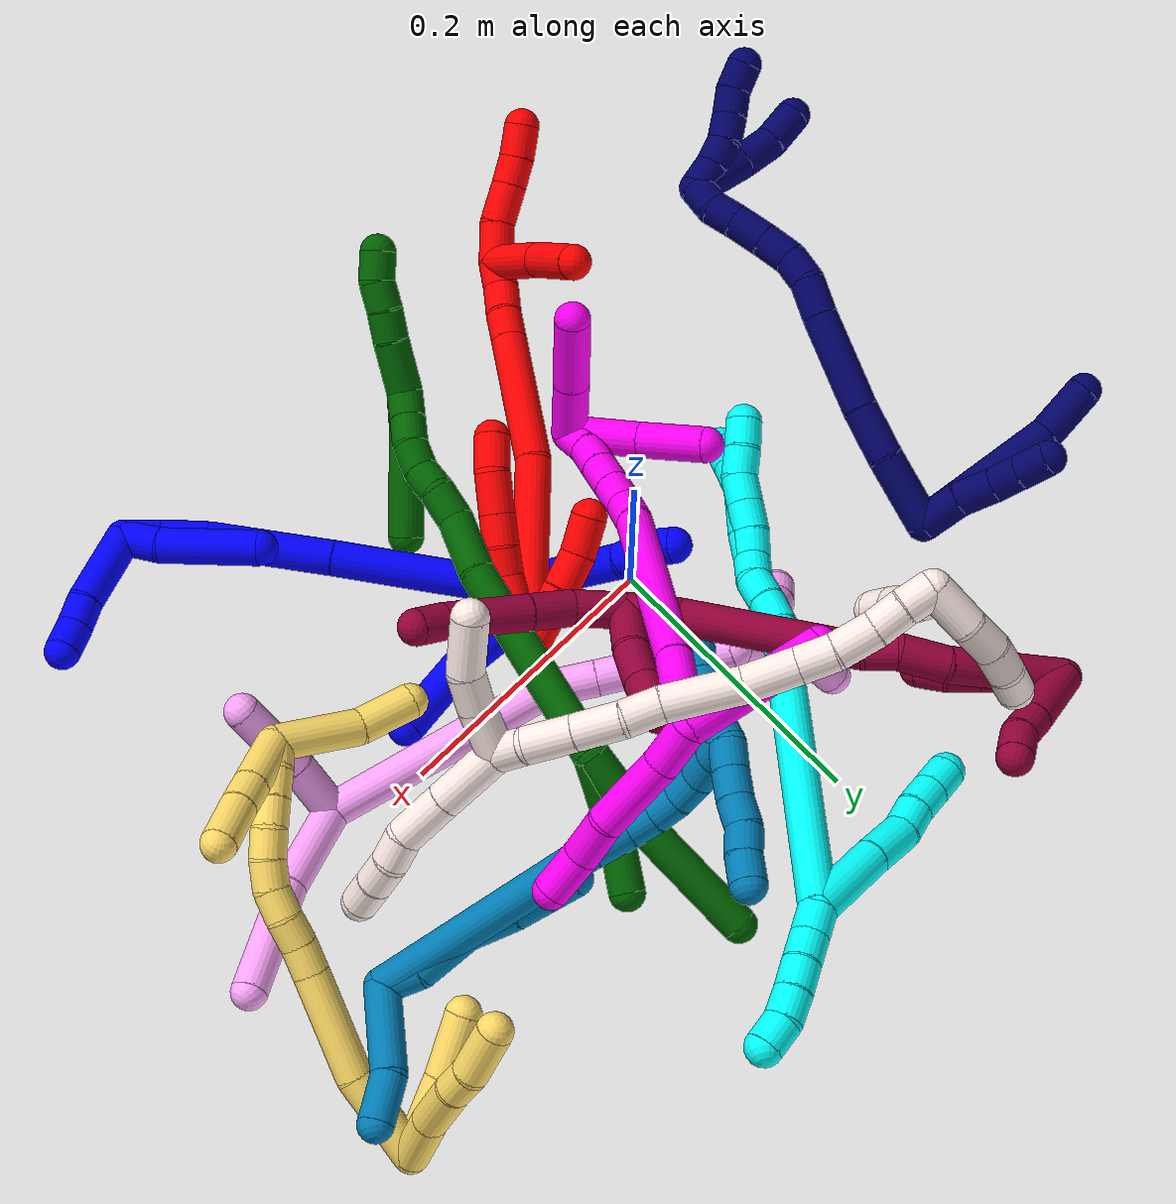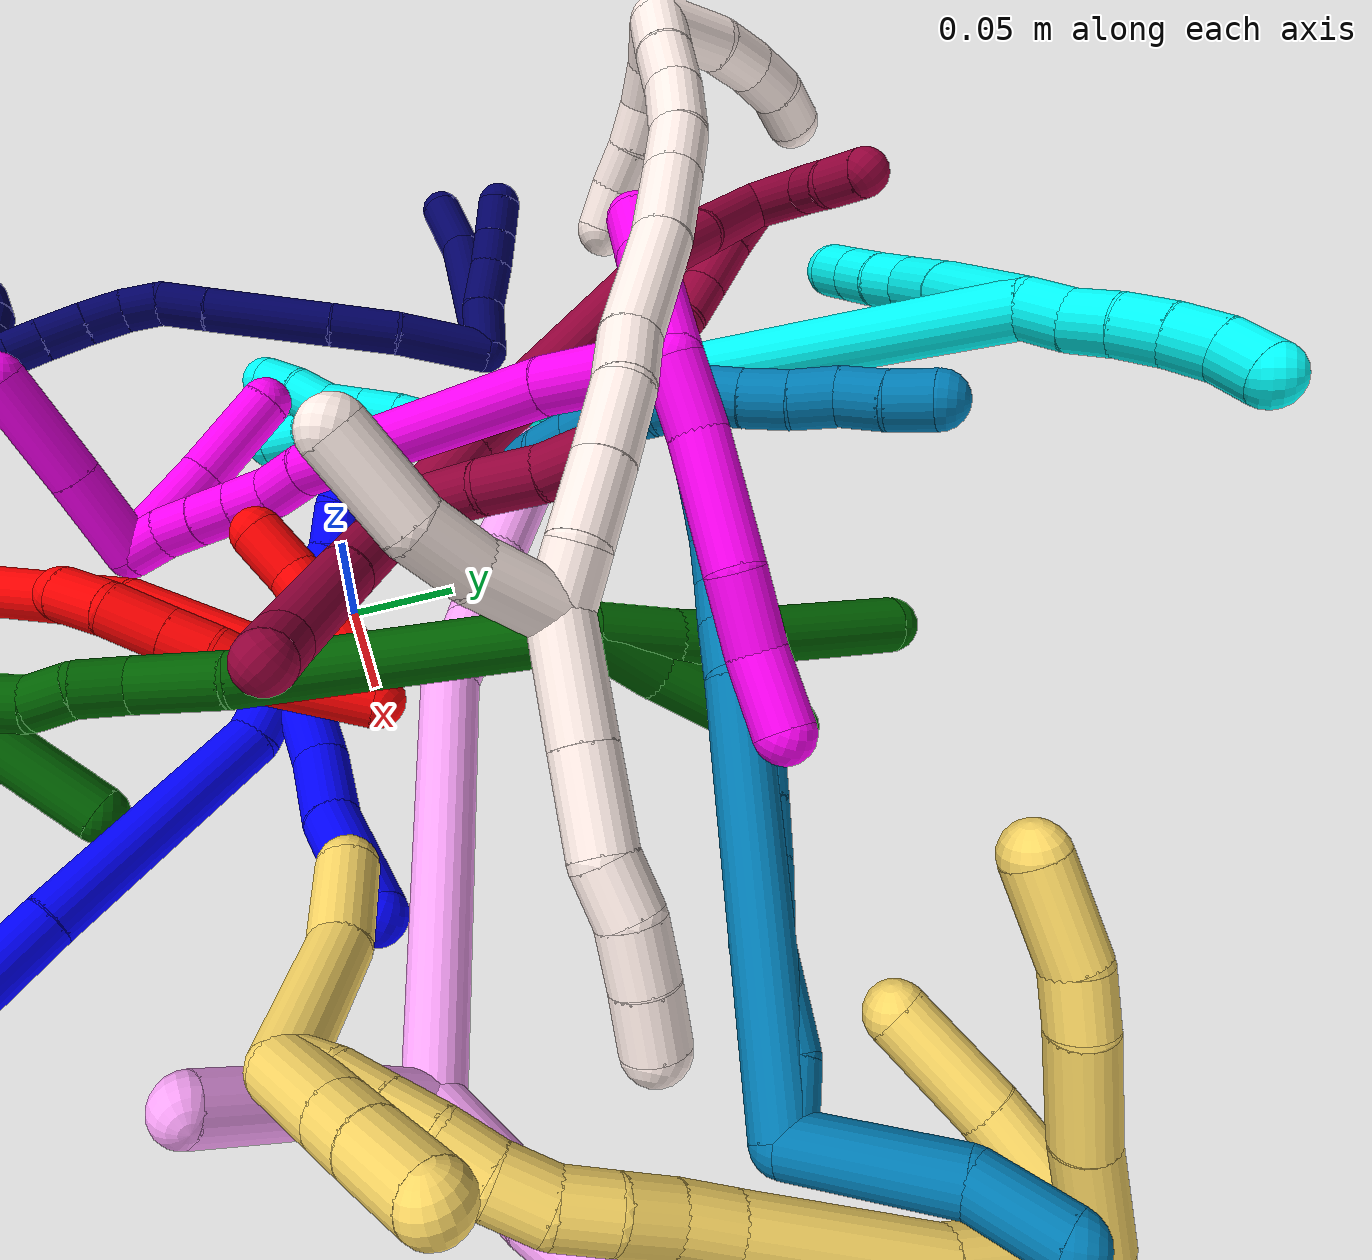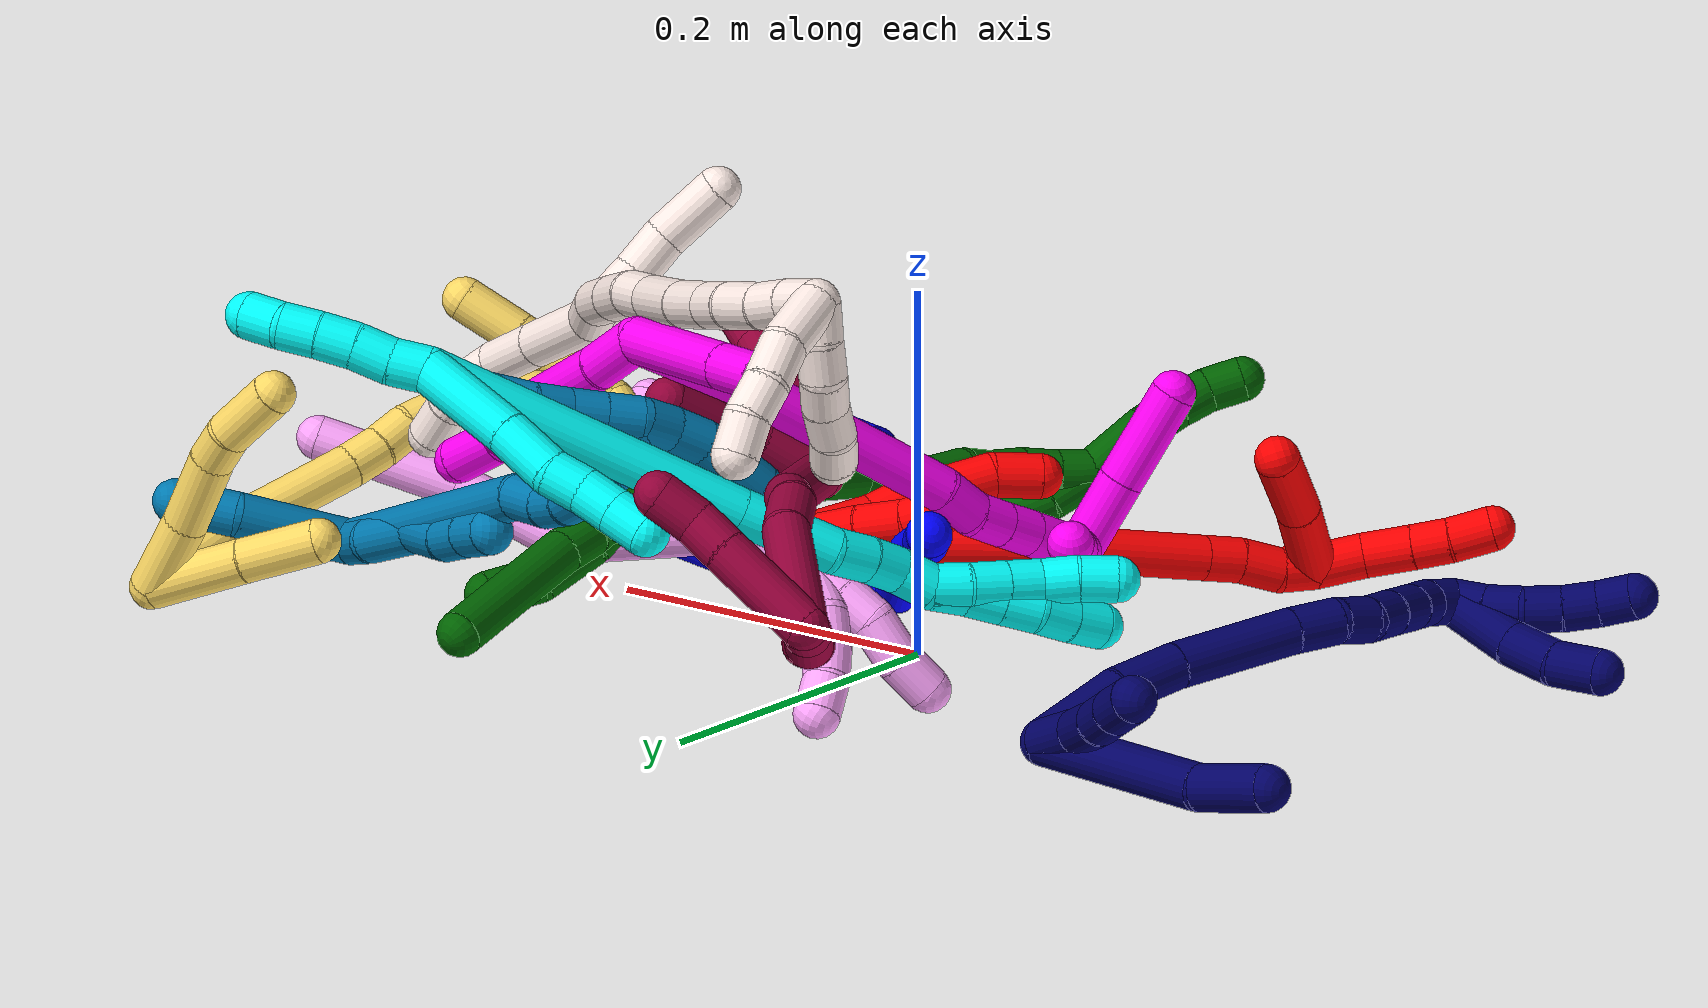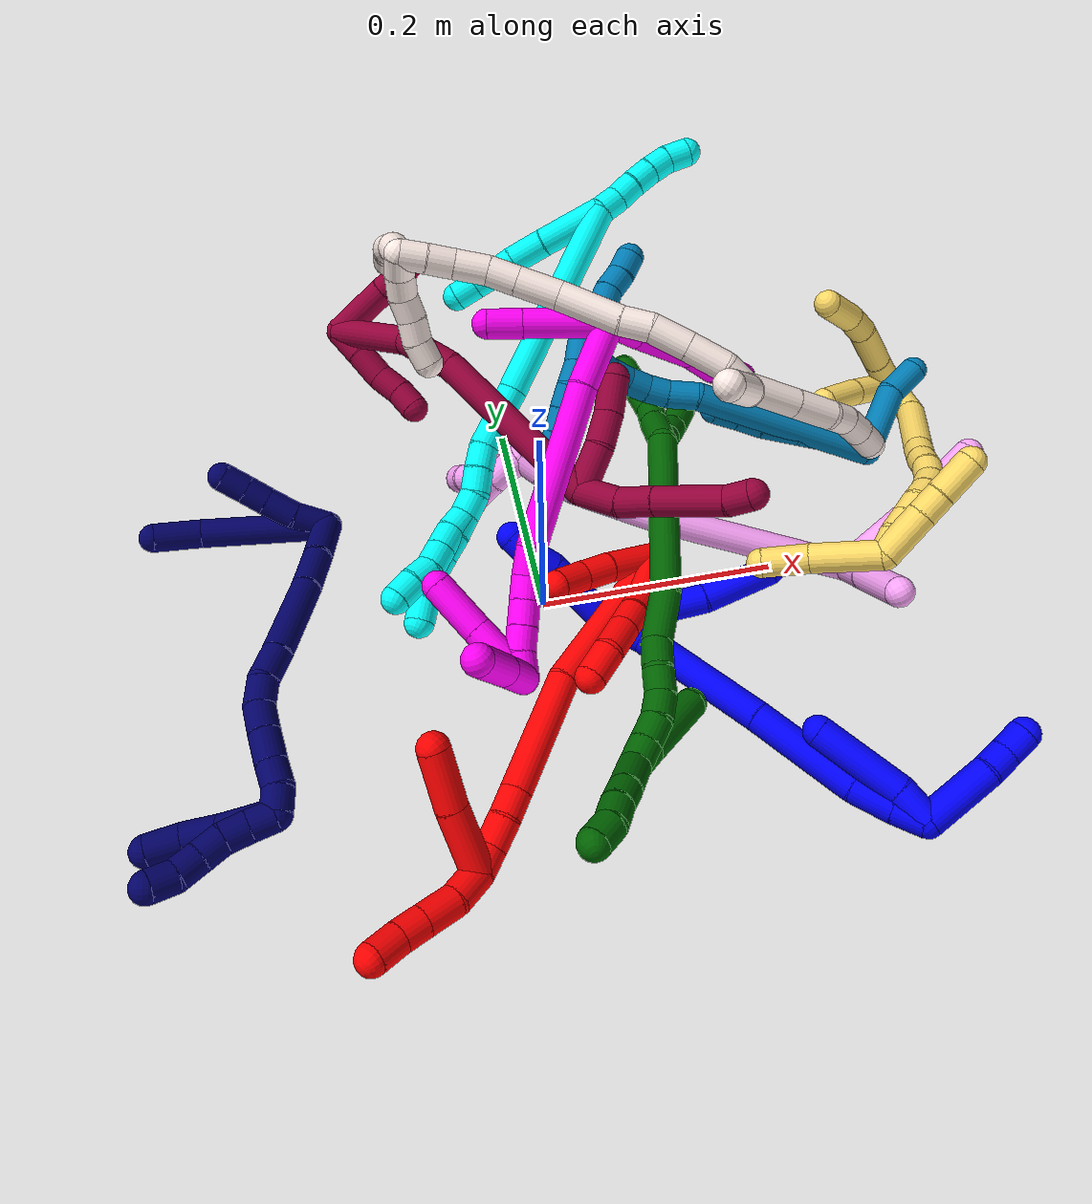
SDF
<sdf version="1.7">
 <world name="default">
  <plugin name="TubeGeneratorPlugin" filename="libtube_generator_plugin.so"/>
  <model name="photoneo_s_sensor">
   <static>1</static>
   <pose>0 0 2 1.57079 1.57079 3.14159</pose>
   <link name="link">
    <inertial><mass>0.1</mass></inertial>
    <sensor name="sensor" type="depth">
     <update_rate>30</update_rate>
     <camera>
      <horizontal_fov>1.22</horizontal_fov>
      <image><width>1920</width><height>1200</height><format>B8G8R8</format></image>
      <clip><near>0.1</near><far>4</far></clip>
      <depth_camera><output>points</output></depth_camera>
     </camera>
     <plugin name="camera_plugin" filename="libgazebo_ros_depth_camera.so">
      <baseline>0.2</baseline>
      <alwaysOn>1</alwaysOn>
      <updateRate>0.0</updateRate>
      <cameraName>camera_ir</cameraName>
      <imageTopicName>/camera/color/image_raw</imageTopicName>
      <cameraInfoTopicName>/camera/color/camera_info</cameraInfoTopicName>
      <depthImageTopicName>/camera/depth/image_raw</depthImageTopicName>
      <depthImageCameraInfoTopicName>/camera/depth/camera_info</depthImageCameraInfoTopicName>
      <pointCloudTopicName>/camera/depth/points</pointCloudTopicName>
      <frameName>fr_optical</frameName>
      <pointCloudCutoff>0.1</pointCloudCutoff>
      <pointCloudCutoffMax>2.0</pointCloudCutoffMax>
      <distortionK1>0</distortionK1>
      <distortionK2>0</distortionK2>
      <distortionK3>0</distortionK3>
      <distortionT1>0</distortionT1>
      <distortionT2>0</distortionT2>
      <CxPrime>0</CxPrime>
      <Cx>0</Cx>
      <Cy>0</Cy>
      <focalLength>0</focalLength>
      <hackBaseline>0</hackBaseline>
     </plugin>
    </sensor>
   </link>
  </model>
  <gravity>0 0 -9.8</gravity>
  <magnetic_field>6e-06 2.3e-05 -4.2e-05</magnetic_field>
  <atmosphere type="adiabatic"/>
  <physics name="default_physics" default="0" type="ode">
   <max_step_size>0.003</max_step_size>
   <real_time_factor>1</real_time_factor>
   <real_time_update_rate>1000</real_time_update_rate>
   <max_contacts>10000</max_contacts>
   <ode>
    <solver>
     <type>quick</type>
     <iters>100</iters>
     <sor>1.3</sor>
     <use_dynamic_moi_rescaling>0</use_dynamic_moi_rescaling>
    </solver>
    <constraints>
     <contact_max_correcting_vel>0</contact_max_correcting_vel>
     <contact_surface_layer>0.001</contact_surface_layer>
     <cfm>0</cfm>
     <erp>0.2</erp>
    </constraints>
   </ode>
  </physics>
  <scene><ambient>0.4 0.4 0.4 1</ambient><background>0.7 0.7 0.7 1</background><shadows>0</shadows></scene>
  <audio><device>default</device></audio>
  <spherical_coordinates>
   <surface_model>EARTH_WGS84</surface_model>
   <latitude_deg>0</latitude_deg>
   <longitude_deg>0</longitude_deg>
   <elevation>0</elevation>
   <heading_deg>0</heading_deg>
  </spherical_coordinates>
  <model name="bin">
   <static>1</static>
   <link name="bottom">
    <collision name="collision-bottom">
     <pose>0 0 -0.01 0 -0 0</pose>
     <geometry><box><size>0.8 0.6 0.02</size></box></geometry>
     <surface>
      <friction><ode><mu>100</mu><mu2>100</mu2></ode></friction>
      <contact><collide_bitmask>65535</collide_bitmask></contact>
     </surface>
    </collision>
   </link>
   <link name="west_wall">
    <collision name="collision-west_wall">
     <pose>-0.41 0 0.1 0 -0 0</pose>
     <geometry><box><size>0.02 0.6 0.2</size></box></geometry>
     <surface>
      <friction><ode><mu>100</mu><mu2>100</mu2></ode></friction>
      <contact><collide_bitmask>65535</collide_bitmask></contact>
     </surface>
    </collision>
   </link>
   <link name="east_wall">
    <collision name="collision-east_wall">
     <pose>0.41 0 0.1 0 -0 0</pose>
     <geometry><box><size>0.02 0.6 0.2</size></box></geometry>
     <surface>
      <friction><ode><mu>100</mu><mu2>100</mu2></ode></friction>
      <contact><collide_bitmask>65535</collide_bitmask></contact>
     </surface>
    </collision>
   </link>
   <link name="south_wall">
    <collision name="collision-south_wall">
     <pose>0 -0.31 0.1 0 -0 0</pose>
     <geometry><box><size>0.8 0.02 0.2</size></box></geometry>
     <surface>
      <friction><ode><mu>100</mu><mu2>100</mu2></ode></friction>
      <contact><collide_bitmask>65535</collide_bitmask></contact>
     </surface>
    </collision>
   </link>
   <link name="north_wall">
    <collision name="collision-north_wall">
     <pose>0 0.31 0.1 0 -0 0</pose>
     <geometry><box><size>0.8 0.02 0.2</size></box></geometry>
     <surface>
      <friction><ode><mu>100</mu><mu2>100</mu2></ode></friction>
      <contact><collide_bitmask>65535</collide_bitmask></contact>
     </surface>
    </collision>
   </link>
  </model>
  <model name="1">
   <static>0</static>
   <link name="1">
    <collision name="collision-cylinder-e_1_2_8">
     <pose>-0.009799 -0.017331 0.017527 0.779774 -0.378394 -0.157049</pose>
     <geometry><cylinder><radius>0.0125</radius><length>0.053049</length></cylinder></geometry>
     <surface>
      <friction><ode><mu>1.16</mu><mu2>1.16</mu2><slip1>0</slip1><slip2>0</slip2></ode></friction>
      <contact><ode><kp>1e+06</kp><kd>1</kd><max_vel>0</max_vel><min_depth>0.001</min_depth></ode></contact>
     </surface>
    </collision>
    <visual name="visual-cylinder-e_1_2_8">
     <pose>-0.009799 -0.017331 0.017527 0.779774 -0.378394 -0.157049</pose>
     <geometry><cylinder><radius>0.0125</radius><length>0.053049</length></cylinder></geometry>
     <material><ambient>0 0 1 1</ambient></material>
    </visual>
    <collision name="collision-cylinder-e_2_8_9">
     <pose>-0.021835 -0.050334 0.045279 0.992721 -0.118983 -0.064493</pose>
     <geometry><cylinder><radius>0.0125</radius><length>0.037694</length></cylinder></geometry>
     <surface>
      <friction><ode><mu>1.16</mu><mu2>1.16</mu2><slip1>0</slip1><slip2>0</slip2></ode></friction>
      <contact><ode><kp>1e+06</kp><kd>1</kd><max_vel>0</max_vel><min_depth>0.001</min_depth></ode></contact>
     </surface>
    </collision>
    <visual name="visual-cylinder-e_2_8_9">
     <pose>-0.021835 -0.050334 0.045279 0.992721 -0.118983 -0.064493</pose>
     <geometry><cylinder><radius>0.0125</radius><length>0.037694</length></cylinder></geometry>
     <material><ambient>0 0 1 1</ambient></material>
    </visual>
    <collision name="collision-cylinder-e_3_9_6">
     <pose>-0.031002 -0.092233 0.067422 1.14425 -0.23609 -0.152448</pose>
     <geometry><cylinder><radius>0.0125</radius><length>0.059257</length></cylinder></geometry>
     <surface>
      <friction><ode><mu>1.16</mu><mu2>1.16</mu2><slip1>0</slip1><slip2>0</slip2></ode></friction>
      <contact><ode><kp>1e+06</kp><kd>1</kd><max_vel>0</max_vel><min_depth>0.001</min_depth></ode></contact>
     </surface>
    </collision>
    <visual name="visual-cylinder-e_3_9_6">
     <pose>-0.031002 -0.092233 0.067422 1.14425 -0.23609 -0.152448</pose>
     <geometry><cylinder><radius>0.0125</radius><length>0.059257</length></cylinder></geometry>
     <material><ambient>0 0 1 1</ambient></material>
    </visual>
    <collision name="collision-cylinder-e_1_2_10">
     <pose>0.001719 -0.001384 -0.028818 3.09362 0.059504 1.78461</pose>
     <geometry><cylinder><radius>0.0125</radius><length>0.057805</length></cylinder></geometry>
     <surface>
      <friction><ode><mu>1.16</mu><mu2>1.16</mu2><slip1>0</slip1><slip2>0</slip2></ode></friction>
      <contact><ode><kp>1e+06</kp><kd>1</kd><max_vel>0</max_vel><min_depth>0.001</min_depth></ode></contact>
     </surface>
    </collision>
    <visual name="visual-cylinder-e_1_2_10">
     <pose>0.001719 -0.001384 -0.028818 3.09362 0.059504 1.78461</pose>
     <geometry><cylinder><radius>0.0125</radius><length>0.057805</length></cylinder></geometry>
     <material><ambient>0 0 1 1</ambient></material>
    </visual>
    <collision name="collision-cylinder-e_2_10_11">
     <pose>0.005561 -0.001051 -0.067376 -2.96712 0.211467 -1.76312</pose>
     <geometry><cylinder><radius>0.0125</radius><length>0.02023</length></cylinder></geometry>
     <surface>
      <friction><ode><mu>1.16</mu><mu2>1.16</mu2><slip1>0</slip1><slip2>0</slip2></ode></friction>
      <contact><ode><kp>1e+06</kp><kd>1</kd><max_vel>0</max_vel><min_depth>0.001</min_depth></ode></contact>
     </surface>
    </collision>
    <visual name="visual-cylinder-e_2_10_11">
     <pose>0.005561 -0.001051 -0.067376 -2.96712 0.211467 -1.76312</pose>
     <geometry><cylinder><radius>0.0125</radius><length>0.02023</length></cylinder></geometry>
     <material><ambient>0 0 1 1</ambient></material>
    </visual>
    <collision name="collision-cylinder-e_3_11_5">
     <pose>0.006634 0.001021 -0.088042 -3.10912 -0.095761 2.48815</pose>
     <geometry><cylinder><radius>0.0125</radius><length>0.021965</length></cylinder></geometry>
     <surface>
      <friction><ode><mu>1.16</mu><mu2>1.16</mu2><slip1>0</slip1><slip2>0</slip2></ode></friction>
      <contact><ode><kp>1e+06</kp><kd>1</kd><max_vel>0</max_vel><min_depth>0.001</min_depth></ode></contact>
     </surface>
    </collision>
    <visual name="visual-cylinder-e_3_11_5">
     <pose>0.006634 0.001021 -0.088042 -3.10912 -0.095761 2.48815</pose>
     <geometry><cylinder><radius>0.0125</radius><length>0.021965</length></cylinder></geometry>
     <material><ambient>0 0 1 1</ambient></material>
    </visual>
    <collision name="collision-cylinder-e_1_2_12">
     <pose>0.003386 -0.00616 0.018412 0.322856 0.172666 0.028186</pose>
     <geometry><cylinder><radius>0.0125</radius><length>0.039417</length></cylinder></geometry>
     <surface>
      <friction><ode><mu>1.16</mu><mu2>1.16</mu2><slip1>0</slip1><slip2>0</slip2></ode></friction>
      <contact><ode><kp>1e+06</kp><kd>1</kd><max_vel>0</max_vel><min_depth>0.001</min_depth></ode></contact>
     </surface>
    </collision>
    <visual name="visual-cylinder-e_1_2_12">
     <pose>0.003386 -0.00616 0.018412 0.322856 0.172666 0.028186</pose>
     <geometry><cylinder><radius>0.0125</radius><length>0.039417</length></cylinder></geometry>
     <material><ambient>0 0 1 1</ambient></material>
    </visual>
    <collision name="collision-cylinder-e_2_12_13">
     <pose>0.035148 -0.028125 0.084008 0.323229 0.518262 0.086385</pose>
     <geometry><cylinder><radius>0.0125</radius><length>0.114565</length></cylinder></geometry>
     <surface>
      <friction><ode><mu>1.16</mu><mu2>1.16</mu2><slip1>0</slip1><slip2>0</slip2></ode></friction>
      <contact><ode><kp>1e+06</kp><kd>1</kd><max_vel>0</max_vel><min_depth>0.001</min_depth></ode></contact>
     </surface>
    </collision>
    <visual name="visual-cylinder-e_2_12_13">
     <pose>0.035148 -0.028125 0.084008 0.323229 0.518262 0.086385</pose>
     <geometry><cylinder><radius>0.0125</radius><length>0.114565</length></cylinder></geometry>
     <material><ambient>0 0 1 1</ambient></material>
    </visual>
    <collision name="collision-cylinder-e_3_13_14">
     <pose>0.083913 -0.054392 0.168925 0.270459 0.480065 0.066577</pose>
     <geometry><cylinder><radius>0.0125</radius><length>0.088294</length></cylinder></geometry>
     <surface>
      <friction><ode><mu>1.16</mu><mu2>1.16</mu2><slip1>0</slip1><slip2>0</slip2></ode></friction>
      <contact><ode><kp>1e+06</kp><kd>1</kd><max_vel>0</max_vel><min_depth>0.001</min_depth></ode></contact>
     </surface>
    </collision>
    <visual name="visual-cylinder-e_3_13_14">
     <pose>0.083913 -0.054392 0.168925 0.270459 0.480065 0.066577</pose>
     <geometry><cylinder><radius>0.0125</radius><length>0.088294</length></cylinder></geometry>
     <material><ambient>0 0 1 1</ambient></material>
    </visual>
    <collision name="collision-cylinder-e_4_14_15">
     <pose>0.111067 -0.071254 0.220166 0.442455 0.424991 0.096973</pose>
     <geometry><cylinder><radius>0.0125</radius><length>0.032815</length></cylinder></geometry>
     <surface>
      <friction><ode><mu>1.16</mu><mu2>1.16</mu2><slip1>0</slip1><slip2>0</slip2></ode></friction>
      <contact><ode><kp>1e+06</kp><kd>1</kd><max_vel>0</max_vel><min_depth>0.001</min_depth></ode></contact>
     </surface>
    </collision>
    <visual name="visual-cylinder-e_4_14_15">
     <pose>0.111067 -0.071254 0.220166 0.442455 0.424991 0.096973</pose>
     <geometry><cylinder><radius>0.0125</radius><length>0.032815</length></cylinder></geometry>
     <material><ambient>0 0 1 1</ambient></material>
    </visual>
    <collision name="collision-cylinder-e_5_15_1">
     <pose>0.122869 -0.083479 0.243463 0.536796 0.41636 0.116066</pose>
     <geometry><cylinder><radius>0.0125</radius><length>0.02491</length></cylinder></geometry>
     <surface>
      <friction><ode><mu>1.16</mu><mu2>1.16</mu2><slip1>0</slip1><slip2>0</slip2></ode></friction>
      <contact><ode><kp>1e+06</kp><kd>1</kd><max_vel>0</max_vel><min_depth>0.001</min_depth></ode></contact>
     </surface>
    </collision>
    <visual name="visual-cylinder-e_5_15_1">
     <pose>0.122869 -0.083479 0.243463 0.536796 0.41636 0.116066</pose>
     <geometry><cylinder><radius>0.0125</radius><length>0.02491</length></cylinder></geometry>
     <material><ambient>0 0 1 1</ambient></material>
    </visual>
    <collision name="collision-cylinder-e_1_1_16">
     <pose>0.122371 -0.089423 0.240024 3.13258 -0.396316 -3.09673</pose>
     <geometry><cylinder><radius>0.0125</radius><length>0.028679</length></cylinder></geometry>
     <surface>
      <friction><ode><mu>1.16</mu><mu2>1.16</mu2><slip1>0</slip1><slip2>0</slip2></ode></friction>
      <contact><ode><kp>1e+06</kp><kd>1</kd><max_vel>0</max_vel><min_depth>0.001</min_depth></ode></contact>
     </surface>
    </collision>
    <visual name="visual-cylinder-e_1_1_16">
     <pose>0.122371 -0.089423 0.240024 3.13258 -0.396316 -3.09673</pose>
     <geometry><cylinder><radius>0.0125</radius><length>0.028679</length></cylinder></geometry>
     <material><ambient>0 0 1 1</ambient></material>
    </visual>
    <collision name="collision-cylinder-e_2_16_4">
     <pose>0.1056 -0.082394 0.193716 -2.92877 -0.320519 1.97373</pose>
     <geometry><cylinder><radius>0.0125</radius><length>0.071321</length></cylinder></geometry>
     <surface>
      <friction><ode><mu>1.16</mu><mu2>1.16</mu2><slip1>0</slip1><slip2>0</slip2></ode></friction>
      <contact><ode><kp>1e+06</kp><kd>1</kd><max_vel>0</max_vel><min_depth>0.001</min_depth></ode></contact>
     </surface>
    </collision>
    <visual name="visual-cylinder-e_2_16_4">
     <pose>0.1056 -0.082394 0.193716 -2.92877 -0.320519 1.97373</pose>
     <geometry><cylinder><radius>0.0125</radius><length>0.071321</length></cylinder></geometry>
     <material><ambient>0 0 1 1</ambient></material>
    </visual>
    <collision name="collision-cylinder-e_1_1_17">
     <pose>0.118588 -0.116659 0.25833 1.38723 -0.32318 -0.269425</pose>
     <geometry><cylinder><radius>0.0125</radius><length>0.058682</length></cylinder></geometry>
     <surface>
      <friction><ode><mu>1.16</mu><mu2>1.16</mu2><slip1>0</slip1><slip2>0</slip2></ode></friction>
      <contact><ode><kp>1e+06</kp><kd>1</kd><max_vel>0</max_vel><min_depth>0.001</min_depth></ode></contact>
     </surface>
    </collision>
    <visual name="visual-cylinder-e_1_1_17">
     <pose>0.118588 -0.116659 0.25833 1.38723 -0.32318 -0.269425</pose>
     <geometry><cylinder><radius>0.0125</radius><length>0.058682</length></cylinder></geometry>
     <material><ambient>0 0 1 1</ambient></material>
    </visual>
    <collision name="collision-cylinder-e_2_17_18">
     <pose>0.104392 -0.152608 0.265119 1.37439 -0.507845 -0.419677</pose>
     <geometry><cylinder><radius>0.0125</radius><length>0.020058</length></cylinder></geometry>
     <surface>
      <friction><ode><mu>1.16</mu><mu2>1.16</mu2><slip1>0</slip1><slip2>0</slip2></ode></friction>
      <contact><ode><kp>1e+06</kp><kd>1</kd><max_vel>0</max_vel><min_depth>0.001</min_depth></ode></contact>
     </surface>
    </collision>
    <visual name="visual-cylinder-e_2_17_18">
     <pose>0.104392 -0.152608 0.265119 1.37439 -0.507845 -0.419677</pose>
     <geometry><cylinder><radius>0.0125</radius><length>0.020058</length></cylinder></geometry>
     <material><ambient>0 0 1 1</ambient></material>
    </visual>
    <collision name="collision-cylinder-e_3_18_3">
     <pose>0.095792 -0.171118 0.267744 1.47878 -0.35782 -0.326905</pose>
     <geometry><cylinder><radius>0.0125</radius><length>0.02126</length></cylinder></geometry>
     <surface>
      <friction><ode><mu>1.16</mu><mu2>1.16</mu2><slip1>0</slip1><slip2>0</slip2></ode></friction>
      <contact><ode><kp>1e+06</kp><kd>1</kd><max_vel>0</max_vel><min_depth>0.001</min_depth></ode></contact>
     </surface>
    </collision>
    <visual name="visual-cylinder-e_3_18_3">
     <pose>0.095792 -0.171118 0.267744 1.47878 -0.35782 -0.326905</pose>
     <geometry><cylinder><radius>0.0125</radius><length>0.02126</length></cylinder></geometry>
     <material><ambient>0 0 1 1</ambient></material>
    </visual>
    <collision name="collision-sphere-3">
     <pose>0.092069 -0.181032 0.268659 0 -0 0</pose>
     <geometry><sphere><radius>0.0125</radius></sphere></geometry>
     <surface>
      <friction><ode><mu>1.16</mu><mu2>1.16</mu2><slip1>0</slip1><slip2>0</slip2></ode></friction>
      <contact><ode><kp>1e+06</kp><kd>1</kd><max_vel>0</max_vel><min_depth>0.001</min_depth></ode></contact>
     </surface>
    </collision>
    <visual name="visual-sphere-3">
     <pose>0.092069 -0.181032 0.268659 0 -0 0</pose>
     <geometry><sphere><radius>0.0125</radius></sphere></geometry>
     <material><ambient>0 0 1 1</ambient></material>
    </visual>
    <collision name="collision-sphere-11">
     <pose>0.007684 0.000666 -0.077115 0 -0 0</pose>
     <geometry><sphere><radius>0.0125</radius></sphere></geometry>
     <surface>
      <friction><ode><mu>1.16</mu><mu2>1.16</mu2><slip1>0</slip1><slip2>0</slip2></ode></friction>
      <contact><ode><kp>1e+06</kp><kd>1</kd><max_vel>0</max_vel><min_depth>0.001</min_depth></ode></contact>
     </surface>
    </collision>
    <visual name="visual-sphere-11">
     <pose>0.007684 0.000666 -0.077115 0 -0 0</pose>
     <geometry><sphere><radius>0.0125</radius></sphere></geometry>
     <material><ambient>0 0 1 1</ambient></material>
    </visual>
    <collision name="collision-sphere-10">
     <pose>0.003438 -0.002767 -0.057636 0 -0 0</pose>
     <geometry><sphere><radius>0.0125</radius></sphere></geometry>
     <surface>
      <friction><ode><mu>1.16</mu><mu2>1.16</mu2><slip1>0</slip1><slip2>0</slip2></ode></friction>
      <contact><ode><kp>1e+06</kp><kd>1</kd><max_vel>0</max_vel><min_depth>0.001</min_depth></ode></contact>
     </surface>
    </collision>
    <visual name="visual-sphere-10">
     <pose>0.003438 -0.002767 -0.057636 0 -0 0</pose>
     <geometry><sphere><radius>0.0125</radius></sphere></geometry>
     <material><ambient>0 0 1 1</ambient></material>
    </visual>
    <collision name="collision-sphere-6">
     <pose>-0.037933 -0.118458 0.079341 0 -0 0</pose>
     <geometry><sphere><radius>0.0125</radius></sphere></geometry>
     <surface>
      <friction><ode><mu>1.16</mu><mu2>1.16</mu2><slip1>0</slip1><slip2>0</slip2></ode></friction>
      <contact><ode><kp>1e+06</kp><kd>1</kd><max_vel>0</max_vel><min_depth>0.001</min_depth></ode></contact>
     </surface>
    </collision>
    <visual name="visual-sphere-6">
     <pose>-0.037933 -0.118458 0.079341 0 -0 0</pose>
     <geometry><sphere><radius>0.0125</radius></sphere></geometry>
     <material><ambient>0 0 1 1</ambient></material>
    </visual>
    <collision name="collision-sphere-9">
     <pose>-0.024072 -0.066007 0.055504 0 -0 0</pose>
     <geometry><sphere><radius>0.0125</radius></sphere></geometry>
     <surface>
      <friction><ode><mu>1.16</mu><mu2>1.16</mu2><slip1>0</slip1><slip2>0</slip2></ode></friction>
      <contact><ode><kp>1e+06</kp><kd>1</kd><max_vel>0</max_vel><min_depth>0.001</min_depth></ode></contact>
     </surface>
    </collision>
    <visual name="visual-sphere-9">
     <pose>-0.024072 -0.066007 0.055504 0 -0 0</pose>
     <geometry><sphere><radius>0.0125</radius></sphere></geometry>
     <material><ambient>0 0 1 1</ambient></material>
    </visual>
    <collision name="collision-sphere-2">
     <geometry><sphere><radius>0.0125</radius></sphere></geometry>
     <surface>
      <friction><ode><mu>1.16</mu><mu2>1.16</mu2><slip1>0</slip1><slip2>0</slip2></ode></friction>
      <contact><ode><kp>1e+06</kp><kd>1</kd><max_vel>0</max_vel><min_depth>0.001</min_depth></ode></contact>
     </surface>
    </collision>
    <visual name="visual-sphere-2">
     <geometry><sphere><radius>0.0125</radius></sphere></geometry>
     <material><ambient>0 0 1 1</ambient></material>
    </visual>
    <collision name="collision-sphere-8">
     <pose>-0.019598 -0.034661 0.035053 0 -0 0</pose>
     <geometry><sphere><radius>0.0125</radius></sphere></geometry>
     <surface>
      <friction><ode><mu>1.16</mu><mu2>1.16</mu2><slip1>0</slip1><slip2>0</slip2></ode></friction>
      <contact><ode><kp>1e+06</kp><kd>1</kd><max_vel>0</max_vel><min_depth>0.001</min_depth></ode></contact>
     </surface>
    </collision>
    <visual name="visual-sphere-8">
     <pose>-0.019598 -0.034661 0.035053 0 -0 0</pose>
     <geometry><sphere><radius>0.0125</radius></sphere></geometry>
     <material><ambient>0 0 1 1</ambient></material>
    </visual>
    <collision name="collision-sphere-5">
     <pose>0.005584 0.001376 -0.098968 0 -0 0</pose>
     <geometry><sphere><radius>0.0125</radius></sphere></geometry>
     <surface>
      <friction><ode><mu>1.16</mu><mu2>1.16</mu2><slip1>0</slip1><slip2>0</slip2></ode></friction>
      <contact><ode><kp>1e+06</kp><kd>1</kd><max_vel>0</max_vel><min_depth>0.001</min_depth></ode></contact>
     </surface>
    </collision>
    <visual name="visual-sphere-5">
     <pose>0.005584 0.001376 -0.098968 0 -0 0</pose>
     <geometry><sphere><radius>0.0125</radius></sphere></geometry>
     <material><ambient>0 0 1 1</ambient></material>
    </visual>
    <collision name="collision-sphere-12">
     <pose>0.006772 -0.01232 0.036824 0 -0 0</pose>
     <geometry><sphere><radius>0.0125</radius></sphere></geometry>
     <surface>
      <friction><ode><mu>1.16</mu><mu2>1.16</mu2><slip1>0</slip1><slip2>0</slip2></ode></friction>
      <contact><ode><kp>1e+06</kp><kd>1</kd><max_vel>0</max_vel><min_depth>0.001</min_depth></ode></contact>
     </surface>
    </collision>
    <visual name="visual-sphere-12">
     <pose>0.006772 -0.01232 0.036824 0 -0 0</pose>
     <geometry><sphere><radius>0.0125</radius></sphere></geometry>
     <material><ambient>0 0 1 1</ambient></material>
    </visual>
    <collision name="collision-sphere-13">
     <pose>0.063525 -0.043931 0.131191 0 -0 0</pose>
     <geometry><sphere><radius>0.0125</radius></sphere></geometry>
     <surface>
      <friction><ode><mu>1.16</mu><mu2>1.16</mu2><slip1>0</slip1><slip2>0</slip2></ode></friction>
      <contact><ode><kp>1e+06</kp><kd>1</kd><max_vel>0</max_vel><min_depth>0.001</min_depth></ode></contact>
     </surface>
    </collision>
    <visual name="visual-sphere-13">
     <pose>0.063525 -0.043931 0.131191 0 -0 0</pose>
     <geometry><sphere><radius>0.0125</radius></sphere></geometry>
     <material><ambient>0 0 1 1</ambient></material>
    </visual>
    <collision name="collision-sphere-14">
     <pose>0.104302 -0.064854 0.206658 0 -0 0</pose>
     <geometry><sphere><radius>0.0125</radius></sphere></geometry>
     <surface>
      <friction><ode><mu>1.16</mu><mu2>1.16</mu2><slip1>0</slip1><slip2>0</slip2></ode></friction>
      <contact><ode><kp>1e+06</kp><kd>1</kd><max_vel>0</max_vel><min_depth>0.001</min_depth></ode></contact>
     </surface>
    </collision>
    <visual name="visual-sphere-14">
     <pose>0.104302 -0.064854 0.206658 0 -0 0</pose>
     <geometry><sphere><radius>0.0125</radius></sphere></geometry>
     <material><ambient>0 0 1 1</ambient></material>
    </visual>
    <collision name="collision-sphere-15">
     <pose>0.117832 -0.077654 0.233675 0 -0 0</pose>
     <geometry><sphere><radius>0.0125</radius></sphere></geometry>
     <surface>
      <friction><ode><mu>1.16</mu><mu2>1.16</mu2><slip1>0</slip1><slip2>0</slip2></ode></friction>
      <contact><ode><kp>1e+06</kp><kd>1</kd><max_vel>0</max_vel><min_depth>0.001</min_depth></ode></contact>
     </surface>
    </collision>
    <visual name="visual-sphere-15">
     <pose>0.117832 -0.077654 0.233675 0 -0 0</pose>
     <geometry><sphere><radius>0.0125</radius></sphere></geometry>
     <material><ambient>0 0 1 1</ambient></material>
    </visual>
    <collision name="collision-sphere-1">
     <pose>0.127906 -0.089304 0.253252 0 -0 0</pose>
     <geometry><sphere><radius>0.0125</radius></sphere></geometry>
     <surface>
      <friction><ode><mu>1.16</mu><mu2>1.16</mu2><slip1>0</slip1><slip2>0</slip2></ode></friction>
      <contact><ode><kp>1e+06</kp><kd>1</kd><max_vel>0</max_vel><min_depth>0.001</min_depth></ode></contact>
     </surface>
    </collision>
    <visual name="visual-sphere-1">
     <pose>0.127906 -0.089304 0.253252 0 -0 0</pose>
     <geometry><sphere><radius>0.0125</radius></sphere></geometry>
     <material><ambient>0 0 1 1</ambient></material>
    </visual>
    <collision name="collision-sphere-18">
     <pose>0.099515 -0.161203 0.266829 0 -0 0</pose>
     <geometry><sphere><radius>0.0125</radius></sphere></geometry>
     <surface>
      <friction><ode><mu>1.16</mu><mu2>1.16</mu2><slip1>0</slip1><slip2>0</slip2></ode></friction>
      <contact><ode><kp>1e+06</kp><kd>1</kd><max_vel>0</max_vel><min_depth>0.001</min_depth></ode></contact>
     </surface>
    </collision>
    <visual name="visual-sphere-18">
     <pose>0.099515 -0.161203 0.266829 0 -0 0</pose>
     <geometry><sphere><radius>0.0125</radius></sphere></geometry>
     <material><ambient>0 0 1 1</ambient></material>
    </visual>
    <collision name="collision-sphere-16">
     <pose>0.116835 -0.089543 0.226797 0 -0 0</pose>
     <geometry><sphere><radius>0.0125</radius></sphere></geometry>
     <surface>
      <friction><ode><mu>1.16</mu><mu2>1.16</mu2><slip1>0</slip1><slip2>0</slip2></ode></friction>
      <contact><ode><kp>1e+06</kp><kd>1</kd><max_vel>0</max_vel><min_depth>0.001</min_depth></ode></contact>
     </surface>
    </collision>
    <visual name="visual-sphere-16">
     <pose>0.116835 -0.089543 0.226797 0 -0 0</pose>
     <geometry><sphere><radius>0.0125</radius></sphere></geometry>
     <material><ambient>0 0 1 1</ambient></material>
    </visual>
    <collision name="collision-sphere-4">
     <pose>0.094365 -0.075245 0.160635 0 -0 0</pose>
     <geometry><sphere><radius>0.0125</radius></sphere></geometry>
     <surface>
      <friction><ode><mu>1.16</mu><mu2>1.16</mu2><slip1>0</slip1><slip2>0</slip2></ode></friction>
      <contact><ode><kp>1e+06</kp><kd>1</kd><max_vel>0</max_vel><min_depth>0.001</min_depth></ode></contact>
     </surface>
    </collision>
    <visual name="visual-sphere-4">
     <pose>0.094365 -0.075245 0.160635 0 -0 0</pose>
     <geometry><sphere><radius>0.0125</radius></sphere></geometry>
     <material><ambient>0 0 1 1</ambient></material>
    </visual>
    <collision name="collision-sphere-17">
     <pose>0.10927 -0.144013 0.263409 0 -0 0</pose>
     <geometry><sphere><radius>0.0125</radius></sphere></geometry>
     <surface>
      <friction><ode><mu>1.16</mu><mu2>1.16</mu2><slip1>0</slip1><slip2>0</slip2></ode></friction>
      <contact><ode><kp>1e+06</kp><kd>1</kd><max_vel>0</max_vel><min_depth>0.001</min_depth></ode></contact>
     </surface>
    </collision>
    <visual name="visual-sphere-17">
     <pose>0.10927 -0.144013 0.263409 0 -0 0</pose>
     <geometry><sphere><radius>0.0125</radius></sphere></geometry>
     <material><ambient>0 0 1 1</ambient></material>
    </visual>
    <inertial>
     <pose>0.05011 -0.057376 0.116123 0 -0 0</pose>
     <mass>0.75</mass>
     <inertia>
      <ixx>0.000267</ixx>
      <ixy>0</ixy>
      <ixz>0</ixz>
      <iyy>0.000274</iyy>
      <iyz>0</iyz>
      <izz>4.6e-05</izz>
     </inertia>
    </inertial>
   </link>
   <pose>0.041608 -0.035572 0.01996 -2.27575 -0.624893 -1.87249</pose>
  </model>
  <model name="2">
   <static>0</static>
   <link name="2">
    <collision name="collision-cylinder-e_1_2_8">
     <pose>0.002425 -0.009349 0.024741 0.361297 0.091445 0.016713</pose>
     <geometry><cylinder><radius>0.0125</radius><length>0.053119</length></cylinder></geometry>
     <surface>
      <friction><ode><mu>1.16</mu><mu2>1.16</mu2><slip1>0</slip1><slip2>0</slip2></ode></friction>
      <contact><ode><kp>1e+06</kp><kd>1</kd><max_vel>0</max_vel><min_depth>0.001</min_depth></ode></contact>
     </surface>
    </collision>
    <visual name="visual-cylinder-e_1_2_8">
     <pose>0.002425 -0.009349 0.024741 0.361297 0.091445 0.016713</pose>
     <geometry><cylinder><radius>0.0125</radius><length>0.053119</length></cylinder></geometry>
     <material><ambient>1 0 0 1</ambient></material>
    </visual>
    <collision name="collision-cylinder-e_2_8_9">
     <pose>0.006726 -0.019765 0.059374 0.107374 0.186343 0.010043</pose>
     <geometry><cylinder><radius>0.0125</radius><length>0.020248</length></cylinder></geometry>
     <surface>
      <friction><ode><mu>1.16</mu><mu2>1.16</mu2><slip1>0</slip1><slip2>0</slip2></ode></friction>
      <contact><ode><kp>1e+06</kp><kd>1</kd><max_vel>0</max_vel><min_depth>0.001</min_depth></ode></contact>
     </surface>
    </collision>
    <visual name="visual-cylinder-e_2_8_9">
     <pose>0.006726 -0.019765 0.059374 0.107374 0.186343 0.010043</pose>
     <geometry><cylinder><radius>0.0125</radius><length>0.020248</length></cylinder></geometry>
     <material><ambient>1 0 0 1</ambient></material>
    </visual>
    <collision name="collision-cylinder-e_3_9_10">
     <pose>0.009095 -0.022826 0.080024 0.183338 0.044975 0.004135</pose>
     <geometry><cylinder><radius>0.0125</radius><length>0.021906</length></cylinder></geometry>
     <surface>
      <friction><ode><mu>1.16</mu><mu2>1.16</mu2><slip1>0</slip1><slip2>0</slip2></ode></friction>
      <contact><ode><kp>1e+06</kp><kd>1</kd><max_vel>0</max_vel><min_depth>0.001</min_depth></ode></contact>
     </surface>
    </collision>
    <visual name="visual-cylinder-e_3_9_10">
     <pose>0.009095 -0.022826 0.080024 0.183338 0.044975 0.004135</pose>
     <geometry><cylinder><radius>0.0125</radius><length>0.021906</length></cylinder></geometry>
     <material><ambient>1 0 0 1</ambient></material>
    </visual>
    <collision name="collision-cylinder-e_4_10_11">
     <pose>0.010087 -0.027268 0.104946 0.171071 0.034757 0.002981</pose>
     <geometry><cylinder><radius>0.0125</radius><length>0.028765</length></cylinder></geometry>
     <surface>
      <friction><ode><mu>1.16</mu><mu2>1.16</mu2><slip1>0</slip1><slip2>0</slip2></ode></friction>
      <contact><ode><kp>1e+06</kp><kd>1</kd><max_vel>0</max_vel><min_depth>0.001</min_depth></ode></contact>
     </surface>
    </collision>
    <visual name="visual-cylinder-e_4_10_11">
     <pose>0.010087 -0.027268 0.104946 0.171071 0.034757 0.002981</pose>
     <geometry><cylinder><radius>0.0125</radius><length>0.028765</length></cylinder></geometry>
     <material><ambient>1 0 0 1</ambient></material>
    </visual>
    <collision name="collision-cylinder-e_5_11_6">
     <pose>0.007251 -0.032987 0.131221 0.263907 -0.259881 -0.034685</pose>
     <geometry><cylinder><radius>0.0125</radius><length>0.025962</length></cylinder></geometry>
     <surface>
      <friction><ode><mu>1.16</mu><mu2>1.16</mu2><slip1>0</slip1><slip2>0</slip2></ode></friction>
      <contact><ode><kp>1e+06</kp><kd>1</kd><max_vel>0</max_vel><min_depth>0.001</min_depth></ode></contact>
     </surface>
    </collision>
    <visual name="visual-cylinder-e_5_11_6">
     <pose>0.007251 -0.032987 0.131221 0.263907 -0.259881 -0.034685</pose>
     <geometry><cylinder><radius>0.0125</radius><length>0.025962</length></cylinder></geometry>
     <material><ambient>1 0 0 1</ambient></material>
    </visual>
    <collision name="collision-cylinder-e_1_2_12">
     <pose>-0.004879 0.00873 0.021334 -0.388405 -0.208597 0.041171</pose>
     <geometry><cylinder><radius>0.0125</radius><length>0.047124</length></cylinder></geometry>
     <surface>
      <friction><ode><mu>1.16</mu><mu2>1.16</mu2><slip1>0</slip1><slip2>0</slip2></ode></friction>
      <contact><ode><kp>1e+06</kp><kd>1</kd><max_vel>0</max_vel><min_depth>0.001</min_depth></ode></contact>
     </surface>
    </collision>
    <visual name="visual-cylinder-e_1_2_12">
     <pose>-0.004879 0.00873 0.021334 -0.388405 -0.208597 0.041171</pose>
     <geometry><cylinder><radius>0.0125</radius><length>0.047124</length></cylinder></geometry>
     <material><ambient>1 0 0 1</ambient></material>
    </visual>
    <collision name="collision-cylinder-e_2_12_13">
     <pose>-0.013149 0.02131 0.054616 -0.311776 -0.263751 0.041688</pose>
     <geometry><cylinder><radius>0.0125</radius><length>0.026005</length></cylinder></geometry>
     <surface>
      <friction><ode><mu>1.16</mu><mu2>1.16</mu2><slip1>0</slip1><slip2>0</slip2></ode></friction>
      <contact><ode><kp>1e+06</kp><kd>1</kd><max_vel>0</max_vel><min_depth>0.001</min_depth></ode></contact>
     </surface>
    </collision>
    <visual name="visual-cylinder-e_2_12_13">
     <pose>-0.013149 0.02131 0.054616 -0.311776 -0.263751 0.041688</pose>
     <geometry><cylinder><radius>0.0125</radius><length>0.026005</length></cylinder></geometry>
     <material><ambient>1 0 0 1</ambient></material>
    </visual>
    <collision name="collision-cylinder-e_3_13_5">
     <pose>-0.017296 0.028405 0.07958 -0.244244 -0.05641 0.006925</pose>
     <geometry><cylinder><radius>0.0125</radius><length>0.026871</length></cylinder></geometry>
     <surface>
      <friction><ode><mu>1.16</mu><mu2>1.16</mu2><slip1>0</slip1><slip2>0</slip2></ode></friction>
      <contact><ode><kp>1e+06</kp><kd>1</kd><max_vel>0</max_vel><min_depth>0.001</min_depth></ode></contact>
     </surface>
    </collision>
    <visual name="visual-cylinder-e_3_13_5">
     <pose>-0.017296 0.028405 0.07958 -0.244244 -0.05641 0.006925</pose>
     <geometry><cylinder><radius>0.0125</radius><length>0.026871</length></cylinder></geometry>
     <material><ambient>1 0 0 1</ambient></material>
    </visual>
    <collision name="collision-cylinder-e_1_2_14">
     <pose>-0.017815 -0.014443 0.065326 0.21759 -0.260247 -0.028585</pose>
     <geometry><cylinder><radius>0.0125</radius><length>0.13847</length></cylinder></geometry>
     <surface>
      <friction><ode><mu>1.16</mu><mu2>1.16</mu2><slip1>0</slip1><slip2>0</slip2></ode></friction>
      <contact><ode><kp>1e+06</kp><kd>1</kd><max_vel>0</max_vel><min_depth>0.001</min_depth></ode></contact>
     </surface>
    </collision>
    <visual name="visual-cylinder-e_1_2_14">
     <pose>-0.017815 -0.014443 0.065326 0.21759 -0.260247 -0.028585</pose>
     <geometry><cylinder><radius>0.0125</radius><length>0.13847</length></cylinder></geometry>
     <material><ambient>1 0 0 1</ambient></material>
    </visual>
    <collision name="collision-cylinder-e_2_14_15">
     <pose>-0.046646 -0.04945 0.172758 0.454314 -0.230882 -0.053593</pose>
     <geometry><cylinder><radius>0.0125</radius><length>0.096273</length></cylinder></geometry>
     <surface>
      <friction><ode><mu>1.16</mu><mu2>1.16</mu2><slip1>0</slip1><slip2>0</slip2></ode></friction>
      <contact><ode><kp>1e+06</kp><kd>1</kd><max_vel>0</max_vel><min_depth>0.001</min_depth></ode></contact>
     </surface>
    </collision>
    <visual name="visual-cylinder-e_2_14_15">
     <pose>-0.046646 -0.04945 0.172758 0.454314 -0.230882 -0.053593</pose>
     <geometry><cylinder><radius>0.0125</radius><length>0.096273</length></cylinder></geometry>
     <material><ambient>1 0 0 1</ambient></material>
    </visual>
    <collision name="collision-cylinder-e_3_15_16">
     <pose>-0.060021 -0.074509 0.224055 0.454853 -0.226644 -0.052666</pose>
     <geometry><cylinder><radius>0.0125</radius><length>0.021001</length></cylinder></geometry>
     <surface>
      <friction><ode><mu>1.16</mu><mu2>1.16</mu2><slip1>0</slip1><slip2>0</slip2></ode></friction>
      <contact><ode><kp>1e+06</kp><kd>1</kd><max_vel>0</max_vel><min_depth>0.001</min_depth></ode></contact>
     </surface>
    </collision>
    <visual name="visual-cylinder-e_3_15_16">
     <pose>-0.060021 -0.074509 0.224055 0.454853 -0.226644 -0.052666</pose>
     <geometry><cylinder><radius>0.0125</radius><length>0.021001</length></cylinder></geometry>
     <material><ambient>1 0 0 1</ambient></material>
    </visual>
    <collision name="collision-cylinder-e_4_16_17">
     <pose>-0.066996 -0.08411 0.242993 0.48258 -0.397218 -0.098974</pose>
     <geometry><cylinder><radius>0.0125</radius><length>0.023863</length></cylinder></geometry>
     <surface>
      <friction><ode><mu>1.16</mu><mu2>1.16</mu2><slip1>0</slip1><slip2>0</slip2></ode></friction>
      <contact><ode><kp>1e+06</kp><kd>1</kd><max_vel>0</max_vel><min_depth>0.001</min_depth></ode></contact>
     </surface>
    </collision>
    <visual name="visual-cylinder-e_4_16_17">
     <pose>-0.066996 -0.08411 0.242993 0.48258 -0.397218 -0.098974</pose>
     <geometry><cylinder><radius>0.0125</radius><length>0.023863</length></cylinder></geometry>
     <material><ambient>1 0 0 1</ambient></material>
    </visual>
    <collision name="collision-cylinder-e_5_17_1">
     <pose>-0.072699 -0.092657 0.262276 0.346261 -0.106828 -0.018699</pose>
     <geometry><cylinder><radius>0.0125</radius><length>0.020394</length></cylinder></geometry>
     <surface>
      <friction><ode><mu>1.16</mu><mu2>1.16</mu2><slip1>0</slip1><slip2>0</slip2></ode></friction>
      <contact><ode><kp>1e+06</kp><kd>1</kd><max_vel>0</max_vel><min_depth>0.001</min_depth></ode></contact>
     </surface>
    </collision>
    <visual name="visual-cylinder-e_5_17_1">
     <pose>-0.072699 -0.092657 0.262276 0.346261 -0.106828 -0.018699</pose>
     <geometry><cylinder><radius>0.0125</radius><length>0.020394</length></cylinder></geometry>
     <material><ambient>1 0 0 1</ambient></material>
    </visual>
    <collision name="collision-cylinder-e_1_1_18">
     <pose>-0.074645 -0.09709 0.285615 0.071803 -0.061984 -0.002227</pose>
     <geometry><cylinder><radius>0.0125</radius><length>0.02773</length></cylinder></geometry>
     <surface>
      <friction><ode><mu>1.16</mu><mu2>1.16</mu2><slip1>0</slip1><slip2>0</slip2></ode></friction>
      <contact><ode><kp>1e+06</kp><kd>1</kd><max_vel>0</max_vel><min_depth>0.001</min_depth></ode></contact>
     </surface>
    </collision>
    <visual name="visual-cylinder-e_1_1_18">
     <pose>-0.074645 -0.09709 0.285615 0.071803 -0.061984 -0.002227</pose>
     <geometry><cylinder><radius>0.0125</radius><length>0.02773</length></cylinder></geometry>
     <material><ambient>1 0 0 1</ambient></material>
    </visual>
    <collision name="collision-cylinder-e_2_18_19">
     <pose>-0.078095 -0.095795 0.313154 -0.165039 -0.183938 0.015256</pose>
     <geometry><cylinder><radius>0.0125</radius><length>0.028327</length></cylinder></geometry>
     <surface>
      <friction><ode><mu>1.16</mu><mu2>1.16</mu2><slip1>0</slip1><slip2>0</slip2></ode></friction>
      <contact><ode><kp>1e+06</kp><kd>1</kd><max_vel>0</max_vel><min_depth>0.001</min_depth></ode></contact>
     </surface>
    </collision>
    <visual name="visual-cylinder-e_2_18_19">
     <pose>-0.078095 -0.095795 0.313154 -0.165039 -0.183938 0.015256</pose>
     <geometry><cylinder><radius>0.0125</radius><length>0.028327</length></cylinder></geometry>
     <material><ambient>1 0 0 1</ambient></material>
    </visual>
    <collision name="collision-cylinder-e_3_19_20">
     <pose>-0.082367 -0.091915 0.336838 -0.1587 -0.165401 0.013182</pose>
     <geometry><cylinder><radius>0.0125</radius><length>0.020429</length></cylinder></geometry>
     <surface>
      <friction><ode><mu>1.16</mu><mu2>1.16</mu2><slip1>0</slip1><slip2>0</slip2></ode></friction>
      <contact><ode><kp>1e+06</kp><kd>1</kd><max_vel>0</max_vel><min_depth>0.001</min_depth></ode></contact>
     </surface>
    </collision>
    <visual name="visual-cylinder-e_3_19_20">
     <pose>-0.082367 -0.091915 0.336838 -0.1587 -0.165401 0.013182</pose>
     <geometry><cylinder><radius>0.0125</radius><length>0.020429</length></cylinder></geometry>
     <material><ambient>1 0 0 1</ambient></material>
    </visual>
    <collision name="collision-cylinder-e_4_20_4">
     <pose>-0.084688 -0.089178 0.35847 -0.097707 -0.054399 0.00266</pose>
     <geometry><cylinder><radius>0.0125</radius><length>0.023513</length></cylinder></geometry>
     <surface>
      <friction><ode><mu>1.16</mu><mu2>1.16</mu2><slip1>0</slip1><slip2>0</slip2></ode></friction>
      <contact><ode><kp>1e+06</kp><kd>1</kd><max_vel>0</max_vel><min_depth>0.001</min_depth></ode></contact>
     </surface>
    </collision>
    <visual name="visual-cylinder-e_4_20_4">
     <pose>-0.084688 -0.089178 0.35847 -0.097707 -0.054399 0.00266</pose>
     <geometry><cylinder><radius>0.0125</radius><length>0.023513</length></cylinder></geometry>
     <material><ambient>1 0 0 1</ambient></material>
    </visual>
    <collision name="collision-cylinder-e_1_1_21">
     <pose>-0.063971 -0.070755 0.271381 -1.58784 0.369467 -0.375672</pose>
     <geometry><cylinder><radius>0.0125</radius><length>0.054361</length></cylinder></geometry>
     <surface>
      <friction><ode><mu>1.16</mu><mu2>1.16</mu2><slip1>0</slip1><slip2>0</slip2></ode></friction>
      <contact><ode><kp>1e+06</kp><kd>1</kd><max_vel>0</max_vel><min_depth>0.001</min_depth></ode></contact>
     </surface>
    </collision>
    <visual name="visual-cylinder-e_1_1_21">
     <pose>-0.063971 -0.070755 0.271381 -1.58784 0.369467 -0.375672</pose>
     <geometry><cylinder><radius>0.0125</radius><length>0.054361</length></cylinder></geometry>
     <material><ambient>1 0 0 1</ambient></material>
    </visual>
    <collision name="collision-cylinder-e_2_21_3">
     <pose>-0.045094 -0.024564 0.268961 -1.66583 0.408355 -0.447839</pose>
     <geometry><cylinder><radius>0.0125</radius><length>0.045639</length></cylinder></geometry>
     <surface>
      <friction><ode><mu>1.16</mu><mu2>1.16</mu2><slip1>0</slip1><slip2>0</slip2></ode></friction>
      <contact><ode><kp>1e+06</kp><kd>1</kd><max_vel>0</max_vel><min_depth>0.001</min_depth></ode></contact>
     </surface>
    </collision>
    <visual name="visual-cylinder-e_2_21_3">
     <pose>-0.045094 -0.024564 0.268961 -1.66583 0.408355 -0.447839</pose>
     <geometry><cylinder><radius>0.0125</radius><length>0.045639</length></cylinder></geometry>
     <material><ambient>1 0 0 1</ambient></material>
    </visual>
    <collision name="collision-sphere-3">
     <pose>-0.036033 -0.003715 0.266974 0 -0 0</pose>
     <geometry><sphere><radius>0.0125</radius></sphere></geometry>
     <surface>
      <friction><ode><mu>1.16</mu><mu2>1.16</mu2><slip1>0</slip1><slip2>0</slip2></ode></friction>
      <contact><ode><kp>1e+06</kp><kd>1</kd><max_vel>0</max_vel><min_depth>0.001</min_depth></ode></contact>
     </surface>
    </collision>
    <visual name="visual-sphere-3">
     <pose>-0.036033 -0.003715 0.266974 0 -0 0</pose>
     <geometry><sphere><radius>0.0125</radius></sphere></geometry>
     <material><ambient>1 0 0 1</ambient></material>
    </visual>
    <collision name="collision-sphere-21">
     <pose>-0.054156 -0.045412 0.270948 0 -0 0</pose>
     <geometry><sphere><radius>0.0125</radius></sphere></geometry>
     <surface>
      <friction><ode><mu>1.16</mu><mu2>1.16</mu2><slip1>0</slip1><slip2>0</slip2></ode></friction>
      <contact><ode><kp>1e+06</kp><kd>1</kd><max_vel>0</max_vel><min_depth>0.001</min_depth></ode></contact>
     </surface>
    </collision>
    <visual name="visual-sphere-21">
     <pose>-0.054156 -0.045412 0.270948 0 -0 0</pose>
     <geometry><sphere><radius>0.0125</radius></sphere></geometry>
     <material><ambient>1 0 0 1</ambient></material>
    </visual>
    <collision name="collision-sphere-4">
     <pose>-0.085328 -0.088033 0.370153 0 -0 0</pose>
     <geometry><sphere><radius>0.0125</radius></sphere></geometry>
     <surface>
      <friction><ode><mu>1.16</mu><mu2>1.16</mu2><slip1>0</slip1><slip2>0</slip2></ode></friction>
      <contact><ode><kp>1e+06</kp><kd>1</kd><max_vel>0</max_vel><min_depth>0.001</min_depth></ode></contact>
     </surface>
    </collision>
    <visual name="visual-sphere-4">
     <pose>-0.085328 -0.088033 0.370153 0 -0 0</pose>
     <geometry><sphere><radius>0.0125</radius></sphere></geometry>
     <material><ambient>1 0 0 1</ambient></material>
    </visual>
    <collision name="collision-sphere-20">
     <pose>-0.084049 -0.090323 0.346786 0 -0 0</pose>
     <geometry><sphere><radius>0.0125</radius></sphere></geometry>
     <surface>
      <friction><ode><mu>1.16</mu><mu2>1.16</mu2><slip1>0</slip1><slip2>0</slip2></ode></friction>
      <contact><ode><kp>1e+06</kp><kd>1</kd><max_vel>0</max_vel><min_depth>0.001</min_depth></ode></contact>
     </surface>
    </collision>
    <visual name="visual-sphere-20">
     <pose>-0.084049 -0.090323 0.346786 0 -0 0</pose>
     <geometry><sphere><radius>0.0125</radius></sphere></geometry>
     <material><ambient>1 0 0 1</ambient></material>
    </visual>
    <collision name="collision-sphere-6">
     <pose>0.003915 -0.036259 0.143331 0 -0 0</pose>
     <geometry><sphere><radius>0.0125</radius></sphere></geometry>
     <surface>
      <friction><ode><mu>1.16</mu><mu2>1.16</mu2><slip1>0</slip1><slip2>0</slip2></ode></friction>
      <contact><ode><kp>1e+06</kp><kd>1</kd><max_vel>0</max_vel><min_depth>0.001</min_depth></ode></contact>
     </surface>
    </collision>
    <visual name="visual-sphere-6">
     <pose>0.003915 -0.036259 0.143331 0 -0 0</pose>
     <geometry><sphere><radius>0.0125</radius></sphere></geometry>
     <material><ambient>1 0 0 1</ambient></material>
    </visual>
    <collision name="collision-sphere-11">
     <pose>0.010587 -0.029715 0.11911 0 -0 0</pose>
     <geometry><sphere><radius>0.0125</radius></sphere></geometry>
     <surface>
      <friction><ode><mu>1.16</mu><mu2>1.16</mu2><slip1>0</slip1><slip2>0</slip2></ode></friction>
      <contact><ode><kp>1e+06</kp><kd>1</kd><max_vel>0</max_vel><min_depth>0.001</min_depth></ode></contact>
     </surface>
    </collision>
    <visual name="visual-sphere-11">
     <pose>0.010587 -0.029715 0.11911 0 -0 0</pose>
     <geometry><sphere><radius>0.0125</radius></sphere></geometry>
     <material><ambient>1 0 0 1</ambient></material>
    </visual>
    <collision name="collision-sphere-10">
     <pose>0.009587 -0.024821 0.090782 0 -0 0</pose>
     <geometry><sphere><radius>0.0125</radius></sphere></geometry>
     <surface>
      <friction><ode><mu>1.16</mu><mu2>1.16</mu2><slip1>0</slip1><slip2>0</slip2></ode></friction>
      <contact><ode><kp>1e+06</kp><kd>1</kd><max_vel>0</max_vel><min_depth>0.001</min_depth></ode></contact>
     </surface>
    </collision>
    <visual name="visual-sphere-10">
     <pose>0.009587 -0.024821 0.090782 0 -0 0</pose>
     <geometry><sphere><radius>0.0125</radius></sphere></geometry>
     <material><ambient>1 0 0 1</ambient></material>
    </visual>
    <collision name="collision-sphere-9">
     <pose>0.008602 -0.020831 0.069266 0 -0 0</pose>
     <geometry><sphere><radius>0.0125</radius></sphere></geometry>
     <surface>
      <friction><ode><mu>1.16</mu><mu2>1.16</mu2><slip1>0</slip1><slip2>0</slip2></ode></friction>
      <contact><ode><kp>1e+06</kp><kd>1</kd><max_vel>0</max_vel><min_depth>0.001</min_depth></ode></contact>
     </surface>
    </collision>
    <visual name="visual-sphere-9">
     <pose>0.008602 -0.020831 0.069266 0 -0 0</pose>
     <geometry><sphere><radius>0.0125</radius></sphere></geometry>
     <material><ambient>1 0 0 1</ambient></material>
    </visual>
    <collision name="collision-sphere-2">
     <geometry><sphere><radius>0.0125</radius></sphere></geometry>
     <surface>
      <friction><ode><mu>1.16</mu><mu2>1.16</mu2><slip1>0</slip1><slip2>0</slip2></ode></friction>
      <contact><ode><kp>1e+06</kp><kd>1</kd><max_vel>0</max_vel><min_depth>0.001</min_depth></ode></contact>
     </surface>
    </collision>
    <visual name="visual-sphere-2">
     <geometry><sphere><radius>0.0125</radius></sphere></geometry>
     <material><ambient>1 0 0 1</ambient></material>
    </visual>
    <collision name="collision-sphere-19">
     <pose>-0.080685 -0.093508 0.326889 0 -0 0</pose>
     <geometry><sphere><radius>0.0125</radius></sphere></geometry>
     <surface>
      <friction><ode><mu>1.16</mu><mu2>1.16</mu2><slip1>0</slip1><slip2>0</slip2></ode></friction>
      <contact><ode><kp>1e+06</kp><kd>1</kd><max_vel>0</max_vel><min_depth>0.001</min_depth></ode></contact>
     </surface>
    </collision>
    <visual name="visual-sphere-19">
     <pose>-0.080685 -0.093508 0.326889 0 -0 0</pose>
     <geometry><sphere><radius>0.0125</radius></sphere></geometry>
     <material><ambient>1 0 0 1</ambient></material>
    </visual>
    <collision name="collision-sphere-8">
     <pose>0.004851 -0.018699 0.049482 0 -0 0</pose>
     <geometry><sphere><radius>0.0125</radius></sphere></geometry>
     <surface>
      <friction><ode><mu>1.16</mu><mu2>1.16</mu2><slip1>0</slip1><slip2>0</slip2></ode></friction>
      <contact><ode><kp>1e+06</kp><kd>1</kd><max_vel>0</max_vel><min_depth>0.001</min_depth></ode></contact>
     </surface>
    </collision>
    <visual name="visual-sphere-8">
     <pose>0.004851 -0.018699 0.049482 0 -0 0</pose>
     <geometry><sphere><radius>0.0125</radius></sphere></geometry>
     <material><ambient>1 0 0 1</ambient></material>
    </visual>
    <collision name="collision-sphere-12">
     <pose>-0.009759 0.01746 0.042669 0 -0 0</pose>
     <geometry><sphere><radius>0.0125</radius></sphere></geometry>
     <surface>
      <friction><ode><mu>1.16</mu><mu2>1.16</mu2><slip1>0</slip1><slip2>0</slip2></ode></friction>
      <contact><ode><kp>1e+06</kp><kd>1</kd><max_vel>0</max_vel><min_depth>0.001</min_depth></ode></contact>
     </surface>
    </collision>
    <visual name="visual-sphere-12">
     <pose>-0.009759 0.01746 0.042669 0 -0 0</pose>
     <geometry><sphere><radius>0.0125</radius></sphere></geometry>
     <material><ambient>1 0 0 1</ambient></material>
    </visual>
    <collision name="collision-sphere-13">
     <pose>-0.016538 0.025161 0.066564 0 -0 0</pose>
     <geometry><sphere><radius>0.0125</radius></sphere></geometry>
     <surface>
      <friction><ode><mu>1.16</mu><mu2>1.16</mu2><slip1>0</slip1><slip2>0</slip2></ode></friction>
      <contact><ode><kp>1e+06</kp><kd>1</kd><max_vel>0</max_vel><min_depth>0.001</min_depth></ode></contact>
     </surface>
    </collision>
    <visual name="visual-sphere-13">
     <pose>-0.016538 0.025161 0.066564 0 -0 0</pose>
     <geometry><sphere><radius>0.0125</radius></sphere></geometry>
     <material><ambient>1 0 0 1</ambient></material>
    </visual>
    <collision name="collision-sphere-5">
     <pose>-0.018053 0.031648 0.092596 0 -0 0</pose>
     <geometry><sphere><radius>0.0125</radius></sphere></geometry>
     <surface>
      <friction><ode><mu>1.16</mu><mu2>1.16</mu2><slip1>0</slip1><slip2>0</slip2></ode></friction>
      <contact><ode><kp>1e+06</kp><kd>1</kd><max_vel>0</max_vel><min_depth>0.001</min_depth></ode></contact>
     </surface>
    </collision>
    <visual name="visual-sphere-5">
     <pose>-0.018053 0.031648 0.092596 0 -0 0</pose>
     <geometry><sphere><radius>0.0125</radius></sphere></geometry>
     <material><ambient>1 0 0 1</ambient></material>
    </visual>
    <collision name="collision-sphere-14">
     <pose>-0.035631 -0.028886 0.130652 0 -0 0</pose>
     <geometry><sphere><radius>0.0125</radius></sphere></geometry>
     <surface>
      <friction><ode><mu>1.16</mu><mu2>1.16</mu2><slip1>0</slip1><slip2>0</slip2></ode></friction>
      <contact><ode><kp>1e+06</kp><kd>1</kd><max_vel>0</max_vel><min_depth>0.001</min_depth></ode></contact>
     </surface>
    </collision>
    <visual name="visual-sphere-14">
     <pose>-0.035631 -0.028886 0.130652 0 -0 0</pose>
     <geometry><sphere><radius>0.0125</radius></sphere></geometry>
     <material><ambient>1 0 0 1</ambient></material>
    </visual>
    <collision name="collision-sphere-15">
     <pose>-0.057662 -0.070014 0.214864 0 -0 0</pose>
     <geometry><sphere><radius>0.0125</radius></sphere></geometry>
     <surface>
      <friction><ode><mu>1.16</mu><mu2>1.16</mu2><slip1>0</slip1><slip2>0</slip2></ode></friction>
      <contact><ode><kp>1e+06</kp><kd>1</kd><max_vel>0</max_vel><min_depth>0.001</min_depth></ode></contact>
     </surface>
    </collision>
    <visual name="visual-sphere-15">
     <pose>-0.057662 -0.070014 0.214864 0 -0 0</pose>
     <geometry><sphere><radius>0.0125</radius></sphere></geometry>
     <material><ambient>1 0 0 1</ambient></material>
    </visual>
    <collision name="collision-sphere-16">
     <pose>-0.062381 -0.079004 0.233247 0 -0 0</pose>
     <geometry><sphere><radius>0.0125</radius></sphere></geometry>
     <surface>
      <friction><ode><mu>1.16</mu><mu2>1.16</mu2><slip1>0</slip1><slip2>0</slip2></ode></friction>
      <contact><ode><kp>1e+06</kp><kd>1</kd><max_vel>0</max_vel><min_depth>0.001</min_depth></ode></contact>
     </surface>
    </collision>
    <visual name="visual-sphere-16">
     <pose>-0.062381 -0.079004 0.233247 0 -0 0</pose>
     <geometry><sphere><radius>0.0125</radius></sphere></geometry>
     <material><ambient>1 0 0 1</ambient></material>
    </visual>
    <collision name="collision-sphere-17">
     <pose>-0.071612 -0.089216 0.252739 0 -0 0</pose>
     <geometry><sphere><radius>0.0125</radius></sphere></geometry>
     <surface>
      <friction><ode><mu>1.16</mu><mu2>1.16</mu2><slip1>0</slip1><slip2>0</slip2></ode></friction>
      <contact><ode><kp>1e+06</kp><kd>1</kd><max_vel>0</max_vel><min_depth>0.001</min_depth></ode></contact>
     </surface>
    </collision>
    <visual name="visual-sphere-17">
     <pose>-0.071612 -0.089216 0.252739 0 -0 0</pose>
     <geometry><sphere><radius>0.0125</radius></sphere></geometry>
     <material><ambient>1 0 0 1</ambient></material>
    </visual>
    <collision name="collision-sphere-1">
     <pose>-0.073787 -0.096098 0.271813 0 -0 0</pose>
     <geometry><sphere><radius>0.0125</radius></sphere></geometry>
     <surface>
      <friction><ode><mu>1.16</mu><mu2>1.16</mu2><slip1>0</slip1><slip2>0</slip2></ode></friction>
      <contact><ode><kp>1e+06</kp><kd>1</kd><max_vel>0</max_vel><min_depth>0.001</min_depth></ode></contact>
     </surface>
    </collision>
    <visual name="visual-sphere-1">
     <pose>-0.073787 -0.096098 0.271813 0 -0 0</pose>
     <geometry><sphere><radius>0.0125</radius></sphere></geometry>
     <material><ambient>1 0 0 1</ambient></material>
    </visual>
    <collision name="collision-sphere-18">
     <pose>-0.075504 -0.098083 0.299418 0 -0 0</pose>
     <geometry><sphere><radius>0.0125</radius></sphere></geometry>
     <surface>
      <friction><ode><mu>1.16</mu><mu2>1.16</mu2><slip1>0</slip1><slip2>0</slip2></ode></friction>
      <contact><ode><kp>1e+06</kp><kd>1</kd><max_vel>0</max_vel><min_depth>0.001</min_depth></ode></contact>
     </surface>
    </collision>
    <visual name="visual-sphere-18">
     <pose>-0.075504 -0.098083 0.299418 0 -0 0</pose>
     <geometry><sphere><radius>0.0125</radius></sphere></geometry>
     <material><ambient>1 0 0 1</ambient></material>
    </visual>
    <inertial>
     <pose>-0.03318 -0.037172 0.154557 0 -0 0</pose>
     <mass>0.75</mass>
     <inertia>
      <ixx>0.000345</ixx>
      <ixy>0</ixy>
      <ixz>0</ixz>
      <iyy>0.000327</iyy>
      <iyz>0</iyz>
      <izz>0.000178</izz>
     </inertia>
    </inertial>
   </link>
   <pose>0.09434 -0.003574 0.044264 1.07171 -0.930205 -0.411668</pose>
  </model>
  <model name="3">
   <static>0</static>
   <link name="3">
    <collision name="collision-cylinder-e_1_2_8">
     <pose>0.014991 -0.016819 -0.017584 2.37841 0.552167 1.22959</pose>
     <geometry><cylinder><radius>0.0125</radius><length>0.05716</length></cylinder></geometry>
     <surface>
      <friction><ode><mu>1.16</mu><mu2>1.16</mu2><slip1>0</slip1><slip2>0</slip2></ode></friction>
      <contact><ode><kp>1e+06</kp><kd>1</kd><max_vel>0</max_vel><min_depth>0.001</min_depth></ode></contact>
     </surface>
    </collision>
    <visual name="visual-cylinder-e_1_2_8">
     <pose>0.014991 -0.016819 -0.017584 2.37841 0.552167 1.22959</pose>
     <geometry><cylinder><radius>0.0125</radius><length>0.05716</length></cylinder></geometry>
     <material><ambient>0.003922 1 0.996078 1</ambient></material>
    </visual>
    <collision name="collision-cylinder-e_2_8_9">
     <pose>0.03819 -0.04404 -0.04475 2.31523 0.525843 1.10118</pose>
     <geometry><cylinder><radius>0.0125</radius><length>0.032703</length></cylinder></geometry>
     <surface>
      <friction><ode><mu>1.16</mu><mu2>1.16</mu2><slip1>0</slip1><slip2>0</slip2></ode></friction>
      <contact><ode><kp>1e+06</kp><kd>1</kd><max_vel>0</max_vel><min_depth>0.001</min_depth></ode></contact>
     </surface>
    </collision>
    <visual name="visual-cylinder-e_2_8_9">
     <pose>0.03819 -0.04404 -0.04475 2.31523 0.525843 1.10118</pose>
     <geometry><cylinder><radius>0.0125</radius><length>0.032703</length></cylinder></geometry>
     <material><ambient>0.003922 1 0.996078 1</ambient></material>
    </visual>
    <collision name="collision-cylinder-e_3_9_10">
     <pose>0.050812 -0.058867 -0.062198 2.6291 0.454876 1.44708</pose>
     <geometry><cylinder><radius>0.0125</radius><length>0.020094</length></cylinder></geometry>
     <surface>
      <friction><ode><mu>1.16</mu><mu2>1.16</mu2><slip1>0</slip1><slip2>0</slip2></ode></friction>
      <contact><ode><kp>1e+06</kp><kd>1</kd><max_vel>0</max_vel><min_depth>0.001</min_depth></ode></contact>
     </surface>
    </collision>
    <visual name="visual-cylinder-e_3_9_10">
     <pose>0.050812 -0.058867 -0.062198 2.6291 0.454876 1.44708</pose>
     <geometry><cylinder><radius>0.0125</radius><length>0.020094</length></cylinder></geometry>
     <material><ambient>0.003922 1 0.996078 1</ambient></material>
    </visual>
    <collision name="collision-cylinder-e_4_10_11">
     <pose>0.060188 -0.068606 -0.076955 2.48477 0.518254 1.3223</pose>
     <geometry><cylinder><radius>0.0125</radius><length>0.020034</length></cylinder></geometry>
     <surface>
      <friction><ode><mu>1.16</mu><mu2>1.16</mu2><slip1>0</slip1><slip2>0</slip2></ode></friction>
      <contact><ode><kp>1e+06</kp><kd>1</kd><max_vel>0</max_vel><min_depth>0.001</min_depth></ode></contact>
     </surface>
    </collision>
    <visual name="visual-cylinder-e_4_10_11">
     <pose>0.060188 -0.068606 -0.076955 2.48477 0.518254 1.3223</pose>
     <geometry><cylinder><radius>0.0125</radius><length>0.020034</length></cylinder></geometry>
     <material><ambient>0.003922 1 0.996078 1</ambient></material>
    </visual>
    <collision name="collision-cylinder-e_5_11_6">
     <pose>0.070114 -0.079226 -0.090723 2.48436 0.519189 1.32349</pose>
     <geometry><cylinder><radius>0.0125</radius><length>0.020009</length></cylinder></geometry>
     <surface>
      <friction><ode><mu>1.16</mu><mu2>1.16</mu2><slip1>0</slip1><slip2>0</slip2></ode></friction>
      <contact><ode><kp>1e+06</kp><kd>1</kd><max_vel>0</max_vel><min_depth>0.001</min_depth></ode></contact>
     </surface>
    </collision>
    <visual name="visual-cylinder-e_5_11_6">
     <pose>0.070114 -0.079226 -0.090723 2.48436 0.519189 1.32349</pose>
     <geometry><cylinder><radius>0.0125</radius><length>0.020009</length></cylinder></geometry>
     <material><ambient>0.003922 1 0.996078 1</ambient></material>
    </visual>
    <collision name="collision-cylinder-e_1_2_12">
     <pose>-0.004191 0.001687 0.008921 -0.186862 -0.432462 0.041161</pose>
     <geometry><cylinder><radius>0.0125</radius><length>0.02</length></cylinder></geometry>
     <surface>
      <friction><ode><mu>1.16</mu><mu2>1.16</mu2><slip1>0</slip1><slip2>0</slip2></ode></friction>
      <contact><ode><kp>1e+06</kp><kd>1</kd><max_vel>0</max_vel><min_depth>0.001</min_depth></ode></contact>
     </surface>
    </collision>
    <visual name="visual-cylinder-e_1_2_12">
     <pose>-0.004191 0.001687 0.008921 -0.186862 -0.432462 0.041161</pose>
     <geometry><cylinder><radius>0.0125</radius><length>0.02</length></cylinder></geometry>
     <material><ambient>0.003922 1 0.996078 1</ambient></material>
    </visual>
    <collision name="collision-cylinder-e_2_12_13">
     <pose>-0.011637 0.006643 0.026715 -0.353089 -0.331538 0.059677</pose>
     <geometry><cylinder><radius>0.0125</radius><length>0.02</length></cylinder></geometry>
     <surface>
      <friction><ode><mu>1.16</mu><mu2>1.16</mu2><slip1>0</slip1><slip2>0</slip2></ode></friction>
      <contact><ode><kp>1e+06</kp><kd>1</kd><max_vel>0</max_vel><min_depth>0.001</min_depth></ode></contact>
     </surface>
    </collision>
    <visual name="visual-cylinder-e_2_12_13">
     <pose>-0.011637 0.006643 0.026715 -0.353089 -0.331538 0.059677</pose>
     <geometry><cylinder><radius>0.0125</radius><length>0.02</length></cylinder></geometry>
     <material><ambient>0.003922 1 0.996078 1</ambient></material>
    </visual>
    <collision name="collision-cylinder-e_3_13_14">
     <pose>-0.018691 0.012179 0.044555 -0.247506 -0.38963 0.049078</pose>
     <geometry><cylinder><radius>0.0125</radius><length>0.02</length></cylinder></geometry>
     <surface>
      <friction><ode><mu>1.16</mu><mu2>1.16</mu2><slip1>0</slip1><slip2>0</slip2></ode></friction>
      <contact><ode><kp>1e+06</kp><kd>1</kd><max_vel>0</max_vel><min_depth>0.001</min_depth></ode></contact>
     </surface>
    </collision>
    <visual name="visual-cylinder-e_3_13_14">
     <pose>-0.018691 0.012179 0.044555 -0.247506 -0.38963 0.049078</pose>
     <geometry><cylinder><radius>0.0125</radius><length>0.02</length></cylinder></geometry>
     <material><ambient>0.003922 1 0.996078 1</ambient></material>
    </visual>
    <collision name="collision-cylinder-e_4_14_15">
     <pose>-0.027016 0.016412 0.062221 -0.222356 -0.46977 0.053418</pose>
     <geometry><cylinder><radius>0.0125</radius><length>0.02</length></cylinder></geometry>
     <surface>
      <friction><ode><mu>1.16</mu><mu2>1.16</mu2><slip1>0</slip1><slip2>0</slip2></ode></friction>
      <contact><ode><kp>1e+06</kp><kd>1</kd><max_vel>0</max_vel><min_depth>0.001</min_depth></ode></contact>
     </surface>
    </collision>
    <visual name="visual-cylinder-e_4_14_15">
     <pose>-0.027016 0.016412 0.062221 -0.222356 -0.46977 0.053418</pose>
     <geometry><cylinder><radius>0.0125</radius><length>0.02</length></cylinder></geometry>
     <material><ambient>0.003922 1 0.996078 1</ambient></material>
    </visual>
    <collision name="collision-cylinder-e_5_15_5">
     <pose>-0.038084 0.021313 0.077889 -0.398531 -0.71305 0.150143</pose>
     <geometry><cylinder><radius>0.0125</radius><length>0.02</length></cylinder></geometry>
     <surface>
      <friction><ode><mu>1.16</mu><mu2>1.16</mu2><slip1>0</slip1><slip2>0</slip2></ode></friction>
      <contact><ode><kp>1e+06</kp><kd>1</kd><max_vel>0</max_vel><min_depth>0.001</min_depth></ode></contact>
     </surface>
    </collision>
    <visual name="visual-cylinder-e_5_15_5">
     <pose>-0.038084 0.021313 0.077889 -0.398531 -0.71305 0.150143</pose>
     <geometry><cylinder><radius>0.0125</radius><length>0.02</length></cylinder></geometry>
     <material><ambient>0.003922 1 0.996078 1</ambient></material>
    </visual>
    <collision name="collision-cylinder-e_1_2_16">
     <pose>-0.001527 -0.022756 -0.08793 2.88835 -0.016809 -0.131852</pose>
     <geometry><cylinder><radius>0.0125</radius><length>0.18168</length></cylinder></geometry>
     <surface>
      <friction><ode><mu>1.16</mu><mu2>1.16</mu2><slip1>0</slip1><slip2>0</slip2></ode></friction>
      <contact><ode><kp>1e+06</kp><kd>1</kd><max_vel>0</max_vel><min_depth>0.001</min_depth></ode></contact>
     </surface>
    </collision>
    <visual name="visual-cylinder-e_1_2_16">
     <pose>-0.001527 -0.022756 -0.08793 2.88835 -0.016809 -0.131852</pose>
     <geometry><cylinder><radius>0.0125</radius><length>0.18168</length></cylinder></geometry>
     <material><ambient>0.003922 1 0.996078 1</ambient></material>
    </visual>
    <collision name="collision-cylinder-e_2_16_17">
     <pose>-0.003062 -0.051895 -0.202763 2.90867 -0.000311 -0.00266</pose>
     <geometry><cylinder><radius>0.0125</radius><length>0.055298</length></cylinder></geometry>
     <surface>
      <friction><ode><mu>1.16</mu><mu2>1.16</mu2><slip1>0</slip1><slip2>0</slip2></ode></friction>
      <contact><ode><kp>1e+06</kp><kd>1</kd><max_vel>0</max_vel><min_depth>0.001</min_depth></ode></contact>
     </surface>
    </collision>
    <visual name="visual-cylinder-e_2_16_17">
     <pose>-0.003062 -0.051895 -0.202763 2.90867 -0.000311 -0.00266</pose>
     <geometry><cylinder><radius>0.0125</radius><length>0.055298</length></cylinder></geometry>
     <material><ambient>0.003922 1 0.996078 1</ambient></material>
    </visual>
    <collision name="collision-cylinder-e_3_17_18">
     <pose>-0.005444 -0.058473 -0.240276 3.12307 -0.219996 -2.97423</pose>
     <geometry><cylinder><radius>0.0125</radius><length>0.021748</length></cylinder></geometry>
     <surface>
      <friction><ode><mu>1.16</mu><mu2>1.16</mu2><slip1>0</slip1><slip2>0</slip2></ode></friction>
      <contact><ode><kp>1e+06</kp><kd>1</kd><max_vel>0</max_vel><min_depth>0.001</min_depth></ode></contact>
     </surface>
    </collision>
    <visual name="visual-cylinder-e_3_17_18">
     <pose>-0.005444 -0.058473 -0.240276 3.12307 -0.219996 -2.97423</pose>
     <geometry><cylinder><radius>0.0125</radius><length>0.021748</length></cylinder></geometry>
     <material><ambient>0.003922 1 0.996078 1</ambient></material>
    </visual>
    <collision name="collision-cylinder-e_4_18_19">
     <pose>-0.010853 -0.059478 -0.260804 3.06034 -0.29618 -2.60956</pose>
     <geometry><cylinder><radius>0.0125</radius><length>0.020807</length></cylinder></geometry>
     <surface>
      <friction><ode><mu>1.16</mu><mu2>1.16</mu2><slip1>0</slip1><slip2>0</slip2></ode></friction>
      <contact><ode><kp>1e+06</kp><kd>1</kd><max_vel>0</max_vel><min_depth>0.001</min_depth></ode></contact>
     </surface>
    </collision>
    <visual name="visual-cylinder-e_4_18_19">
     <pose>-0.010853 -0.059478 -0.260804 3.06034 -0.29618 -2.60956</pose>
     <geometry><cylinder><radius>0.0125</radius><length>0.020807</length></cylinder></geometry>
     <material><ambient>0.003922 1 0.996078 1</ambient></material>
    </visual>
    <collision name="collision-cylinder-e_5_19_1">
     <pose>-0.013999 -0.06314 -0.280548 2.85887 -0.010684 -0.075039</pose>
     <geometry><cylinder><radius>0.0125</radius><length>0.020466</length></cylinder></geometry>
     <surface>
      <friction><ode><mu>1.16</mu><mu2>1.16</mu2><slip1>0</slip1><slip2>0</slip2></ode></friction>
      <contact><ode><kp>1e+06</kp><kd>1</kd><max_vel>0</max_vel><min_depth>0.001</min_depth></ode></contact>
     </surface>
    </collision>
    <visual name="visual-cylinder-e_5_19_1">
     <pose>-0.013999 -0.06314 -0.280548 2.85887 -0.010684 -0.075039</pose>
     <geometry><cylinder><radius>0.0125</radius><length>0.020466</length></cylinder></geometry>
     <material><ambient>0.003922 1 0.996078 1</ambient></material>
    </visual>
    <collision name="collision-cylinder-e_1_1_20">
     <pose>-0.014042 -0.066019 -0.300374 3.1391 0.006647 2.42296</pose>
     <geometry><cylinder><radius>0.0125</radius><length>0.02</length></cylinder></geometry>
     <surface>
      <friction><ode><mu>1.16</mu><mu2>1.16</mu2><slip1>0</slip1><slip2>0</slip2></ode></friction>
      <contact><ode><kp>1e+06</kp><kd>1</kd><max_vel>0</max_vel><min_depth>0.001</min_depth></ode></contact>
     </surface>
    </collision>
    <visual name="visual-cylinder-e_1_1_20">
     <pose>-0.014042 -0.066019 -0.300374 3.1391 0.006647 2.42296</pose>
     <geometry><cylinder><radius>0.0125</radius><length>0.02</length></cylinder></geometry>
     <material><ambient>0.003922 1 0.996078 1</ambient></material>
    </visual>
    <collision name="collision-cylinder-e_2_20_21">
     <pose>-0.013182 -0.067056 -0.32029 3.03989 0.079461 1.32613</pose>
     <geometry><cylinder><radius>0.0125</radius><length>0.02</length></cylinder></geometry>
     <surface>
      <friction><ode><mu>1.16</mu><mu2>1.16</mu2><slip1>0</slip1><slip2>0</slip2></ode></friction>
      <contact><ode><kp>1e+06</kp><kd>1</kd><max_vel>0</max_vel><min_depth>0.001</min_depth></ode></contact>
     </surface>
    </collision>
    <visual name="visual-cylinder-e_2_20_21">
     <pose>-0.013182 -0.067056 -0.32029 3.03989 0.079461 1.32613</pose>
     <geometry><cylinder><radius>0.0125</radius><length>0.02</length></cylinder></geometry>
     <material><ambient>0.003922 1 0.996078 1</ambient></material>
    </visual>
    <collision name="collision-cylinder-e_3_21_22">
     <pose>-0.011716 -0.068986 -0.340142 3.04949 0.06728 1.26144</pose>
     <geometry><cylinder><radius>0.0125</radius><length>0.02</length></cylinder></geometry>
     <surface>
      <friction><ode><mu>1.16</mu><mu2>1.16</mu2><slip1>0</slip1><slip2>0</slip2></ode></friction>
      <contact><ode><kp>1e+06</kp><kd>1</kd><max_vel>0</max_vel><min_depth>0.001</min_depth></ode></contact>
     </surface>
    </collision>
    <visual name="visual-cylinder-e_3_21_22">
     <pose>-0.011716 -0.068986 -0.340142 3.04949 0.06728 1.26144</pose>
     <geometry><cylinder><radius>0.0125</radius><length>0.02</length></cylinder></geometry>
     <material><ambient>0.003922 1 0.996078 1</ambient></material>
    </visual>
    <collision name="collision-cylinder-e_4_22_23">
     <pose>-0.013007 -0.070379 -0.359871 3.09312 -0.197629 -2.66192</pose>
     <geometry><cylinder><radius>0.0125</radius><length>0.02</length></cylinder></geometry>
     <surface>
      <friction><ode><mu>1.16</mu><mu2>1.16</mu2><slip1>0</slip1><slip2>0</slip2></ode></friction>
      <contact><ode><kp>1e+06</kp><kd>1</kd><max_vel>0</max_vel><min_depth>0.001</min_depth></ode></contact>
     </surface>
    </collision>
    <visual name="visual-cylinder-e_4_22_23">
     <pose>-0.013007 -0.070379 -0.359871 3.09312 -0.197629 -2.66192</pose>
     <geometry><cylinder><radius>0.0125</radius><length>0.02</length></cylinder></geometry>
     <material><ambient>0.003922 1 0.996078 1</ambient></material>
    </visual>
    <collision name="collision-cylinder-e_5_23_4">
     <pose>-0.017049 -0.070763 -0.379446 -3.13229 -0.209399 3.05311</pose>
     <geometry><cylinder><radius>0.0125</radius><length>0.02</length></cylinder></geometry>
     <surface>
      <friction><ode><mu>1.16</mu><mu2>1.16</mu2><slip1>0</slip1><slip2>0</slip2></ode></friction>
      <contact><ode><kp>1e+06</kp><kd>1</kd><max_vel>0</max_vel><min_depth>0.001</min_depth></ode></contact>
     </surface>
    </collision>
    <visual name="visual-cylinder-e_5_23_4">
     <pose>-0.017049 -0.070763 -0.379446 -3.13229 -0.209399 3.05311</pose>
     <geometry><cylinder><radius>0.0125</radius><length>0.02</length></cylinder></geometry>
     <material><ambient>0.003922 1 0.996078 1</ambient></material>
    </visual>
    <collision name="collision-cylinder-e_1_1_24">
     <pose>-0.011748 -0.064712 -0.300006 -3.00919 0.238357 -2.13029</pose>
     <geometry><cylinder><radius>0.0125</radius><length>0.02</length></cylinder></geometry>
     <surface>
      <friction><ode><mu>1.16</mu><mu2>1.16</mu2><slip1>0</slip1><slip2>0</slip2></ode></friction>
      <contact><ode><kp>1e+06</kp><kd>1</kd><max_vel>0</max_vel><min_depth>0.001</min_depth></ode></contact>
     </surface>
    </collision>
    <visual name="visual-cylinder-e_1_1_24">
     <pose>-0.011748 -0.064712 -0.300006 -3.00919 0.238357 -2.13029</pose>
     <geometry><cylinder><radius>0.0125</radius><length>0.02</length></cylinder></geometry>
     <material><ambient>0.003922 1 0.996078 1</ambient></material>
    </visual>
    <collision name="collision-cylinder-e_2_24_25">
     <pose>-0.008547 -0.061519 -0.319419 -2.94877 0.08401 -0.819937</pose>
     <geometry><cylinder><radius>0.0125</radius><length>0.02</length></cylinder></geometry>
     <surface>
      <friction><ode><mu>1.16</mu><mu2>1.16</mu2><slip1>0</slip1><slip2>0</slip2></ode></friction>
      <contact><ode><kp>1e+06</kp><kd>1</kd><max_vel>0</max_vel><min_depth>0.001</min_depth></ode></contact>
     </surface>
    </collision>
    <visual name="visual-cylinder-e_2_24_25">
     <pose>-0.008547 -0.061519 -0.319419 -2.94877 0.08401 -0.819937</pose>
     <geometry><cylinder><radius>0.0125</radius><length>0.02</length></cylinder></geometry>
     <material><ambient>0.003922 1 0.996078 1</ambient></material>
    </visual>
    <collision name="collision-cylinder-e_3_25_26">
     <pose>-0.006918 -0.057698 -0.338982 -2.94865 0.079065 -0.776025</pose>
     <geometry><cylinder><radius>0.0125</radius><length>0.02</length></cylinder></geometry>
     <surface>
      <friction><ode><mu>1.16</mu><mu2>1.16</mu2><slip1>0</slip1><slip2>0</slip2></ode></friction>
      <contact><ode><kp>1e+06</kp><kd>1</kd><max_vel>0</max_vel><min_depth>0.001</min_depth></ode></contact>
     </surface>
    </collision>
    <visual name="visual-cylinder-e_3_25_26">
     <pose>-0.006918 -0.057698 -0.338982 -2.94865 0.079065 -0.776025</pose>
     <geometry><cylinder><radius>0.0125</radius><length>0.02</length></cylinder></geometry>
     <material><ambient>0.003922 1 0.996078 1</ambient></material>
    </visual>
    <collision name="collision-cylinder-e_4_26_27">
     <pose>-0.00209 -0.054152 -0.357767 -2.9619 0.415675 -2.33415</pose>
     <geometry><cylinder><radius>0.0125</radius><length>0.02</length></cylinder></geometry>
     <surface>
      <friction><ode><mu>1.16</mu><mu2>1.16</mu2><slip1>0</slip1><slip2>0</slip2></ode></friction>
      <contact><ode><kp>1e+06</kp><kd>1</kd><max_vel>0</max_vel><min_depth>0.001</min_depth></ode></contact>
     </surface>
    </collision>
    <visual name="visual-cylinder-e_4_26_27">
     <pose>-0.00209 -0.054152 -0.357767 -2.9619 0.415675 -2.33415</pose>
     <geometry><cylinder><radius>0.0125</radius><length>0.02</length></cylinder></geometry>
     <material><ambient>0.003922 1 0.996078 1</ambient></material>
    </visual>
    <collision name="collision-cylinder-e_5_27_3">
     <pose>0.004923 -0.051811 -0.37629 -3.06758 0.30208 -2.66434</pose>
     <geometry><cylinder><radius>0.0125</radius><length>0.02</length></cylinder></geometry>
     <surface>
      <friction><ode><mu>1.16</mu><mu2>1.16</mu2><slip1>0</slip1><slip2>0</slip2></ode></friction>
      <contact><ode><kp>1e+06</kp><kd>1</kd><max_vel>0</max_vel><min_depth>0.001</min_depth></ode></contact>
     </surface>
    </collision>
    <visual name="visual-cylinder-e_5_27_3">
     <pose>0.004923 -0.051811 -0.37629 -3.06758 0.30208 -2.66434</pose>
     <geometry><cylinder><radius>0.0125</radius><length>0.02</length></cylinder></geometry>
     <material><ambient>0.003922 1 0.996078 1</ambient></material>
    </visual>
    <collision name="collision-sphere-3">
     <pose>0.007898 -0.051105 -0.385811 0 -0 0</pose>
     <geometry><sphere><radius>0.0125</radius></sphere></geometry>
     <surface>
      <friction><ode><mu>1.16</mu><mu2>1.16</mu2><slip1>0</slip1><slip2>0</slip2></ode></friction>
      <contact><ode><kp>1e+06</kp><kd>1</kd><max_vel>0</max_vel><min_depth>0.001</min_depth></ode></contact>
     </surface>
    </collision>
    <visual name="visual-sphere-3">
     <pose>0.007898 -0.051105 -0.385811 0 -0 0</pose>
     <geometry><sphere><radius>0.0125</radius></sphere></geometry>
     <material><ambient>0.003922 1 0.996078 1</ambient></material>
    </visual>
    <collision name="collision-sphere-27">
     <pose>0.001948 -0.052517 -0.366768 0 -0 0</pose>
     <geometry><sphere><radius>0.0125</radius></sphere></geometry>
     <surface>
      <friction><ode><mu>1.16</mu><mu2>1.16</mu2><slip1>0</slip1><slip2>0</slip2></ode></friction>
      <contact><ode><kp>1e+06</kp><kd>1</kd><max_vel>0</max_vel><min_depth>0.001</min_depth></ode></contact>
     </surface>
    </collision>
    <visual name="visual-sphere-27">
     <pose>0.001948 -0.052517 -0.366768 0 -0 0</pose>
     <geometry><sphere><radius>0.0125</radius></sphere></geometry>
     <material><ambient>0.003922 1 0.996078 1</ambient></material>
    </visual>
    <collision name="collision-sphere-26">
     <pose>-0.006129 -0.055787 -0.348766 0 -0 0</pose>
     <geometry><sphere><radius>0.0125</radius></sphere></geometry>
     <surface>
      <friction><ode><mu>1.16</mu><mu2>1.16</mu2><slip1>0</slip1><slip2>0</slip2></ode></friction>
      <contact><ode><kp>1e+06</kp><kd>1</kd><max_vel>0</max_vel><min_depth>0.001</min_depth></ode></contact>
     </surface>
    </collision>
    <visual name="visual-sphere-26">
     <pose>-0.006129 -0.055787 -0.348766 0 -0 0</pose>
     <geometry><sphere><radius>0.0125</radius></sphere></geometry>
     <material><ambient>0.003922 1 0.996078 1</ambient></material>
    </visual>
    <collision name="collision-sphere-25">
     <pose>-0.007708 -0.05961 -0.329199 0 -0 0</pose>
     <geometry><sphere><radius>0.0125</radius></sphere></geometry>
     <surface>
      <friction><ode><mu>1.16</mu><mu2>1.16</mu2><slip1>0</slip1><slip2>0</slip2></ode></friction>
      <contact><ode><kp>1e+06</kp><kd>1</kd><max_vel>0</max_vel><min_depth>0.001</min_depth></ode></contact>
     </surface>
    </collision>
    <visual name="visual-sphere-25">
     <pose>-0.007708 -0.05961 -0.329199 0 -0 0</pose>
     <geometry><sphere><radius>0.0125</radius></sphere></geometry>
     <material><ambient>0.003922 1 0.996078 1</ambient></material>
    </visual>
    <collision name="collision-sphere-24">
     <pose>-0.009386 -0.063429 -0.309638 0 -0 0</pose>
     <geometry><sphere><radius>0.0125</radius></sphere></geometry>
     <surface>
      <friction><ode><mu>1.16</mu><mu2>1.16</mu2><slip1>0</slip1><slip2>0</slip2></ode></friction>
      <contact><ode><kp>1e+06</kp><kd>1</kd><max_vel>0</max_vel><min_depth>0.001</min_depth></ode></contact>
     </surface>
    </collision>
    <visual name="visual-sphere-24">
     <pose>-0.009386 -0.063429 -0.309638 0 -0 0</pose>
     <geometry><sphere><radius>0.0125</radius></sphere></geometry>
     <material><ambient>0.003922 1 0.996078 1</ambient></material>
    </visual>
    <collision name="collision-sphere-4">
     <pose>-0.019128 -0.070672 -0.389228 0 -0 0</pose>
     <geometry><sphere><radius>0.0125</radius></sphere></geometry>
     <surface>
      <friction><ode><mu>1.16</mu><mu2>1.16</mu2><slip1>0</slip1><slip2>0</slip2></ode></friction>
      <contact><ode><kp>1e+06</kp><kd>1</kd><max_vel>0</max_vel><min_depth>0.001</min_depth></ode></contact>
     </surface>
    </collision>
    <visual name="visual-sphere-4">
     <pose>-0.019128 -0.070672 -0.389228 0 -0 0</pose>
     <geometry><sphere><radius>0.0125</radius></sphere></geometry>
     <material><ambient>0.003922 1 0.996078 1</ambient></material>
    </visual>
    <collision name="collision-sphere-23">
     <pose>-0.01497 -0.070854 -0.369665 0 -0 0</pose>
     <geometry><sphere><radius>0.0125</radius></sphere></geometry>
     <surface>
      <friction><ode><mu>1.16</mu><mu2>1.16</mu2><slip1>0</slip1><slip2>0</slip2></ode></friction>
      <contact><ode><kp>1e+06</kp><kd>1</kd><max_vel>0</max_vel><min_depth>0.001</min_depth></ode></contact>
     </surface>
    </collision>
    <visual name="visual-sphere-23">
     <pose>-0.01497 -0.070854 -0.369665 0 -0 0</pose>
     <geometry><sphere><radius>0.0125</radius></sphere></geometry>
     <material><ambient>0.003922 1 0.996078 1</ambient></material>
    </visual>
    <collision name="collision-sphere-22">
     <pose>-0.011044 -0.069904 -0.350078 0 -0 0</pose>
     <geometry><sphere><radius>0.0125</radius></sphere></geometry>
     <surface>
      <friction><ode><mu>1.16</mu><mu2>1.16</mu2><slip1>0</slip1><slip2>0</slip2></ode></friction>
      <contact><ode><kp>1e+06</kp><kd>1</kd><max_vel>0</max_vel><min_depth>0.001</min_depth></ode></contact>
     </surface>
    </collision>
    <visual name="visual-sphere-22">
     <pose>-0.011044 -0.069904 -0.350078 0 -0 0</pose>
     <geometry><sphere><radius>0.0125</radius></sphere></geometry>
     <material><ambient>0.003922 1 0.996078 1</ambient></material>
    </visual>
    <collision name="collision-sphere-21">
     <pose>-0.012388 -0.068069 -0.330207 0 -0 0</pose>
     <geometry><sphere><radius>0.0125</radius></sphere></geometry>
     <surface>
      <friction><ode><mu>1.16</mu><mu2>1.16</mu2><slip1>0</slip1><slip2>0</slip2></ode></friction>
      <contact><ode><kp>1e+06</kp><kd>1</kd><max_vel>0</max_vel><min_depth>0.001</min_depth></ode></contact>
     </surface>
    </collision>
    <visual name="visual-sphere-21">
     <pose>-0.012388 -0.068069 -0.330207 0 -0 0</pose>
     <geometry><sphere><radius>0.0125</radius></sphere></geometry>
     <material><ambient>0.003922 1 0.996078 1</ambient></material>
    </visual>
    <collision name="collision-sphere-20">
     <pose>-0.013976 -0.066044 -0.310374 0 -0 0</pose>
     <geometry><sphere><radius>0.0125</radius></sphere></geometry>
     <surface>
      <friction><ode><mu>1.16</mu><mu2>1.16</mu2><slip1>0</slip1><slip2>0</slip2></ode></friction>
      <contact><ode><kp>1e+06</kp><kd>1</kd><max_vel>0</max_vel><min_depth>0.001</min_depth></ode></contact>
     </surface>
    </collision>
    <visual name="visual-sphere-20">
     <pose>-0.013976 -0.066044 -0.310374 0 -0 0</pose>
     <geometry><sphere><radius>0.0125</radius></sphere></geometry>
     <material><ambient>0.003922 1 0.996078 1</ambient></material>
    </visual>
    <collision name="collision-sphere-6">
     <pose>0.075078 -0.084532 -0.0976 0 -0 0</pose>
     <geometry><sphere><radius>0.0125</radius></sphere></geometry>
     <surface>
      <friction><ode><mu>1.16</mu><mu2>1.16</mu2><slip1>0</slip1><slip2>0</slip2></ode></friction>
      <contact><ode><kp>1e+06</kp><kd>1</kd><max_vel>0</max_vel><min_depth>0.001</min_depth></ode></contact>
     </surface>
    </collision>
    <visual name="visual-sphere-6">
     <pose>0.075078 -0.084532 -0.0976 0 -0 0</pose>
     <geometry><sphere><radius>0.0125</radius></sphere></geometry>
     <material><ambient>0.003922 1 0.996078 1</ambient></material>
    </visual>
    <collision name="collision-sphere-11">
     <pose>0.06515 -0.073919 -0.083847 0 -0 0</pose>
     <geometry><sphere><radius>0.0125</radius></sphere></geometry>
     <surface>
      <friction><ode><mu>1.16</mu><mu2>1.16</mu2><slip1>0</slip1><slip2>0</slip2></ode></friction>
      <contact><ode><kp>1e+06</kp><kd>1</kd><max_vel>0</max_vel><min_depth>0.001</min_depth></ode></contact>
     </surface>
    </collision>
    <visual name="visual-sphere-11">
     <pose>0.06515 -0.073919 -0.083847 0 -0 0</pose>
     <geometry><sphere><radius>0.0125</radius></sphere></geometry>
     <material><ambient>0.003922 1 0.996078 1</ambient></material>
    </visual>
    <collision name="collision-sphere-10">
     <pose>0.055226 -0.063293 -0.070064 0 -0 0</pose>
     <geometry><sphere><radius>0.0125</radius></sphere></geometry>
     <surface>
      <friction><ode><mu>1.16</mu><mu2>1.16</mu2><slip1>0</slip1><slip2>0</slip2></ode></friction>
      <contact><ode><kp>1e+06</kp><kd>1</kd><max_vel>0</max_vel><min_depth>0.001</min_depth></ode></contact>
     </surface>
    </collision>
    <visual name="visual-sphere-10">
     <pose>0.055226 -0.063293 -0.070064 0 -0 0</pose>
     <geometry><sphere><radius>0.0125</radius></sphere></geometry>
     <material><ambient>0.003922 1 0.996078 1</ambient></material>
    </visual>
    <collision name="collision-sphere-9">
     <pose>0.046398 -0.054442 -0.054333 0 -0 0</pose>
     <geometry><sphere><radius>0.0125</radius></sphere></geometry>
     <surface>
      <friction><ode><mu>1.16</mu><mu2>1.16</mu2><slip1>0</slip1><slip2>0</slip2></ode></friction>
      <contact><ode><kp>1e+06</kp><kd>1</kd><max_vel>0</max_vel><min_depth>0.001</min_depth></ode></contact>
     </surface>
    </collision>
    <visual name="visual-sphere-9">
     <pose>0.046398 -0.054442 -0.054333 0 -0 0</pose>
     <geometry><sphere><radius>0.0125</radius></sphere></geometry>
     <material><ambient>0.003922 1 0.996078 1</ambient></material>
    </visual>
    <collision name="collision-sphere-2">
     <geometry><sphere><radius>0.0125</radius></sphere></geometry>
     <surface>
      <friction><ode><mu>1.16</mu><mu2>1.16</mu2><slip1>0</slip1><slip2>0</slip2></ode></friction>
      <contact><ode><kp>1e+06</kp><kd>1</kd><max_vel>0</max_vel><min_depth>0.001</min_depth></ode></contact>
     </surface>
    </collision>
    <visual name="visual-sphere-2">
     <geometry><sphere><radius>0.0125</radius></sphere></geometry>
     <material><ambient>0.003922 1 0.996078 1</ambient></material>
    </visual>
    <collision name="collision-sphere-19">
     <pose>-0.01389 -0.060285 -0.270722 0 -0 0</pose>
     <geometry><sphere><radius>0.0125</radius></sphere></geometry>
     <surface>
      <friction><ode><mu>1.16</mu><mu2>1.16</mu2><slip1>0</slip1><slip2>0</slip2></ode></friction>
      <contact><ode><kp>1e+06</kp><kd>1</kd><max_vel>0</max_vel><min_depth>0.001</min_depth></ode></contact>
     </surface>
    </collision>
    <visual name="visual-sphere-19">
     <pose>-0.01389 -0.060285 -0.270722 0 -0 0</pose>
     <geometry><sphere><radius>0.0125</radius></sphere></geometry>
     <material><ambient>0.003922 1 0.996078 1</ambient></material>
    </visual>
    <collision name="collision-sphere-8">
     <pose>0.029982 -0.033639 -0.035168 0 -0 0</pose>
     <geometry><sphere><radius>0.0125</radius></sphere></geometry>
     <surface>
      <friction><ode><mu>1.16</mu><mu2>1.16</mu2><slip1>0</slip1><slip2>0</slip2></ode></friction>
      <contact><ode><kp>1e+06</kp><kd>1</kd><max_vel>0</max_vel><min_depth>0.001</min_depth></ode></contact>
     </surface>
    </collision>
    <visual name="visual-sphere-8">
     <pose>0.029982 -0.033639 -0.035168 0 -0 0</pose>
     <geometry><sphere><radius>0.0125</radius></sphere></geometry>
     <material><ambient>0.003922 1 0.996078 1</ambient></material>
    </visual>
    <collision name="collision-sphere-12">
     <pose>-0.008382 0.003373 0.017843 0 -0 0</pose>
     <geometry><sphere><radius>0.0125</radius></sphere></geometry>
     <surface>
      <friction><ode><mu>1.16</mu><mu2>1.16</mu2><slip1>0</slip1><slip2>0</slip2></ode></friction>
      <contact><ode><kp>1e+06</kp><kd>1</kd><max_vel>0</max_vel><min_depth>0.001</min_depth></ode></contact>
     </surface>
    </collision>
    <visual name="visual-sphere-12">
     <pose>-0.008382 0.003373 0.017843 0 -0 0</pose>
     <geometry><sphere><radius>0.0125</radius></sphere></geometry>
     <material><ambient>0.003922 1 0.996078 1</ambient></material>
    </visual>
    <collision name="collision-sphere-13">
     <pose>-0.014892 0.009913 0.035587 0 -0 0</pose>
     <geometry><sphere><radius>0.0125</radius></sphere></geometry>
     <surface>
      <friction><ode><mu>1.16</mu><mu2>1.16</mu2><slip1>0</slip1><slip2>0</slip2></ode></friction>
      <contact><ode><kp>1e+06</kp><kd>1</kd><max_vel>0</max_vel><min_depth>0.001</min_depth></ode></contact>
     </surface>
    </collision>
    <visual name="visual-sphere-13">
     <pose>-0.014892 0.009913 0.035587 0 -0 0</pose>
     <geometry><sphere><radius>0.0125</radius></sphere></geometry>
     <material><ambient>0.003922 1 0.996078 1</ambient></material>
    </visual>
    <collision name="collision-sphere-14">
     <pose>-0.022489 0.014445 0.053524 0 -0 0</pose>
     <geometry><sphere><radius>0.0125</radius></sphere></geometry>
     <surface>
      <friction><ode><mu>1.16</mu><mu2>1.16</mu2><slip1>0</slip1><slip2>0</slip2></ode></friction>
      <contact><ode><kp>1e+06</kp><kd>1</kd><max_vel>0</max_vel><min_depth>0.001</min_depth></ode></contact>
     </surface>
    </collision>
    <visual name="visual-sphere-14">
     <pose>-0.022489 0.014445 0.053524 0 -0 0</pose>
     <geometry><sphere><radius>0.0125</radius></sphere></geometry>
     <material><ambient>0.003922 1 0.996078 1</ambient></material>
    </visual>
    <collision name="collision-sphere-15">
     <pose>-0.031543 0.018378 0.070918 0 -0 0</pose>
     <geometry><sphere><radius>0.0125</radius></sphere></geometry>
     <surface>
      <friction><ode><mu>1.16</mu><mu2>1.16</mu2><slip1>0</slip1><slip2>0</slip2></ode></friction>
      <contact><ode><kp>1e+06</kp><kd>1</kd><max_vel>0</max_vel><min_depth>0.001</min_depth></ode></contact>
     </surface>
    </collision>
    <visual name="visual-sphere-15">
     <pose>-0.031543 0.018378 0.070918 0 -0 0</pose>
     <geometry><sphere><radius>0.0125</radius></sphere></geometry>
     <material><ambient>0.003922 1 0.996078 1</ambient></material>
    </visual>
    <collision name="collision-sphere-5">
     <pose>-0.044626 0.024249 0.08486 0 -0 0</pose>
     <geometry><sphere><radius>0.0125</radius></sphere></geometry>
     <surface>
      <friction><ode><mu>1.16</mu><mu2>1.16</mu2><slip1>0</slip1><slip2>0</slip2></ode></friction>
      <contact><ode><kp>1e+06</kp><kd>1</kd><max_vel>0</max_vel><min_depth>0.001</min_depth></ode></contact>
     </surface>
    </collision>
    <visual name="visual-sphere-5">
     <pose>-0.044626 0.024249 0.08486 0 -0 0</pose>
     <geometry><sphere><radius>0.0125</radius></sphere></geometry>
     <material><ambient>0.003922 1 0.996078 1</ambient></material>
    </visual>
    <collision name="collision-sphere-16">
     <pose>-0.003054 -0.045513 -0.175861 0 -0 0</pose>
     <geometry><sphere><radius>0.0125</radius></sphere></geometry>
     <surface>
      <friction><ode><mu>1.16</mu><mu2>1.16</mu2><slip1>0</slip1><slip2>0</slip2></ode></friction>
      <contact><ode><kp>1e+06</kp><kd>1</kd><max_vel>0</max_vel><min_depth>0.001</min_depth></ode></contact>
     </surface>
    </collision>
    <visual name="visual-sphere-16">
     <pose>-0.003054 -0.045513 -0.175861 0 -0 0</pose>
     <geometry><sphere><radius>0.0125</radius></sphere></geometry>
     <material><ambient>0.003922 1 0.996078 1</ambient></material>
    </visual>
    <collision name="collision-sphere-17">
     <pose>-0.003071 -0.058277 -0.229666 0 -0 0</pose>
     <geometry><sphere><radius>0.0125</radius></sphere></geometry>
     <surface>
      <friction><ode><mu>1.16</mu><mu2>1.16</mu2><slip1>0</slip1><slip2>0</slip2></ode></friction>
      <contact><ode><kp>1e+06</kp><kd>1</kd><max_vel>0</max_vel><min_depth>0.001</min_depth></ode></contact>
     </surface>
    </collision>
    <visual name="visual-sphere-17">
     <pose>-0.003071 -0.058277 -0.229666 0 -0 0</pose>
     <geometry><sphere><radius>0.0125</radius></sphere></geometry>
     <material><ambient>0.003922 1 0.996078 1</ambient></material>
    </visual>
    <collision name="collision-sphere-18">
     <pose>-0.007817 -0.05867 -0.250886 0 -0 0</pose>
     <geometry><sphere><radius>0.0125</radius></sphere></geometry>
     <surface>
      <friction><ode><mu>1.16</mu><mu2>1.16</mu2><slip1>0</slip1><slip2>0</slip2></ode></friction>
      <contact><ode><kp>1e+06</kp><kd>1</kd><max_vel>0</max_vel><min_depth>0.001</min_depth></ode></contact>
     </surface>
    </collision>
    <visual name="visual-sphere-18">
     <pose>-0.007817 -0.05867 -0.250886 0 -0 0</pose>
     <geometry><sphere><radius>0.0125</radius></sphere></geometry>
     <material><ambient>0.003922 1 0.996078 1</ambient></material>
    </visual>
    <collision name="collision-sphere-1">
     <pose>-0.014109 -0.065994 -0.290374 0 -0 0</pose>
     <geometry><sphere><radius>0.0125</radius></sphere></geometry>
     <surface>
      <friction><ode><mu>1.16</mu><mu2>1.16</mu2><slip1>0</slip1><slip2>0</slip2></ode></friction>
      <contact><ode><kp>1e+06</kp><kd>1</kd><max_vel>0</max_vel><min_depth>0.001</min_depth></ode></contact>
     </surface>
    </collision>
    <visual name="visual-sphere-1">
     <pose>-0.014109 -0.065994 -0.290374 0 -0 0</pose>
     <geometry><sphere><radius>0.0125</radius></sphere></geometry>
     <material><ambient>0.003922 1 0.996078 1</ambient></material>
    </visual>
    <inertial>
     <pose>0.001064 -0.038463 -0.152137 0 -0 0</pose>
     <mass>0.75</mass>
     <inertia>
      <ixx>0.000482</ixx>
      <ixy>0</ixy>
      <ixz>0</ixz>
      <iyy>-0.000544</iyy>
      <iyz>0</iyz>
      <izz>0.000103</izz>
     </inertia>
    </inertial>
   </link>
   <pose>0.107512 0.269841 0.196317 1.2956 -0.441271 2.66503</pose>
  </model>
  <model name="4">
   <static>0</static>
   <link name="4">
    <collision name="collision-cylinder-e_1_2_8">
     <pose>-0.00515 0.006086 0.033237 -0.181103 -0.151259 0.01376</pose>
     <geometry><cylinder><radius>0.0125</radius><length>0.068359</length></cylinder></geometry>
     <surface>
      <friction><ode><mu>1.16</mu><mu2>1.16</mu2><slip1>0</slip1><slip2>0</slip2></ode></friction>
      <contact><ode><kp>1e+06</kp><kd>1</kd><max_vel>0</max_vel><min_depth>0.001</min_depth></ode></contact>
     </surface>
    </collision>
    <visual name="visual-cylinder-e_1_2_8">
     <pose>-0.00515 0.006086 0.033237 -0.181103 -0.151259 0.01376</pose>
     <geometry><cylinder><radius>0.0125</radius><length>0.068359</length></cylinder></geometry>
     <material><ambient>1 0.65098 0.996078 1</ambient></material>
    </visual>
    <collision name="collision-cylinder-e_2_8_6">
     <pose>-0.017495 0.025856 0.104253 -0.347522 -0.177185 0.031181</pose>
     <geometry><cylinder><radius>0.0125</radius><length>0.081641</length></cylinder></geometry>
     <surface>
      <friction><ode><mu>1.16</mu><mu2>1.16</mu2><slip1>0</slip1><slip2>0</slip2></ode></friction>
      <contact><ode><kp>1e+06</kp><kd>1</kd><max_vel>0</max_vel><min_depth>0.001</min_depth></ode></contact>
     </surface>
    </collision>
    <visual name="visual-cylinder-e_2_8_6">
     <pose>-0.017495 0.025856 0.104253 -0.347522 -0.177185 0.031181</pose>
     <geometry><cylinder><radius>0.0125</radius><length>0.081641</length></cylinder></geometry>
     <material><ambient>1 0.65098 0.996078 1</ambient></material>
    </visual>
    <collision name="collision-cylinder-e_1_2_9">
     <pose>-0.00032 -0.021762 0.003817 1.39716 -0.014482 -0.012163</pose>
     <geometry><cylinder><radius>0.0125</radius><length>0.044193</length></cylinder></geometry>
     <surface>
      <friction><ode><mu>1.16</mu><mu2>1.16</mu2><slip1>0</slip1><slip2>0</slip2></ode></friction>
      <contact><ode><kp>1e+06</kp><kd>1</kd><max_vel>0</max_vel><min_depth>0.001</min_depth></ode></contact>
     </surface>
    </collision>
    <visual name="visual-cylinder-e_1_2_9">
     <pose>-0.00032 -0.021762 0.003817 1.39716 -0.014482 -0.012163</pose>
     <geometry><cylinder><radius>0.0125</radius><length>0.044193</length></cylinder></geometry>
     <material><ambient>1 0.65098 0.996078 1</ambient></material>
    </visual>
    <collision name="collision-cylinder-e_2_9_5">
     <pose>0.001398 -0.070627 0.013948 1.34193 0.073118 0.058053</pose>
     <geometry><cylinder><radius>0.0125</radius><length>0.055807</length></cylinder></geometry>
     <surface>
      <friction><ode><mu>1.16</mu><mu2>1.16</mu2><slip1>0</slip1><slip2>0</slip2></ode></friction>
      <contact><ode><kp>1e+06</kp><kd>1</kd><max_vel>0</max_vel><min_depth>0.001</min_depth></ode></contact>
     </surface>
    </collision>
    <visual name="visual-cylinder-e_2_9_5">
     <pose>0.001398 -0.070627 0.013948 1.34193 0.073118 0.058053</pose>
     <geometry><cylinder><radius>0.0125</radius><length>0.055807</length></cylinder></geometry>
     <material><ambient>1 0.65098 0.996078 1</ambient></material>
    </visual>
    <collision name="collision-cylinder-e_1_2_10">
     <pose>-0.06056 -0.006719 -0.059374 3.0289 -0.792104 -2.87343</pose>
     <geometry><cylinder><radius>0.0125</radius><length>0.170151</length></cylinder></geometry>
     <surface>
      <friction><ode><mu>1.16</mu><mu2>1.16</mu2><slip1>0</slip1><slip2>0</slip2></ode></friction>
      <contact><ode><kp>1e+06</kp><kd>1</kd><max_vel>0</max_vel><min_depth>0.001</min_depth></ode></contact>
     </surface>
    </collision>
    <visual name="visual-cylinder-e_1_2_10">
     <pose>-0.06056 -0.006719 -0.059374 3.0289 -0.792104 -2.87343</pose>
     <geometry><cylinder><radius>0.0125</radius><length>0.170151</length></cylinder></geometry>
     <material><ambient>1 0.65098 0.996078 1</ambient></material>
    </visual>
    <collision name="collision-cylinder-e_2_10_11">
     <pose>-0.132663 -0.009464 -0.129839 -2.79753 -0.775216 2.33686</pose>
     <geometry><cylinder><radius>0.0125</radius><length>0.03299</length></cylinder></geometry>
     <surface>
      <friction><ode><mu>1.16</mu><mu2>1.16</mu2><slip1>0</slip1><slip2>0</slip2></ode></friction>
      <contact><ode><kp>1e+06</kp><kd>1</kd><max_vel>0</max_vel><min_depth>0.001</min_depth></ode></contact>
     </surface>
    </collision>
    <visual name="visual-cylinder-e_2_10_11">
     <pose>-0.132663 -0.009464 -0.129839 -2.79753 -0.775216 2.33686</pose>
     <geometry><cylinder><radius>0.0125</radius><length>0.03299</length></cylinder></geometry>
     <material><ambient>1 0.65098 0.996078 1</ambient></material>
    </visual>
    <collision name="collision-cylinder-e_3_11_12">
     <pose>-0.15901 -0.000922 -0.154998 -2.82764 -0.785774 2.41195</pose>
     <geometry><cylinder><radius>0.0125</radius><length>0.041852</length></cylinder></geometry>
     <surface>
      <friction><ode><mu>1.16</mu><mu2>1.16</mu2><slip1>0</slip1><slip2>0</slip2></ode></friction>
      <contact><ode><kp>1e+06</kp><kd>1</kd><max_vel>0</max_vel><min_depth>0.001</min_depth></ode></contact>
     </surface>
    </collision>
    <visual name="visual-cylinder-e_3_11_12">
     <pose>-0.15901 -0.000922 -0.154998 -2.82764 -0.785774 2.41195</pose>
     <geometry><cylinder><radius>0.0125</radius><length>0.041852</length></cylinder></geometry>
     <material><ambient>1 0.65098 0.996078 1</ambient></material>
    </visual>
    <collision name="collision-cylinder-e_4_12_13">
     <pose>-0.187645 0.00718 -0.178349 -2.77781 -0.948062 2.45315</pose>
     <geometry><cylinder><radius>0.0125</radius><length>0.034059</length></cylinder></geometry>
     <surface>
      <friction><ode><mu>1.16</mu><mu2>1.16</mu2><slip1>0</slip1><slip2>0</slip2></ode></friction>
      <contact><ode><kp>1e+06</kp><kd>1</kd><max_vel>0</max_vel><min_depth>0.001</min_depth></ode></contact>
     </surface>
    </collision>
    <visual name="visual-cylinder-e_4_12_13">
     <pose>-0.187645 0.00718 -0.178349 -2.77781 -0.948062 2.45315</pose>
     <geometry><cylinder><radius>0.0125</radius><length>0.034059</length></cylinder></geometry>
     <material><ambient>1 0.65098 0.996078 1</ambient></material>
    </visual>
    <collision name="collision-cylinder-e_5_13_1">
     <pose>-0.210932 0.011674 -0.192037 -2.92704 -1.12579 2.80352</pose>
     <geometry><cylinder><radius>0.0125</radius><length>0.020948</length></cylinder></geometry>
     <surface>
      <friction><ode><mu>1.16</mu><mu2>1.16</mu2><slip1>0</slip1><slip2>0</slip2></ode></friction>
      <contact><ode><kp>1e+06</kp><kd>1</kd><max_vel>0</max_vel><min_depth>0.001</min_depth></ode></contact>
     </surface>
    </collision>
    <visual name="visual-cylinder-e_5_13_1">
     <pose>-0.210932 0.011674 -0.192037 -2.92704 -1.12579 2.80352</pose>
     <geometry><cylinder><radius>0.0125</radius><length>0.020948</length></cylinder></geometry>
     <material><ambient>1 0.65098 0.996078 1</ambient></material>
    </visual>
    <collision name="collision-cylinder-e_1_1_14">
     <pose>-0.218855 0.018007 -0.204736 -2.56666 0.153706 -0.509589</pose>
     <geometry><cylinder><radius>0.0125</radius><length>0.02</length></cylinder></geometry>
     <surface>
      <friction><ode><mu>1.16</mu><mu2>1.16</mu2><slip1>0</slip1><slip2>0</slip2></ode></friction>
      <contact><ode><kp>1e+06</kp><kd>1</kd><max_vel>0</max_vel><min_depth>0.001</min_depth></ode></contact>
     </surface>
    </collision>
    <visual name="visual-cylinder-e_1_1_14">
     <pose>-0.218855 0.018007 -0.204736 -2.56666 0.153706 -0.509589</pose>
     <geometry><cylinder><radius>0.0125</radius><length>0.02</length></cylinder></geometry>
     <material><ambient>1 0.65098 0.996078 1</ambient></material>
    </visual>
    <collision name="collision-cylinder-e_2_14_15">
     <pose>-0.218654 0.028731 -0.221373 -2.57143 -0.13336 0.448077</pose>
     <geometry><cylinder><radius>0.0125</radius><length>0.02</length></cylinder></geometry>
     <surface>
      <friction><ode><mu>1.16</mu><mu2>1.16</mu2><slip1>0</slip1><slip2>0</slip2></ode></friction>
      <contact><ode><kp>1e+06</kp><kd>1</kd><max_vel>0</max_vel><min_depth>0.001</min_depth></ode></contact>
     </surface>
    </collision>
    <visual name="visual-cylinder-e_2_14_15">
     <pose>-0.218654 0.028731 -0.221373 -2.57143 -0.13336 0.448077</pose>
     <geometry><cylinder><radius>0.0125</radius><length>0.02</length></cylinder></geometry>
     <material><ambient>1 0.65098 0.996078 1</ambient></material>
    </visual>
    <collision name="collision-cylinder-e_3_15_16">
     <pose>-0.21881 0.041289 -0.236547 -2.32934 0.11762 -0.272139</pose>
     <geometry><cylinder><radius>0.0125</radius><length>0.02</length></cylinder></geometry>
     <surface>
      <friction><ode><mu>1.16</mu><mu2>1.16</mu2><slip1>0</slip1><slip2>0</slip2></ode></friction>
      <contact><ode><kp>1e+06</kp><kd>1</kd><max_vel>0</max_vel><min_depth>0.001</min_depth></ode></contact>
     </surface>
    </collision>
    <visual name="visual-cylinder-e_3_15_16">
     <pose>-0.21881 0.041289 -0.236547 -2.32934 0.11762 -0.272139</pose>
     <geometry><cylinder><radius>0.0125</radius><length>0.02</length></cylinder></geometry>
     <material><ambient>1 0.65098 0.996078 1</ambient></material>
    </visual>
    <collision name="collision-cylinder-e_4_16_17">
     <pose>-0.219064 0.056547 -0.249137 -2.19178 -0.1432 0.277204</pose>
     <geometry><cylinder><radius>0.0125</radius><length>0.02</length></cylinder></geometry>
     <surface>
      <friction><ode><mu>1.16</mu><mu2>1.16</mu2><slip1>0</slip1><slip2>0</slip2></ode></friction>
      <contact><ode><kp>1e+06</kp><kd>1</kd><max_vel>0</max_vel><min_depth>0.001</min_depth></ode></contact>
     </surface>
    </collision>
    <visual name="visual-cylinder-e_4_16_17">
     <pose>-0.219064 0.056547 -0.249137 -2.19178 -0.1432 0.277204</pose>
     <geometry><cylinder><radius>0.0125</radius><length>0.02</length></cylinder></geometry>
     <material><ambient>1 0.65098 0.996078 1</ambient></material>
    </visual>
    <collision name="collision-cylinder-e_5_17_4">
     <pose>-0.220411 0.073671 -0.259097 -2.00436 0.008013 -0.012539</pose>
     <geometry><cylinder><radius>0.0125</radius><length>0.02</length></cylinder></geometry>
     <surface>
      <friction><ode><mu>1.16</mu><mu2>1.16</mu2><slip1>0</slip1><slip2>0</slip2></ode></friction>
      <contact><ode><kp>1e+06</kp><kd>1</kd><max_vel>0</max_vel><min_depth>0.001</min_depth></ode></contact>
     </surface>
    </collision>
    <visual name="visual-cylinder-e_5_17_4">
     <pose>-0.220411 0.073671 -0.259097 -2.00436 0.008013 -0.012539</pose>
     <geometry><cylinder><radius>0.0125</radius><length>0.02</length></cylinder></geometry>
     <material><ambient>1 0.65098 0.996078 1</ambient></material>
    </visual>
    <collision name="collision-cylinder-e_1_1_18">
     <pose>-0.217258 0.01483 -0.211783 -2.99938 0.199162 -1.90296</pose>
     <geometry><cylinder><radius>0.0125</radius><length>0.031618</length></cylinder></geometry>
     <surface>
      <friction><ode><mu>1.16</mu><mu2>1.16</mu2><slip1>0</slip1><slip2>0</slip2></ode></friction>
      <contact><ode><kp>1e+06</kp><kd>1</kd><max_vel>0</max_vel><min_depth>0.001</min_depth></ode></contact>
     </surface>
    </collision>
    <visual name="visual-cylinder-e_1_1_18">
     <pose>-0.217258 0.01483 -0.211783 -2.99938 0.199162 -1.90296</pose>
     <geometry><cylinder><radius>0.0125</radius><length>0.031618</length></cylinder></geometry>
     <material><ambient>1 0.65098 0.996078 1</ambient></material>
    </visual>
    <collision name="collision-cylinder-e_2_18_19">
     <pose>-0.211655 0.017486 -0.23748 -3.09727 0.234391 -2.76946</pose>
     <geometry><cylinder><radius>0.0125</radius><length>0.021317</length></cylinder></geometry>
     <surface>
      <friction><ode><mu>1.16</mu><mu2>1.16</mu2><slip1>0</slip1><slip2>0</slip2></ode></friction>
      <contact><ode><kp>1e+06</kp><kd>1</kd><max_vel>0</max_vel><min_depth>0.001</min_depth></ode></contact>
     </surface>
    </collision>
    <visual name="visual-cylinder-e_2_18_19">
     <pose>-0.211655 0.017486 -0.23748 -3.09727 0.234391 -2.76946</pose>
     <geometry><cylinder><radius>0.0125</radius><length>0.021317</length></cylinder></geometry>
     <material><ambient>1 0.65098 0.996078 1</ambient></material>
    </visual>
    <collision name="collision-cylinder-e_3_19_20">
     <pose>-0.203209 0.020859 -0.258223 -2.8681 0.505491 -2.16252</pose>
     <geometry><cylinder><radius>0.0125</radius><length>0.024659</length></cylinder></geometry>
     <surface>
      <friction><ode><mu>1.16</mu><mu2>1.16</mu2><slip1>0</slip1><slip2>0</slip2></ode></friction>
      <contact><ode><kp>1e+06</kp><kd>1</kd><max_vel>0</max_vel><min_depth>0.001</min_depth></ode></contact>
     </surface>
    </collision>
    <visual name="visual-cylinder-e_3_19_20">
     <pose>-0.203209 0.020859 -0.258223 -2.8681 0.505491 -2.16252</pose>
     <geometry><cylinder><radius>0.0125</radius><length>0.024659</length></cylinder></geometry>
     <material><ambient>1 0.65098 0.996078 1</ambient></material>
    </visual>
    <collision name="collision-cylinder-e_4_20_3">
     <pose>-0.190689 0.023585 -0.277696 3.121 0.624482 3.07782</pose>
     <geometry><cylinder><radius>0.0125</radius><length>0.022406</length></cylinder></geometry>
     <surface>
      <friction><ode><mu>1.16</mu><mu2>1.16</mu2><slip1>0</slip1><slip2>0</slip2></ode></friction>
      <contact><ode><kp>1e+06</kp><kd>1</kd><max_vel>0</max_vel><min_depth>0.001</min_depth></ode></contact>
     </surface>
    </collision>
    <visual name="visual-cylinder-e_4_20_3">
     <pose>-0.190689 0.023585 -0.277696 3.121 0.624482 3.07782</pose>
     <geometry><cylinder><radius>0.0125</radius><length>0.022406</length></cylinder></geometry>
     <material><ambient>1 0.65098 0.996078 1</ambient></material>
    </visual>
    <collision name="collision-sphere-3">
     <pose>-0.184139 0.023398 -0.286783 0 -0 0</pose>
     <geometry><sphere><radius>0.0125</radius></sphere></geometry>
     <surface>
      <friction><ode><mu>1.16</mu><mu2>1.16</mu2><slip1>0</slip1><slip2>0</slip2></ode></friction>
      <contact><ode><kp>1e+06</kp><kd>1</kd><max_vel>0</max_vel><min_depth>0.001</min_depth></ode></contact>
     </surface>
    </collision>
    <visual name="visual-sphere-3">
     <pose>-0.184139 0.023398 -0.286783 0 -0 0</pose>
     <geometry><sphere><radius>0.0125</radius></sphere></geometry>
     <material><ambient>1 0.65098 0.996078 1</ambient></material>
    </visual>
    <collision name="collision-sphere-20">
     <pose>-0.197239 0.023772 -0.26861 0 -0 0</pose>
     <geometry><sphere><radius>0.0125</radius></sphere></geometry>
     <surface>
      <friction><ode><mu>1.16</mu><mu2>1.16</mu2><slip1>0</slip1><slip2>0</slip2></ode></friction>
      <contact><ode><kp>1e+06</kp><kd>1</kd><max_vel>0</max_vel><min_depth>0.001</min_depth></ode></contact>
     </surface>
    </collision>
    <visual name="visual-sphere-20">
     <pose>-0.197239 0.023772 -0.26861 0 -0 0</pose>
     <geometry><sphere><radius>0.0125</radius></sphere></geometry>
     <material><ambient>1 0.65098 0.996078 1</ambient></material>
    </visual>
    <collision name="collision-sphere-19">
     <pose>-0.20918 0.017945 -0.247836 0 -0 0</pose>
     <geometry><sphere><radius>0.0125</radius></sphere></geometry>
     <surface>
      <friction><ode><mu>1.16</mu><mu2>1.16</mu2><slip1>0</slip1><slip2>0</slip2></ode></friction>
      <contact><ode><kp>1e+06</kp><kd>1</kd><max_vel>0</max_vel><min_depth>0.001</min_depth></ode></contact>
     </surface>
    </collision>
    <visual name="visual-sphere-19">
     <pose>-0.20918 0.017945 -0.247836 0 -0 0</pose>
     <geometry><sphere><radius>0.0125</radius></sphere></geometry>
     <material><ambient>1 0.65098 0.996078 1</ambient></material>
    </visual>
    <collision name="collision-sphere-10">
     <pose>-0.121119 -0.013439 -0.118747 0 -0 0</pose>
     <geometry><sphere><radius>0.0125</radius></sphere></geometry>
     <surface>
      <friction><ode><mu>1.16</mu><mu2>1.16</mu2><slip1>0</slip1><slip2>0</slip2></ode></friction>
      <contact><ode><kp>1e+06</kp><kd>1</kd><max_vel>0</max_vel><min_depth>0.001</min_depth></ode></contact>
     </surface>
    </collision>
    <visual name="visual-sphere-10">
     <pose>-0.121119 -0.013439 -0.118747 0 -0 0</pose>
     <geometry><sphere><radius>0.0125</radius></sphere></geometry>
     <material><ambient>1 0.65098 0.996078 1</ambient></material>
    </visual>
    <collision name="collision-sphere-5">
     <pose>0.003437 -0.09773 0.020261 0 -0 0</pose>
     <geometry><sphere><radius>0.0125</radius></sphere></geometry>
     <surface>
      <friction><ode><mu>1.16</mu><mu2>1.16</mu2><slip1>0</slip1><slip2>0</slip2></ode></friction>
      <contact><ode><kp>1e+06</kp><kd>1</kd><max_vel>0</max_vel><min_depth>0.001</min_depth></ode></contact>
     </surface>
    </collision>
    <visual name="visual-sphere-5">
     <pose>0.003437 -0.09773 0.020261 0 -0 0</pose>
     <geometry><sphere><radius>0.0125</radius></sphere></geometry>
     <material><ambient>1 0.65098 0.996078 1</ambient></material>
    </visual>
    <collision name="collision-sphere-6">
     <pose>-0.02469 0.039541 0.142032 0 -0 0</pose>
     <geometry><sphere><radius>0.0125</radius></sphere></geometry>
     <surface>
      <friction><ode><mu>1.16</mu><mu2>1.16</mu2><slip1>0</slip1><slip2>0</slip2></ode></friction>
      <contact><ode><kp>1e+06</kp><kd>1</kd><max_vel>0</max_vel><min_depth>0.001</min_depth></ode></contact>
     </surface>
    </collision>
    <visual name="visual-sphere-6">
     <pose>-0.02469 0.039541 0.142032 0 -0 0</pose>
     <geometry><sphere><radius>0.0125</radius></sphere></geometry>
     <material><ambient>1 0.65098 0.996078 1</ambient></material>
    </visual>
    <collision name="collision-sphere-9">
     <pose>-0.00064 -0.043524 0.007634 0 -0 0</pose>
     <geometry><sphere><radius>0.0125</radius></sphere></geometry>
     <surface>
      <friction><ode><mu>1.16</mu><mu2>1.16</mu2><slip1>0</slip1><slip2>0</slip2></ode></friction>
      <contact><ode><kp>1e+06</kp><kd>1</kd><max_vel>0</max_vel><min_depth>0.001</min_depth></ode></contact>
     </surface>
    </collision>
    <visual name="visual-sphere-9">
     <pose>-0.00064 -0.043524 0.007634 0 -0 0</pose>
     <geometry><sphere><radius>0.0125</radius></sphere></geometry>
     <material><ambient>1 0.65098 0.996078 1</ambient></material>
    </visual>
    <collision name="collision-sphere-2">
     <geometry><sphere><radius>0.0125</radius></sphere></geometry>
     <surface>
      <friction><ode><mu>1.16</mu><mu2>1.16</mu2><slip1>0</slip1><slip2>0</slip2></ode></friction>
      <contact><ode><kp>1e+06</kp><kd>1</kd><max_vel>0</max_vel><min_depth>0.001</min_depth></ode></contact>
     </surface>
    </collision>
    <visual name="visual-sphere-2">
     <geometry><sphere><radius>0.0125</radius></sphere></geometry>
     <material><ambient>1 0.65098 0.996078 1</ambient></material>
    </visual>
    <collision name="collision-sphere-8">
     <pose>-0.010301 0.012172 0.066474 0 -0 0</pose>
     <geometry><sphere><radius>0.0125</radius></sphere></geometry>
     <surface>
      <friction><ode><mu>1.16</mu><mu2>1.16</mu2><slip1>0</slip1><slip2>0</slip2></ode></friction>
      <contact><ode><kp>1e+06</kp><kd>1</kd><max_vel>0</max_vel><min_depth>0.001</min_depth></ode></contact>
     </surface>
    </collision>
    <visual name="visual-sphere-8">
     <pose>-0.010301 0.012172 0.066474 0 -0 0</pose>
     <geometry><sphere><radius>0.0125</radius></sphere></geometry>
     <material><ambient>1 0.65098 0.996078 1</ambient></material>
    </visual>
    <collision name="collision-sphere-11">
     <pose>-0.144207 -0.00549 -0.14093 0 -0 0</pose>
     <geometry><sphere><radius>0.0125</radius></sphere></geometry>
     <surface>
      <friction><ode><mu>1.16</mu><mu2>1.16</mu2><slip1>0</slip1><slip2>0</slip2></ode></friction>
      <contact><ode><kp>1e+06</kp><kd>1</kd><max_vel>0</max_vel><min_depth>0.001</min_depth></ode></contact>
     </surface>
    </collision>
    <visual name="visual-sphere-11">
     <pose>-0.144207 -0.00549 -0.14093 0 -0 0</pose>
     <geometry><sphere><radius>0.0125</radius></sphere></geometry>
     <material><ambient>1 0.65098 0.996078 1</ambient></material>
    </visual>
    <collision name="collision-sphere-12">
     <pose>-0.173813 0.003646 -0.169067 0 -0 0</pose>
     <geometry><sphere><radius>0.0125</radius></sphere></geometry>
     <surface>
      <friction><ode><mu>1.16</mu><mu2>1.16</mu2><slip1>0</slip1><slip2>0</slip2></ode></friction>
      <contact><ode><kp>1e+06</kp><kd>1</kd><max_vel>0</max_vel><min_depth>0.001</min_depth></ode></contact>
     </surface>
    </collision>
    <visual name="visual-sphere-12">
     <pose>-0.173813 0.003646 -0.169067 0 -0 0</pose>
     <geometry><sphere><radius>0.0125</radius></sphere></geometry>
     <material><ambient>1 0.65098 0.996078 1</ambient></material>
    </visual>
    <collision name="collision-sphere-13">
     <pose>-0.201478 0.010714 -0.187632 0 -0 0</pose>
     <geometry><sphere><radius>0.0125</radius></sphere></geometry>
     <surface>
      <friction><ode><mu>1.16</mu><mu2>1.16</mu2><slip1>0</slip1><slip2>0</slip2></ode></friction>
      <contact><ode><kp>1e+06</kp><kd>1</kd><max_vel>0</max_vel><min_depth>0.001</min_depth></ode></contact>
     </surface>
    </collision>
    <visual name="visual-sphere-13">
     <pose>-0.201478 0.010714 -0.187632 0 -0 0</pose>
     <geometry><sphere><radius>0.0125</radius></sphere></geometry>
     <material><ambient>1 0.65098 0.996078 1</ambient></material>
    </visual>
    <collision name="collision-sphere-1">
     <pose>-0.220386 0.012634 -0.196443 0 -0 0</pose>
     <geometry><sphere><radius>0.0125</radius></sphere></geometry>
     <surface>
      <friction><ode><mu>1.16</mu><mu2>1.16</mu2><slip1>0</slip1><slip2>0</slip2></ode></friction>
      <contact><ode><kp>1e+06</kp><kd>1</kd><max_vel>0</max_vel><min_depth>0.001</min_depth></ode></contact>
     </surface>
    </collision>
    <visual name="visual-sphere-1">
     <pose>-0.220386 0.012634 -0.196443 0 -0 0</pose>
     <geometry><sphere><radius>0.0125</radius></sphere></geometry>
     <material><ambient>1 0.65098 0.996078 1</ambient></material>
    </visual>
    <collision name="collision-sphere-18">
     <pose>-0.214131 0.017026 -0.227123 0 -0 0</pose>
     <geometry><sphere><radius>0.0125</radius></sphere></geometry>
     <surface>
      <friction><ode><mu>1.16</mu><mu2>1.16</mu2><slip1>0</slip1><slip2>0</slip2></ode></friction>
      <contact><ode><kp>1e+06</kp><kd>1</kd><max_vel>0</max_vel><min_depth>0.001</min_depth></ode></contact>
     </surface>
    </collision>
    <visual name="visual-sphere-18">
     <pose>-0.214131 0.017026 -0.227123 0 -0 0</pose>
     <geometry><sphere><radius>0.0125</radius></sphere></geometry>
     <material><ambient>1 0.65098 0.996078 1</ambient></material>
    </visual>
    <collision name="collision-sphere-14">
     <pose>-0.217324 0.023381 -0.213029 0 -0 0</pose>
     <geometry><sphere><radius>0.0125</radius></sphere></geometry>
     <surface>
      <friction><ode><mu>1.16</mu><mu2>1.16</mu2><slip1>0</slip1><slip2>0</slip2></ode></friction>
      <contact><ode><kp>1e+06</kp><kd>1</kd><max_vel>0</max_vel><min_depth>0.001</min_depth></ode></contact>
     </surface>
    </collision>
    <visual name="visual-sphere-14">
     <pose>-0.217324 0.023381 -0.213029 0 -0 0</pose>
     <geometry><sphere><radius>0.0125</radius></sphere></geometry>
     <material><ambient>1 0.65098 0.996078 1</ambient></material>
    </visual>
    <collision name="collision-sphere-15">
     <pose>-0.219984 0.034081 -0.229716 0 -0 0</pose>
     <geometry><sphere><radius>0.0125</radius></sphere></geometry>
     <surface>
      <friction><ode><mu>1.16</mu><mu2>1.16</mu2><slip1>0</slip1><slip2>0</slip2></ode></friction>
      <contact><ode><kp>1e+06</kp><kd>1</kd><max_vel>0</max_vel><min_depth>0.001</min_depth></ode></contact>
     </surface>
    </collision>
    <visual name="visual-sphere-15">
     <pose>-0.219984 0.034081 -0.229716 0 -0 0</pose>
     <geometry><sphere><radius>0.0125</radius></sphere></geometry>
     <material><ambient>1 0.65098 0.996078 1</ambient></material>
    </visual>
    <collision name="collision-sphere-16">
     <pose>-0.217637 0.048497 -0.243378 0 -0 0</pose>
     <geometry><sphere><radius>0.0125</radius></sphere></geometry>
     <surface>
      <friction><ode><mu>1.16</mu><mu2>1.16</mu2><slip1>0</slip1><slip2>0</slip2></ode></friction>
      <contact><ode><kp>1e+06</kp><kd>1</kd><max_vel>0</max_vel><min_depth>0.001</min_depth></ode></contact>
     </surface>
    </collision>
    <visual name="visual-sphere-16">
     <pose>-0.217637 0.048497 -0.243378 0 -0 0</pose>
     <geometry><sphere><radius>0.0125</radius></sphere></geometry>
     <material><ambient>1 0.65098 0.996078 1</ambient></material>
    </visual>
    <collision name="collision-sphere-17">
     <pose>-0.220491 0.064597 -0.254896 0 -0 0</pose>
     <geometry><sphere><radius>0.0125</radius></sphere></geometry>
     <surface>
      <friction><ode><mu>1.16</mu><mu2>1.16</mu2><slip1>0</slip1><slip2>0</slip2></ode></friction>
      <contact><ode><kp>1e+06</kp><kd>1</kd><max_vel>0</max_vel><min_depth>0.001</min_depth></ode></contact>
     </surface>
    </collision>
    <visual name="visual-sphere-17">
     <pose>-0.220491 0.064597 -0.254896 0 -0 0</pose>
     <geometry><sphere><radius>0.0125</radius></sphere></geometry>
     <material><ambient>1 0.65098 0.996078 1</ambient></material>
    </visual>
    <collision name="collision-sphere-4">
     <pose>-0.220331 0.082746 -0.263298 0 -0 0</pose>
     <geometry><sphere><radius>0.0125</radius></sphere></geometry>
     <surface>
      <friction><ode><mu>1.16</mu><mu2>1.16</mu2><slip1>0</slip1><slip2>0</slip2></ode></friction>
      <contact><ode><kp>1e+06</kp><kd>1</kd><max_vel>0</max_vel><min_depth>0.001</min_depth></ode></contact>
     </surface>
    </collision>
    <visual name="visual-sphere-4">
     <pose>-0.220331 0.082746 -0.263298 0 -0 0</pose>
     <geometry><sphere><radius>0.0125</radius></sphere></geometry>
     <material><ambient>1 0.65098 0.996078 1</ambient></material>
    </visual>
    <inertial>
     <pose>-0.101923 0.003824 -0.089341 0 -0 0</pose>
     <mass>0.75</mass>
     <inertia>
      <ixx>-0.000277</ixx>
      <ixy>0</ixy>
      <ixz>0</ixz>
      <iyy>0.000436</iyy>
      <iyz>0</iyz>
      <izz>0.000331</izz>
     </inertia>
    </inertial>
   </link>
   <pose>0.261372 -0.022155 0.011482 -0.969721 0.778121 -1.00462</pose>
  </model>
  <model name="5">
   <static>0</static>
   <link name="5">
    <collision name="collision-cylinder-e_1_2_8">
     <pose>-0.000369 -5.5e-05 -0.022713 3.13918 -0.016224 -2.84612</pose>
     <geometry><cylinder><radius>0.0125</radius><length>0.045432</length></cylinder></geometry>
     <surface>
      <friction><ode><mu>1.16</mu><mu2>1.16</mu2><slip1>0</slip1><slip2>0</slip2></ode></friction>
      <contact><ode><kp>1e+06</kp><kd>1</kd><max_vel>0</max_vel><min_depth>0.001</min_depth></ode></contact>
     </surface>
    </collision>
    <visual name="visual-cylinder-e_1_2_8">
     <pose>-0.000369 -5.5e-05 -0.022713 3.13918 -0.016224 -2.84612</pose>
     <geometry><cylinder><radius>0.0125</radius><length>0.045432</length></cylinder></geometry>
     <material><ambient>1 0.858824 0.4 1</ambient></material>
    </visual>
    <collision name="collision-cylinder-e_2_8_9">
     <pose>0.000284 0.001495 -0.067843 -3.07012 0.045383 -1.1312</pose>
     <geometry><cylinder><radius>0.0125</radius><length>0.044994</length></cylinder></geometry>
     <surface>
      <friction><ode><mu>1.16</mu><mu2>1.16</mu2><slip1>0</slip1><slip2>0</slip2></ode></friction>
      <contact><ode><kp>1e+06</kp><kd>1</kd><max_vel>0</max_vel><min_depth>0.001</min_depth></ode></contact>
     </surface>
    </collision>
    <visual name="visual-cylinder-e_2_8_9">
     <pose>0.000284 0.001495 -0.067843 -3.07012 0.045383 -1.1312</pose>
     <geometry><cylinder><radius>0.0125</radius><length>0.044994</length></cylinder></geometry>
     <material><ambient>1 0.858824 0.4 1</ambient></material>
    </visual>
    <collision name="collision-cylinder-e_3_9_10">
     <pose>0.003421 0.002601 -0.100949 3.09492 0.195294 2.67383</pose>
     <geometry><cylinder><radius>0.0125</radius><length>0.021817</length></cylinder></geometry>
     <surface>
      <friction><ode><mu>1.16</mu><mu2>1.16</mu2><slip1>0</slip1><slip2>0</slip2></ode></friction>
      <contact><ode><kp>1e+06</kp><kd>1</kd><max_vel>0</max_vel><min_depth>0.001</min_depth></ode></contact>
     </surface>
    </collision>
    <visual name="visual-cylinder-e_3_9_10">
     <pose>0.003421 0.002601 -0.100949 3.09492 0.195294 2.67383</pose>
     <geometry><cylinder><radius>0.0125</radius><length>0.021817</length></cylinder></geometry>
     <material><ambient>1 0.858824 0.4 1</ambient></material>
    </visual>
    <collision name="collision-cylinder-e_4_10_6">
     <pose>0.007562 -0.003171 -0.129652 2.85686 0.107417 0.717648</pose>
     <geometry><cylinder><radius>0.0125</radius><length>0.037757</length></cylinder></geometry>
     <surface>
      <friction><ode><mu>1.16</mu><mu2>1.16</mu2><slip1>0</slip1><slip2>0</slip2></ode></friction>
      <contact><ode><kp>1e+06</kp><kd>1</kd><max_vel>0</max_vel><min_depth>0.001</min_depth></ode></contact>
     </surface>
    </collision>
    <visual name="visual-cylinder-e_4_10_6">
     <pose>0.007562 -0.003171 -0.129652 2.85686 0.107417 0.717648</pose>
     <geometry><cylinder><radius>0.0125</radius><length>0.037757</length></cylinder></geometry>
     <material><ambient>1 0.858824 0.4 1</ambient></material>
    </visual>
    <collision name="collision-cylinder-e_1_2_11">
     <pose>0.002768 -0.018463 -0.020798 2.41558 0.099193 0.259886</pose>
     <geometry><cylinder><radius>0.0125</radius><length>0.055896</length></cylinder></geometry>
     <surface>
      <friction><ode><mu>1.16</mu><mu2>1.16</mu2><slip1>0</slip1><slip2>0</slip2></ode></friction>
      <contact><ode><kp>1e+06</kp><kd>1</kd><max_vel>0</max_vel><min_depth>0.001</min_depth></ode></contact>
     </surface>
    </collision>
    <visual name="visual-cylinder-e_1_2_11">
     <pose>0.002768 -0.018463 -0.020798 2.41558 0.099193 0.259886</pose>
     <geometry><cylinder><radius>0.0125</radius><length>0.055896</length></cylinder></geometry>
     <material><ambient>1 0.858824 0.4 1</ambient></material>
    </visual>
    <collision name="collision-cylinder-e_2_11_5">
     <pose>0.006367 -0.052361 -0.057324 2.36566 0.03773 0.092266</pose>
     <geometry><cylinder><radius>0.0125</radius><length>0.044104</length></cylinder></geometry>
     <surface>
      <friction><ode><mu>1.16</mu><mu2>1.16</mu2><slip1>0</slip1><slip2>0</slip2></ode></friction>
      <contact><ode><kp>1e+06</kp><kd>1</kd><max_vel>0</max_vel><min_depth>0.001</min_depth></ode></contact>
     </surface>
    </collision>
    <visual name="visual-cylinder-e_2_11_5">
     <pose>0.006367 -0.052361 -0.057324 2.36566 0.03773 0.092266</pose>
     <geometry><cylinder><radius>0.0125</radius><length>0.044104</length></cylinder></geometry>
     <material><ambient>1 0.858824 0.4 1</ambient></material>
    </visual>
    <collision name="collision-cylinder-e_1_2_12">
     <pose>-0.024882 -0.016112 -0.012577 2.23361 -0.883113 -1.53893</pose>
     <geometry><cylinder><radius>0.0125</radius><length>0.064401</length></cylinder></geometry>
     <surface>
      <friction><ode><mu>1.16</mu><mu2>1.16</mu2><slip1>0</slip1><slip2>0</slip2></ode></friction>
      <contact><ode><kp>1e+06</kp><kd>1</kd><max_vel>0</max_vel><min_depth>0.001</min_depth></ode></contact>
     </surface>
    </collision>
    <visual name="visual-cylinder-e_1_2_12">
     <pose>-0.024882 -0.016112 -0.012577 2.23361 -0.883113 -1.53893</pose>
     <geometry><cylinder><radius>0.0125</radius><length>0.064401</length></cylinder></geometry>
     <material><ambient>1 0.858824 0.4 1</ambient></material>
    </visual>
    <collision name="collision-cylinder-e_2_12_13">
     <pose>-0.072343 -0.055367 -0.043505 2.24121 -0.652686 -1.22184</pose>
     <geometry><cylinder><radius>0.0125</radius><length>0.074356</length></cylinder></geometry>
     <surface>
      <friction><ode><mu>1.16</mu><mu2>1.16</mu2><slip1>0</slip1><slip2>0</slip2></ode></friction>
      <contact><ode><kp>1e+06</kp><kd>1</kd><max_vel>0</max_vel><min_depth>0.001</min_depth></ode></contact>
     </surface>
    </collision>
    <visual name="visual-cylinder-e_2_12_13">
     <pose>-0.072343 -0.055367 -0.043505 2.24121 -0.652686 -1.22184</pose>
     <geometry><cylinder><radius>0.0125</radius><length>0.074356</length></cylinder></geometry>
     <material><ambient>1 0.858824 0.4 1</ambient></material>
    </visual>
    <collision name="collision-cylinder-e_3_13_14">
     <pose>-0.101464 -0.084604 -0.06749 2.31698 -0.667616 -1.34077</pose>
     <geometry><cylinder><radius>0.0125</radius><length>0.021135</length></cylinder></geometry>
     <surface>
      <friction><ode><mu>1.16</mu><mu2>1.16</mu2><slip1>0</slip1><slip2>0</slip2></ode></friction>
      <contact><ode><kp>1e+06</kp><kd>1</kd><max_vel>0</max_vel><min_depth>0.001</min_depth></ode></contact>
     </surface>
    </collision>
    <visual name="visual-cylinder-e_3_13_14">
     <pose>-0.101464 -0.084604 -0.06749 2.31698 -0.667616 -1.34077</pose>
     <geometry><cylinder><radius>0.0125</radius><length>0.021135</length></cylinder></geometry>
     <material><ambient>1 0.858824 0.4 1</ambient></material>
    </visual>
    <collision name="collision-cylinder-e_4_14_15">
     <pose>-0.114964 -0.095504 -0.078546 2.41631 -0.765034 -1.6294</pose>
     <geometry><cylinder><radius>0.0125</radius><length>0.020092</length></cylinder></geometry>
     <surface>
      <friction><ode><mu>1.16</mu><mu2>1.16</mu2><slip1>0</slip1><slip2>0</slip2></ode></friction>
      <contact><ode><kp>1e+06</kp><kd>1</kd><max_vel>0</max_vel><min_depth>0.001</min_depth></ode></contact>
     </surface>
    </collision>
    <visual name="visual-cylinder-e_4_14_15">
     <pose>-0.114964 -0.095504 -0.078546 2.41631 -0.765034 -1.6294</pose>
     <geometry><cylinder><radius>0.0125</radius><length>0.020092</length></cylinder></geometry>
     <material><ambient>1 0.858824 0.4 1</ambient></material>
    </visual>
    <collision name="collision-cylinder-e_5_15_16">
     <pose>-0.128151 -0.106817 -0.088327 2.161 -0.672 -1.15878</pose>
     <geometry><cylinder><radius>0.0125</radius><length>0.020011</length></cylinder></geometry>
     <surface>
      <friction><ode><mu>1.16</mu><mu2>1.16</mu2><slip1>0</slip1><slip2>0</slip2></ode></friction>
      <contact><ode><kp>1e+06</kp><kd>1</kd><max_vel>0</max_vel><min_depth>0.001</min_depth></ode></contact>
     </surface>
    </collision>
    <visual name="visual-cylinder-e_5_15_16">
     <pose>-0.128151 -0.106817 -0.088327 2.161 -0.672 -1.15878</pose>
     <geometry><cylinder><radius>0.0125</radius><length>0.020011</length></cylinder></geometry>
     <material><ambient>1 0.858824 0.4 1</ambient></material>
    </visual>
    <collision name="collision-cylinder-e_6_16_17">
     <pose>-0.138178 -0.120609 -0.098387 2.23484 -0.38952 -0.769388</pose>
     <geometry><cylinder><radius>0.0125</radius><length>0.020004</length></cylinder></geometry>
     <surface>
      <friction><ode><mu>1.16</mu><mu2>1.16</mu2><slip1>0</slip1><slip2>0</slip2></ode></friction>
      <contact><ode><kp>1e+06</kp><kd>1</kd><max_vel>0</max_vel><min_depth>0.001</min_depth></ode></contact>
     </surface>
    </collision>
    <visual name="visual-cylinder-e_6_16_17">
     <pose>-0.138178 -0.120609 -0.098387 2.23484 -0.38952 -0.769388</pose>
     <geometry><cylinder><radius>0.0125</radius><length>0.020004</length></cylinder></geometry>
     <material><ambient>1 0.858824 0.4 1</ambient></material>
    </visual>
    <collision name="collision-cylinder-e_7_17_18">
     <pose>-0.143859 -0.136009 -0.109624 2.16947 -0.189477 -0.355899</pose>
     <geometry><cylinder><radius>0.0125</radius><length>0.020001</length></cylinder></geometry>
     <surface>
      <friction><ode><mu>1.16</mu><mu2>1.16</mu2><slip1>0</slip1><slip2>0</slip2></ode></friction>
      <contact><ode><kp>1e+06</kp><kd>1</kd><max_vel>0</max_vel><min_depth>0.001</min_depth></ode></contact>
     </surface>
    </collision>
    <visual name="visual-cylinder-e_7_17_18">
     <pose>-0.143859 -0.136009 -0.109624 2.16947 -0.189477 -0.355899</pose>
     <geometry><cylinder><radius>0.0125</radius><length>0.020001</length></cylinder></geometry>
     <material><ambient>1 0.858824 0.4 1</ambient></material>
    </visual>
    <collision name="collision-cylinder-e_8_18_19">
     <pose>-0.147054 -0.153327 -0.11884 1.95124 -0.131436 -0.193794</pose>
     <geometry><cylinder><radius>0.0125</radius><length>0.02</length></cylinder></geometry>
     <surface>
      <friction><ode><mu>1.16</mu><mu2>1.16</mu2><slip1>0</slip1><slip2>0</slip2></ode></friction>
      <contact><ode><kp>1e+06</kp><kd>1</kd><max_vel>0</max_vel><min_depth>0.001</min_depth></ode></contact>
     </surface>
    </collision>
    <visual name="visual-cylinder-e_8_18_19">
     <pose>-0.147054 -0.153327 -0.11884 1.95124 -0.131436 -0.193794</pose>
     <geometry><cylinder><radius>0.0125</radius><length>0.02</length></cylinder></geometry>
     <material><ambient>1 0.858824 0.4 1</ambient></material>
    </visual>
    <collision name="collision-cylinder-e_9_19_20">
     <pose>-0.149443 -0.171827 -0.126048 1.93342 -0.108105 -0.156473</pose>
     <geometry><cylinder><radius>0.0125</radius><length>0.02</length></cylinder></geometry>
     <surface>
      <friction><ode><mu>1.16</mu><mu2>1.16</mu2><slip1>0</slip1><slip2>0</slip2></ode></friction>
      <contact><ode><kp>1e+06</kp><kd>1</kd><max_vel>0</max_vel><min_depth>0.001</min_depth></ode></contact>
     </surface>
    </collision>
    <visual name="visual-cylinder-e_9_19_20">
     <pose>-0.149443 -0.171827 -0.126048 1.93342 -0.108105 -0.156473</pose>
     <geometry><cylinder><radius>0.0125</radius><length>0.02</length></cylinder></geometry>
     <material><ambient>1 0.858824 0.4 1</ambient></material>
    </visual>
    <collision name="collision-cylinder-e_10_20_1">
     <pose>-0.15206 -0.190886 -0.131093 1.72499 -0.154385 -0.180104</pose>
     <geometry><cylinder><radius>0.0125</radius><length>0.02</length></cylinder></geometry>
     <surface>
      <friction><ode><mu>1.16</mu><mu2>1.16</mu2><slip1>0</slip1><slip2>0</slip2></ode></friction>
      <contact><ode><kp>1e+06</kp><kd>1</kd><max_vel>0</max_vel><min_depth>0.001</min_depth></ode></contact>
     </surface>
    </collision>
    <visual name="visual-cylinder-e_10_20_1">
     <pose>-0.15206 -0.190886 -0.131093 1.72499 -0.154385 -0.180104</pose>
     <geometry><cylinder><radius>0.0125</radius><length>0.02</length></cylinder></geometry>
     <material><ambient>1 0.858824 0.4 1</ambient></material>
    </visual>
    <collision name="collision-cylinder-e_1_1_21">
     <pose>-0.126806 -0.214623 -0.134862 1.73055 1.08478 1.23157</pose>
     <geometry><cylinder><radius>0.0125</radius><length>0.0606</length></cylinder></geometry>
     <surface>
      <friction><ode><mu>1.16</mu><mu2>1.16</mu2><slip1>0</slip1><slip2>0</slip2></ode></friction>
      <contact><ode><kp>1e+06</kp><kd>1</kd><max_vel>0</max_vel><min_depth>0.001</min_depth></ode></contact>
     </surface>
    </collision>
    <visual name="visual-cylinder-e_1_1_21">
     <pose>-0.126806 -0.214623 -0.134862 1.73055 1.08478 1.23157</pose>
     <geometry><cylinder><radius>0.0125</radius><length>0.0606</length></cylinder></geometry>
     <material><ambient>1 0.858824 0.4 1</ambient></material>
    </visual>
    <collision name="collision-cylinder-e_2_21_4">
     <pose>-0.085033 -0.240022 -0.142866 2.03723 0.864044 1.28489</pose>
     <geometry><cylinder><radius>0.0125</radius><length>0.0394</length></cylinder></geometry>
     <surface>
      <friction><ode><mu>1.16</mu><mu2>1.16</mu2><slip1>0</slip1><slip2>0</slip2></ode></friction>
      <contact><ode><kp>1e+06</kp><kd>1</kd><max_vel>0</max_vel><min_depth>0.001</min_depth></ode></contact>
     </surface>
    </collision>
    <visual name="visual-cylinder-e_2_21_4">
     <pose>-0.085033 -0.240022 -0.142866 2.03723 0.864044 1.28489</pose>
     <geometry><cylinder><radius>0.0125</radius><length>0.0394</length></cylinder></geometry>
     <material><ambient>1 0.858824 0.4 1</ambient></material>
    </visual>
    <collision name="collision-cylinder-e_1_1_22">
     <pose>-0.15954 -0.179996 -0.134265 -1.65074 -0.279277 0.302207</pose>
     <geometry><cylinder><radius>0.0125</radius><length>0.043112</length></cylinder></geometry>
     <surface>
      <friction><ode><mu>1.16</mu><mu2>1.16</mu2><slip1>0</slip1><slip2>0</slip2></ode></friction>
      <contact><ode><kp>1e+06</kp><kd>1</kd><max_vel>0</max_vel><min_depth>0.001</min_depth></ode></contact>
     </surface>
    </collision>
    <visual name="visual-cylinder-e_1_1_22">
     <pose>-0.15954 -0.179996 -0.134265 -1.65074 -0.279277 0.302207</pose>
     <geometry><cylinder><radius>0.0125</radius><length>0.043112</length></cylinder></geometry>
     <material><ambient>1 0.858824 0.4 1</ambient></material>
    </visual>
    <collision name="collision-cylinder-e_2_22_23">
     <pose>-0.168476 -0.148921 -0.136786 -1.65373 -0.278853 0.302641</pose>
     <geometry><cylinder><radius>0.0125</radius><length>0.021753</length></cylinder></geometry>
     <surface>
      <friction><ode><mu>1.16</mu><mu2>1.16</mu2><slip1>0</slip1><slip2>0</slip2></ode></friction>
      <contact><ode><kp>1e+06</kp><kd>1</kd><max_vel>0</max_vel><min_depth>0.001</min_depth></ode></contact>
     </surface>
    </collision>
    <visual name="visual-cylinder-e_2_22_23">
     <pose>-0.168476 -0.148921 -0.136786 -1.65373 -0.278853 0.302641</pose>
     <geometry><cylinder><radius>0.0125</radius><length>0.021753</length></cylinder></geometry>
     <material><ambient>1 0.858824 0.4 1</ambient></material>
    </visual>
    <collision name="collision-cylinder-e_3_23_3">
     <pose>-0.175904 -0.121514 -0.138291 -1.60838 -0.255214 0.26488</pose>
     <geometry><cylinder><radius>0.0125</radius><length>0.035135</length></cylinder></geometry>
     <surface>
      <friction><ode><mu>1.16</mu><mu2>1.16</mu2><slip1>0</slip1><slip2>0</slip2></ode></friction>
      <contact><ode><kp>1e+06</kp><kd>1</kd><max_vel>0</max_vel><min_depth>0.001</min_depth></ode></contact>
     </surface>
    </collision>
    <visual name="visual-cylinder-e_3_23_3">
     <pose>-0.175904 -0.121514 -0.138291 -1.60838 -0.255214 0.26488</pose>
     <geometry><cylinder><radius>0.0125</radius><length>0.035135</length></cylinder></geometry>
     <material><ambient>1 0.858824 0.4 1</ambient></material>
    </visual>
    <collision name="collision-sphere-3">
     <pose>-0.180339 -0.104527 -0.13893 0 -0 0</pose>
     <geometry><sphere><radius>0.0125</radius></sphere></geometry>
     <surface>
      <friction><ode><mu>1.16</mu><mu2>1.16</mu2><slip1>0</slip1><slip2>0</slip2></ode></friction>
      <contact><ode><kp>1e+06</kp><kd>1</kd><max_vel>0</max_vel><min_depth>0.001</min_depth></ode></contact>
     </surface>
    </collision>
    <visual name="visual-sphere-3">
     <pose>-0.180339 -0.104527 -0.13893 0 -0 0</pose>
     <geometry><sphere><radius>0.0125</radius></sphere></geometry>
     <material><ambient>1 0.858824 0.4 1</ambient></material>
    </visual>
    <collision name="collision-sphere-23">
     <pose>-0.171469 -0.1385 -0.137652 0 -0 0</pose>
     <geometry><sphere><radius>0.0125</radius></sphere></geometry>
     <surface>
      <friction><ode><mu>1.16</mu><mu2>1.16</mu2><slip1>0</slip1><slip2>0</slip2></ode></friction>
      <contact><ode><kp>1e+06</kp><kd>1</kd><max_vel>0</max_vel><min_depth>0.001</min_depth></ode></contact>
     </surface>
    </collision>
    <visual name="visual-sphere-23">
     <pose>-0.171469 -0.1385 -0.137652 0 -0 0</pose>
     <geometry><sphere><radius>0.0125</radius></sphere></geometry>
     <material><ambient>1 0.858824 0.4 1</ambient></material>
    </visual>
    <collision name="collision-sphere-22">
     <pose>-0.165482 -0.159341 -0.13592 0 -0 0</pose>
     <geometry><sphere><radius>0.0125</radius></sphere></geometry>
     <surface>
      <friction><ode><mu>1.16</mu><mu2>1.16</mu2><slip1>0</slip1><slip2>0</slip2></ode></friction>
      <contact><ode><kp>1e+06</kp><kd>1</kd><max_vel>0</max_vel><min_depth>0.001</min_depth></ode></contact>
     </surface>
    </collision>
    <visual name="visual-sphere-22">
     <pose>-0.165482 -0.159341 -0.13592 0 -0 0</pose>
     <geometry><sphere><radius>0.0125</radius></sphere></geometry>
     <material><ambient>1 0.858824 0.4 1</ambient></material>
    </visual>
    <collision name="collision-sphere-4">
     <pose>-0.070052 -0.251448 -0.148619 0 -0 0</pose>
     <geometry><sphere><radius>0.0125</radius></sphere></geometry>
     <surface>
      <friction><ode><mu>1.16</mu><mu2>1.16</mu2><slip1>0</slip1><slip2>0</slip2></ode></friction>
      <contact><ode><kp>1e+06</kp><kd>1</kd><max_vel>0</max_vel><min_depth>0.001</min_depth></ode></contact>
     </surface>
    </collision>
    <visual name="visual-sphere-4">
     <pose>-0.070052 -0.251448 -0.148619 0 -0 0</pose>
     <geometry><sphere><radius>0.0125</radius></sphere></geometry>
     <material><ambient>1 0.858824 0.4 1</ambient></material>
    </visual>
    <collision name="collision-sphere-21">
     <pose>-0.100015 -0.228597 -0.137113 0 -0 0</pose>
     <geometry><sphere><radius>0.0125</radius></sphere></geometry>
     <surface>
      <friction><ode><mu>1.16</mu><mu2>1.16</mu2><slip1>0</slip1><slip2>0</slip2></ode></friction>
      <contact><ode><kp>1e+06</kp><kd>1</kd><max_vel>0</max_vel><min_depth>0.001</min_depth></ode></contact>
     </surface>
    </collision>
    <visual name="visual-sphere-21">
     <pose>-0.100015 -0.228597 -0.137113 0 -0 0</pose>
     <geometry><sphere><radius>0.0125</radius></sphere></geometry>
     <material><ambient>1 0.858824 0.4 1</ambient></material>
    </visual>
    <collision name="collision-sphere-1">
     <pose>-0.153598 -0.20065 -0.13261 0 -0 0</pose>
     <geometry><sphere><radius>0.0125</radius></sphere></geometry>
     <surface>
      <friction><ode><mu>1.16</mu><mu2>1.16</mu2><slip1>0</slip1><slip2>0</slip2></ode></friction>
      <contact><ode><kp>1e+06</kp><kd>1</kd><max_vel>0</max_vel><min_depth>0.001</min_depth></ode></contact>
     </surface>
    </collision>
    <visual name="visual-sphere-1">
     <pose>-0.153598 -0.20065 -0.13261 0 -0 0</pose>
     <geometry><sphere><radius>0.0125</radius></sphere></geometry>
     <material><ambient>1 0.858824 0.4 1</ambient></material>
    </visual>
    <collision name="collision-sphere-11">
     <pose>0.005535 -0.036927 -0.041595 0 -0 0</pose>
     <geometry><sphere><radius>0.0125</radius></sphere></geometry>
     <surface>
      <friction><ode><mu>1.16</mu><mu2>1.16</mu2><slip1>0</slip1><slip2>0</slip2></ode></friction>
      <contact><ode><kp>1e+06</kp><kd>1</kd><max_vel>0</max_vel><min_depth>0.001</min_depth></ode></contact>
     </surface>
    </collision>
    <visual name="visual-sphere-11">
     <pose>0.005535 -0.036927 -0.041595 0 -0 0</pose>
     <geometry><sphere><radius>0.0125</radius></sphere></geometry>
     <material><ambient>1 0.858824 0.4 1</ambient></material>
    </visual>
    <collision name="collision-sphere-6">
     <pose>0.009586 -0.008443 -0.147666 0 -0 0</pose>
     <geometry><sphere><radius>0.0125</radius></sphere></geometry>
     <surface>
      <friction><ode><mu>1.16</mu><mu2>1.16</mu2><slip1>0</slip1><slip2>0</slip2></ode></friction>
      <contact><ode><kp>1e+06</kp><kd>1</kd><max_vel>0</max_vel><min_depth>0.001</min_depth></ode></contact>
     </surface>
    </collision>
    <visual name="visual-sphere-6">
     <pose>0.009586 -0.008443 -0.147666 0 -0 0</pose>
     <geometry><sphere><radius>0.0125</radius></sphere></geometry>
     <material><ambient>1 0.858824 0.4 1</ambient></material>
    </visual>
    <collision name="collision-sphere-10">
     <pose>0.005538 0.002102 -0.111638 0 -0 0</pose>
     <geometry><sphere><radius>0.0125</radius></sphere></geometry>
     <surface>
      <friction><ode><mu>1.16</mu><mu2>1.16</mu2><slip1>0</slip1><slip2>0</slip2></ode></friction>
      <contact><ode><kp>1e+06</kp><kd>1</kd><max_vel>0</max_vel><min_depth>0.001</min_depth></ode></contact>
     </surface>
    </collision>
    <visual name="visual-sphere-10">
     <pose>0.005538 0.002102 -0.111638 0 -0 0</pose>
     <geometry><sphere><radius>0.0125</radius></sphere></geometry>
     <material><ambient>1 0.858824 0.4 1</ambient></material>
    </visual>
    <collision name="collision-sphere-9">
     <pose>0.001304 0.0031 -0.090259 0 -0 0</pose>
     <geometry><sphere><radius>0.0125</radius></sphere></geometry>
     <surface>
      <friction><ode><mu>1.16</mu><mu2>1.16</mu2><slip1>0</slip1><slip2>0</slip2></ode></friction>
      <contact><ode><kp>1e+06</kp><kd>1</kd><max_vel>0</max_vel><min_depth>0.001</min_depth></ode></contact>
     </surface>
    </collision>
    <visual name="visual-sphere-9">
     <pose>0.001304 0.0031 -0.090259 0 -0 0</pose>
     <geometry><sphere><radius>0.0125</radius></sphere></geometry>
     <material><ambient>1 0.858824 0.4 1</ambient></material>
    </visual>
    <collision name="collision-sphere-2">
     <geometry><sphere><radius>0.0125</radius></sphere></geometry>
     <surface>
      <friction><ode><mu>1.16</mu><mu2>1.16</mu2><slip1>0</slip1><slip2>0</slip2></ode></friction>
      <contact><ode><kp>1e+06</kp><kd>1</kd><max_vel>0</max_vel><min_depth>0.001</min_depth></ode></contact>
     </surface>
    </collision>
    <visual name="visual-sphere-2">
     <geometry><sphere><radius>0.0125</radius></sphere></geometry>
     <material><ambient>1 0.858824 0.4 1</ambient></material>
    </visual>
    <collision name="collision-sphere-19">
     <pose>-0.148364 -0.162532 -0.122522 0 -0 0</pose>
     <geometry><sphere><radius>0.0125</radius></sphere></geometry>
     <surface>
      <friction><ode><mu>1.16</mu><mu2>1.16</mu2><slip1>0</slip1><slip2>0</slip2></ode></friction>
      <contact><ode><kp>1e+06</kp><kd>1</kd><max_vel>0</max_vel><min_depth>0.001</min_depth></ode></contact>
     </surface>
    </collision>
    <visual name="visual-sphere-19">
     <pose>-0.148364 -0.162532 -0.122522 0 -0 0</pose>
     <geometry><sphere><radius>0.0125</radius></sphere></geometry>
     <material><ambient>1 0.858824 0.4 1</ambient></material>
    </visual>
    <collision name="collision-sphere-8">
     <pose>-0.000737 -0.00011 -0.045426 0 -0 0</pose>
     <geometry><sphere><radius>0.0125</radius></sphere></geometry>
     <surface>
      <friction><ode><mu>1.16</mu><mu2>1.16</mu2><slip1>0</slip1><slip2>0</slip2></ode></friction>
      <contact><ode><kp>1e+06</kp><kd>1</kd><max_vel>0</max_vel><min_depth>0.001</min_depth></ode></contact>
     </surface>
    </collision>
    <visual name="visual-sphere-8">
     <pose>-0.000737 -0.00011 -0.045426 0 -0 0</pose>
     <geometry><sphere><radius>0.0125</radius></sphere></geometry>
     <material><ambient>1 0.858824 0.4 1</ambient></material>
    </visual>
    <collision name="collision-sphere-5">
     <pose>0.007199 -0.067794 -0.073053 0 -0 0</pose>
     <geometry><sphere><radius>0.0125</radius></sphere></geometry>
     <surface>
      <friction><ode><mu>1.16</mu><mu2>1.16</mu2><slip1>0</slip1><slip2>0</slip2></ode></friction>
      <contact><ode><kp>1e+06</kp><kd>1</kd><max_vel>0</max_vel><min_depth>0.001</min_depth></ode></contact>
     </surface>
    </collision>
    <visual name="visual-sphere-5">
     <pose>0.007199 -0.067794 -0.073053 0 -0 0</pose>
     <geometry><sphere><radius>0.0125</radius></sphere></geometry>
     <material><ambient>1 0.858824 0.4 1</ambient></material>
    </visual>
    <collision name="collision-sphere-12">
     <pose>-0.049764 -0.032223 -0.025154 0 -0 0</pose>
     <geometry><sphere><radius>0.0125</radius></sphere></geometry>
     <surface>
      <friction><ode><mu>1.16</mu><mu2>1.16</mu2><slip1>0</slip1><slip2>0</slip2></ode></friction>
      <contact><ode><kp>1e+06</kp><kd>1</kd><max_vel>0</max_vel><min_depth>0.001</min_depth></ode></contact>
     </surface>
    </collision>
    <visual name="visual-sphere-12">
     <pose>-0.049764 -0.032223 -0.025154 0 -0 0</pose>
     <geometry><sphere><radius>0.0125</radius></sphere></geometry>
     <material><ambient>1 0.858824 0.4 1</ambient></material>
    </visual>
    <collision name="collision-sphere-13">
     <pose>-0.094922 -0.07851 -0.061857 0 -0 0</pose>
     <geometry><sphere><radius>0.0125</radius></sphere></geometry>
     <surface>
      <friction><ode><mu>1.16</mu><mu2>1.16</mu2><slip1>0</slip1><slip2>0</slip2></ode></friction>
      <contact><ode><kp>1e+06</kp><kd>1</kd><max_vel>0</max_vel><min_depth>0.001</min_depth></ode></contact>
     </surface>
    </collision>
    <visual name="visual-sphere-13">
     <pose>-0.094922 -0.07851 -0.061857 0 -0 0</pose>
     <geometry><sphere><radius>0.0125</radius></sphere></geometry>
     <material><ambient>1 0.858824 0.4 1</ambient></material>
    </visual>
    <collision name="collision-sphere-14">
     <pose>-0.108007 -0.090697 -0.073123 0 -0 0</pose>
     <geometry><sphere><radius>0.0125</radius></sphere></geometry>
     <surface>
      <friction><ode><mu>1.16</mu><mu2>1.16</mu2><slip1>0</slip1><slip2>0</slip2></ode></friction>
      <contact><ode><kp>1e+06</kp><kd>1</kd><max_vel>0</max_vel><min_depth>0.001</min_depth></ode></contact>
     </surface>
    </collision>
    <visual name="visual-sphere-14">
     <pose>-0.108007 -0.090697 -0.073123 0 -0 0</pose>
     <geometry><sphere><radius>0.0125</radius></sphere></geometry>
     <material><ambient>1 0.858824 0.4 1</ambient></material>
    </visual>
    <collision name="collision-sphere-15">
     <pose>-0.121922 -0.100312 -0.083969 0 -0 0</pose>
     <geometry><sphere><radius>0.0125</radius></sphere></geometry>
     <surface>
      <friction><ode><mu>1.16</mu><mu2>1.16</mu2><slip1>0</slip1><slip2>0</slip2></ode></friction>
      <contact><ode><kp>1e+06</kp><kd>1</kd><max_vel>0</max_vel><min_depth>0.001</min_depth></ode></contact>
     </surface>
    </collision>
    <visual name="visual-sphere-15">
     <pose>-0.121922 -0.100312 -0.083969 0 -0 0</pose>
     <geometry><sphere><radius>0.0125</radius></sphere></geometry>
     <material><ambient>1 0.858824 0.4 1</ambient></material>
    </visual>
    <collision name="collision-sphere-16">
     <pose>-0.134379 -0.113322 -0.092684 0 -0 0</pose>
     <geometry><sphere><radius>0.0125</radius></sphere></geometry>
     <surface>
      <friction><ode><mu>1.16</mu><mu2>1.16</mu2><slip1>0</slip1><slip2>0</slip2></ode></friction>
      <contact><ode><kp>1e+06</kp><kd>1</kd><max_vel>0</max_vel><min_depth>0.001</min_depth></ode></contact>
     </surface>
    </collision>
    <visual name="visual-sphere-16">
     <pose>-0.134379 -0.113322 -0.092684 0 -0 0</pose>
     <geometry><sphere><radius>0.0125</radius></sphere></geometry>
     <material><ambient>1 0.858824 0.4 1</ambient></material>
    </visual>
    <collision name="collision-sphere-17">
     <pose>-0.141976 -0.127896 -0.104089 0 -0 0</pose>
     <geometry><sphere><radius>0.0125</radius></sphere></geometry>
     <surface>
      <friction><ode><mu>1.16</mu><mu2>1.16</mu2><slip1>0</slip1><slip2>0</slip2></ode></friction>
      <contact><ode><kp>1e+06</kp><kd>1</kd><max_vel>0</max_vel><min_depth>0.001</min_depth></ode></contact>
     </surface>
    </collision>
    <visual name="visual-sphere-17">
     <pose>-0.141976 -0.127896 -0.104089 0 -0 0</pose>
     <geometry><sphere><radius>0.0125</radius></sphere></geometry>
     <material><ambient>1 0.858824 0.4 1</ambient></material>
    </visual>
    <collision name="collision-sphere-18">
     <pose>-0.145743 -0.144122 -0.115159 0 -0 0</pose>
     <geometry><sphere><radius>0.0125</radius></sphere></geometry>
     <surface>
      <friction><ode><mu>1.16</mu><mu2>1.16</mu2><slip1>0</slip1><slip2>0</slip2></ode></friction>
      <contact><ode><kp>1e+06</kp><kd>1</kd><max_vel>0</max_vel><min_depth>0.001</min_depth></ode></contact>
     </surface>
    </collision>
    <visual name="visual-sphere-18">
     <pose>-0.145743 -0.144122 -0.115159 0 -0 0</pose>
     <geometry><sphere><radius>0.0125</radius></sphere></geometry>
     <material><ambient>1 0.858824 0.4 1</ambient></material>
    </visual>
    <collision name="collision-sphere-20">
     <pose>-0.150522 -0.181122 -0.129575 0 -0 0</pose>
     <geometry><sphere><radius>0.0125</radius></sphere></geometry>
     <surface>
      <friction><ode><mu>1.16</mu><mu2>1.16</mu2><slip1>0</slip1><slip2>0</slip2></ode></friction>
      <contact><ode><kp>1e+06</kp><kd>1</kd><max_vel>0</max_vel><min_depth>0.001</min_depth></ode></contact>
     </surface>
    </collision>
    <visual name="visual-sphere-20">
     <pose>-0.150522 -0.181122 -0.129575 0 -0 0</pose>
     <geometry><sphere><radius>0.0125</radius></sphere></geometry>
     <material><ambient>1 0.858824 0.4 1</ambient></material>
    </visual>
    <inertial>
     <pose>-0.074106 -0.090032 -0.083726 0 -0 0</pose>
     <mass>0.75</mass>
     <inertia><ixx>2e-05</ixx><ixy>0</ixy><ixz>0</ixz><iyy>-2.4e-05</iyy><iyz>0</iyz><izz>5.6e-05</izz></inertia>
    </inertial>
   </link>
   <pose>0.382299 0.183427 0.011494 2.67993 0.272463 2.17149</pose>
  </model>
  <model name="6">
   <static>0</static>
   <link name="6">
    <collision name="collision-cylinder-e_1_2_8">
     <pose>-0.000378 -0.000271 -0.019675 3.1278 -0.019215 -1.89641</pose>
     <geometry><cylinder><radius>0.0125</radius><length>0.039361</length></cylinder></geometry>
     <surface>
      <friction><ode><mu>1.16</mu><mu2>1.16</mu2><slip1>0</slip1><slip2>0</slip2></ode></friction>
      <contact><ode><kp>1e+06</kp><kd>1</kd><max_vel>0</max_vel><min_depth>0.001</min_depth></ode></contact>
     </surface>
    </collision>
    <visual name="visual-cylinder-e_1_2_8">
     <pose>-0.000378 -0.000271 -0.019675 3.1278 -0.019215 -1.89641</pose>
     <geometry><cylinder><radius>0.0125</radius><length>0.039361</length></cylinder></geometry>
     <material><ambient>0 0.392157 0.003922 1</ambient></material>
    </visual>
    <collision name="collision-cylinder-e_2_8_9">
     <pose>-0.00052 0.00048 -0.049979 -3.04571 0.022162 -0.453978</pose>
     <geometry><cylinder><radius>0.0125</radius><length>0.021362</length></cylinder></geometry>
     <surface>
      <friction><ode><mu>1.16</mu><mu2>1.16</mu2><slip1>0</slip1><slip2>0</slip2></ode></friction>
      <contact><ode><kp>1e+06</kp><kd>1</kd><max_vel>0</max_vel><min_depth>0.001</min_depth></ode></contact>
     </surface>
    </collision>
    <visual name="visual-cylinder-e_2_8_9">
     <pose>-0.00052 0.00048 -0.049979 -3.04571 0.022162 -0.453978</pose>
     <geometry><cylinder><radius>0.0125</radius><length>0.021362</length></cylinder></geometry>
     <material><ambient>0 0.392157 0.003922 1</ambient></material>
    </visual>
    <collision name="collision-cylinder-e_3_9_6">
     <pose>-0.005504 0.005516 -0.104758 -3.05092 -0.117222 1.82532</pose>
     <geometry><cylinder><radius>0.0125</radius><length>0.089277</length></cylinder></geometry>
     <surface>
      <friction><ode><mu>1.16</mu><mu2>1.16</mu2><slip1>0</slip1><slip2>0</slip2></ode></friction>
      <contact><ode><kp>1e+06</kp><kd>1</kd><max_vel>0</max_vel><min_depth>0.001</min_depth></ode></contact>
     </surface>
    </collision>
    <visual name="visual-cylinder-e_3_9_6">
     <pose>-0.005504 0.005516 -0.104758 -3.05092 -0.117222 1.82532</pose>
     <geometry><cylinder><radius>0.0125</radius><length>0.089277</length></cylinder></geometry>
     <material><ambient>0 0.392157 0.003922 1</ambient></material>
    </visual>
    <collision name="collision-cylinder-e_1_2_10">
     <pose>0.0037 -0.00657 -0.016639 2.76554 0.203971 0.98696</pose>
     <geometry><cylinder><radius>0.0125</radius><length>0.036535</length></cylinder></geometry>
     <surface>
      <friction><ode><mu>1.16</mu><mu2>1.16</mu2><slip1>0</slip1><slip2>0</slip2></ode></friction>
      <contact><ode><kp>1e+06</kp><kd>1</kd><max_vel>0</max_vel><min_depth>0.001</min_depth></ode></contact>
     </surface>
    </collision>
    <visual name="visual-cylinder-e_1_2_10">
     <pose>0.0037 -0.00657 -0.016639 2.76554 0.203971 0.98696</pose>
     <geometry><cylinder><radius>0.0125</radius><length>0.036535</length></cylinder></geometry>
     <material><ambient>0 0.392157 0.003922 1</ambient></material>
    </visual>
    <collision name="collision-cylinder-e_2_10_11">
     <pose>0.012911 -0.016523 -0.049067 2.93052 0.328848 2.00517</pose>
     <geometry><cylinder><radius>0.0125</radius><length>0.034123</length></cylinder></geometry>
     <surface>
      <friction><ode><mu>1.16</mu><mu2>1.16</mu2><slip1>0</slip1><slip2>0</slip2></ode></friction>
      <contact><ode><kp>1e+06</kp><kd>1</kd><max_vel>0</max_vel><min_depth>0.001</min_depth></ode></contact>
     </surface>
    </collision>
    <visual name="visual-cylinder-e_2_10_11">
     <pose>0.012911 -0.016523 -0.049067 2.93052 0.328848 2.00517</pose>
     <geometry><cylinder><radius>0.0125</radius><length>0.034123</length></cylinder></geometry>
     <material><ambient>0 0.392157 0.003922 1</ambient></material>
    </visual>
    <collision name="collision-cylinder-e_3_11_5">
     <pose>0.025104 -0.018457 -0.077835 -3.03044 0.472983 -2.68784</pose>
     <geometry><cylinder><radius>0.0125</radius><length>0.029341</length></cylinder></geometry>
     <surface>
      <friction><ode><mu>1.16</mu><mu2>1.16</mu2><slip1>0</slip1><slip2>0</slip2></ode></friction>
      <contact><ode><kp>1e+06</kp><kd>1</kd><max_vel>0</max_vel><min_depth>0.001</min_depth></ode></contact>
     </surface>
    </collision>
    <visual name="visual-cylinder-e_3_11_5">
     <pose>0.025104 -0.018457 -0.077835 -3.03044 0.472983 -2.68784</pose>
     <geometry><cylinder><radius>0.0125</radius><length>0.029341</length></cylinder></geometry>
     <material><ambient>0 0.392157 0.003922 1</ambient></material>
    </visual>
    <collision name="collision-cylinder-e_1_2_12">
     <pose>-0.012822 -0.032685 0.06697 0.45405 -0.170395 -0.039453</pose>
     <geometry><cylinder><radius>0.0125</radius><length>0.151231</length></cylinder></geometry>
     <surface>
      <friction><ode><mu>1.16</mu><mu2>1.16</mu2><slip1>0</slip1><slip2>0</slip2></ode></friction>
      <contact><ode><kp>1e+06</kp><kd>1</kd><max_vel>0</max_vel><min_depth>0.001</min_depth></ode></contact>
     </surface>
    </collision>
    <visual name="visual-cylinder-e_1_2_12">
     <pose>-0.012822 -0.032685 0.06697 0.45405 -0.170395 -0.039453</pose>
     <geometry><cylinder><radius>0.0125</radius><length>0.151231</length></cylinder></geometry>
     <material><ambient>0 0.392157 0.003922 1</ambient></material>
    </visual>
    <collision name="collision-cylinder-e_2_12_13">
     <pose>-0.033109 -0.075786 0.151564 0.533773 -0.349629 -0.096503</pose>
     <geometry><cylinder><radius>0.0125</radius><length>0.043579</length></cylinder></geometry>
     <surface>
      <friction><ode><mu>1.16</mu><mu2>1.16</mu2><slip1>0</slip1><slip2>0</slip2></ode></friction>
      <contact><ode><kp>1e+06</kp><kd>1</kd><max_vel>0</max_vel><min_depth>0.001</min_depth></ode></contact>
     </surface>
    </collision>
    <visual name="visual-cylinder-e_2_12_13">
     <pose>-0.033109 -0.075786 0.151564 0.533773 -0.349629 -0.096503</pose>
     <geometry><cylinder><radius>0.0125</radius><length>0.043579</length></cylinder></geometry>
     <material><ambient>0 0.392157 0.003922 1</ambient></material>
    </visual>
    <collision name="collision-cylinder-e_3_13_14">
     <pose>-0.042172 -0.09008 0.180537 0.329231 -0.132545 -0.02205</pose>
     <geometry><cylinder><radius>0.0125</radius><length>0.0242</length></cylinder></geometry>
     <surface>
      <friction><ode><mu>1.16</mu><mu2>1.16</mu2><slip1>0</slip1><slip2>0</slip2></ode></friction>
      <contact><ode><kp>1e+06</kp><kd>1</kd><max_vel>0</max_vel><min_depth>0.001</min_depth></ode></contact>
     </surface>
    </collision>
    <visual name="visual-cylinder-e_3_13_14">
     <pose>-0.042172 -0.09008 0.180537 0.329231 -0.132545 -0.02205</pose>
     <geometry><cylinder><radius>0.0125</radius><length>0.0242</length></cylinder></geometry>
     <material><ambient>0 0.392157 0.003922 1</ambient></material>
    </visual>
    <collision name="collision-cylinder-e_4_14_15">
     <pose>-0.044608 -0.099757 0.199992 0.621038 -0.083782 -0.0269</pose>
     <geometry><cylinder><radius>0.0125</radius><length>0.020003</length></cylinder></geometry>
     <surface>
      <friction><ode><mu>1.16</mu><mu2>1.16</mu2><slip1>0</slip1><slip2>0</slip2></ode></friction>
      <contact><ode><kp>1e+06</kp><kd>1</kd><max_vel>0</max_vel><min_depth>0.001</min_depth></ode></contact>
     </surface>
    </collision>
    <visual name="visual-cylinder-e_4_14_15">
     <pose>-0.044608 -0.099757 0.199992 0.621038 -0.083782 -0.0269</pose>
     <geometry><cylinder><radius>0.0125</radius><length>0.020003</length></cylinder></geometry>
     <material><ambient>0 0.392157 0.003922 1</ambient></material>
    </visual>
    <collision name="collision-cylinder-e_5_15_16">
     <pose>-0.048801 -0.109302 0.217144 0.392553 -0.330195 -0.066234</pose>
     <geometry><cylinder><radius>0.0125</radius><length>0.020703</length></cylinder></geometry>
     <surface>
      <friction><ode><mu>1.16</mu><mu2>1.16</mu2><slip1>0</slip1><slip2>0</slip2></ode></friction>
      <contact><ode><kp>1e+06</kp><kd>1</kd><max_vel>0</max_vel><min_depth>0.001</min_depth></ode></contact>
     </surface>
    </collision>
    <visual name="visual-cylinder-e_5_15_16">
     <pose>-0.048801 -0.109302 0.217144 0.392553 -0.330195 -0.066234</pose>
     <geometry><cylinder><radius>0.0125</radius><length>0.020703</length></cylinder></geometry>
     <material><ambient>0 0.392157 0.003922 1</ambient></material>
    </visual>
    <collision name="collision-cylinder-e_6_16_17">
     <pose>-0.057784 -0.116845 0.23367 0.469885 -0.590859 -0.145436</pose>
     <geometry><cylinder><radius>0.0125</radius><length>0.0202</length></cylinder></geometry>
     <surface>
      <friction><ode><mu>1.16</mu><mu2>1.16</mu2><slip1>0</slip1><slip2>0</slip2></ode></friction>
      <contact><ode><kp>1e+06</kp><kd>1</kd><max_vel>0</max_vel><min_depth>0.001</min_depth></ode></contact>
     </surface>
    </collision>
    <visual name="visual-cylinder-e_6_16_17">
     <pose>-0.057784 -0.116845 0.23367 0.469885 -0.590859 -0.145436</pose>
     <geometry><cylinder><radius>0.0125</radius><length>0.0202</length></cylinder></geometry>
     <material><ambient>0 0.392157 0.003922 1</ambient></material>
    </visual>
    <collision name="collision-cylinder-e_7_17_1">
     <pose>-0.06894 -0.12377 0.248926 0.382275 -0.583149 -0.116019</pose>
     <geometry><cylinder><radius>0.0125</radius><length>0.020084</length></cylinder></geometry>
     <surface>
      <friction><ode><mu>1.16</mu><mu2>1.16</mu2><slip1>0</slip1><slip2>0</slip2></ode></friction>
      <contact><ode><kp>1e+06</kp><kd>1</kd><max_vel>0</max_vel><min_depth>0.001</min_depth></ode></contact>
     </surface>
    </collision>
    <visual name="visual-cylinder-e_7_17_1">
     <pose>-0.06894 -0.12377 0.248926 0.382275 -0.583149 -0.116019</pose>
     <geometry><cylinder><radius>0.0125</radius><length>0.020084</length></cylinder></geometry>
     <material><ambient>0 0.392157 0.003922 1</ambient></material>
    </visual>
    <collision name="collision-cylinder-e_1_1_18">
     <pose>-0.068246 -0.130302 0.245701 2.84148 0.495384 2.0639</pose>
     <geometry><cylinder><radius>0.0125</radius><length>0.026182</length></cylinder></geometry>
     <surface>
      <friction><ode><mu>1.16</mu><mu2>1.16</mu2><slip1>0</slip1><slip2>0</slip2></ode></friction>
      <contact><ode><kp>1e+06</kp><kd>1</kd><max_vel>0</max_vel><min_depth>0.001</min_depth></ode></contact>
     </surface>
    </collision>
    <visual name="visual-cylinder-e_1_1_18">
     <pose>-0.068246 -0.130302 0.245701 2.84148 0.495384 2.0639</pose>
     <geometry><cylinder><radius>0.0125</radius><length>0.026182</length></cylinder></geometry>
     <material><ambient>0 0.392157 0.003922 1</ambient></material>
    </visual>
    <collision name="collision-cylinder-e_2_18_4">
     <pose>-0.040494 -0.138749 0.205147 2.97258 0.622801 2.62693</pose>
     <geometry><cylinder><radius>0.0125</radius><length>0.073818</length></cylinder></geometry>
     <surface>
      <friction><ode><mu>1.16</mu><mu2>1.16</mu2><slip1>0</slip1><slip2>0</slip2></ode></friction>
      <contact><ode><kp>1e+06</kp><kd>1</kd><max_vel>0</max_vel><min_depth>0.001</min_depth></ode></contact>
     </surface>
    </collision>
    <visual name="visual-cylinder-e_2_18_4">
     <pose>-0.040494 -0.138749 0.205147 2.97258 0.622801 2.62693</pose>
     <geometry><cylinder><radius>0.0125</radius><length>0.073818</length></cylinder></geometry>
     <material><ambient>0 0.392157 0.003922 1</ambient></material>
    </visual>
    <collision name="collision-cylinder-e_1_1_19">
     <pose>-0.080119 -0.121465 0.274413 -0.297642 -0.296033 0.044704</pose>
     <geometry><cylinder><radius>0.0125</radius><length>0.038733</length></cylinder></geometry>
     <surface>
      <friction><ode><mu>1.16</mu><mu2>1.16</mu2><slip1>0</slip1><slip2>0</slip2></ode></friction>
      <contact><ode><kp>1e+06</kp><kd>1</kd><max_vel>0</max_vel><min_depth>0.001</min_depth></ode></contact>
     </surface>
    </collision>
    <visual name="visual-cylinder-e_1_1_19">
     <pose>-0.080119 -0.121465 0.274413 -0.297642 -0.296033 0.044704</pose>
     <geometry><cylinder><radius>0.0125</radius><length>0.038733</length></cylinder></geometry>
     <material><ambient>0 0.392157 0.003922 1</ambient></material>
    </visual>
    <collision name="collision-cylinder-e_2_19_20">
     <pose>-0.089673 -0.114009 0.301549 -0.211421 -0.384744 0.041329</pose>
     <geometry><cylinder><radius>0.0125</radius><length>0.020803</length></cylinder></geometry>
     <surface>
      <friction><ode><mu>1.16</mu><mu2>1.16</mu2><slip1>0</slip1><slip2>0</slip2></ode></friction>
      <contact><ode><kp>1e+06</kp><kd>1</kd><max_vel>0</max_vel><min_depth>0.001</min_depth></ode></contact>
     </surface>
    </collision>
    <visual name="visual-cylinder-e_2_19_20">
     <pose>-0.089673 -0.114009 0.301549 -0.211421 -0.384744 0.041329</pose>
     <geometry><cylinder><radius>0.0125</radius><length>0.020803</length></cylinder></geometry>
     <material><ambient>0 0.392157 0.003922 1</ambient></material>
    </visual>
    <collision name="collision-cylinder-e_3_20_21">
     <pose>-0.097041 -0.111318 0.320413 -0.070655 -0.350993 0.012534</pose>
     <geometry><cylinder><radius>0.0125</radius><length>0.020152</length></cylinder></geometry>
     <surface>
      <friction><ode><mu>1.16</mu><mu2>1.16</mu2><slip1>0</slip1><slip2>0</slip2></ode></friction>
      <contact><ode><kp>1e+06</kp><kd>1</kd><max_vel>0</max_vel><min_depth>0.001</min_depth></ode></contact>
     </surface>
    </collision>
    <visual name="visual-cylinder-e_3_20_21">
     <pose>-0.097041 -0.111318 0.320413 -0.070655 -0.350993 0.012534</pose>
     <geometry><cylinder><radius>0.0125</radius><length>0.020152</length></cylinder></geometry>
     <material><ambient>0 0.392157 0.003922 1</ambient></material>
    </visual>
    <collision name="collision-cylinder-e_4_21_3">
     <pose>-0.106858 -0.109978 0.337747 -0.084965 -0.675756 0.029868</pose>
     <geometry><cylinder><radius>0.0125</radius><length>0.020313</length></cylinder></geometry>
     <surface>
      <friction><ode><mu>1.16</mu><mu2>1.16</mu2><slip1>0</slip1><slip2>0</slip2></ode></friction>
      <contact><ode><kp>1e+06</kp><kd>1</kd><max_vel>0</max_vel><min_depth>0.001</min_depth></ode></contact>
     </surface>
    </collision>
    <visual name="visual-cylinder-e_4_21_3">
     <pose>-0.106858 -0.109978 0.337747 -0.084965 -0.675756 0.029868</pose>
     <geometry><cylinder><radius>0.0125</radius><length>0.020313</length></cylinder></geometry>
     <material><ambient>0 0.392157 0.003922 1</ambient></material>
    </visual>
    <collision name="collision-sphere-3">
     <pose>-0.113211 -0.109305 0.345643 0 -0 0</pose>
     <geometry><sphere><radius>0.0125</radius></sphere></geometry>
     <surface>
      <friction><ode><mu>1.16</mu><mu2>1.16</mu2><slip1>0</slip1><slip2>0</slip2></ode></friction>
      <contact><ode><kp>1e+06</kp><kd>1</kd><max_vel>0</max_vel><min_depth>0.001</min_depth></ode></contact>
     </surface>
    </collision>
    <visual name="visual-sphere-3">
     <pose>-0.113211 -0.109305 0.345643 0 -0 0</pose>
     <geometry><sphere><radius>0.0125</radius></sphere></geometry>
     <material><ambient>0 0.392157 0.003922 1</ambient></material>
    </visual>
    <collision name="collision-sphere-21">
     <pose>-0.100505 -0.11065 0.329851 0 -0 0</pose>
     <geometry><sphere><radius>0.0125</radius></sphere></geometry>
     <surface>
      <friction><ode><mu>1.16</mu><mu2>1.16</mu2><slip1>0</slip1><slip2>0</slip2></ode></friction>
      <contact><ode><kp>1e+06</kp><kd>1</kd><max_vel>0</max_vel><min_depth>0.001</min_depth></ode></contact>
     </surface>
    </collision>
    <visual name="visual-sphere-21">
     <pose>-0.100505 -0.11065 0.329851 0 -0 0</pose>
     <geometry><sphere><radius>0.0125</radius></sphere></geometry>
     <material><ambient>0 0.392157 0.003922 1</ambient></material>
    </visual>
    <collision name="collision-sphere-20">
     <pose>-0.093577 -0.111986 0.310975 0 -0 0</pose>
     <geometry><sphere><radius>0.0125</radius></sphere></geometry>
     <surface>
      <friction><ode><mu>1.16</mu><mu2>1.16</mu2><slip1>0</slip1><slip2>0</slip2></ode></friction>
      <contact><ode><kp>1e+06</kp><kd>1</kd><max_vel>0</max_vel><min_depth>0.001</min_depth></ode></contact>
     </surface>
    </collision>
    <visual name="visual-sphere-20">
     <pose>-0.093577 -0.111986 0.310975 0 -0 0</pose>
     <geometry><sphere><radius>0.0125</radius></sphere></geometry>
     <material><ambient>0 0.392157 0.003922 1</ambient></material>
    </visual>
    <collision name="collision-sphere-19">
     <pose>-0.085769 -0.116032 0.292123 0 -0 0</pose>
     <geometry><sphere><radius>0.0125</radius></sphere></geometry>
     <surface>
      <friction><ode><mu>1.16</mu><mu2>1.16</mu2><slip1>0</slip1><slip2>0</slip2></ode></friction>
      <contact><ode><kp>1e+06</kp><kd>1</kd><max_vel>0</max_vel><min_depth>0.001</min_depth></ode></contact>
     </surface>
    </collision>
    <visual name="visual-sphere-19">
     <pose>-0.085769 -0.116032 0.292123 0 -0 0</pose>
     <geometry><sphere><radius>0.0125</radius></sphere></geometry>
     <material><ambient>0 0.392157 0.003922 1</ambient></material>
    </visual>
    <collision name="collision-sphere-11">
     <pose>0.018421 -0.019906 -0.064856 0 -0 0</pose>
     <geometry><sphere><radius>0.0125</radius></sphere></geometry>
     <surface>
      <friction><ode><mu>1.16</mu><mu2>1.16</mu2><slip1>0</slip1><slip2>0</slip2></ode></friction>
      <contact><ode><kp>1e+06</kp><kd>1</kd><max_vel>0</max_vel><min_depth>0.001</min_depth></ode></contact>
     </surface>
    </collision>
    <visual name="visual-sphere-11">
     <pose>0.018421 -0.019906 -0.064856 0 -0 0</pose>
     <geometry><sphere><radius>0.0125</radius></sphere></geometry>
     <material><ambient>0 0.392157 0.003922 1</ambient></material>
    </visual>
    <collision name="collision-sphere-10">
     <pose>0.007401 -0.013139 -0.033278 0 -0 0</pose>
     <geometry><sphere><radius>0.0125</radius></sphere></geometry>
     <surface>
      <friction><ode><mu>1.16</mu><mu2>1.16</mu2><slip1>0</slip1><slip2>0</slip2></ode></friction>
      <contact><ode><kp>1e+06</kp><kd>1</kd><max_vel>0</max_vel><min_depth>0.001</min_depth></ode></contact>
     </surface>
    </collision>
    <visual name="visual-sphere-10">
     <pose>0.007401 -0.013139 -0.033278 0 -0 0</pose>
     <geometry><sphere><radius>0.0125</radius></sphere></geometry>
     <material><ambient>0 0.392157 0.003922 1</ambient></material>
    </visual>
    <collision name="collision-sphere-6">
     <pose>-0.010724 0.00953 -0.148909 0 -0 0</pose>
     <geometry><sphere><radius>0.0125</radius></sphere></geometry>
     <surface>
      <friction><ode><mu>1.16</mu><mu2>1.16</mu2><slip1>0</slip1><slip2>0</slip2></ode></friction>
      <contact><ode><kp>1e+06</kp><kd>1</kd><max_vel>0</max_vel><min_depth>0.001</min_depth></ode></contact>
     </surface>
    </collision>
    <visual name="visual-sphere-6">
     <pose>-0.010724 0.00953 -0.148909 0 -0 0</pose>
     <geometry><sphere><radius>0.0125</radius></sphere></geometry>
     <material><ambient>0 0.392157 0.003922 1</ambient></material>
    </visual>
    <collision name="collision-sphere-9">
     <pose>-0.000283 0.001502 -0.060608 0 -0 0</pose>
     <geometry><sphere><radius>0.0125</radius></sphere></geometry>
     <surface>
      <friction><ode><mu>1.16</mu><mu2>1.16</mu2><slip1>0</slip1><slip2>0</slip2></ode></friction>
      <contact><ode><kp>1e+06</kp><kd>1</kd><max_vel>0</max_vel><min_depth>0.001</min_depth></ode></contact>
     </surface>
    </collision>
    <visual name="visual-sphere-9">
     <pose>-0.000283 0.001502 -0.060608 0 -0 0</pose>
     <geometry><sphere><radius>0.0125</radius></sphere></geometry>
     <material><ambient>0 0.392157 0.003922 1</ambient></material>
    </visual>
    <collision name="collision-sphere-2">
     <geometry><sphere><radius>0.0125</radius></sphere></geometry>
     <surface>
      <friction><ode><mu>1.16</mu><mu2>1.16</mu2><slip1>0</slip1><slip2>0</slip2></ode></friction>
      <contact><ode><kp>1e+06</kp><kd>1</kd><max_vel>0</max_vel><min_depth>0.001</min_depth></ode></contact>
     </surface>
    </collision>
    <visual name="visual-sphere-2">
     <geometry><sphere><radius>0.0125</radius></sphere></geometry>
     <material><ambient>0 0.392157 0.003922 1</ambient></material>
    </visual>
    <collision name="collision-sphere-8">
     <pose>-0.000756 -0.000543 -0.03935 0 -0 0</pose>
     <geometry><sphere><radius>0.0125</radius></sphere></geometry>
     <surface>
      <friction><ode><mu>1.16</mu><mu2>1.16</mu2><slip1>0</slip1><slip2>0</slip2></ode></friction>
      <contact><ode><kp>1e+06</kp><kd>1</kd><max_vel>0</max_vel><min_depth>0.001</min_depth></ode></contact>
     </surface>
    </collision>
    <visual name="visual-sphere-8">
     <pose>-0.000756 -0.000543 -0.03935 0 -0 0</pose>
     <geometry><sphere><radius>0.0125</radius></sphere></geometry>
     <material><ambient>0 0.392157 0.003922 1</ambient></material>
    </visual>
    <collision name="collision-sphere-5">
     <pose>0.031787 -0.017008 -0.090815 0 -0 0</pose>
     <geometry><sphere><radius>0.0125</radius></sphere></geometry>
     <surface>
      <friction><ode><mu>1.16</mu><mu2>1.16</mu2><slip1>0</slip1><slip2>0</slip2></ode></friction>
      <contact><ode><kp>1e+06</kp><kd>1</kd><max_vel>0</max_vel><min_depth>0.001</min_depth></ode></contact>
     </surface>
    </collision>
    <visual name="visual-sphere-5">
     <pose>0.031787 -0.017008 -0.090815 0 -0 0</pose>
     <geometry><sphere><radius>0.0125</radius></sphere></geometry>
     <material><ambient>0 0.392157 0.003922 1</ambient></material>
    </visual>
    <collision name="collision-sphere-12">
     <pose>-0.025645 -0.065371 0.13394 0 -0 0</pose>
     <geometry><sphere><radius>0.0125</radius></sphere></geometry>
     <surface>
      <friction><ode><mu>1.16</mu><mu2>1.16</mu2><slip1>0</slip1><slip2>0</slip2></ode></friction>
      <contact><ode><kp>1e+06</kp><kd>1</kd><max_vel>0</max_vel><min_depth>0.001</min_depth></ode></contact>
     </surface>
    </collision>
    <visual name="visual-sphere-12">
     <pose>-0.025645 -0.065371 0.13394 0 -0 0</pose>
     <geometry><sphere><radius>0.0125</radius></sphere></geometry>
     <material><ambient>0 0.392157 0.003922 1</ambient></material>
    </visual>
    <collision name="collision-sphere-13">
     <pose>-0.040573 -0.086202 0.169187 0 -0 0</pose>
     <geometry><sphere><radius>0.0125</radius></sphere></geometry>
     <surface>
      <friction><ode><mu>1.16</mu><mu2>1.16</mu2><slip1>0</slip1><slip2>0</slip2></ode></friction>
      <contact><ode><kp>1e+06</kp><kd>1</kd><max_vel>0</max_vel><min_depth>0.001</min_depth></ode></contact>
     </surface>
    </collision>
    <visual name="visual-sphere-13">
     <pose>-0.040573 -0.086202 0.169187 0 -0 0</pose>
     <geometry><sphere><radius>0.0125</radius></sphere></geometry>
     <material><ambient>0 0.392157 0.003922 1</ambient></material>
    </visual>
    <collision name="collision-sphere-14">
     <pose>-0.043771 -0.093957 0.191887 0 -0 0</pose>
     <geometry><sphere><radius>0.0125</radius></sphere></geometry>
     <surface>
      <friction><ode><mu>1.16</mu><mu2>1.16</mu2><slip1>0</slip1><slip2>0</slip2></ode></friction>
      <contact><ode><kp>1e+06</kp><kd>1</kd><max_vel>0</max_vel><min_depth>0.001</min_depth></ode></contact>
     </surface>
    </collision>
    <visual name="visual-sphere-14">
     <pose>-0.043771 -0.093957 0.191887 0 -0 0</pose>
     <geometry><sphere><radius>0.0125</radius></sphere></geometry>
     <material><ambient>0 0.392157 0.003922 1</ambient></material>
    </visual>
    <collision name="collision-sphere-15">
     <pose>-0.045445 -0.105556 0.208097 0 -0 0</pose>
     <geometry><sphere><radius>0.0125</radius></sphere></geometry>
     <surface>
      <friction><ode><mu>1.16</mu><mu2>1.16</mu2><slip1>0</slip1><slip2>0</slip2></ode></friction>
      <contact><ode><kp>1e+06</kp><kd>1</kd><max_vel>0</max_vel><min_depth>0.001</min_depth></ode></contact>
     </surface>
    </collision>
    <visual name="visual-sphere-15">
     <pose>-0.045445 -0.105556 0.208097 0 -0 0</pose>
     <geometry><sphere><radius>0.0125</radius></sphere></geometry>
     <material><ambient>0 0.392157 0.003922 1</ambient></material>
    </visual>
    <collision name="collision-sphere-16">
     <pose>-0.052157 -0.113048 0.226192 0 -0 0</pose>
     <geometry><sphere><radius>0.0125</radius></sphere></geometry>
     <surface>
      <friction><ode><mu>1.16</mu><mu2>1.16</mu2><slip1>0</slip1><slip2>0</slip2></ode></friction>
      <contact><ode><kp>1e+06</kp><kd>1</kd><max_vel>0</max_vel><min_depth>0.001</min_depth></ode></contact>
     </surface>
    </collision>
    <visual name="visual-sphere-16">
     <pose>-0.052157 -0.113048 0.226192 0 -0 0</pose>
     <geometry><sphere><radius>0.0125</radius></sphere></geometry>
     <material><ambient>0 0.392157 0.003922 1</ambient></material>
    </visual>
    <collision name="collision-sphere-17">
     <pose>-0.06341 -0.120643 0.241149 0 -0 0</pose>
     <geometry><sphere><radius>0.0125</radius></sphere></geometry>
     <surface>
      <friction><ode><mu>1.16</mu><mu2>1.16</mu2><slip1>0</slip1><slip2>0</slip2></ode></friction>
      <contact><ode><kp>1e+06</kp><kd>1</kd><max_vel>0</max_vel><min_depth>0.001</min_depth></ode></contact>
     </surface>
    </collision>
    <visual name="visual-sphere-17">
     <pose>-0.06341 -0.120643 0.241149 0 -0 0</pose>
     <geometry><sphere><radius>0.0125</radius></sphere></geometry>
     <material><ambient>0 0.392157 0.003922 1</ambient></material>
    </visual>
    <collision name="collision-sphere-1">
     <pose>-0.07447 -0.126897 0.256704 0 -0 0</pose>
     <geometry><sphere><radius>0.0125</radius></sphere></geometry>
     <surface>
      <friction><ode><mu>1.16</mu><mu2>1.16</mu2><slip1>0</slip1><slip2>0</slip2></ode></friction>
      <contact><ode><kp>1e+06</kp><kd>1</kd><max_vel>0</max_vel><min_depth>0.001</min_depth></ode></contact>
     </surface>
    </collision>
    <visual name="visual-sphere-1">
     <pose>-0.07447 -0.126897 0.256704 0 -0 0</pose>
     <geometry><sphere><radius>0.0125</radius></sphere></geometry>
     <material><ambient>0 0.392157 0.003922 1</ambient></material>
    </visual>
    <collision name="collision-sphere-18">
     <pose>-0.062023 -0.133707 0.234699 0 -0 0</pose>
     <geometry><sphere><radius>0.0125</radius></sphere></geometry>
     <surface>
      <friction><ode><mu>1.16</mu><mu2>1.16</mu2><slip1>0</slip1><slip2>0</slip2></ode></friction>
      <contact><ode><kp>1e+06</kp><kd>1</kd><max_vel>0</max_vel><min_depth>0.001</min_depth></ode></contact>
     </surface>
    </collision>
    <visual name="visual-sphere-18">
     <pose>-0.062023 -0.133707 0.234699 0 -0 0</pose>
     <geometry><sphere><radius>0.0125</radius></sphere></geometry>
     <material><ambient>0 0.392157 0.003922 1</ambient></material>
    </visual>
    <collision name="collision-sphere-4">
     <pose>-0.018964 -0.143792 0.175595 0 -0 0</pose>
     <geometry><sphere><radius>0.0125</radius></sphere></geometry>
     <surface>
      <friction><ode><mu>1.16</mu><mu2>1.16</mu2><slip1>0</slip1><slip2>0</slip2></ode></friction>
      <contact><ode><kp>1e+06</kp><kd>1</kd><max_vel>0</max_vel><min_depth>0.001</min_depth></ode></contact>
     </surface>
    </collision>
    <visual name="visual-sphere-4">
     <pose>-0.018964 -0.143792 0.175595 0 -0 0</pose>
     <geometry><sphere><radius>0.0125</radius></sphere></geometry>
     <material><ambient>0 0.392157 0.003922 1</ambient></material>
    </visual>
    <inertial>
     <pose>-0.029244 -0.060788 0.10047 0 -0 0</pose>
     <mass>0.75</mass>
     <inertia>
      <ixx>0.000332</ixx>
      <ixy>0</ixy>
      <ixz>0</ixz>
      <iyy>0.000399</iyy>
      <iyz>0</iyz>
      <izz>0.000177</izz>
     </inertia>
    </inertial>
   </link>
   <pose>0.121801 0.085268 0.087 1.21005 -0.072862 -0.072389</pose>
  </model>
  <model name="7">
   <static>0</static>
   <link name="7">
    <collision name="collision-cylinder-e_1_2_8">
     <pose>-0.003024 -0.001012 0.054615 0.018529 -0.055312 -0.000513</pose>
     <geometry><cylinder><radius>0.0125</radius><length>0.109416</length></cylinder></geometry>
     <surface>
      <friction><ode><mu>1.16</mu><mu2>1.16</mu2><slip1>0</slip1><slip2>0</slip2></ode></friction>
      <contact><ode><kp>1e+06</kp><kd>1</kd><max_vel>0</max_vel><min_depth>0.001</min_depth></ode></contact>
     </surface>
    </collision>
    <visual name="visual-cylinder-e_1_2_8">
     <pose>-0.003024 -0.001012 0.054615 0.018529 -0.055312 -0.000513</pose>
     <geometry><cylinder><radius>0.0125</radius><length>0.109416</length></cylinder></geometry>
     <material><ambient>0.003922 0 0.403922 1</ambient></material>
    </visual>
    <collision name="collision-cylinder-e_2_8_6">
     <pose>-0.002971 -0.005286 0.12902 0.163359 0.15229 0.012491</pose>
     <geometry><cylinder><radius>0.0125</radius><length>0.040584</length></cylinder></geometry>
     <surface>
      <friction><ode><mu>1.16</mu><mu2>1.16</mu2><slip1>0</slip1><slip2>0</slip2></ode></friction>
      <contact><ode><kp>1e+06</kp><kd>1</kd><max_vel>0</max_vel><min_depth>0.001</min_depth></ode></contact>
     </surface>
    </collision>
    <visual name="visual-cylinder-e_2_8_6">
     <pose>-0.002971 -0.005286 0.12902 0.163359 0.15229 0.012491</pose>
     <geometry><cylinder><radius>0.0125</radius><length>0.040584</length></cylinder></geometry>
     <material><ambient>0.003922 0 0.403922 1</ambient></material>
    </visual>
    <collision name="collision-cylinder-e_1_2_9">
     <pose>0.004818 0.002678 0.013986 -0.189182 0.326218 -0.031224</pose>
     <geometry><cylinder><radius>0.0125</radius><length>0.030066</length></cylinder></geometry>
     <surface>
      <friction><ode><mu>1.16</mu><mu2>1.16</mu2><slip1>0</slip1><slip2>0</slip2></ode></friction>
      <contact><ode><kp>1e+06</kp><kd>1</kd><max_vel>0</max_vel><min_depth>0.001</min_depth></ode></contact>
     </surface>
    </collision>
    <visual name="visual-cylinder-e_1_2_9">
     <pose>0.004818 0.002678 0.013986 -0.189182 0.326218 -0.031224</pose>
     <geometry><cylinder><radius>0.0125</radius><length>0.030066</length></cylinder></geometry>
     <material><ambient>0.003922 0 0.403922 1</ambient></material>
    </visual>
    <collision name="collision-cylinder-e_2_9_10">
     <pose>0.013843 0.010773 0.039759 -0.430822 0.313666 -0.069173</pose>
     <geometry><cylinder><radius>0.0125</radius><length>0.027275</length></cylinder></geometry>
     <surface>
      <friction><ode><mu>1.16</mu><mu2>1.16</mu2><slip1>0</slip1><slip2>0</slip2></ode></friction>
      <contact><ode><kp>1e+06</kp><kd>1</kd><max_vel>0</max_vel><min_depth>0.001</min_depth></ode></contact>
     </surface>
    </collision>
    <visual name="visual-cylinder-e_2_9_10">
     <pose>0.013843 0.010773 0.039759 -0.430822 0.313666 -0.069173</pose>
     <geometry><cylinder><radius>0.0125</radius><length>0.027275</length></cylinder></geometry>
     <material><ambient>0.003922 0 0.403922 1</ambient></material>
    </visual>
    <collision name="collision-cylinder-e_3_10_11">
     <pose>0.022097 0.019906 0.060052 -0.411859 0.411106 -0.087051</pose>
     <geometry><cylinder><radius>0.0125</radius><length>0.020253</length></cylinder></geometry>
     <surface>
      <friction><ode><mu>1.16</mu><mu2>1.16</mu2><slip1>0</slip1><slip2>0</slip2></ode></friction>
      <contact><ode><kp>1e+06</kp><kd>1</kd><max_vel>0</max_vel><min_depth>0.001</min_depth></ode></contact>
     </surface>
    </collision>
    <visual name="visual-cylinder-e_3_10_11">
     <pose>0.022097 0.019906 0.060052 -0.411859 0.411106 -0.087051</pose>
     <geometry><cylinder><radius>0.0125</radius><length>0.020253</length></cylinder></geometry>
     <material><ambient>0.003922 0 0.403922 1</ambient></material>
    </visual>
    <collision name="collision-cylinder-e_4_11_5">
     <pose>0.03056 0.027611 0.078051 -0.397757 0.40514 -0.082741</pose>
     <geometry><cylinder><radius>0.0125</radius><length>0.022406</length></cylinder></geometry>
     <surface>
      <friction><ode><mu>1.16</mu><mu2>1.16</mu2><slip1>0</slip1><slip2>0</slip2></ode></friction>
      <contact><ode><kp>1e+06</kp><kd>1</kd><max_vel>0</max_vel><min_depth>0.001</min_depth></ode></contact>
     </surface>
    </collision>
    <visual name="visual-cylinder-e_4_11_5">
     <pose>0.03056 0.027611 0.078051 -0.397757 0.40514 -0.082741</pose>
     <geometry><cylinder><radius>0.0125</radius><length>0.022406</length></cylinder></geometry>
     <material><ambient>0.003922 0 0.403922 1</ambient></material>
    </visual>
    <collision name="collision-cylinder-e_1_2_12">
     <pose>0.014191 -0.022411 0.002379 1.46506 0.56195 0.507985</pose>
     <geometry><cylinder><radius>0.0125</radius><length>0.053265</length></cylinder></geometry>
     <surface>
      <friction><ode><mu>1.16</mu><mu2>1.16</mu2><slip1>0</slip1><slip2>0</slip2></ode></friction>
      <contact><ode><kp>1e+06</kp><kd>1</kd><max_vel>0</max_vel><min_depth>0.001</min_depth></ode></contact>
     </surface>
    </collision>
    <visual name="visual-cylinder-e_1_2_12">
     <pose>0.014191 -0.022411 0.002379 1.46506 0.56195 0.507985</pose>
     <geometry><cylinder><radius>0.0125</radius><length>0.053265</length></cylinder></geometry>
     <material><ambient>0.003922 0 0.403922 1</ambient></material>
    </visual>
    <collision name="collision-cylinder-e_2_12_13">
     <pose>0.035693 -0.062069 0.008002 1.38484 0.394729 0.32872</pose>
     <geometry><cylinder><radius>0.0125</radius><length>0.038024</length></cylinder></geometry>
     <surface>
      <friction><ode><mu>1.16</mu><mu2>1.16</mu2><slip1>0</slip1><slip2>0</slip2></ode></friction>
      <contact><ode><kp>1e+06</kp><kd>1</kd><max_vel>0</max_vel><min_depth>0.001</min_depth></ode></contact>
     </surface>
    </collision>
    <visual name="visual-cylinder-e_2_12_13">
     <pose>0.035693 -0.062069 0.008002 1.38484 0.394729 0.32872</pose>
     <geometry><cylinder><radius>0.0125</radius><length>0.038024</length></cylinder></geometry>
     <material><ambient>0.003922 0 0.403922 1</ambient></material>
    </visual>
    <collision name="collision-cylinder-e_3_13_14">
     <pose>0.054182 -0.111866 0.02012 1.30466 0.319946 0.245272</pose>
     <geometry><cylinder><radius>0.0125</radius><length>0.071082</length></cylinder></geometry>
     <surface>
      <friction><ode><mu>1.16</mu><mu2>1.16</mu2><slip1>0</slip1><slip2>0</slip2></ode></friction>
      <contact><ode><kp>1e+06</kp><kd>1</kd><max_vel>0</max_vel><min_depth>0.001</min_depth></ode></contact>
     </surface>
    </collision>
    <visual name="visual-cylinder-e_3_13_14">
     <pose>0.054182 -0.111866 0.02012 1.30466 0.319946 0.245272</pose>
     <geometry><cylinder><radius>0.0125</radius><length>0.071082</length></cylinder></geometry>
     <material><ambient>0.003922 0 0.403922 1</ambient></material>
    </visual>
    <collision name="collision-cylinder-e_4_14_15">
     <pose>0.068981 -0.156817 0.033255 1.23976 0.269454 0.192888</pose>
     <geometry><cylinder><radius>0.0125</radius><length>0.027208</length></cylinder></geometry>
     <surface>
      <friction><ode><mu>1.16</mu><mu2>1.16</mu2><slip1>0</slip1><slip2>0</slip2></ode></friction>
      <contact><ode><kp>1e+06</kp><kd>1</kd><max_vel>0</max_vel><min_depth>0.001</min_depth></ode></contact>
     </surface>
    </collision>
    <visual name="visual-cylinder-e_4_14_15">
     <pose>0.068981 -0.156817 0.033255 1.23976 0.269454 0.192888</pose>
     <geometry><cylinder><radius>0.0125</radius><length>0.027208</length></cylinder></geometry>
     <material><ambient>0.003922 0 0.403922 1</ambient></material>
    </visual>
    <collision name="collision-cylinder-e_5_15_16">
     <pose>0.073302 -0.180065 0.038419 1.48778 0.064134 0.059022</pose>
     <geometry><cylinder><radius>0.0125</radius><length>0.021814</length></cylinder></geometry>
     <surface>
      <friction><ode><mu>1.16</mu><mu2>1.16</mu2><slip1>0</slip1><slip2>0</slip2></ode></friction>
      <contact><ode><kp>1e+06</kp><kd>1</kd><max_vel>0</max_vel><min_depth>0.001</min_depth></ode></contact>
     </surface>
    </collision>
    <visual name="visual-cylinder-e_5_15_16">
     <pose>0.073302 -0.180065 0.038419 1.48778 0.064134 0.059022</pose>
     <geometry><cylinder><radius>0.0125</radius><length>0.021814</length></cylinder></geometry>
     <material><ambient>0.003922 0 0.403922 1</ambient></material>
    </visual>
    <collision name="collision-cylinder-e_6_16_17">
     <pose>0.07561 -0.202054 0.036627 1.80809 0.139474 0.177052</pose>
     <geometry><cylinder><radius>0.0125</radius><length>0.023153</length></cylinder></geometry>
     <surface>
      <friction><ode><mu>1.16</mu><mu2>1.16</mu2><slip1>0</slip1><slip2>0</slip2></ode></friction>
      <contact><ode><kp>1e+06</kp><kd>1</kd><max_vel>0</max_vel><min_depth>0.001</min_depth></ode></contact>
     </surface>
    </collision>
    <visual name="visual-cylinder-e_6_16_17">
     <pose>0.07561 -0.202054 0.036627 1.80809 0.139474 0.177052</pose>
     <geometry><cylinder><radius>0.0125</radius><length>0.023153</length></cylinder></geometry>
     <material><ambient>0.003922 0 0.403922 1</ambient></material>
    </visual>
    <collision name="collision-cylinder-e_7_17_18">
     <pose>0.078589 -0.225337 0.030597 1.8389 0.108303 0.141969</pose>
     <geometry><cylinder><radius>0.0125</radius><length>0.025329</length></cylinder></geometry>
     <surface>
      <friction><ode><mu>1.16</mu><mu2>1.16</mu2><slip1>0</slip1><slip2>0</slip2></ode></friction>
      <contact><ode><kp>1e+06</kp><kd>1</kd><max_vel>0</max_vel><min_depth>0.001</min_depth></ode></contact>
     </surface>
    </collision>
    <visual name="visual-cylinder-e_7_17_18">
     <pose>0.078589 -0.225337 0.030597 1.8389 0.108303 0.141969</pose>
     <geometry><cylinder><radius>0.0125</radius><length>0.025329</length></cylinder></geometry>
     <material><ambient>0.003922 0 0.403922 1</ambient></material>
    </visual>
    <collision name="collision-cylinder-e_8_18_19">
     <pose>0.081016 -0.246959 0.024189 1.88416 0.105839 0.145432</pose>
     <geometry><cylinder><radius>0.0125</radius><length>0.020046</length></cylinder></geometry>
     <surface>
      <friction><ode><mu>1.16</mu><mu2>1.16</mu2><slip1>0</slip1><slip2>0</slip2></ode></friction>
      <contact><ode><kp>1e+06</kp><kd>1</kd><max_vel>0</max_vel><min_depth>0.001</min_depth></ode></contact>
     </surface>
    </collision>
    <visual name="visual-cylinder-e_8_18_19">
     <pose>0.081016 -0.246959 0.024189 1.88416 0.105839 0.145432</pose>
     <geometry><cylinder><radius>0.0125</radius><length>0.020046</length></cylinder></geometry>
     <material><ambient>0.003922 0 0.403922 1</ambient></material>
    </visual>
    <collision name="collision-cylinder-e_9_19_1">
     <pose>0.082682 -0.266458 0.021416 1.54099 0.060499 0.058723</pose>
     <geometry><cylinder><radius>0.0125</radius><length>0.020081</length></cylinder></geometry>
     <surface>
      <friction><ode><mu>1.16</mu><mu2>1.16</mu2><slip1>0</slip1><slip2>0</slip2></ode></friction>
      <contact><ode><kp>1e+06</kp><kd>1</kd><max_vel>0</max_vel><min_depth>0.001</min_depth></ode></contact>
     </surface>
    </collision>
    <visual name="visual-cylinder-e_9_19_1">
     <pose>0.082682 -0.266458 0.021416 1.54099 0.060499 0.058723</pose>
     <geometry><cylinder><radius>0.0125</radius><length>0.020081</length></cylinder></geometry>
     <material><ambient>0.003922 0 0.403922 1</ambient></material>
    </visual>
    <collision name="collision-cylinder-e_1_1_20">
     <pose>0.075121 -0.279204 0.042102 0.133001 -0.378019 -0.025478</pose>
     <geometry><cylinder><radius>0.0125</radius><length>0.044265</length></cylinder></geometry>
     <surface>
      <friction><ode><mu>1.16</mu><mu2>1.16</mu2><slip1>0</slip1><slip2>0</slip2></ode></friction>
      <contact><ode><kp>1e+06</kp><kd>1</kd><max_vel>0</max_vel><min_depth>0.001</min_depth></ode></contact>
     </surface>
    </collision>
    <visual name="visual-cylinder-e_1_1_20">
     <pose>0.075121 -0.279204 0.042102 0.133001 -0.378019 -0.025478</pose>
     <geometry><cylinder><radius>0.0125</radius><length>0.044265</length></cylinder></geometry>
     <material><ambient>0.003922 0 0.403922 1</ambient></material>
    </visual>
    <collision name="collision-cylinder-e_2_20_21">
     <pose>0.063845 -0.283547 0.076481 0.114937 -0.21714 -0.012542</pose>
     <geometry><cylinder><radius>0.0125</radius><length>0.028845</length></cylinder></geometry>
     <surface>
      <friction><ode><mu>1.16</mu><mu2>1.16</mu2><slip1>0</slip1><slip2>0</slip2></ode></friction>
      <contact><ode><kp>1e+06</kp><kd>1</kd><max_vel>0</max_vel><min_depth>0.001</min_depth></ode></contact>
     </surface>
    </collision>
    <visual name="visual-cylinder-e_2_20_21">
     <pose>0.063845 -0.283547 0.076481 0.114937 -0.21714 -0.012542</pose>
     <geometry><cylinder><radius>0.0125</radius><length>0.028845</length></cylinder></geometry>
     <material><ambient>0.003922 0 0.403922 1</ambient></material>
    </visual>
    <collision name="collision-cylinder-e_3_21_4">
     <pose>0.060447 -0.288878 0.10339 0.280104 -0.021624 -0.003049</pose>
     <geometry><cylinder><radius>0.0125</radius><length>0.02689</length></cylinder></geometry>
     <surface>
      <friction><ode><mu>1.16</mu><mu2>1.16</mu2><slip1>0</slip1><slip2>0</slip2></ode></friction>
      <contact><ode><kp>1e+06</kp><kd>1</kd><max_vel>0</max_vel><min_depth>0.001</min_depth></ode></contact>
     </surface>
    </collision>
    <visual name="visual-cylinder-e_3_21_4">
     <pose>0.060447 -0.288878 0.10339 0.280104 -0.021624 -0.003049</pose>
     <geometry><cylinder><radius>0.0125</radius><length>0.02689</length></cylinder></geometry>
     <material><ambient>0.003922 0 0.403922 1</ambient></material>
    </visual>
    <collision name="collision-cylinder-e_1_1_22">
     <pose>0.083106 -0.280092 0.031035 0.370105 -0.018319 -0.003429</pose>
     <geometry><cylinder><radius>0.0125</radius><length>0.02</length></cylinder></geometry>
     <surface>
      <friction><ode><mu>1.16</mu><mu2>1.16</mu2><slip1>0</slip1><slip2>0</slip2></ode></friction>
      <contact><ode><kp>1e+06</kp><kd>1</kd><max_vel>0</max_vel><min_depth>0.001</min_depth></ode></contact>
     </surface>
    </collision>
    <visual name="visual-cylinder-e_1_1_22">
     <pose>0.083106 -0.280092 0.031035 0.370105 -0.018319 -0.003429</pose>
     <geometry><cylinder><radius>0.0125</radius><length>0.02</length></cylinder></geometry>
     <material><ambient>0.003922 0 0.403922 1</ambient></material>
    </visual>
    <collision name="collision-cylinder-e_2_22_23">
     <pose>0.083935 -0.288045 0.049311 0.450981 0.101386 0.023276</pose>
     <geometry><cylinder><radius>0.0125</radius><length>0.02</length></cylinder></geometry>
     <surface>
      <friction><ode><mu>1.16</mu><mu2>1.16</mu2><slip1>0</slip1><slip2>0</slip2></ode></friction>
      <contact><ode><kp>1e+06</kp><kd>1</kd><max_vel>0</max_vel><min_depth>0.001</min_depth></ode></contact>
     </surface>
    </collision>
    <visual name="visual-cylinder-e_2_22_23">
     <pose>0.083935 -0.288045 0.049311 0.450981 0.101386 0.023276</pose>
     <geometry><cylinder><radius>0.0125</radius><length>0.02</length></cylinder></geometry>
     <material><ambient>0.003922 0 0.403922 1</ambient></material>
    </visual>
    <collision name="collision-cylinder-e_3_23_24">
     <pose>0.086352 -0.298905 0.065712 0.719368 0.14092 0.053067</pose>
     <geometry><cylinder><radius>0.0125</radius><length>0.02</length></cylinder></geometry>
     <surface>
      <friction><ode><mu>1.16</mu><mu2>1.16</mu2><slip1>0</slip1><slip2>0</slip2></ode></friction>
      <contact><ode><kp>1e+06</kp><kd>1</kd><max_vel>0</max_vel><min_depth>0.001</min_depth></ode></contact>
     </surface>
    </collision>
    <visual name="visual-cylinder-e_3_23_24">
     <pose>0.086352 -0.298905 0.065712 0.719368 0.14092 0.053067</pose>
     <geometry><cylinder><radius>0.0125</radius><length>0.02</length></cylinder></geometry>
     <material><ambient>0.003922 0 0.403922 1</ambient></material>
    </visual>
    <collision name="collision-cylinder-e_4_24_25">
     <pose>0.090344 -0.312004 0.080236 0.748768 0.261768 0.103352</pose>
     <geometry><cylinder><radius>0.0125</radius><length>0.02</length></cylinder></geometry>
     <surface>
      <friction><ode><mu>1.16</mu><mu2>1.16</mu2><slip1>0</slip1><slip2>0</slip2></ode></friction>
      <contact><ode><kp>1e+06</kp><kd>1</kd><max_vel>0</max_vel><min_depth>0.001</min_depth></ode></contact>
     </surface>
    </collision>
    <visual name="visual-cylinder-e_4_24_25">
     <pose>0.090344 -0.312004 0.080236 0.748768 0.261768 0.103352</pose>
     <geometry><cylinder><radius>0.0125</radius><length>0.02</length></cylinder></geometry>
     <material><ambient>0.003922 0 0.403922 1</ambient></material>
    </visual>
    <collision name="collision-cylinder-e_5_25_3">
     <pose>0.096272 -0.322556 0.095858 0.435496 0.340499 0.076037</pose>
     <geometry><cylinder><radius>0.0125</radius><length>0.02</length></cylinder></geometry>
     <surface>
      <friction><ode><mu>1.16</mu><mu2>1.16</mu2><slip1>0</slip1><slip2>0</slip2></ode></friction>
      <contact><ode><kp>1e+06</kp><kd>1</kd><max_vel>0</max_vel><min_depth>0.001</min_depth></ode></contact>
     </surface>
    </collision>
    <visual name="visual-cylinder-e_5_25_3">
     <pose>0.096272 -0.322556 0.095858 0.435496 0.340499 0.076037</pose>
     <geometry><cylinder><radius>0.0125</radius><length>0.02</length></cylinder></geometry>
     <material><ambient>0.003922 0 0.403922 1</ambient></material>
    </visual>
    <collision name="collision-sphere-3">
     <pose>0.099611 -0.326532 0.104404 0 -0 0</pose>
     <geometry><sphere><radius>0.0125</radius></sphere></geometry>
     <surface>
      <friction><ode><mu>1.16</mu><mu2>1.16</mu2><slip1>0</slip1><slip2>0</slip2></ode></friction>
      <contact><ode><kp>1e+06</kp><kd>1</kd><max_vel>0</max_vel><min_depth>0.001</min_depth></ode></contact>
     </surface>
    </collision>
    <visual name="visual-sphere-3">
     <pose>0.099611 -0.326532 0.104404 0 -0 0</pose>
     <geometry><sphere><radius>0.0125</radius></sphere></geometry>
     <material><ambient>0.003922 0 0.403922 1</ambient></material>
    </visual>
    <collision name="collision-sphere-25">
     <pose>0.092932 -0.31858 0.087312 0 -0 0</pose>
     <geometry><sphere><radius>0.0125</radius></sphere></geometry>
     <surface>
      <friction><ode><mu>1.16</mu><mu2>1.16</mu2><slip1>0</slip1><slip2>0</slip2></ode></friction>
      <contact><ode><kp>1e+06</kp><kd>1</kd><max_vel>0</max_vel><min_depth>0.001</min_depth></ode></contact>
     </surface>
    </collision>
    <visual name="visual-sphere-25">
     <pose>0.092932 -0.31858 0.087312 0 -0 0</pose>
     <geometry><sphere><radius>0.0125</radius></sphere></geometry>
     <material><ambient>0.003922 0 0.403922 1</ambient></material>
    </visual>
    <collision name="collision-sphere-24">
     <pose>0.087756 -0.305429 0.07316 0 -0 0</pose>
     <geometry><sphere><radius>0.0125</radius></sphere></geometry>
     <surface>
      <friction><ode><mu>1.16</mu><mu2>1.16</mu2><slip1>0</slip1><slip2>0</slip2></ode></friction>
      <contact><ode><kp>1e+06</kp><kd>1</kd><max_vel>0</max_vel><min_depth>0.001</min_depth></ode></contact>
     </surface>
    </collision>
    <visual name="visual-sphere-24">
     <pose>0.087756 -0.305429 0.07316 0 -0 0</pose>
     <geometry><sphere><radius>0.0125</radius></sphere></geometry>
     <material><ambient>0.003922 0 0.403922 1</ambient></material>
    </visual>
    <collision name="collision-sphere-23">
     <pose>0.084947 -0.292381 0.058265 0 -0 0</pose>
     <geometry><sphere><radius>0.0125</radius></sphere></geometry>
     <surface>
      <friction><ode><mu>1.16</mu><mu2>1.16</mu2><slip1>0</slip1><slip2>0</slip2></ode></friction>
      <contact><ode><kp>1e+06</kp><kd>1</kd><max_vel>0</max_vel><min_depth>0.001</min_depth></ode></contact>
     </surface>
    </collision>
    <visual name="visual-sphere-23">
     <pose>0.084947 -0.292381 0.058265 0 -0 0</pose>
     <geometry><sphere><radius>0.0125</radius></sphere></geometry>
     <material><ambient>0.003922 0 0.403922 1</ambient></material>
    </visual>
    <collision name="collision-sphere-22">
     <pose>0.082923 -0.283709 0.040357 0 -0 0</pose>
     <geometry><sphere><radius>0.0125</radius></sphere></geometry>
     <surface>
      <friction><ode><mu>1.16</mu><mu2>1.16</mu2><slip1>0</slip1><slip2>0</slip2></ode></friction>
      <contact><ode><kp>1e+06</kp><kd>1</kd><max_vel>0</max_vel><min_depth>0.001</min_depth></ode></contact>
     </surface>
    </collision>
    <visual name="visual-sphere-22">
     <pose>0.082923 -0.283709 0.040357 0 -0 0</pose>
     <geometry><sphere><radius>0.0125</radius></sphere></geometry>
     <material><ambient>0.003922 0 0.403922 1</ambient></material>
    </visual>
    <collision name="collision-sphere-4">
     <pose>0.060156 -0.292594 0.116308 0 -0 0</pose>
     <geometry><sphere><radius>0.0125</radius></sphere></geometry>
     <surface>
      <friction><ode><mu>1.16</mu><mu2>1.16</mu2><slip1>0</slip1><slip2>0</slip2></ode></friction>
      <contact><ode><kp>1e+06</kp><kd>1</kd><max_vel>0</max_vel><min_depth>0.001</min_depth></ode></contact>
     </surface>
    </collision>
    <visual name="visual-sphere-4">
     <pose>0.060156 -0.292594 0.116308 0 -0 0</pose>
     <geometry><sphere><radius>0.0125</radius></sphere></geometry>
     <material><ambient>0.003922 0 0.403922 1</ambient></material>
    </visual>
    <collision name="collision-sphere-21">
     <pose>0.060738 -0.285162 0.090472 0 -0 0</pose>
     <geometry><sphere><radius>0.0125</radius></sphere></geometry>
     <surface>
      <friction><ode><mu>1.16</mu><mu2>1.16</mu2><slip1>0</slip1><slip2>0</slip2></ode></friction>
      <contact><ode><kp>1e+06</kp><kd>1</kd><max_vel>0</max_vel><min_depth>0.001</min_depth></ode></contact>
     </surface>
    </collision>
    <visual name="visual-sphere-21">
     <pose>0.060738 -0.285162 0.090472 0 -0 0</pose>
     <geometry><sphere><radius>0.0125</radius></sphere></geometry>
     <material><ambient>0.003922 0 0.403922 1</ambient></material>
    </visual>
    <collision name="collision-sphere-20">
     <pose>0.066952 -0.281931 0.06249 0 -0 0</pose>
     <geometry><sphere><radius>0.0125</radius></sphere></geometry>
     <surface>
      <friction><ode><mu>1.16</mu><mu2>1.16</mu2><slip1>0</slip1><slip2>0</slip2></ode></friction>
      <contact><ode><kp>1e+06</kp><kd>1</kd><max_vel>0</max_vel><min_depth>0.001</min_depth></ode></contact>
     </surface>
    </collision>
    <visual name="visual-sphere-20">
     <pose>0.066952 -0.281931 0.06249 0 -0 0</pose>
     <geometry><sphere><radius>0.0125</radius></sphere></geometry>
     <material><ambient>0.003922 0 0.403922 1</ambient></material>
    </visual>
    <collision name="collision-sphere-11">
     <pose>0.026144 0.023622 0.068558 0 -0 0</pose>
     <geometry><sphere><radius>0.0125</radius></sphere></geometry>
     <surface>
      <friction><ode><mu>1.16</mu><mu2>1.16</mu2><slip1>0</slip1><slip2>0</slip2></ode></friction>
      <contact><ode><kp>1e+06</kp><kd>1</kd><max_vel>0</max_vel><min_depth>0.001</min_depth></ode></contact>
     </surface>
    </collision>
    <visual name="visual-sphere-11">
     <pose>0.026144 0.023622 0.068558 0 -0 0</pose>
     <geometry><sphere><radius>0.0125</radius></sphere></geometry>
     <material><ambient>0.003922 0 0.403922 1</ambient></material>
    </visual>
    <collision name="collision-sphere-10">
     <pose>0.018051 0.01619 0.051545 0 -0 0</pose>
     <geometry><sphere><radius>0.0125</radius></sphere></geometry>
     <surface>
      <friction><ode><mu>1.16</mu><mu2>1.16</mu2><slip1>0</slip1><slip2>0</slip2></ode></friction>
      <contact><ode><kp>1e+06</kp><kd>1</kd><max_vel>0</max_vel><min_depth>0.001</min_depth></ode></contact>
     </surface>
    </collision>
    <visual name="visual-sphere-10">
     <pose>0.018051 0.01619 0.051545 0 -0 0</pose>
     <geometry><sphere><radius>0.0125</radius></sphere></geometry>
     <material><ambient>0.003922 0 0.403922 1</ambient></material>
    </visual>
    <collision name="collision-sphere-6">
     <pose>0.000108 -0.008548 0.14881 0 -0 0</pose>
     <geometry><sphere><radius>0.0125</radius></sphere></geometry>
     <surface>
      <friction><ode><mu>1.16</mu><mu2>1.16</mu2><slip1>0</slip1><slip2>0</slip2></ode></friction>
      <contact><ode><kp>1e+06</kp><kd>1</kd><max_vel>0</max_vel><min_depth>0.001</min_depth></ode></contact>
     </surface>
    </collision>
    <visual name="visual-sphere-6">
     <pose>0.000108 -0.008548 0.14881 0 -0 0</pose>
     <geometry><sphere><radius>0.0125</radius></sphere></geometry>
     <material><ambient>0.003922 0 0.403922 1</ambient></material>
    </visual>
    <collision name="collision-sphere-9">
     <pose>0.009635 0.005356 0.027972 0 -0 0</pose>
     <geometry><sphere><radius>0.0125</radius></sphere></geometry>
     <surface>
      <friction><ode><mu>1.16</mu><mu2>1.16</mu2><slip1>0</slip1><slip2>0</slip2></ode></friction>
      <contact><ode><kp>1e+06</kp><kd>1</kd><max_vel>0</max_vel><min_depth>0.001</min_depth></ode></contact>
     </surface>
    </collision>
    <visual name="visual-sphere-9">
     <pose>0.009635 0.005356 0.027972 0 -0 0</pose>
     <geometry><sphere><radius>0.0125</radius></sphere></geometry>
     <material><ambient>0.003922 0 0.403922 1</ambient></material>
    </visual>
    <collision name="collision-sphere-2">
     <geometry><sphere><radius>0.0125</radius></sphere></geometry>
     <surface>
      <friction><ode><mu>1.16</mu><mu2>1.16</mu2><slip1>0</slip1><slip2>0</slip2></ode></friction>
      <contact><ode><kp>1e+06</kp><kd>1</kd><max_vel>0</max_vel><min_depth>0.001</min_depth></ode></contact>
     </surface>
    </collision>
    <visual name="visual-sphere-2">
     <geometry><sphere><radius>0.0125</radius></sphere></geometry>
     <material><ambient>0.003922 0 0.403922 1</ambient></material>
    </visual>
    <collision name="collision-sphere-19">
     <pose>0.082075 -0.256441 0.021117 0 -0 0</pose>
     <geometry><sphere><radius>0.0125</radius></sphere></geometry>
     <surface>
      <friction><ode><mu>1.16</mu><mu2>1.16</mu2><slip1>0</slip1><slip2>0</slip2></ode></friction>
      <contact><ode><kp>1e+06</kp><kd>1</kd><max_vel>0</max_vel><min_depth>0.001</min_depth></ode></contact>
     </surface>
    </collision>
    <visual name="visual-sphere-19">
     <pose>0.082075 -0.256441 0.021117 0 -0 0</pose>
     <geometry><sphere><radius>0.0125</radius></sphere></geometry>
     <material><ambient>0.003922 0 0.403922 1</ambient></material>
    </visual>
    <collision name="collision-sphere-8">
     <pose>-0.006049 -0.002024 0.109229 0 -0 0</pose>
     <geometry><sphere><radius>0.0125</radius></sphere></geometry>
     <surface>
      <friction><ode><mu>1.16</mu><mu2>1.16</mu2><slip1>0</slip1><slip2>0</slip2></ode></friction>
      <contact><ode><kp>1e+06</kp><kd>1</kd><max_vel>0</max_vel><min_depth>0.001</min_depth></ode></contact>
     </surface>
    </collision>
    <visual name="visual-sphere-8">
     <pose>-0.006049 -0.002024 0.109229 0 -0 0</pose>
     <geometry><sphere><radius>0.0125</radius></sphere></geometry>
     <material><ambient>0.003922 0 0.403922 1</ambient></material>
    </visual>
    <collision name="collision-sphere-5">
     <pose>0.034976 0.031599 0.087543 0 -0 0</pose>
     <geometry><sphere><radius>0.0125</radius></sphere></geometry>
     <surface>
      <friction><ode><mu>1.16</mu><mu2>1.16</mu2><slip1>0</slip1><slip2>0</slip2></ode></friction>
      <contact><ode><kp>1e+06</kp><kd>1</kd><max_vel>0</max_vel><min_depth>0.001</min_depth></ode></contact>
     </surface>
    </collision>
    <visual name="visual-sphere-5">
     <pose>0.034976 0.031599 0.087543 0 -0 0</pose>
     <geometry><sphere><radius>0.0125</radius></sphere></geometry>
     <material><ambient>0.003922 0 0.403922 1</ambient></material>
    </visual>
    <collision name="collision-sphere-12">
     <pose>0.028381 -0.044822 0.004757 0 -0 0</pose>
     <geometry><sphere><radius>0.0125</radius></sphere></geometry>
     <surface>
      <friction><ode><mu>1.16</mu><mu2>1.16</mu2><slip1>0</slip1><slip2>0</slip2></ode></friction>
      <contact><ode><kp>1e+06</kp><kd>1</kd><max_vel>0</max_vel><min_depth>0.001</min_depth></ode></contact>
     </surface>
    </collision>
    <visual name="visual-sphere-12">
     <pose>0.028381 -0.044822 0.004757 0 -0 0</pose>
     <geometry><sphere><radius>0.0125</radius></sphere></geometry>
     <material><ambient>0.003922 0 0.403922 1</ambient></material>
    </visual>
    <collision name="collision-sphere-13">
     <pose>0.043004 -0.079316 0.011247 0 -0 0</pose>
     <geometry><sphere><radius>0.0125</radius></sphere></geometry>
     <surface>
      <friction><ode><mu>1.16</mu><mu2>1.16</mu2><slip1>0</slip1><slip2>0</slip2></ode></friction>
      <contact><ode><kp>1e+06</kp><kd>1</kd><max_vel>0</max_vel><min_depth>0.001</min_depth></ode></contact>
     </surface>
    </collision>
    <visual name="visual-sphere-13">
     <pose>0.043004 -0.079316 0.011247 0 -0 0</pose>
     <geometry><sphere><radius>0.0125</radius></sphere></geometry>
     <material><ambient>0.003922 0 0.403922 1</ambient></material>
    </visual>
    <collision name="collision-sphere-14">
     <pose>0.06536 -0.144415 0.028993 0 -0 0</pose>
     <geometry><sphere><radius>0.0125</radius></sphere></geometry>
     <surface>
      <friction><ode><mu>1.16</mu><mu2>1.16</mu2><slip1>0</slip1><slip2>0</slip2></ode></friction>
      <contact><ode><kp>1e+06</kp><kd>1</kd><max_vel>0</max_vel><min_depth>0.001</min_depth></ode></contact>
     </surface>
    </collision>
    <visual name="visual-sphere-14">
     <pose>0.06536 -0.144415 0.028993 0 -0 0</pose>
     <geometry><sphere><radius>0.0125</radius></sphere></geometry>
     <material><ambient>0.003922 0 0.403922 1</ambient></material>
    </visual>
    <collision name="collision-sphere-15">
     <pose>0.072603 -0.169218 0.037517 0 -0 0</pose>
     <geometry><sphere><radius>0.0125</radius></sphere></geometry>
     <surface>
      <friction><ode><mu>1.16</mu><mu2>1.16</mu2><slip1>0</slip1><slip2>0</slip2></ode></friction>
      <contact><ode><kp>1e+06</kp><kd>1</kd><max_vel>0</max_vel><min_depth>0.001</min_depth></ode></contact>
     </surface>
    </collision>
    <visual name="visual-sphere-15">
     <pose>0.072603 -0.169218 0.037517 0 -0 0</pose>
     <geometry><sphere><radius>0.0125</radius></sphere></geometry>
     <material><ambient>0.003922 0 0.403922 1</ambient></material>
    </visual>
    <collision name="collision-sphere-16">
     <pose>0.074001 -0.190912 0.039322 0 -0 0</pose>
     <geometry><sphere><radius>0.0125</radius></sphere></geometry>
     <surface>
      <friction><ode><mu>1.16</mu><mu2>1.16</mu2><slip1>0</slip1><slip2>0</slip2></ode></friction>
      <contact><ode><kp>1e+06</kp><kd>1</kd><max_vel>0</max_vel><min_depth>0.001</min_depth></ode></contact>
     </surface>
    </collision>
    <visual name="visual-sphere-16">
     <pose>0.074001 -0.190912 0.039322 0 -0 0</pose>
     <geometry><sphere><radius>0.0125</radius></sphere></geometry>
     <material><ambient>0.003922 0 0.403922 1</ambient></material>
    </visual>
    <collision name="collision-sphere-17">
     <pose>0.07722 -0.213197 0.033932 0 -0 0</pose>
     <geometry><sphere><radius>0.0125</radius></sphere></geometry>
     <surface>
      <friction><ode><mu>1.16</mu><mu2>1.16</mu2><slip1>0</slip1><slip2>0</slip2></ode></friction>
      <contact><ode><kp>1e+06</kp><kd>1</kd><max_vel>0</max_vel><min_depth>0.001</min_depth></ode></contact>
     </surface>
    </collision>
    <visual name="visual-sphere-17">
     <pose>0.07722 -0.213197 0.033932 0 -0 0</pose>
     <geometry><sphere><radius>0.0125</radius></sphere></geometry>
     <material><ambient>0.003922 0 0.403922 1</ambient></material>
    </visual>
    <collision name="collision-sphere-18">
     <pose>0.079958 -0.237478 0.027262 0 -0 0</pose>
     <geometry><sphere><radius>0.0125</radius></sphere></geometry>
     <surface>
      <friction><ode><mu>1.16</mu><mu2>1.16</mu2><slip1>0</slip1><slip2>0</slip2></ode></friction>
      <contact><ode><kp>1e+06</kp><kd>1</kd><max_vel>0</max_vel><min_depth>0.001</min_depth></ode></contact>
     </surface>
    </collision>
    <visual name="visual-sphere-18">
     <pose>0.079958 -0.237478 0.027262 0 -0 0</pose>
     <geometry><sphere><radius>0.0125</radius></sphere></geometry>
     <material><ambient>0.003922 0 0.403922 1</ambient></material>
    </visual>
    <collision name="collision-sphere-1">
     <pose>0.083289 -0.276476 0.021714 0 -0 0</pose>
     <geometry><sphere><radius>0.0125</radius></sphere></geometry>
     <surface>
      <friction><ode><mu>1.16</mu><mu2>1.16</mu2><slip1>0</slip1><slip2>0</slip2></ode></friction>
      <contact><ode><kp>1e+06</kp><kd>1</kd><max_vel>0</max_vel><min_depth>0.001</min_depth></ode></contact>
     </surface>
    </collision>
    <visual name="visual-sphere-1">
     <pose>0.083289 -0.276476 0.021714 0 -0 0</pose>
     <geometry><sphere><radius>0.0125</radius></sphere></geometry>
     <material><ambient>0.003922 0 0.403922 1</ambient></material>
    </visual>
    <inertial>
     <pose>0.044348 -0.130205 0.046822 0 -0 0</pose>
     <mass>0.75</mass>
     <inertia>
      <ixx>0.000233</ixx>
      <ixy>0</ixy>
      <ixz>0</ixz>
      <iyy>0.000159</iyy>
      <iyz>0</iyz>
      <izz>8.2e-05</izz>
     </inertia>
    </inertial>
   </link>
   <pose>-0.171429 0.115247 0.012342 1.31965 -1.33536 -1.45666</pose>
  </model>
  <model name="8">
   <static>0</static>
   <link name="8">
    <collision name="collision-cylinder-e_1_2_8">
     <pose>0.002131 -0.013171 -0.012913 2.34633 0.115004 0.272422</pose>
     <geometry><cylinder><radius>0.0125</radius><length>0.037136</length></cylinder></geometry>
     <surface>
      <friction><ode><mu>1.16</mu><mu2>1.16</mu2><slip1>0</slip1><slip2>0</slip2></ode></friction>
      <contact><ode><kp>1e+06</kp><kd>1</kd><max_vel>0</max_vel><min_depth>0.001</min_depth></ode></contact>
     </surface>
    </collision>
    <visual name="visual-cylinder-e_1_2_8">
     <pose>0.002131 -0.013171 -0.012913 2.34633 0.115004 0.272422</pose>
     <geometry><cylinder><radius>0.0125</radius><length>0.037136</length></cylinder></geometry>
     <material><ambient>0.584314 0 0.227451 1</ambient></material>
    </visual>
    <collision name="collision-cylinder-e_2_8_9">
     <pose>0.007365 -0.039971 -0.033172 2.06512 0.197854 0.329466</pose>
     <geometry><cylinder><radius>0.0125</radius><length>0.031581</length></cylinder></geometry>
     <surface>
      <friction><ode><mu>1.16</mu><mu2>1.16</mu2><slip1>0</slip1><slip2>0</slip2></ode></friction>
      <contact><ode><kp>1e+06</kp><kd>1</kd><max_vel>0</max_vel><min_depth>0.001</min_depth></ode></contact>
     </surface>
    </collision>
    <visual name="visual-cylinder-e_2_8_9">
     <pose>0.007365 -0.039971 -0.033172 2.06512 0.197854 0.329466</pose>
     <geometry><cylinder><radius>0.0125</radius><length>0.031581</length></cylinder></geometry>
     <material><ambient>0.584314 0 0.227451 1</ambient></material>
    </visual>
    <collision name="collision-cylinder-e_3_9_10">
     <pose>0.016707 -0.078807 -0.055343 2.10244 0.210161 0.364679</pose>
     <geometry><cylinder><radius>0.0125</radius><length>0.059804</length></cylinder></geometry>
     <surface>
      <friction><ode><mu>1.16</mu><mu2>1.16</mu2><slip1>0</slip1><slip2>0</slip2></ode></friction>
      <contact><ode><kp>1e+06</kp><kd>1</kd><max_vel>0</max_vel><min_depth>0.001</min_depth></ode></contact>
     </surface>
    </collision>
    <visual name="visual-cylinder-e_3_9_10">
     <pose>0.016707 -0.078807 -0.055343 2.10244 0.210161 0.364679</pose>
     <geometry><cylinder><radius>0.0125</radius><length>0.059804</length></cylinder></geometry>
     <material><ambient>0.584314 0 0.227451 1</ambient></material>
    </visual>
    <collision name="collision-cylinder-e_4_10_6">
     <pose>0.025448 -0.113992 -0.073256 1.87091 0.235201 0.317769</pose>
     <geometry><cylinder><radius>0.0125</radius><length>0.021479</length></cylinder></geometry>
     <surface>
      <friction><ode><mu>1.16</mu><mu2>1.16</mu2><slip1>0</slip1><slip2>0</slip2></ode></friction>
      <contact><ode><kp>1e+06</kp><kd>1</kd><max_vel>0</max_vel><min_depth>0.001</min_depth></ode></contact>
     </surface>
    </collision>
    <visual name="visual-cylinder-e_4_10_6">
     <pose>0.025448 -0.113992 -0.073256 1.87091 0.235201 0.317769</pose>
     <geometry><cylinder><radius>0.0125</radius><length>0.021479</length></cylinder></geometry>
     <material><ambient>0.584314 0 0.227451 1</ambient></material>
    </visual>
    <collision name="collision-cylinder-e_1_2_11">
     <pose>0.009949 -0.012005 0.01236 0.770799 0.523637 0.216573</pose>
     <geometry><cylinder><radius>0.0125</radius><length>0.039793</length></cylinder></geometry>
     <surface>
      <friction><ode><mu>1.16</mu><mu2>1.16</mu2><slip1>0</slip1><slip2>0</slip2></ode></friction>
      <contact><ode><kp>1e+06</kp><kd>1</kd><max_vel>0</max_vel><min_depth>0.001</min_depth></ode></contact>
     </surface>
    </collision>
    <visual name="visual-cylinder-e_1_2_11">
     <pose>0.009949 -0.012005 0.01236 0.770799 0.523637 0.216573</pose>
     <geometry><cylinder><radius>0.0125</radius><length>0.039793</length></cylinder></geometry>
     <material><ambient>0.584314 0 0.227451 1</ambient></material>
    </visual>
    <collision name="collision-cylinder-e_2_11_12">
     <pose>0.02797 -0.029822 0.034938 0.517295 0.601747 0.163824</pose>
     <geometry><cylinder><radius>0.0125</radius><length>0.02852</length></cylinder></geometry>
     <surface>
      <friction><ode><mu>1.16</mu><mu2>1.16</mu2><slip1>0</slip1><slip2>0</slip2></ode></friction>
      <contact><ode><kp>1e+06</kp><kd>1</kd><max_vel>0</max_vel><min_depth>0.001</min_depth></ode></contact>
     </surface>
    </collision>
    <visual name="visual-cylinder-e_2_11_12">
     <pose>0.02797 -0.029822 0.034938 0.517295 0.601747 0.163824</pose>
     <geometry><cylinder><radius>0.0125</radius><length>0.02852</length></cylinder></geometry>
     <material><ambient>0.584314 0 0.227451 1</ambient></material>
    </visual>
    <collision name="collision-cylinder-e_3_12_5">
     <pose>0.04297 -0.042406 0.057692 0.495145 0.452576 0.116254</pose>
     <geometry><cylinder><radius>0.0125</radius><length>0.031688</length></cylinder></geometry>
     <surface>
      <friction><ode><mu>1.16</mu><mu2>1.16</mu2><slip1>0</slip1><slip2>0</slip2></ode></friction>
      <contact><ode><kp>1e+06</kp><kd>1</kd><max_vel>0</max_vel><min_depth>0.001</min_depth></ode></contact>
     </surface>
    </collision>
    <visual name="visual-cylinder-e_3_12_5">
     <pose>0.04297 -0.042406 0.057692 0.495145 0.452576 0.116254</pose>
     <geometry><cylinder><radius>0.0125</radius><length>0.031688</length></cylinder></geometry>
     <material><ambient>0.584314 0 0.227451 1</ambient></material>
    </visual>
    <collision name="collision-cylinder-e_1_2_13">
     <pose>-0.002477 0.005154 0.018198 -0.276004 -0.130235 0.018113</pose>
     <geometry><cylinder><radius>0.0125</radius><length>0.038152</length></cylinder></geometry>
     <surface>
      <friction><ode><mu>1.16</mu><mu2>1.16</mu2><slip1>0</slip1><slip2>0</slip2></ode></friction>
      <contact><ode><kp>1e+06</kp><kd>1</kd><max_vel>0</max_vel><min_depth>0.001</min_depth></ode></contact>
     </surface>
    </collision>
    <visual name="visual-cylinder-e_1_2_13">
     <pose>-0.002477 0.005154 0.018198 -0.276004 -0.130235 0.018113</pose>
     <geometry><cylinder><radius>0.0125</radius><length>0.038152</length></cylinder></geometry>
     <material><ambient>0.584314 0 0.227451 1</ambient></material>
    </visual>
    <collision name="collision-cylinder-e_2_13_14">
     <pose>-0.007753 0.030241 0.094896 -0.328394 -0.045247 0.007498</pose>
     <geometry><cylinder><radius>0.0125</radius><length>0.12373</length></cylinder></geometry>
     <surface>
      <friction><ode><mu>1.16</mu><mu2>1.16</mu2><slip1>0</slip1><slip2>0</slip2></ode></friction>
      <contact><ode><kp>1e+06</kp><kd>1</kd><max_vel>0</max_vel><min_depth>0.001</min_depth></ode></contact>
     </surface>
    </collision>
    <visual name="visual-cylinder-e_2_13_14">
     <pose>-0.007753 0.030241 0.094896 -0.328394 -0.045247 0.007498</pose>
     <geometry><cylinder><radius>0.0125</radius><length>0.12373</length></cylinder></geometry>
     <material><ambient>0.584314 0 0.227451 1</ambient></material>
    </visual>
    <collision name="collision-cylinder-e_3_14_15">
     <pose>-0.012856 0.05517 0.16293 -0.482699 -0.210959 0.052109</pose>
     <geometry><cylinder><radius>0.0125</radius><length>0.022017</length></cylinder></geometry>
     <surface>
      <friction><ode><mu>1.16</mu><mu2>1.16</mu2><slip1>0</slip1><slip2>0</slip2></ode></friction>
      <contact><ode><kp>1e+06</kp><kd>1</kd><max_vel>0</max_vel><min_depth>0.001</min_depth></ode></contact>
     </surface>
    </collision>
    <visual name="visual-cylinder-e_3_14_15">
     <pose>-0.012856 0.05517 0.16293 -0.482699 -0.210959 0.052109</pose>
     <geometry><cylinder><radius>0.0125</radius><length>0.022017</length></cylinder></geometry>
     <material><ambient>0.584314 0 0.227451 1</ambient></material>
    </visual>
    <collision name="collision-cylinder-e_4_15_16">
     <pose>-0.01397 0.070174 0.18545 -0.656549 0.072573 -0.024728</pose>
     <geometry><cylinder><radius>0.0125</radius><length>0.032874</length></cylinder></geometry>
     <surface>
      <friction><ode><mu>1.16</mu><mu2>1.16</mu2><slip1>0</slip1><slip2>0</slip2></ode></friction>
      <contact><ode><kp>1e+06</kp><kd>1</kd><max_vel>0</max_vel><min_depth>0.001</min_depth></ode></contact>
     </surface>
    </collision>
    <visual name="visual-cylinder-e_4_15_16">
     <pose>-0.01397 0.070174 0.18545 -0.656549 0.072573 -0.024728</pose>
     <geometry><cylinder><radius>0.0125</radius><length>0.032874</length></cylinder></geometry>
     <material><ambient>0.584314 0 0.227451 1</ambient></material>
    </visual>
    <collision name="collision-cylinder-e_5_16_1">
     <pose>-0.014391 0.112594 0.224482 -0.893886 -0.038771 0.018584</pose>
     <geometry><cylinder><radius>0.0125</radius><length>0.083227</length></cylinder></geometry>
     <surface>
      <friction><ode><mu>1.16</mu><mu2>1.16</mu2><slip1>0</slip1><slip2>0</slip2></ode></friction>
      <contact><ode><kp>1e+06</kp><kd>1</kd><max_vel>0</max_vel><min_depth>0.001</min_depth></ode></contact>
     </surface>
    </collision>
    <visual name="visual-cylinder-e_5_16_1">
     <pose>-0.014391 0.112594 0.224482 -0.893886 -0.038771 0.018584</pose>
     <geometry><cylinder><radius>0.0125</radius><length>0.083227</length></cylinder></geometry>
     <material><ambient>0.584314 0 0.227451 1</ambient></material>
    </visual>
    <collision name="collision-cylinder-e_1_1_17">
     <pose>-0.0041 0.120118 0.254789 1.40127 0.440507 0.373244</pose>
     <geometry><cylinder><radius>0.0125</radius><length>0.055834</length></cylinder></geometry>
     <surface>
      <friction><ode><mu>1.16</mu><mu2>1.16</mu2><slip1>0</slip1><slip2>0</slip2></ode></friction>
      <contact><ode><kp>1e+06</kp><kd>1</kd><max_vel>0</max_vel><min_depth>0.001</min_depth></ode></contact>
     </surface>
    </collision>
    <visual name="visual-cylinder-e_1_1_17">
     <pose>-0.0041 0.120118 0.254789 1.40127 0.440507 0.373244</pose>
     <geometry><cylinder><radius>0.0125</radius><length>0.055834</length></cylinder></geometry>
     <material><ambient>0.584314 0 0.227451 1</ambient></material>
    </visual>
    <collision name="collision-cylinder-e_2_17_18">
     <pose>0.012302 0.085661 0.260034 1.46822 0.437543 0.395982</pose>
     <geometry><cylinder><radius>0.0125</radius><length>0.021235</length></cylinder></geometry>
     <surface>
      <friction><ode><mu>1.16</mu><mu2>1.16</mu2><slip1>0</slip1><slip2>0</slip2></ode></friction>
      <contact><ode><kp>1e+06</kp><kd>1</kd><max_vel>0</max_vel><min_depth>0.001</min_depth></ode></contact>
     </surface>
    </collision>
    <visual name="visual-cylinder-e_2_17_18">
     <pose>0.012302 0.085661 0.260034 1.46822 0.437543 0.395982</pose>
     <geometry><cylinder><radius>0.0125</radius><length>0.021235</length></cylinder></geometry>
     <material><ambient>0.584314 0 0.227451 1</ambient></material>
    </visual>
    <collision name="collision-cylinder-e_3_18_4">
     <pose>0.022581 0.067219 0.26541 1.11138 0.528354 0.33283</pose>
     <geometry><cylinder><radius>0.0125</radius><length>0.022931</length></cylinder></geometry>
     <surface>
      <friction><ode><mu>1.16</mu><mu2>1.16</mu2><slip1>0</slip1><slip2>0</slip2></ode></friction>
      <contact><ode><kp>1e+06</kp><kd>1</kd><max_vel>0</max_vel><min_depth>0.001</min_depth></ode></contact>
     </surface>
    </collision>
    <visual name="visual-cylinder-e_3_18_4">
     <pose>0.022581 0.067219 0.26541 1.11138 0.528354 0.33283</pose>
     <geometry><cylinder><radius>0.0125</radius><length>0.022931</length></cylinder></geometry>
     <material><ambient>0.584314 0 0.227451 1</ambient></material>
    </visual>
    <collision name="collision-cylinder-e_1_1_19">
     <pose>-0.013457 0.143169 0.237124 3.0053 0.186089 1.87856</pose>
     <geometry><cylinder><radius>0.0125</radius><length>0.027536</length></cylinder></geometry>
     <surface>
      <friction><ode><mu>1.16</mu><mu2>1.16</mu2><slip1>0</slip1><slip2>0</slip2></ode></friction>
      <contact><ode><kp>1e+06</kp><kd>1</kd><max_vel>0</max_vel><min_depth>0.001</min_depth></ode></contact>
     </surface>
    </collision>
    <visual name="visual-cylinder-e_1_1_19">
     <pose>-0.013457 0.143169 0.237124 3.0053 0.186089 1.87856</pose>
     <geometry><cylinder><radius>0.0125</radius><length>0.027536</length></cylinder></geometry>
     <material><ambient>0.584314 0 0.227451 1</ambient></material>
    </visual>
    <collision name="collision-cylinder-e_2_19_20">
     <pose>-0.007528 0.140486 0.21001 3.08008 0.241379 2.64471</pose>
     <geometry><cylinder><radius>0.0125</radius><length>0.028291</length></cylinder></geometry>
     <surface>
      <friction><ode><mu>1.16</mu><mu2>1.16</mu2><slip1>0</slip1><slip2>0</slip2></ode></friction>
      <contact><ode><kp>1e+06</kp><kd>1</kd><max_vel>0</max_vel><min_depth>0.001</min_depth></ode></contact>
     </surface>
    </collision>
    <visual name="visual-cylinder-e_2_19_20">
     <pose>-0.007528 0.140486 0.21001 3.08008 0.241379 2.64471</pose>
     <geometry><cylinder><radius>0.0125</radius><length>0.028291</length></cylinder></geometry>
     <material><ambient>0.584314 0 0.227451 1</ambient></material>
    </visual>
    <collision name="collision-cylinder-e_3_20_21">
     <pose>-0.001245 0.136006 0.185568 2.81498 0.25066 1.30558</pose>
     <geometry><cylinder><radius>0.0125</radius><length>0.023394</length></cylinder></geometry>
     <surface>
      <friction><ode><mu>1.16</mu><mu2>1.16</mu2><slip1>0</slip1><slip2>0</slip2></ode></friction>
      <contact><ode><kp>1e+06</kp><kd>1</kd><max_vel>0</max_vel><min_depth>0.001</min_depth></ode></contact>
     </surface>
    </collision>
    <visual name="visual-cylinder-e_3_20_21">
     <pose>-0.001245 0.136006 0.185568 2.81498 0.25066 1.30558</pose>
     <geometry><cylinder><radius>0.0125</radius><length>0.023394</length></cylinder></geometry>
     <material><ambient>0.584314 0 0.227451 1</ambient></material>
    </visual>
    <collision name="collision-cylinder-e_4_21_3">
     <pose>0.002523 0.130096 0.164735 2.92005 0.083534 0.718827</pose>
     <geometry><cylinder><radius>0.0125</radius><length>0.020779</length></cylinder></geometry>
     <surface>
      <friction><ode><mu>1.16</mu><mu2>1.16</mu2><slip1>0</slip1><slip2>0</slip2></ode></friction>
      <contact><ode><kp>1e+06</kp><kd>1</kd><max_vel>0</max_vel><min_depth>0.001</min_depth></ode></contact>
     </surface>
    </collision>
    <visual name="visual-cylinder-e_4_21_3">
     <pose>0.002523 0.130096 0.164735 2.92005 0.083534 0.718827</pose>
     <geometry><cylinder><radius>0.0125</radius><length>0.020779</length></cylinder></geometry>
     <material><ambient>0.584314 0 0.227451 1</ambient></material>
    </visual>
    <collision name="collision-sphere-3">
     <pose>0.00339 0.127821 0.154635 0 -0 0</pose>
     <geometry><sphere><radius>0.0125</radius></sphere></geometry>
     <surface>
      <friction><ode><mu>1.16</mu><mu2>1.16</mu2><slip1>0</slip1><slip2>0</slip2></ode></friction>
      <contact><ode><kp>1e+06</kp><kd>1</kd><max_vel>0</max_vel><min_depth>0.001</min_depth></ode></contact>
     </surface>
    </collision>
    <visual name="visual-sphere-3">
     <pose>0.00339 0.127821 0.154635 0 -0 0</pose>
     <geometry><sphere><radius>0.0125</radius></sphere></geometry>
     <material><ambient>0.584314 0 0.227451 1</ambient></material>
    </visual>
    <collision name="collision-sphere-21">
     <pose>0.001656 0.132371 0.174835 0 -0 0</pose>
     <geometry><sphere><radius>0.0125</radius></sphere></geometry>
     <surface>
      <friction><ode><mu>1.16</mu><mu2>1.16</mu2><slip1>0</slip1><slip2>0</slip2></ode></friction>
      <contact><ode><kp>1e+06</kp><kd>1</kd><max_vel>0</max_vel><min_depth>0.001</min_depth></ode></contact>
     </surface>
    </collision>
    <visual name="visual-sphere-21">
     <pose>0.001656 0.132371 0.174835 0 -0 0</pose>
     <geometry><sphere><radius>0.0125</radius></sphere></geometry>
     <material><ambient>0.584314 0 0.227451 1</ambient></material>
    </visual>
    <collision name="collision-sphere-20">
     <pose>-0.004146 0.139642 0.1963 0 -0 0</pose>
     <geometry><sphere><radius>0.0125</radius></sphere></geometry>
     <surface>
      <friction><ode><mu>1.16</mu><mu2>1.16</mu2><slip1>0</slip1><slip2>0</slip2></ode></friction>
      <contact><ode><kp>1e+06</kp><kd>1</kd><max_vel>0</max_vel><min_depth>0.001</min_depth></ode></contact>
     </surface>
    </collision>
    <visual name="visual-sphere-20">
     <pose>-0.004146 0.139642 0.1963 0 -0 0</pose>
     <geometry><sphere><radius>0.0125</radius></sphere></geometry>
     <material><ambient>0.584314 0 0.227451 1</ambient></material>
    </visual>
    <collision name="collision-sphere-19">
     <pose>-0.010909 0.141331 0.223719 0 -0 0</pose>
     <geometry><sphere><radius>0.0125</radius></sphere></geometry>
     <surface>
      <friction><ode><mu>1.16</mu><mu2>1.16</mu2><slip1>0</slip1><slip2>0</slip2></ode></friction>
      <contact><ode><kp>1e+06</kp><kd>1</kd><max_vel>0</max_vel><min_depth>0.001</min_depth></ode></contact>
     </surface>
    </collision>
    <visual name="visual-sphere-19">
     <pose>-0.010909 0.141331 0.223719 0 -0 0</pose>
     <geometry><sphere><radius>0.0125</radius></sphere></geometry>
     <material><ambient>0.584314 0 0.227451 1</ambient></material>
    </visual>
    <collision name="collision-sphere-11">
     <pose>0.019898 -0.024009 0.024721 0 -0 0</pose>
     <geometry><sphere><radius>0.0125</radius></sphere></geometry>
     <surface>
      <friction><ode><mu>1.16</mu><mu2>1.16</mu2><slip1>0</slip1><slip2>0</slip2></ode></friction>
      <contact><ode><kp>1e+06</kp><kd>1</kd><max_vel>0</max_vel><min_depth>0.001</min_depth></ode></contact>
     </surface>
    </collision>
    <visual name="visual-sphere-11">
     <pose>0.019898 -0.024009 0.024721 0 -0 0</pose>
     <geometry><sphere><radius>0.0125</radius></sphere></geometry>
     <material><ambient>0.584314 0 0.227451 1</ambient></material>
    </visual>
    <collision name="collision-sphere-6">
     <pose>0.027951 -0.123969 -0.076344 0 -0 0</pose>
     <geometry><sphere><radius>0.0125</radius></sphere></geometry>
     <surface>
      <friction><ode><mu>1.16</mu><mu2>1.16</mu2><slip1>0</slip1><slip2>0</slip2></ode></friction>
      <contact><ode><kp>1e+06</kp><kd>1</kd><max_vel>0</max_vel><min_depth>0.001</min_depth></ode></contact>
     </surface>
    </collision>
    <visual name="visual-sphere-6">
     <pose>0.027951 -0.123969 -0.076344 0 -0 0</pose>
     <geometry><sphere><radius>0.0125</radius></sphere></geometry>
     <material><ambient>0.584314 0 0.227451 1</ambient></material>
    </visual>
    <collision name="collision-sphere-10">
     <pose>0.022945 -0.104015 -0.070169 0 -0 0</pose>
     <geometry><sphere><radius>0.0125</radius></sphere></geometry>
     <surface>
      <friction><ode><mu>1.16</mu><mu2>1.16</mu2><slip1>0</slip1><slip2>0</slip2></ode></friction>
      <contact><ode><kp>1e+06</kp><kd>1</kd><max_vel>0</max_vel><min_depth>0.001</min_depth></ode></contact>
     </surface>
    </collision>
    <visual name="visual-sphere-10">
     <pose>0.022945 -0.104015 -0.070169 0 -0 0</pose>
     <geometry><sphere><radius>0.0125</radius></sphere></geometry>
     <material><ambient>0.584314 0 0.227451 1</ambient></material>
    </visual>
    <collision name="collision-sphere-9">
     <pose>0.010469 -0.0536 -0.040518 0 -0 0</pose>
     <geometry><sphere><radius>0.0125</radius></sphere></geometry>
     <surface>
      <friction><ode><mu>1.16</mu><mu2>1.16</mu2><slip1>0</slip1><slip2>0</slip2></ode></friction>
      <contact><ode><kp>1e+06</kp><kd>1</kd><max_vel>0</max_vel><min_depth>0.001</min_depth></ode></contact>
     </surface>
    </collision>
    <visual name="visual-sphere-9">
     <pose>0.010469 -0.0536 -0.040518 0 -0 0</pose>
     <geometry><sphere><radius>0.0125</radius></sphere></geometry>
     <material><ambient>0.584314 0 0.227451 1</ambient></material>
    </visual>
    <collision name="collision-sphere-2">
     <geometry><sphere><radius>0.0125</radius></sphere></geometry>
     <surface>
      <friction><ode><mu>1.16</mu><mu2>1.16</mu2><slip1>0</slip1><slip2>0</slip2></ode></friction>
      <contact><ode><kp>1e+06</kp><kd>1</kd><max_vel>0</max_vel><min_depth>0.001</min_depth></ode></contact>
     </surface>
    </collision>
    <visual name="visual-sphere-2">
     <geometry><sphere><radius>0.0125</radius></sphere></geometry>
     <material><ambient>0.584314 0 0.227451 1</ambient></material>
    </visual>
    <collision name="collision-sphere-8">
     <pose>0.004261 -0.026341 -0.025827 0 -0 0</pose>
     <geometry><sphere><radius>0.0125</radius></sphere></geometry>
     <surface>
      <friction><ode><mu>1.16</mu><mu2>1.16</mu2><slip1>0</slip1><slip2>0</slip2></ode></friction>
      <contact><ode><kp>1e+06</kp><kd>1</kd><max_vel>0</max_vel><min_depth>0.001</min_depth></ode></contact>
     </surface>
    </collision>
    <visual name="visual-sphere-8">
     <pose>0.004261 -0.026341 -0.025827 0 -0 0</pose>
     <geometry><sphere><radius>0.0125</radius></sphere></geometry>
     <material><ambient>0.584314 0 0.227451 1</ambient></material>
    </visual>
    <collision name="collision-sphere-12">
     <pose>0.036042 -0.035636 0.045155 0 -0 0</pose>
     <geometry><sphere><radius>0.0125</radius></sphere></geometry>
     <surface>
      <friction><ode><mu>1.16</mu><mu2>1.16</mu2><slip1>0</slip1><slip2>0</slip2></ode></friction>
      <contact><ode><kp>1e+06</kp><kd>1</kd><max_vel>0</max_vel><min_depth>0.001</min_depth></ode></contact>
     </surface>
    </collision>
    <visual name="visual-sphere-12">
     <pose>0.036042 -0.035636 0.045155 0 -0 0</pose>
     <geometry><sphere><radius>0.0125</radius></sphere></geometry>
     <material><ambient>0.584314 0 0.227451 1</ambient></material>
    </visual>
    <collision name="collision-sphere-5">
     <pose>0.049899 -0.049176 0.07023 0 -0 0</pose>
     <geometry><sphere><radius>0.0125</radius></sphere></geometry>
     <surface>
      <friction><ode><mu>1.16</mu><mu2>1.16</mu2><slip1>0</slip1><slip2>0</slip2></ode></friction>
      <contact><ode><kp>1e+06</kp><kd>1</kd><max_vel>0</max_vel><min_depth>0.001</min_depth></ode></contact>
     </surface>
    </collision>
    <visual name="visual-sphere-5">
     <pose>0.049899 -0.049176 0.07023 0 -0 0</pose>
     <geometry><sphere><radius>0.0125</radius></sphere></geometry>
     <material><ambient>0.584314 0 0.227451 1</ambient></material>
    </visual>
    <collision name="collision-sphere-13">
     <pose>-0.004955 0.010309 0.036397 0 -0 0</pose>
     <geometry><sphere><radius>0.0125</radius></sphere></geometry>
     <surface>
      <friction><ode><mu>1.16</mu><mu2>1.16</mu2><slip1>0</slip1><slip2>0</slip2></ode></friction>
      <contact><ode><kp>1e+06</kp><kd>1</kd><max_vel>0</max_vel><min_depth>0.001</min_depth></ode></contact>
     </surface>
    </collision>
    <visual name="visual-sphere-13">
     <pose>-0.004955 0.010309 0.036397 0 -0 0</pose>
     <geometry><sphere><radius>0.0125</radius></sphere></geometry>
     <material><ambient>0.584314 0 0.227451 1</ambient></material>
    </visual>
    <collision name="collision-sphere-14">
     <pose>-0.010551 0.050174 0.153395 0 -0 0</pose>
     <geometry><sphere><radius>0.0125</radius></sphere></geometry>
     <surface>
      <friction><ode><mu>1.16</mu><mu2>1.16</mu2><slip1>0</slip1><slip2>0</slip2></ode></friction>
      <contact><ode><kp>1e+06</kp><kd>1</kd><max_vel>0</max_vel><min_depth>0.001</min_depth></ode></contact>
     </surface>
    </collision>
    <visual name="visual-sphere-14">
     <pose>-0.010551 0.050174 0.153395 0 -0 0</pose>
     <geometry><sphere><radius>0.0125</radius></sphere></geometry>
     <material><ambient>0.584314 0 0.227451 1</ambient></material>
    </visual>
    <collision name="collision-sphere-15">
     <pose>-0.015162 0.060167 0.172465 0 -0 0</pose>
     <geometry><sphere><radius>0.0125</radius></sphere></geometry>
     <surface>
      <friction><ode><mu>1.16</mu><mu2>1.16</mu2><slip1>0</slip1><slip2>0</slip2></ode></friction>
      <contact><ode><kp>1e+06</kp><kd>1</kd><max_vel>0</max_vel><min_depth>0.001</min_depth></ode></contact>
     </surface>
    </collision>
    <visual name="visual-sphere-15">
     <pose>-0.015162 0.060167 0.172465 0 -0 0</pose>
     <geometry><sphere><radius>0.0125</radius></sphere></geometry>
     <material><ambient>0.584314 0 0.227451 1</ambient></material>
    </visual>
    <collision name="collision-sphere-16">
     <pose>-0.012778 0.08018 0.198436 0 -0 0</pose>
     <geometry><sphere><radius>0.0125</radius></sphere></geometry>
     <surface>
      <friction><ode><mu>1.16</mu><mu2>1.16</mu2><slip1>0</slip1><slip2>0</slip2></ode></friction>
      <contact><ode><kp>1e+06</kp><kd>1</kd><max_vel>0</max_vel><min_depth>0.001</min_depth></ode></contact>
     </surface>
    </collision>
    <visual name="visual-sphere-16">
     <pose>-0.012778 0.08018 0.198436 0 -0 0</pose>
     <geometry><sphere><radius>0.0125</radius></sphere></geometry>
     <material><ambient>0.584314 0 0.227451 1</ambient></material>
    </visual>
    <collision name="collision-sphere-1">
     <pose>-0.016004 0.145007 0.250529 0 -0 0</pose>
     <geometry><sphere><radius>0.0125</radius></sphere></geometry>
     <surface>
      <friction><ode><mu>1.16</mu><mu2>1.16</mu2><slip1>0</slip1><slip2>0</slip2></ode></friction>
      <contact><ode><kp>1e+06</kp><kd>1</kd><max_vel>0</max_vel><min_depth>0.001</min_depth></ode></contact>
     </surface>
    </collision>
    <visual name="visual-sphere-1">
     <pose>-0.016004 0.145007 0.250529 0 -0 0</pose>
     <geometry><sphere><radius>0.0125</radius></sphere></geometry>
     <material><ambient>0.584314 0 0.227451 1</ambient></material>
    </visual>
    <collision name="collision-sphere-18">
     <pose>0.016801 0.076094 0.261019 0 -0 0</pose>
     <geometry><sphere><radius>0.0125</radius></sphere></geometry>
     <surface>
      <friction><ode><mu>1.16</mu><mu2>1.16</mu2><slip1>0</slip1><slip2>0</slip2></ode></friction>
      <contact><ode><kp>1e+06</kp><kd>1</kd><max_vel>0</max_vel><min_depth>0.001</min_depth></ode></contact>
     </surface>
    </collision>
    <visual name="visual-sphere-18">
     <pose>0.016801 0.076094 0.261019 0 -0 0</pose>
     <geometry><sphere><radius>0.0125</radius></sphere></geometry>
     <material><ambient>0.584314 0 0.227451 1</ambient></material>
    </visual>
    <collision name="collision-sphere-17">
     <pose>0.007804 0.095228 0.25905 0 -0 0</pose>
     <geometry><sphere><radius>0.0125</radius></sphere></geometry>
     <surface>
      <friction><ode><mu>1.16</mu><mu2>1.16</mu2><slip1>0</slip1><slip2>0</slip2></ode></friction>
      <contact><ode><kp>1e+06</kp><kd>1</kd><max_vel>0</max_vel><min_depth>0.001</min_depth></ode></contact>
     </surface>
    </collision>
    <visual name="visual-sphere-17">
     <pose>0.007804 0.095228 0.25905 0 -0 0</pose>
     <geometry><sphere><radius>0.0125</radius></sphere></geometry>
     <material><ambient>0.584314 0 0.227451 1</ambient></material>
    </visual>
    <collision name="collision-sphere-4">
     <pose>0.028361 0.058344 0.269801 0 -0 0</pose>
     <geometry><sphere><radius>0.0125</radius></sphere></geometry>
     <surface>
      <friction><ode><mu>1.16</mu><mu2>1.16</mu2><slip1>0</slip1><slip2>0</slip2></ode></friction>
      <contact><ode><kp>1e+06</kp><kd>1</kd><max_vel>0</max_vel><min_depth>0.001</min_depth></ode></contact>
     </surface>
    </collision>
    <visual name="visual-sphere-4">
     <pose>0.028361 0.058344 0.269801 0 -0 0</pose>
     <geometry><sphere><radius>0.0125</radius></sphere></geometry>
     <material><ambient>0.584314 0 0.227451 1</ambient></material>
    </visual>
    <inertial>
     <pose>0.001878 0.03882 0.111703 0 -0 0</pose>
     <mass>0.75</mass>
     <inertia>
      <ixx>0.00032</ixx>
      <ixy>0</ixy>
      <ixz>0</ixz>
      <iyy>0.000221</iyy>
      <iyz>0</iyz>
      <izz>-4.5e-05</izz>
     </inertia>
    </inertial>
   </link>
   <pose>0.038758 0.033265 0.099741 -1.05875 0.425383 0.583726</pose>
  </model>
  <model name="9">
   <static>0</static>
   <link name="9">
    <collision name="collision-cylinder-e_1_2_8">
     <pose>-0.014232 -0.000956 -0.001333 2.51964 -1.45607 -2.44947</pose>
     <geometry><cylinder><radius>0.0125</radius><length>0.028652</length></cylinder></geometry>
     <surface>
      <friction><ode><mu>1.16</mu><mu2>1.16</mu2><slip1>0</slip1><slip2>0</slip2></ode></friction>
      <contact><ode><kp>1e+06</kp><kd>1</kd><max_vel>0</max_vel><min_depth>0.001</min_depth></ode></contact>
     </surface>
    </collision>
    <visual name="visual-cylinder-e_1_2_8">
     <pose>-0.014232 -0.000956 -0.001333 2.51964 -1.45607 -2.44947</pose>
     <geometry><cylinder><radius>0.0125</radius><length>0.028652</length></cylinder></geometry>
     <material><ambient>0 0.490196 0.709804 1</ambient></material>
    </visual>
    <collision name="collision-cylinder-e_2_8_9">
     <pose>-0.046979 -0.005811 -0.010052 2.65584 -1.147 -2.40903</pose>
     <geometry><cylinder><radius>0.0125</radius><length>0.040624</length></cylinder></geometry>
     <surface>
      <friction><ode><mu>1.16</mu><mu2>1.16</mu2><slip1>0</slip1><slip2>0</slip2></ode></friction>
      <contact><ode><kp>1e+06</kp><kd>1</kd><max_vel>0</max_vel><min_depth>0.001</min_depth></ode></contact>
     </surface>
    </collision>
    <visual name="visual-cylinder-e_2_8_9">
     <pose>-0.046979 -0.005811 -0.010052 2.65584 -1.147 -2.40903</pose>
     <geometry><cylinder><radius>0.0125</radius><length>0.040624</length></cylinder></geometry>
     <material><ambient>0 0.490196 0.709804 1</ambient></material>
    </visual>
    <collision name="collision-cylinder-e_3_9_10">
     <pose>-0.081981 -0.008099 -0.020626 -2.67334 -1.35751 2.5666</pose>
     <geometry><cylinder><radius>0.0125</radius><length>0.033738</length></cylinder></geometry>
     <surface>
      <friction><ode><mu>1.16</mu><mu2>1.16</mu2><slip1>0</slip1><slip2>0</slip2></ode></friction>
      <contact><ode><kp>1e+06</kp><kd>1</kd><max_vel>0</max_vel><min_depth>0.001</min_depth></ode></contact>
     </surface>
    </collision>
    <visual name="visual-cylinder-e_3_9_10">
     <pose>-0.081981 -0.008099 -0.020626 -2.67334 -1.35751 2.5666</pose>
     <geometry><cylinder><radius>0.0125</radius><length>0.033738</length></cylinder></geometry>
     <material><ambient>0 0.490196 0.709804 1</ambient></material>
    </visual>
    <collision name="collision-cylinder-e_4_10_11">
     <pose>-0.110241 -0.008213 -0.026311 2.53719 -1.31834 -2.37649</pose>
     <geometry><cylinder><radius>0.0125</radius><length>0.024316</length></cylinder></geometry>
     <surface>
      <friction><ode><mu>1.16</mu><mu2>1.16</mu2><slip1>0</slip1><slip2>0</slip2></ode></friction>
      <contact><ode><kp>1e+06</kp><kd>1</kd><max_vel>0</max_vel><min_depth>0.001</min_depth></ode></contact>
     </surface>
    </collision>
    <visual name="visual-cylinder-e_4_10_11">
     <pose>-0.110241 -0.008213 -0.026311 2.53719 -1.31834 -2.37649</pose>
     <geometry><cylinder><radius>0.0125</radius><length>0.024316</length></cylinder></geometry>
     <material><ambient>0 0.490196 0.709804 1</ambient></material>
    </visual>
    <collision name="collision-cylinder-e_5_11_6">
     <pose>-0.133002 -0.011155 -0.031309 2.68873 -1.3231 -2.56622</pose>
     <geometry><cylinder><radius>0.0125</radius><length>0.022669</length></cylinder></geometry>
     <surface>
      <friction><ode><mu>1.16</mu><mu2>1.16</mu2><slip1>0</slip1><slip2>0</slip2></ode></friction>
      <contact><ode><kp>1e+06</kp><kd>1</kd><max_vel>0</max_vel><min_depth>0.001</min_depth></ode></contact>
     </surface>
    </collision>
    <visual name="visual-cylinder-e_5_11_6">
     <pose>-0.133002 -0.011155 -0.031309 2.68873 -1.3231 -2.56622</pose>
     <geometry><cylinder><radius>0.0125</radius><length>0.022669</length></cylinder></geometry>
     <material><ambient>0 0.490196 0.709804 1</ambient></material>
    </visual>
    <collision name="collision-cylinder-e_1_2_12">
     <pose>0.000981 -0.005298 0.032358 0.162274 0.029896 0.002431</pose>
     <geometry><cylinder><radius>0.0125</radius><length>0.065608</length></cylinder></geometry>
     <surface>
      <friction><ode><mu>1.16</mu><mu2>1.16</mu2><slip1>0</slip1><slip2>0</slip2></ode></friction>
      <contact><ode><kp>1e+06</kp><kd>1</kd><max_vel>0</max_vel><min_depth>0.001</min_depth></ode></contact>
     </surface>
    </collision>
    <visual name="visual-cylinder-e_1_2_12">
     <pose>0.000981 -0.005298 0.032358 0.162274 0.029896 0.002431</pose>
     <geometry><cylinder><radius>0.0125</radius><length>0.065608</length></cylinder></geometry>
     <material><ambient>0 0.490196 0.709804 1</ambient></material>
    </visual>
    <collision name="collision-cylinder-e_2_12_5">
     <pose>0.008306 -0.013019 0.080515 0.152275 0.377924 0.029176</pose>
     <geometry><cylinder><radius>0.0125</radius><length>0.034392</length></cylinder></geometry>
     <surface>
      <friction><ode><mu>1.16</mu><mu2>1.16</mu2><slip1>0</slip1><slip2>0</slip2></ode></friction>
      <contact><ode><kp>1e+06</kp><kd>1</kd><max_vel>0</max_vel><min_depth>0.001</min_depth></ode></contact>
     </surface>
    </collision>
    <visual name="visual-cylinder-e_2_12_5">
     <pose>0.008306 -0.013019 0.080515 0.152275 0.377924 0.029176</pose>
     <geometry><cylinder><radius>0.0125</radius><length>0.034392</length></cylinder></geometry>
     <material><ambient>0 0.490196 0.709804 1</ambient></material>
    </visual>
    <collision name="collision-cylinder-e_1_2_13">
     <pose>-0.081153 -0.016195 -0.02102 2.48511 -1.25478 -2.26343</pose>
     <geometry><cylinder><radius>0.0125</radius><length>0.170762</length></cylinder></geometry>
     <surface>
      <friction><ode><mu>1.16</mu><mu2>1.16</mu2><slip1>0</slip1><slip2>0</slip2></ode></friction>
      <contact><ode><kp>1e+06</kp><kd>1</kd><max_vel>0</max_vel><min_depth>0.001</min_depth></ode></contact>
     </surface>
    </collision>
    <visual name="visual-cylinder-e_1_2_13">
     <pose>-0.081153 -0.016195 -0.02102 2.48511 -1.25478 -2.26343</pose>
     <geometry><cylinder><radius>0.0125</radius><length>0.170762</length></cylinder></geometry>
     <material><ambient>0 0.490196 0.709804 1</ambient></material>
    </visual>
    <collision name="collision-cylinder-e_2_13_14">
     <pose>-0.175031 -0.03067 -0.046131 -2.74354 -1.23514 2.5882</pose>
     <geometry><cylinder><radius>0.0125</radius><length>0.026953</length></cylinder></geometry>
     <surface>
      <friction><ode><mu>1.16</mu><mu2>1.16</mu2><slip1>0</slip1><slip2>0</slip2></ode></friction>
      <contact><ode><kp>1e+06</kp><kd>1</kd><max_vel>0</max_vel><min_depth>0.001</min_depth></ode></contact>
     </surface>
    </collision>
    <visual name="visual-cylinder-e_2_13_14">
     <pose>-0.175031 -0.03067 -0.046131 -2.74354 -1.23514 2.5882</pose>
     <geometry><cylinder><radius>0.0125</radius><length>0.026953</length></cylinder></geometry>
     <material><ambient>0 0.490196 0.709804 1</ambient></material>
    </visual>
    <collision name="collision-cylinder-e_3_14_15">
     <pose>-0.197388 -0.030101 -0.05271 2.70801 -1.2936 -2.57402</pose>
     <geometry><cylinder><radius>0.0125</radius><length>0.020029</length></cylinder></geometry>
     <surface>
      <friction><ode><mu>1.16</mu><mu2>1.16</mu2><slip1>0</slip1><slip2>0</slip2></ode></friction>
      <contact><ode><kp>1e+06</kp><kd>1</kd><max_vel>0</max_vel><min_depth>0.001</min_depth></ode></contact>
     </surface>
    </collision>
    <visual name="visual-cylinder-e_3_14_15">
     <pose>-0.197388 -0.030101 -0.05271 2.70801 -1.2936 -2.57402</pose>
     <geometry><cylinder><radius>0.0125</radius><length>0.020029</length></cylinder></geometry>
     <material><ambient>0 0.490196 0.709804 1</ambient></material>
    </visual>
    <collision name="collision-cylinder-e_4_15_16">
     <pose>-0.216333 -0.03437 -0.05761 2.22931 -1.17039 -1.86684</pose>
     <geometry><cylinder><radius>0.0125</radius><length>0.020227</length></cylinder></geometry>
     <surface>
      <friction><ode><mu>1.16</mu><mu2>1.16</mu2><slip1>0</slip1><slip2>0</slip2></ode></friction>
      <contact><ode><kp>1e+06</kp><kd>1</kd><max_vel>0</max_vel><min_depth>0.001</min_depth></ode></contact>
     </surface>
    </collision>
    <visual name="visual-cylinder-e_4_15_16">
     <pose>-0.216333 -0.03437 -0.05761 2.22931 -1.17039 -1.86684</pose>
     <geometry><cylinder><radius>0.0125</radius><length>0.020227</length></cylinder></geometry>
     <material><ambient>0 0.490196 0.709804 1</ambient></material>
    </visual>
    <collision name="collision-cylinder-e_5_16_17">
     <pose>-0.23425 -0.042724 -0.062959 2.08192 -0.961527 -1.45512</pose>
     <geometry><cylinder><radius>0.0125</radius><length>0.020981</length></cylinder></geometry>
     <surface>
      <friction><ode><mu>1.16</mu><mu2>1.16</mu2><slip1>0</slip1><slip2>0</slip2></ode></friction>
      <contact><ode><kp>1e+06</kp><kd>1</kd><max_vel>0</max_vel><min_depth>0.001</min_depth></ode></contact>
     </surface>
    </collision>
    <visual name="visual-cylinder-e_5_16_17">
     <pose>-0.23425 -0.042724 -0.062959 2.08192 -0.961527 -1.45512</pose>
     <geometry><cylinder><radius>0.0125</radius><length>0.020981</length></cylinder></geometry>
     <material><ambient>0 0.490196 0.709804 1</ambient></material>
    </visual>
    <collision name="collision-cylinder-e_6_17_18">
     <pose>-0.24999 -0.055254 -0.068345 1.89479 -0.747848 -0.999059</pose>
     <geometry><cylinder><radius>0.0125</radius><length>0.020989</length></cylinder></geometry>
     <surface>
      <friction><ode><mu>1.16</mu><mu2>1.16</mu2><slip1>0</slip1><slip2>0</slip2></ode></friction>
      <contact><ode><kp>1e+06</kp><kd>1</kd><max_vel>0</max_vel><min_depth>0.001</min_depth></ode></contact>
     </surface>
    </collision>
    <visual name="visual-cylinder-e_6_17_18">
     <pose>-0.24999 -0.055254 -0.068345 1.89479 -0.747848 -0.999059</pose>
     <geometry><cylinder><radius>0.0125</radius><length>0.020989</length></cylinder></geometry>
     <material><ambient>0 0.490196 0.709804 1</ambient></material>
    </visual>
    <collision name="collision-cylinder-e_7_18_1">
     <pose>-0.263833 -0.069988 -0.071304 1.63917 -0.732365 -0.779282</pose>
     <geometry><cylinder><radius>0.0125</radius><length>0.020058</length></cylinder></geometry>
     <surface>
      <friction><ode><mu>1.16</mu><mu2>1.16</mu2><slip1>0</slip1><slip2>0</slip2></ode></friction>
      <contact><ode><kp>1e+06</kp><kd>1</kd><max_vel>0</max_vel><min_depth>0.001</min_depth></ode></contact>
     </surface>
    </collision>
    <visual name="visual-cylinder-e_7_18_1">
     <pose>-0.263833 -0.069988 -0.071304 1.63917 -0.732365 -0.779282</pose>
     <geometry><cylinder><radius>0.0125</radius><length>0.020058</length></cylinder></geometry>
     <material><ambient>0 0.490196 0.709804 1</ambient></material>
    </visual>
    <collision name="collision-cylinder-e_1_1_19">
     <pose>-0.269677 -0.077817 -0.061858 0.039048 0.086238 0.001685</pose>
     <geometry><cylinder><radius>0.0125</radius><length>0.02</length></cylinder></geometry>
     <surface>
      <friction><ode><mu>1.16</mu><mu2>1.16</mu2><slip1>0</slip1><slip2>0</slip2></ode></friction>
      <contact><ode><kp>1e+06</kp><kd>1</kd><max_vel>0</max_vel><min_depth>0.001</min_depth></ode></contact>
     </surface>
    </collision>
    <visual name="visual-cylinder-e_1_1_19">
     <pose>-0.269677 -0.077817 -0.061858 0.039048 0.086238 0.001685</pose>
     <geometry><cylinder><radius>0.0125</radius><length>0.02</length></cylinder></geometry>
     <material><ambient>0 0.490196 0.709804 1</ambient></material>
    </visual>
    <collision name="collision-cylinder-e_2_19_20">
     <pose>-0.268514 -0.078717 -0.04192 0.051124 0.030126 0.00077</pose>
     <geometry><cylinder><radius>0.0125</radius><length>0.02</length></cylinder></geometry>
     <surface>
      <friction><ode><mu>1.16</mu><mu2>1.16</mu2><slip1>0</slip1><slip2>0</slip2></ode></friction>
      <contact><ode><kp>1e+06</kp><kd>1</kd><max_vel>0</max_vel><min_depth>0.001</min_depth></ode></contact>
     </surface>
    </collision>
    <visual name="visual-cylinder-e_2_19_20">
     <pose>-0.268514 -0.078717 -0.04192 0.051124 0.030126 0.00077</pose>
     <geometry><cylinder><radius>0.0125</radius><length>0.02</length></cylinder></geometry>
     <material><ambient>0 0.490196 0.709804 1</ambient></material>
    </visual>
    <collision name="collision-cylinder-e_3_20_21">
     <pose>-0.269202 -0.079874 -0.022008 0.065015 -0.099029 -0.003223</pose>
     <geometry><cylinder><radius>0.0125</radius><length>0.02</length></cylinder></geometry>
     <surface>
      <friction><ode><mu>1.16</mu><mu2>1.16</mu2><slip1>0</slip1><slip2>0</slip2></ode></friction>
      <contact><ode><kp>1e+06</kp><kd>1</kd><max_vel>0</max_vel><min_depth>0.001</min_depth></ode></contact>
     </surface>
    </collision>
    <visual name="visual-cylinder-e_3_20_21">
     <pose>-0.269202 -0.079874 -0.022008 0.065015 -0.099029 -0.003223</pose>
     <geometry><cylinder><radius>0.0125</radius><length>0.02</length></cylinder></geometry>
     <material><ambient>0 0.490196 0.709804 1</ambient></material>
    </visual>
    <collision name="collision-cylinder-e_4_21_22">
     <pose>-0.268424 -0.082053 -0.002355 0.156343 0.177599 0.013948</pose>
     <geometry><cylinder><radius>0.0125</radius><length>0.02</length></cylinder></geometry>
     <surface>
      <friction><ode><mu>1.16</mu><mu2>1.16</mu2><slip1>0</slip1><slip2>0</slip2></ode></friction>
      <contact><ode><kp>1e+06</kp><kd>1</kd><max_vel>0</max_vel><min_depth>0.001</min_depth></ode></contact>
     </surface>
    </collision>
    <visual name="visual-cylinder-e_4_21_22">
     <pose>-0.268424 -0.082053 -0.002355 0.156343 0.177599 0.013948</pose>
     <geometry><cylinder><radius>0.0125</radius><length>0.02</length></cylinder></geometry>
     <material><ambient>0 0.490196 0.709804 1</ambient></material>
    </visual>
    <collision name="collision-cylinder-e_5_22_4">
     <pose>-0.266394 -0.08483 0.017286 0.124811 0.02634 0.001646</pose>
     <geometry><cylinder><radius>0.0125</radius><length>0.02</length></cylinder></geometry>
     <surface>
      <friction><ode><mu>1.16</mu><mu2>1.16</mu2><slip1>0</slip1><slip2>0</slip2></ode></friction>
      <contact><ode><kp>1e+06</kp><kd>1</kd><max_vel>0</max_vel><min_depth>0.001</min_depth></ode></contact>
     </surface>
    </collision>
    <visual name="visual-cylinder-e_5_22_4">
     <pose>-0.266394 -0.08483 0.017286 0.124811 0.02634 0.001646</pose>
     <geometry><cylinder><radius>0.0125</radius><length>0.02</length></cylinder></geometry>
     <material><ambient>0 0.490196 0.709804 1</ambient></material>
    </visual>
    <collision name="collision-cylinder-e_1_1_23">
     <pose>-0.267877 -0.075536 -0.081265 -2.944 0.269391 -1.8786</pose>
     <geometry><cylinder><radius>0.0125</radius><length>0.02</length></cylinder></geometry>
     <surface>
      <friction><ode><mu>1.16</mu><mu2>1.16</mu2><slip1>0</slip1><slip2>0</slip2></ode></friction>
      <contact><ode><kp>1e+06</kp><kd>1</kd><max_vel>0</max_vel><min_depth>0.001</min_depth></ode></contact>
     </surface>
    </collision>
    <visual name="visual-cylinder-e_1_1_23">
     <pose>-0.267877 -0.075536 -0.081265 -2.944 0.269391 -1.8786</pose>
     <geometry><cylinder><radius>0.0125</radius><length>0.02</length></cylinder></geometry>
     <material><ambient>0 0.490196 0.709804 1</ambient></material>
    </visual>
    <collision name="collision-cylinder-e_2_23_24">
     <pose>-0.264256 -0.070778 -0.10025 -2.84963 0.096091 -0.632132</pose>
     <geometry><cylinder><radius>0.0125</radius><length>0.02</length></cylinder></geometry>
     <surface>
      <friction><ode><mu>1.16</mu><mu2>1.16</mu2><slip1>0</slip1><slip2>0</slip2></ode></friction>
      <contact><ode><kp>1e+06</kp><kd>1</kd><max_vel>0</max_vel><min_depth>0.001</min_depth></ode></contact>
     </surface>
    </collision>
    <visual name="visual-cylinder-e_2_23_24">
     <pose>-0.264256 -0.070778 -0.10025 -2.84963 0.096091 -0.632132</pose>
     <geometry><cylinder><radius>0.0125</radius><length>0.02</length></cylinder></geometry>
     <material><ambient>0 0.490196 0.709804 1</ambient></material>
    </visual>
    <collision name="collision-cylinder-e_3_24_25">
     <pose>-0.262122 -0.062803 -0.118297 -2.60109 0.117732 -0.419224</pose>
     <geometry><cylinder><radius>0.0125</radius><length>0.02</length></cylinder></geometry>
     <surface>
      <friction><ode><mu>1.16</mu><mu2>1.16</mu2><slip1>0</slip1><slip2>0</slip2></ode></friction>
      <contact><ode><kp>1e+06</kp><kd>1</kd><max_vel>0</max_vel><min_depth>0.001</min_depth></ode></contact>
     </surface>
    </collision>
    <visual name="visual-cylinder-e_3_24_25">
     <pose>-0.262122 -0.062803 -0.118297 -2.60109 0.117732 -0.419224</pose>
     <geometry><cylinder><radius>0.0125</radius><length>0.02</length></cylinder></geometry>
     <material><ambient>0 0.490196 0.709804 1</ambient></material>
    </visual>
    <collision name="collision-cylinder-e_4_25_26">
     <pose>-0.259156 -0.052672 -0.135273 -2.606 0.180137 -0.635947</pose>
     <geometry><cylinder><radius>0.0125</radius><length>0.02</length></cylinder></geometry>
     <surface>
      <friction><ode><mu>1.16</mu><mu2>1.16</mu2><slip1>0</slip1><slip2>0</slip2></ode></friction>
      <contact><ode><kp>1e+06</kp><kd>1</kd><max_vel>0</max_vel><min_depth>0.001</min_depth></ode></contact>
     </surface>
    </collision>
    <visual name="visual-cylinder-e_4_25_26">
     <pose>-0.259156 -0.052672 -0.135273 -2.606 0.180137 -0.635947</pose>
     <geometry><cylinder><radius>0.0125</radius><length>0.02</length></cylinder></geometry>
     <material><ambient>0 0.490196 0.709804 1</ambient></material>
    </visual>
    <collision name="collision-cylinder-e_5_26_3">
     <pose>-0.257488 -0.04106 -0.151252 -2.42183 -0.012456 0.033102</pose>
     <geometry><cylinder><radius>0.0125</radius><length>0.02</length></cylinder></geometry>
     <surface>
      <friction><ode><mu>1.16</mu><mu2>1.16</mu2><slip1>0</slip1><slip2>0</slip2></ode></friction>
      <contact><ode><kp>1e+06</kp><kd>1</kd><max_vel>0</max_vel><min_depth>0.001</min_depth></ode></contact>
     </surface>
    </collision>
    <visual name="visual-cylinder-e_5_26_3">
     <pose>-0.257488 -0.04106 -0.151252 -2.42183 -0.012456 0.033102</pose>
     <geometry><cylinder><radius>0.0125</radius><length>0.02</length></cylinder></geometry>
     <material><ambient>0 0.490196 0.709804 1</ambient></material>
    </visual>
    <collision name="collision-sphere-3">
     <pose>-0.257613 -0.034468 -0.158772 0 -0 0</pose>
     <geometry><sphere><radius>0.0125</radius></sphere></geometry>
     <surface>
      <friction><ode><mu>1.16</mu><mu2>1.16</mu2><slip1>0</slip1><slip2>0</slip2></ode></friction>
      <contact><ode><kp>1e+06</kp><kd>1</kd><max_vel>0</max_vel><min_depth>0.001</min_depth></ode></contact>
     </surface>
    </collision>
    <visual name="visual-sphere-3">
     <pose>-0.257613 -0.034468 -0.158772 0 -0 0</pose>
     <geometry><sphere><radius>0.0125</radius></sphere></geometry>
     <material><ambient>0 0.490196 0.709804 1</ambient></material>
    </visual>
    <collision name="collision-sphere-26">
     <pose>-0.257364 -0.047651 -0.143733 0 -0 0</pose>
     <geometry><sphere><radius>0.0125</radius></sphere></geometry>
     <surface>
      <friction><ode><mu>1.16</mu><mu2>1.16</mu2><slip1>0</slip1><slip2>0</slip2></ode></friction>
      <contact><ode><kp>1e+06</kp><kd>1</kd><max_vel>0</max_vel><min_depth>0.001</min_depth></ode></contact>
     </surface>
    </collision>
    <visual name="visual-sphere-26">
     <pose>-0.257364 -0.047651 -0.143733 0 -0 0</pose>
     <geometry><sphere><radius>0.0125</radius></sphere></geometry>
     <material><ambient>0 0.490196 0.709804 1</ambient></material>
    </visual>
    <collision name="collision-sphere-25">
     <pose>-0.260947 -0.057693 -0.126812 0 -0 0</pose>
     <geometry><sphere><radius>0.0125</radius></sphere></geometry>
     <surface>
      <friction><ode><mu>1.16</mu><mu2>1.16</mu2><slip1>0</slip1><slip2>0</slip2></ode></friction>
      <contact><ode><kp>1e+06</kp><kd>1</kd><max_vel>0</max_vel><min_depth>0.001</min_depth></ode></contact>
     </surface>
    </collision>
    <visual name="visual-sphere-25">
     <pose>-0.260947 -0.057693 -0.126812 0 -0 0</pose>
     <geometry><sphere><radius>0.0125</radius></sphere></geometry>
     <material><ambient>0 0.490196 0.709804 1</ambient></material>
    </visual>
    <collision name="collision-sphere-24">
     <pose>-0.263296 -0.067913 -0.109782 0 -0 0</pose>
     <geometry><sphere><radius>0.0125</radius></sphere></geometry>
     <surface>
      <friction><ode><mu>1.16</mu><mu2>1.16</mu2><slip1>0</slip1><slip2>0</slip2></ode></friction>
      <contact><ode><kp>1e+06</kp><kd>1</kd><max_vel>0</max_vel><min_depth>0.001</min_depth></ode></contact>
     </surface>
    </collision>
    <visual name="visual-sphere-24">
     <pose>-0.263296 -0.067913 -0.109782 0 -0 0</pose>
     <geometry><sphere><radius>0.0125</radius></sphere></geometry>
     <material><ambient>0 0.490196 0.709804 1</ambient></material>
    </visual>
    <collision name="collision-sphere-23">
     <pose>-0.265215 -0.073643 -0.090717 0 -0 0</pose>
     <geometry><sphere><radius>0.0125</radius></sphere></geometry>
     <surface>
      <friction><ode><mu>1.16</mu><mu2>1.16</mu2><slip1>0</slip1><slip2>0</slip2></ode></friction>
      <contact><ode><kp>1e+06</kp><kd>1</kd><max_vel>0</max_vel><min_depth>0.001</min_depth></ode></contact>
     </surface>
    </collision>
    <visual name="visual-sphere-23">
     <pose>-0.265215 -0.073643 -0.090717 0 -0 0</pose>
     <geometry><sphere><radius>0.0125</radius></sphere></geometry>
     <material><ambient>0 0.490196 0.709804 1</ambient></material>
    </visual>
    <collision name="collision-sphere-4">
     <pose>-0.26613 -0.086074 0.027205 0 -0 0</pose>
     <geometry><sphere><radius>0.0125</radius></sphere></geometry>
     <surface>
      <friction><ode><mu>1.16</mu><mu2>1.16</mu2><slip1>0</slip1><slip2>0</slip2></ode></friction>
      <contact><ode><kp>1e+06</kp><kd>1</kd><max_vel>0</max_vel><min_depth>0.001</min_depth></ode></contact>
     </surface>
    </collision>
    <visual name="visual-sphere-4">
     <pose>-0.26613 -0.086074 0.027205 0 -0 0</pose>
     <geometry><sphere><radius>0.0125</radius></sphere></geometry>
     <material><ambient>0 0.490196 0.709804 1</ambient></material>
    </visual>
    <collision name="collision-sphere-22">
     <pose>-0.266657 -0.083586 0.007367 0 -0 0</pose>
     <geometry><sphere><radius>0.0125</radius></sphere></geometry>
     <surface>
      <friction><ode><mu>1.16</mu><mu2>1.16</mu2><slip1>0</slip1><slip2>0</slip2></ode></friction>
      <contact><ode><kp>1e+06</kp><kd>1</kd><max_vel>0</max_vel><min_depth>0.001</min_depth></ode></contact>
     </surface>
    </collision>
    <visual name="visual-sphere-22">
     <pose>-0.266657 -0.083586 0.007367 0 -0 0</pose>
     <geometry><sphere><radius>0.0125</radius></sphere></geometry>
     <material><ambient>0 0.490196 0.709804 1</ambient></material>
    </visual>
    <collision name="collision-sphere-21">
     <pose>-0.27019 -0.08052 -0.012078 0 -0 0</pose>
     <geometry><sphere><radius>0.0125</radius></sphere></geometry>
     <surface>
      <friction><ode><mu>1.16</mu><mu2>1.16</mu2><slip1>0</slip1><slip2>0</slip2></ode></friction>
      <contact><ode><kp>1e+06</kp><kd>1</kd><max_vel>0</max_vel><min_depth>0.001</min_depth></ode></contact>
     </surface>
    </collision>
    <visual name="visual-sphere-21">
     <pose>-0.27019 -0.08052 -0.012078 0 -0 0</pose>
     <geometry><sphere><radius>0.0125</radius></sphere></geometry>
     <material><ambient>0 0.490196 0.709804 1</ambient></material>
    </visual>
    <collision name="collision-sphere-20">
     <pose>-0.268213 -0.079227 -0.031938 0 -0 0</pose>
     <geometry><sphere><radius>0.0125</radius></sphere></geometry>
     <surface>
      <friction><ode><mu>1.16</mu><mu2>1.16</mu2><slip1>0</slip1><slip2>0</slip2></ode></friction>
      <contact><ode><kp>1e+06</kp><kd>1</kd><max_vel>0</max_vel><min_depth>0.001</min_depth></ode></contact>
     </surface>
    </collision>
    <visual name="visual-sphere-20">
     <pose>-0.268213 -0.079227 -0.031938 0 -0 0</pose>
     <geometry><sphere><radius>0.0125</radius></sphere></geometry>
     <material><ambient>0 0.490196 0.709804 1</ambient></material>
    </visual>
    <collision name="collision-sphere-6">
     <pose>-0.143991 -0.012371 -0.033807 0 -0 0</pose>
     <geometry><sphere><radius>0.0125</radius></sphere></geometry>
     <surface>
      <friction><ode><mu>1.16</mu><mu2>1.16</mu2><slip1>0</slip1><slip2>0</slip2></ode></friction>
      <contact><ode><kp>1e+06</kp><kd>1</kd><max_vel>0</max_vel><min_depth>0.001</min_depth></ode></contact>
     </surface>
    </collision>
    <visual name="visual-sphere-6">
     <pose>-0.143991 -0.012371 -0.033807 0 -0 0</pose>
     <geometry><sphere><radius>0.0125</radius></sphere></geometry>
     <material><ambient>0 0.490196 0.709804 1</ambient></material>
    </visual>
    <collision name="collision-sphere-11">
     <pose>-0.122013 -0.009939 -0.02881 0 -0 0</pose>
     <geometry><sphere><radius>0.0125</radius></sphere></geometry>
     <surface>
      <friction><ode><mu>1.16</mu><mu2>1.16</mu2><slip1>0</slip1><slip2>0</slip2></ode></friction>
      <contact><ode><kp>1e+06</kp><kd>1</kd><max_vel>0</max_vel><min_depth>0.001</min_depth></ode></contact>
     </surface>
    </collision>
    <visual name="visual-sphere-11">
     <pose>-0.122013 -0.009939 -0.02881 0 -0 0</pose>
     <geometry><sphere><radius>0.0125</radius></sphere></geometry>
     <material><ambient>0 0.490196 0.709804 1</ambient></material>
    </visual>
    <collision name="collision-sphere-10">
     <pose>-0.098468 -0.006487 -0.023812 0 -0 0</pose>
     <geometry><sphere><radius>0.0125</radius></sphere></geometry>
     <surface>
      <friction><ode><mu>1.16</mu><mu2>1.16</mu2><slip1>0</slip1><slip2>0</slip2></ode></friction>
      <contact><ode><kp>1e+06</kp><kd>1</kd><max_vel>0</max_vel><min_depth>0.001</min_depth></ode></contact>
     </surface>
    </collision>
    <visual name="visual-sphere-10">
     <pose>-0.098468 -0.006487 -0.023812 0 -0 0</pose>
     <geometry><sphere><radius>0.0125</radius></sphere></geometry>
     <material><ambient>0 0.490196 0.709804 1</ambient></material>
    </visual>
    <collision name="collision-sphere-9">
     <pose>-0.065494 -0.009711 -0.017439 0 -0 0</pose>
     <geometry><sphere><radius>0.0125</radius></sphere></geometry>
     <surface>
      <friction><ode><mu>1.16</mu><mu2>1.16</mu2><slip1>0</slip1><slip2>0</slip2></ode></friction>
      <contact><ode><kp>1e+06</kp><kd>1</kd><max_vel>0</max_vel><min_depth>0.001</min_depth></ode></contact>
     </surface>
    </collision>
    <visual name="visual-sphere-9">
     <pose>-0.065494 -0.009711 -0.017439 0 -0 0</pose>
     <geometry><sphere><radius>0.0125</radius></sphere></geometry>
     <material><ambient>0 0.490196 0.709804 1</ambient></material>
    </visual>
    <collision name="collision-sphere-2">
     <geometry><sphere><radius>0.0125</radius></sphere></geometry>
     <surface>
      <friction><ode><mu>1.16</mu><mu2>1.16</mu2><slip1>0</slip1><slip2>0</slip2></ode></friction>
      <contact><ode><kp>1e+06</kp><kd>1</kd><max_vel>0</max_vel><min_depth>0.001</min_depth></ode></contact>
     </surface>
    </collision>
    <visual name="visual-sphere-2">
     <geometry><sphere><radius>0.0125</radius></sphere></geometry>
     <material><ambient>0 0.490196 0.709804 1</ambient></material>
    </visual>
    <collision name="collision-sphere-19">
     <pose>-0.268816 -0.078206 -0.051903 0 -0 0</pose>
     <geometry><sphere><radius>0.0125</radius></sphere></geometry>
     <surface>
      <friction><ode><mu>1.16</mu><mu2>1.16</mu2><slip1>0</slip1><slip2>0</slip2></ode></friction>
      <contact><ode><kp>1e+06</kp><kd>1</kd><max_vel>0</max_vel><min_depth>0.001</min_depth></ode></contact>
     </surface>
    </collision>
    <visual name="visual-sphere-19">
     <pose>-0.268816 -0.078206 -0.051903 0 -0 0</pose>
     <geometry><sphere><radius>0.0125</radius></sphere></geometry>
     <material><ambient>0 0.490196 0.709804 1</ambient></material>
    </visual>
    <collision name="collision-sphere-8">
     <pose>-0.028464 -0.001911 -0.002666 0 -0 0</pose>
     <geometry><sphere><radius>0.0125</radius></sphere></geometry>
     <surface>
      <friction><ode><mu>1.16</mu><mu2>1.16</mu2><slip1>0</slip1><slip2>0</slip2></ode></friction>
      <contact><ode><kp>1e+06</kp><kd>1</kd><max_vel>0</max_vel><min_depth>0.001</min_depth></ode></contact>
     </surface>
    </collision>
    <visual name="visual-sphere-8">
     <pose>-0.028464 -0.001911 -0.002666 0 -0 0</pose>
     <geometry><sphere><radius>0.0125</radius></sphere></geometry>
     <material><ambient>0 0.490196 0.709804 1</ambient></material>
    </visual>
    <collision name="collision-sphere-12">
     <pose>0.001961 -0.010595 0.064717 0 -0 0</pose>
     <geometry><sphere><radius>0.0125</radius></sphere></geometry>
     <surface>
      <friction><ode><mu>1.16</mu><mu2>1.16</mu2><slip1>0</slip1><slip2>0</slip2></ode></friction>
      <contact><ode><kp>1e+06</kp><kd>1</kd><max_vel>0</max_vel><min_depth>0.001</min_depth></ode></contact>
     </surface>
    </collision>
    <visual name="visual-sphere-12">
     <pose>0.001961 -0.010595 0.064717 0 -0 0</pose>
     <geometry><sphere><radius>0.0125</radius></sphere></geometry>
     <material><ambient>0 0.490196 0.709804 1</ambient></material>
    </visual>
    <collision name="collision-sphere-5">
     <pose>0.014652 -0.015444 0.096312 0 -0 0</pose>
     <geometry><sphere><radius>0.0125</radius></sphere></geometry>
     <surface>
      <friction><ode><mu>1.16</mu><mu2>1.16</mu2><slip1>0</slip1><slip2>0</slip2></ode></friction>
      <contact><ode><kp>1e+06</kp><kd>1</kd><max_vel>0</max_vel><min_depth>0.001</min_depth></ode></contact>
     </surface>
    </collision>
    <visual name="visual-sphere-5">
     <pose>0.014652 -0.015444 0.096312 0 -0 0</pose>
     <geometry><sphere><radius>0.0125</radius></sphere></geometry>
     <material><ambient>0 0.490196 0.709804 1</ambient></material>
    </visual>
    <collision name="collision-sphere-13">
     <pose>-0.162306 -0.032391 -0.042039 0 -0 0</pose>
     <geometry><sphere><radius>0.0125</radius></sphere></geometry>
     <surface>
      <friction><ode><mu>1.16</mu><mu2>1.16</mu2><slip1>0</slip1><slip2>0</slip2></ode></friction>
      <contact><ode><kp>1e+06</kp><kd>1</kd><max_vel>0</max_vel><min_depth>0.001</min_depth></ode></contact>
     </surface>
    </collision>
    <visual name="visual-sphere-13">
     <pose>-0.162306 -0.032391 -0.042039 0 -0 0</pose>
     <geometry><sphere><radius>0.0125</radius></sphere></geometry>
     <material><ambient>0 0.490196 0.709804 1</ambient></material>
    </visual>
    <collision name="collision-sphere-14">
     <pose>-0.187755 -0.028949 -0.050223 0 -0 0</pose>
     <geometry><sphere><radius>0.0125</radius></sphere></geometry>
     <surface>
      <friction><ode><mu>1.16</mu><mu2>1.16</mu2><slip1>0</slip1><slip2>0</slip2></ode></friction>
      <contact><ode><kp>1e+06</kp><kd>1</kd><max_vel>0</max_vel><min_depth>0.001</min_depth></ode></contact>
     </surface>
    </collision>
    <visual name="visual-sphere-14">
     <pose>-0.187755 -0.028949 -0.050223 0 -0 0</pose>
     <geometry><sphere><radius>0.0125</radius></sphere></geometry>
     <material><ambient>0 0.490196 0.709804 1</ambient></material>
    </visual>
    <collision name="collision-sphere-15">
     <pose>-0.20702 -0.031252 -0.055197 0 -0 0</pose>
     <geometry><sphere><radius>0.0125</radius></sphere></geometry>
     <surface>
      <friction><ode><mu>1.16</mu><mu2>1.16</mu2><slip1>0</slip1><slip2>0</slip2></ode></friction>
      <contact><ode><kp>1e+06</kp><kd>1</kd><max_vel>0</max_vel><min_depth>0.001</min_depth></ode></contact>
     </surface>
    </collision>
    <visual name="visual-sphere-15">
     <pose>-0.20702 -0.031252 -0.055197 0 -0 0</pose>
     <geometry><sphere><radius>0.0125</radius></sphere></geometry>
     <material><ambient>0 0.490196 0.709804 1</ambient></material>
    </visual>
    <collision name="collision-sphere-16">
     <pose>-0.225647 -0.037488 -0.060022 0 -0 0</pose>
     <geometry><sphere><radius>0.0125</radius></sphere></geometry>
     <surface>
      <friction><ode><mu>1.16</mu><mu2>1.16</mu2><slip1>0</slip1><slip2>0</slip2></ode></friction>
      <contact><ode><kp>1e+06</kp><kd>1</kd><max_vel>0</max_vel><min_depth>0.001</min_depth></ode></contact>
     </surface>
    </collision>
    <visual name="visual-sphere-16">
     <pose>-0.225647 -0.037488 -0.060022 0 -0 0</pose>
     <geometry><sphere><radius>0.0125</radius></sphere></geometry>
     <material><ambient>0 0.490196 0.709804 1</ambient></material>
    </visual>
    <collision name="collision-sphere-17">
     <pose>-0.242853 -0.04796 -0.065895 0 -0 0</pose>
     <geometry><sphere><radius>0.0125</radius></sphere></geometry>
     <surface>
      <friction><ode><mu>1.16</mu><mu2>1.16</mu2><slip1>0</slip1><slip2>0</slip2></ode></friction>
      <contact><ode><kp>1e+06</kp><kd>1</kd><max_vel>0</max_vel><min_depth>0.001</min_depth></ode></contact>
     </surface>
    </collision>
    <visual name="visual-sphere-17">
     <pose>-0.242853 -0.04796 -0.065895 0 -0 0</pose>
     <geometry><sphere><radius>0.0125</radius></sphere></geometry>
     <material><ambient>0 0.490196 0.709804 1</ambient></material>
    </visual>
    <collision name="collision-sphere-18">
     <pose>-0.257127 -0.062548 -0.070794 0 -0 0</pose>
     <geometry><sphere><radius>0.0125</radius></sphere></geometry>
     <surface>
      <friction><ode><mu>1.16</mu><mu2>1.16</mu2><slip1>0</slip1><slip2>0</slip2></ode></friction>
      <contact><ode><kp>1e+06</kp><kd>1</kd><max_vel>0</max_vel><min_depth>0.001</min_depth></ode></contact>
     </surface>
    </collision>
    <visual name="visual-sphere-18">
     <pose>-0.257127 -0.062548 -0.070794 0 -0 0</pose>
     <geometry><sphere><radius>0.0125</radius></sphere></geometry>
     <material><ambient>0 0.490196 0.709804 1</ambient></material>
    </visual>
    <collision name="collision-sphere-1">
     <pose>-0.270538 -0.077428 -0.071813 0 -0 0</pose>
     <geometry><sphere><radius>0.0125</radius></sphere></geometry>
     <surface>
      <friction><ode><mu>1.16</mu><mu2>1.16</mu2><slip1>0</slip1><slip2>0</slip2></ode></friction>
      <contact><ode><kp>1e+06</kp><kd>1</kd><max_vel>0</max_vel><min_depth>0.001</min_depth></ode></contact>
     </surface>
    </collision>
    <visual name="visual-sphere-1">
     <pose>-0.270538 -0.077428 -0.071813 0 -0 0</pose>
     <geometry><sphere><radius>0.0125</radius></sphere></geometry>
     <material><ambient>0 0.490196 0.709804 1</ambient></material>
    </visual>
    <inertial>
     <pose>-0.141132 -0.032343 -0.030378 0 -0 0</pose>
     <mass>0.75</mass>
     <inertia>
      <ixx>-0.000184</ixx>
      <ixy>0</ixy>
      <ixz>0</ixz>
      <iyy>0.000346</iyy>
      <iyz>0</iyz>
      <izz>0.000511</izz>
     </inertia>
    </inertial>
   </link>
   <pose>0.320204 0.090661 0.026411 -1.41024 0.230708 -0.556384</pose>
  </model>
  <model name="10">
   <static>0</static>
   <link name="10">
    <collision name="collision-cylinder-e_1_2_8">
     <pose>0.005768 0.008999 -0.011345 -2.47101 0.379036 -1.00646</pose>
     <geometry><cylinder><radius>0.0125</radius><length>0.031175</length></cylinder></geometry>
     <surface>
      <friction><ode><mu>1.16</mu><mu2>1.16</mu2><slip1>0</slip1><slip2>0</slip2></ode></friction>
      <contact><ode><kp>1e+06</kp><kd>1</kd><max_vel>0</max_vel><min_depth>0.001</min_depth></ode></contact>
     </surface>
    </collision>
    <visual name="visual-cylinder-e_1_2_8">
     <pose>0.005768 0.008999 -0.011345 -2.47101 0.379036 -1.00646</pose>
     <geometry><cylinder><radius>0.0125</radius><length>0.031175</length></cylinder></geometry>
     <material><ambient>1 0 0.964706 1</ambient></material>
    </visual>
    <collision name="collision-cylinder-e_2_8_9">
     <pose>0.024678 0.031951 -0.042297 -2.52309 0.49989 -1.34827</pose>
     <geometry><cylinder><radius>0.0125</radius><length>0.054839</length></cylinder></geometry>
     <surface>
      <friction><ode><mu>1.16</mu><mu2>1.16</mu2><slip1>0</slip1><slip2>0</slip2></ode></friction>
      <contact><ode><kp>1e+06</kp><kd>1</kd><max_vel>0</max_vel><min_depth>0.001</min_depth></ode></contact>
     </surface>
    </collision>
    <visual name="visual-cylinder-e_2_8_9">
     <pose>0.024678 0.031951 -0.042297 -2.52309 0.49989 -1.34827</pose>
     <geometry><cylinder><radius>0.0125</radius><length>0.054839</length></cylinder></geometry>
     <material><ambient>1 0 0.964706 1</ambient></material>
    </visual>
    <collision name="collision-cylinder-e_3_9_10">
     <pose>0.041943 0.054475 -0.074862 -2.55726 0.259304 -0.818088</pose>
     <geometry><cylinder><radius>0.0125</radius><length>0.032149</length></cylinder></geometry>
     <surface>
      <friction><ode><mu>1.16</mu><mu2>1.16</mu2><slip1>0</slip1><slip2>0</slip2></ode></friction>
      <contact><ode><kp>1e+06</kp><kd>1</kd><max_vel>0</max_vel><min_depth>0.001</min_depth></ode></contact>
     </surface>
    </collision>
    <visual name="visual-cylinder-e_3_9_10">
     <pose>0.041943 0.054475 -0.074862 -2.55726 0.259304 -0.818088</pose>
     <geometry><cylinder><radius>0.0125</radius><length>0.032149</length></cylinder></geometry>
     <material><ambient>1 0 0.964706 1</ambient></material>
    </visual>
    <collision name="collision-cylinder-e_4_10_6">
     <pose>0.053841 0.07206 -0.098389 -2.43532 0.510354 -1.23181</pose>
     <geometry><cylinder><radius>0.0125</radius><length>0.031837</length></cylinder></geometry>
     <surface>
      <friction><ode><mu>1.16</mu><mu2>1.16</mu2><slip1>0</slip1><slip2>0</slip2></ode></friction>
      <contact><ode><kp>1e+06</kp><kd>1</kd><max_vel>0</max_vel><min_depth>0.001</min_depth></ode></contact>
     </surface>
    </collision>
    <visual name="visual-cylinder-e_4_10_6">
     <pose>0.053841 0.07206 -0.098389 -2.43532 0.510354 -1.23181</pose>
     <geometry><cylinder><radius>0.0125</radius><length>0.031837</length></cylinder></geometry>
     <material><ambient>1 0 0.964706 1</ambient></material>
    </visual>
    <collision name="collision-cylinder-e_1_2_11">
     <pose>-0.030813 -0.011652 0.01247 0.751508 -1.06499 -0.456822</pose>
     <geometry><cylinder><radius>0.0125</radius><length>0.070448</length></cylinder></geometry>
     <surface>
      <friction><ode><mu>1.16</mu><mu2>1.16</mu2><slip1>0</slip1><slip2>0</slip2></ode></friction>
      <contact><ode><kp>1e+06</kp><kd>1</kd><max_vel>0</max_vel><min_depth>0.001</min_depth></ode></contact>
     </surface>
    </collision>
    <visual name="visual-cylinder-e_1_2_11">
     <pose>-0.030813 -0.011652 0.01247 0.751508 -1.06499 -0.456822</pose>
     <geometry><cylinder><radius>0.0125</radius><length>0.070448</length></cylinder></geometry>
     <material><ambient>1 0 0.964706 1</ambient></material>
    </visual>
    <collision name="collision-cylinder-e_2_11_5">
     <pose>-0.074543 -0.028195 0.030192 0.749811 -1.06361 -0.455031</pose>
     <geometry><cylinder><radius>0.0125</radius><length>0.029552</length></cylinder></geometry>
     <surface>
      <friction><ode><mu>1.16</mu><mu2>1.16</mu2><slip1>0</slip1><slip2>0</slip2></ode></friction>
      <contact><ode><kp>1e+06</kp><kd>1</kd><max_vel>0</max_vel><min_depth>0.001</min_depth></ode></contact>
     </surface>
    </collision>
    <visual name="visual-cylinder-e_2_11_5">
     <pose>-0.074543 -0.028195 0.030192 0.749811 -1.06361 -0.455031</pose>
     <geometry><cylinder><radius>0.0125</radius><length>0.029552</length></cylinder></geometry>
     <material><ambient>1 0 0.964706 1</ambient></material>
    </visual>
    <collision name="collision-cylinder-e_1_2_12">
     <pose>-0.010534 -0.023234 -0.015302 2.15319 -0.361955 -0.654774</pose>
     <geometry><cylinder><radius>0.0125</radius><length>0.059496</length></cylinder></geometry>
     <surface>
      <friction><ode><mu>1.16</mu><mu2>1.16</mu2><slip1>0</slip1><slip2>0</slip2></ode></friction>
      <contact><ode><kp>1e+06</kp><kd>1</kd><max_vel>0</max_vel><min_depth>0.001</min_depth></ode></contact>
     </surface>
    </collision>
    <visual name="visual-cylinder-e_1_2_12">
     <pose>-0.010534 -0.023234 -0.015302 2.15319 -0.361955 -0.654774</pose>
     <geometry><cylinder><radius>0.0125</radius><length>0.059496</length></cylinder></geometry>
     <material><ambient>1 0 0.964706 1</ambient></material>
    </visual>
    <collision name="collision-cylinder-e_2_12_13">
     <pose>-0.043369 -0.095446 -0.071791 2.27001 -0.335333 -0.697269</pose>
     <geometry><cylinder><radius>0.0125</radius><length>0.135537</length></cylinder></geometry>
     <surface>
      <friction><ode><mu>1.16</mu><mu2>1.16</mu2><slip1>0</slip1><slip2>0</slip2></ode></friction>
      <contact><ode><kp>1e+06</kp><kd>1</kd><max_vel>0</max_vel><min_depth>0.001</min_depth></ode></contact>
     </surface>
    </collision>
    <visual name="visual-cylinder-e_2_12_13">
     <pose>-0.043369 -0.095446 -0.071791 2.27001 -0.335333 -0.697269</pose>
     <geometry><cylinder><radius>0.0125</radius><length>0.135537</length></cylinder></geometry>
     <material><ambient>1 0 0.964706 1</ambient></material>
    </visual>
    <collision name="collision-cylinder-e_3_13_14">
     <pose>-0.068912 -0.15157 -0.122019 2.47273 -0.27416 -0.755808</pose>
     <geometry><cylinder><radius>0.0125</radius><length>0.023941</length></cylinder></geometry>
     <surface>
      <friction><ode><mu>1.16</mu><mu2>1.16</mu2><slip1>0</slip1><slip2>0</slip2></ode></friction>
      <contact><ode><kp>1e+06</kp><kd>1</kd><max_vel>0</max_vel><min_depth>0.001</min_depth></ode></contact>
     </surface>
    </collision>
    <visual name="visual-cylinder-e_3_13_14">
     <pose>-0.068912 -0.15157 -0.122019 2.47273 -0.27416 -0.755808</pose>
     <geometry><cylinder><radius>0.0125</radius><length>0.023941</length></cylinder></geometry>
     <material><ambient>1 0 0.964706 1</ambient></material>
    </visual>
    <collision name="collision-cylinder-e_4_14_15">
     <pose>-0.07294 -0.166689 -0.137599 2.25767 -0.076231 -0.160835</pose>
     <geometry><cylinder><radius>0.0125</radius><length>0.020683</length></cylinder></geometry>
     <surface>
      <friction><ode><mu>1.16</mu><mu2>1.16</mu2><slip1>0</slip1><slip2>0</slip2></ode></friction>
      <contact><ode><kp>1e+06</kp><kd>1</kd><max_vel>0</max_vel><min_depth>0.001</min_depth></ode></contact>
     </surface>
    </collision>
    <visual name="visual-cylinder-e_4_14_15">
     <pose>-0.07294 -0.166689 -0.137599 2.25767 -0.076231 -0.160835</pose>
     <geometry><cylinder><radius>0.0125</radius><length>0.020683</length></cylinder></geometry>
     <material><ambient>1 0 0.964706 1</ambient></material>
    </visual>
    <collision name="collision-cylinder-e_5_15_16">
     <pose>-0.0743 -0.182614 -0.150448 2.2416 -0.056321 -0.116492</pose>
     <geometry><cylinder><radius>0.0125</radius><length>0.020336</length></cylinder></geometry>
     <surface>
      <friction><ode><mu>1.16</mu><mu2>1.16</mu2><slip1>0</slip1><slip2>0</slip2></ode></friction>
      <contact><ode><kp>1e+06</kp><kd>1</kd><max_vel>0</max_vel><min_depth>0.001</min_depth></ode></contact>
     </surface>
    </collision>
    <visual name="visual-cylinder-e_5_15_16">
     <pose>-0.0743 -0.182614 -0.150448 2.2416 -0.056321 -0.116492</pose>
     <geometry><cylinder><radius>0.0125</radius><length>0.020336</length></cylinder></geometry>
     <material><ambient>1 0 0.964706 1</ambient></material>
    </visual>
    <collision name="collision-cylinder-e_6_16_17">
     <pose>-0.07566 -0.198305 -0.163047 2.25313 -0.078815 -0.165301</pose>
     <geometry><cylinder><radius>0.0125</radius><length>0.020006</length></cylinder></geometry>
     <surface>
      <friction><ode><mu>1.16</mu><mu2>1.16</mu2><slip1>0</slip1><slip2>0</slip2></ode></friction>
      <contact><ode><kp>1e+06</kp><kd>1</kd><max_vel>0</max_vel><min_depth>0.001</min_depth></ode></contact>
     </surface>
    </collision>
    <visual name="visual-cylinder-e_6_16_17">
     <pose>-0.07566 -0.198305 -0.163047 2.25313 -0.078815 -0.165301</pose>
     <geometry><cylinder><radius>0.0125</radius><length>0.020006</length></cylinder></geometry>
     <material><ambient>1 0 0.964706 1</ambient></material>
    </visual>
    <collision name="collision-cylinder-e_7_17_1">
     <pose>-0.075249 -0.21293 -0.176487 2.37516 0.120098 0.296077</pose>
     <geometry><cylinder><radius>0.0125</radius><length>0.020001</length></cylinder></geometry>
     <surface>
      <friction><ode><mu>1.16</mu><mu2>1.16</mu2><slip1>0</slip1><slip2>0</slip2></ode></friction>
      <contact><ode><kp>1e+06</kp><kd>1</kd><max_vel>0</max_vel><min_depth>0.001</min_depth></ode></contact>
     </surface>
    </collision>
    <visual name="visual-cylinder-e_7_17_1">
     <pose>-0.075249 -0.21293 -0.176487 2.37516 0.120098 0.296077</pose>
     <geometry><cylinder><radius>0.0125</radius><length>0.020001</length></cylinder></geometry>
     <material><ambient>1 0 0.964706 1</ambient></material>
    </visual>
    <collision name="collision-cylinder-e_1_1_18">
     <pose>-0.069449 -0.234546 -0.167098 0.727508 0.204856 0.078222</pose>
     <geometry><cylinder><radius>0.0125</radius><length>0.045244</length></cylinder></geometry>
     <surface>
      <friction><ode><mu>1.16</mu><mu2>1.16</mu2><slip1>0</slip1><slip2>0</slip2></ode></friction>
      <contact><ode><kp>1e+06</kp><kd>1</kd><max_vel>0</max_vel><min_depth>0.001</min_depth></ode></contact>
     </surface>
    </collision>
    <visual name="visual-cylinder-e_1_1_18">
     <pose>-0.069449 -0.234546 -0.167098 0.727508 0.204856 0.078222</pose>
     <geometry><cylinder><radius>0.0125</radius><length>0.045244</length></cylinder></geometry>
     <material><ambient>1 0 0.964706 1</ambient></material>
    </visual>
    <collision name="collision-cylinder-e_2_18_4">
     <pose>-0.059082 -0.267379 -0.130844 0.742908 0.212166 0.08291</pose>
     <geometry><cylinder><radius>0.0125</radius><length>0.054756</length></cylinder></geometry>
     <surface>
      <friction><ode><mu>1.16</mu><mu2>1.16</mu2><slip1>0</slip1><slip2>0</slip2></ode></friction>
      <contact><ode><kp>1e+06</kp><kd>1</kd><max_vel>0</max_vel><min_depth>0.001</min_depth></ode></contact>
     </surface>
    </collision>
    <visual name="visual-cylinder-e_2_18_4">
     <pose>-0.059082 -0.267379 -0.130844 0.742908 0.212166 0.08291</pose>
     <geometry><cylinder><radius>0.0125</radius><length>0.054756</length></cylinder></geometry>
     <material><ambient>1 0 0.964706 1</ambient></material>
    </visual>
    <collision name="collision-cylinder-e_1_1_19">
     <pose>-0.090126 -0.211078 -0.164951 -0.437347 -0.661894 0.152411</pose>
     <geometry><cylinder><radius>0.0125</radius><length>0.052308</length></cylinder></geometry>
     <surface>
      <friction><ode><mu>1.16</mu><mu2>1.16</mu2><slip1>0</slip1><slip2>0</slip2></ode></friction>
      <contact><ode><kp>1e+06</kp><kd>1</kd><max_vel>0</max_vel><min_depth>0.001</min_depth></ode></contact>
     </surface>
    </collision>
    <visual name="visual-cylinder-e_1_1_19">
     <pose>-0.090126 -0.211078 -0.164951 -0.437347 -0.661894 0.152411</pose>
     <geometry><cylinder><radius>0.0125</radius><length>0.052308</length></cylinder></geometry>
     <material><ambient>1 0 0.964706 1</ambient></material>
    </visual>
    <collision name="collision-cylinder-e_2_19_3">
     <pose>-0.119914 -0.194784 -0.128276 -0.397782 -0.612725 0.12734</pose>
     <geometry><cylinder><radius>0.0125</radius><length>0.047692</length></cylinder></geometry>
     <surface>
      <friction><ode><mu>1.16</mu><mu2>1.16</mu2><slip1>0</slip1><slip2>0</slip2></ode></friction>
      <contact><ode><kp>1e+06</kp><kd>1</kd><max_vel>0</max_vel><min_depth>0.001</min_depth></ode></contact>
     </surface>
    </collision>
    <visual name="visual-cylinder-e_2_19_3">
     <pose>-0.119914 -0.194784 -0.128276 -0.397782 -0.612725 0.12734</pose>
     <geometry><cylinder><radius>0.0125</radius><length>0.047692</length></cylinder></geometry>
     <material><ambient>1 0 0.964706 1</ambient></material>
    </visual>
    <collision name="collision-sphere-3">
     <pose>-0.133628 -0.187227 -0.110291 0 -0 0</pose>
     <geometry><sphere><radius>0.0125</radius></sphere></geometry>
     <surface>
      <friction><ode><mu>1.16</mu><mu2>1.16</mu2><slip1>0</slip1><slip2>0</slip2></ode></friction>
      <contact><ode><kp>1e+06</kp><kd>1</kd><max_vel>0</max_vel><min_depth>0.001</min_depth></ode></contact>
     </surface>
    </collision>
    <visual name="visual-sphere-3">
     <pose>-0.133628 -0.187227 -0.110291 0 -0 0</pose>
     <geometry><sphere><radius>0.0125</radius></sphere></geometry>
     <material><ambient>1 0 0.964706 1</ambient></material>
    </visual>
    <collision name="collision-sphere-19">
     <pose>-0.1062 -0.202341 -0.146262 0 -0 0</pose>
     <geometry><sphere><radius>0.0125</radius></sphere></geometry>
     <surface>
      <friction><ode><mu>1.16</mu><mu2>1.16</mu2><slip1>0</slip1><slip2>0</slip2></ode></friction>
      <contact><ode><kp>1e+06</kp><kd>1</kd><max_vel>0</max_vel><min_depth>0.001</min_depth></ode></contact>
     </surface>
    </collision>
    <visual name="visual-sphere-19">
     <pose>-0.1062 -0.202341 -0.146262 0 -0 0</pose>
     <geometry><sphere><radius>0.0125</radius></sphere></geometry>
     <material><ambient>1 0 0.964706 1</ambient></material>
    </visual>
    <collision name="collision-sphere-11">
     <pose>-0.061627 -0.023304 0.024939 0 -0 0</pose>
     <geometry><sphere><radius>0.0125</radius></sphere></geometry>
     <surface>
      <friction><ode><mu>1.16</mu><mu2>1.16</mu2><slip1>0</slip1><slip2>0</slip2></ode></friction>
      <contact><ode><kp>1e+06</kp><kd>1</kd><max_vel>0</max_vel><min_depth>0.001</min_depth></ode></contact>
     </surface>
    </collision>
    <visual name="visual-sphere-11">
     <pose>-0.061627 -0.023304 0.024939 0 -0 0</pose>
     <geometry><sphere><radius>0.0125</radius></sphere></geometry>
     <material><ambient>1 0 0.964706 1</ambient></material>
    </visual>
    <collision name="collision-sphere-6">
     <pose>0.061617 0.081075 -0.108957 0 -0 0</pose>
     <geometry><sphere><radius>0.0125</radius></sphere></geometry>
     <surface>
      <friction><ode><mu>1.16</mu><mu2>1.16</mu2><slip1>0</slip1><slip2>0</slip2></ode></friction>
      <contact><ode><kp>1e+06</kp><kd>1</kd><max_vel>0</max_vel><min_depth>0.001</min_depth></ode></contact>
     </surface>
    </collision>
    <visual name="visual-sphere-6">
     <pose>0.061617 0.081075 -0.108957 0 -0 0</pose>
     <geometry><sphere><radius>0.0125</radius></sphere></geometry>
     <material><ambient>1 0 0.964706 1</ambient></material>
    </visual>
    <collision name="collision-sphere-10">
     <pose>0.046064 0.063046 -0.087822 0 -0 0</pose>
     <geometry><sphere><radius>0.0125</radius></sphere></geometry>
     <surface>
      <friction><ode><mu>1.16</mu><mu2>1.16</mu2><slip1>0</slip1><slip2>0</slip2></ode></friction>
      <contact><ode><kp>1e+06</kp><kd>1</kd><max_vel>0</max_vel><min_depth>0.001</min_depth></ode></contact>
     </surface>
    </collision>
    <visual name="visual-sphere-10">
     <pose>0.046064 0.063046 -0.087822 0 -0 0</pose>
     <geometry><sphere><radius>0.0125</radius></sphere></geometry>
     <material><ambient>1 0 0.964706 1</ambient></material>
    </visual>
    <collision name="collision-sphere-9">
     <pose>0.037821 0.045904 -0.061903 0 -0 0</pose>
     <geometry><sphere><radius>0.0125</radius></sphere></geometry>
     <surface>
      <friction><ode><mu>1.16</mu><mu2>1.16</mu2><slip1>0</slip1><slip2>0</slip2></ode></friction>
      <contact><ode><kp>1e+06</kp><kd>1</kd><max_vel>0</max_vel><min_depth>0.001</min_depth></ode></contact>
     </surface>
    </collision>
    <visual name="visual-sphere-9">
     <pose>0.037821 0.045904 -0.061903 0 -0 0</pose>
     <geometry><sphere><radius>0.0125</radius></sphere></geometry>
     <material><ambient>1 0 0.964706 1</ambient></material>
    </visual>
    <collision name="collision-sphere-2">
     <geometry><sphere><radius>0.0125</radius></sphere></geometry>
     <surface>
      <friction><ode><mu>1.16</mu><mu2>1.16</mu2><slip1>0</slip1><slip2>0</slip2></ode></friction>
      <contact><ode><kp>1e+06</kp><kd>1</kd><max_vel>0</max_vel><min_depth>0.001</min_depth></ode></contact>
     </surface>
    </collision>
    <visual name="visual-sphere-2">
     <geometry><sphere><radius>0.0125</radius></sphere></geometry>
     <material><ambient>1 0 0.964706 1</ambient></material>
    </visual>
    <collision name="collision-sphere-8">
     <pose>0.011535 0.017998 -0.022691 0 -0 0</pose>
     <geometry><sphere><radius>0.0125</radius></sphere></geometry>
     <surface>
      <friction><ode><mu>1.16</mu><mu2>1.16</mu2><slip1>0</slip1><slip2>0</slip2></ode></friction>
      <contact><ode><kp>1e+06</kp><kd>1</kd><max_vel>0</max_vel><min_depth>0.001</min_depth></ode></contact>
     </surface>
    </collision>
    <visual name="visual-sphere-8">
     <pose>0.011535 0.017998 -0.022691 0 -0 0</pose>
     <geometry><sphere><radius>0.0125</radius></sphere></geometry>
     <material><ambient>1 0 0.964706 1</ambient></material>
    </visual>
    <collision name="collision-sphere-5">
     <pose>-0.087459 -0.033086 0.035444 0 -0 0</pose>
     <geometry><sphere><radius>0.0125</radius></sphere></geometry>
     <surface>
      <friction><ode><mu>1.16</mu><mu2>1.16</mu2><slip1>0</slip1><slip2>0</slip2></ode></friction>
      <contact><ode><kp>1e+06</kp><kd>1</kd><max_vel>0</max_vel><min_depth>0.001</min_depth></ode></contact>
     </surface>
    </collision>
    <visual name="visual-sphere-5">
     <pose>-0.087459 -0.033086 0.035444 0 -0 0</pose>
     <geometry><sphere><radius>0.0125</radius></sphere></geometry>
     <material><ambient>1 0 0.964706 1</ambient></material>
    </visual>
    <collision name="collision-sphere-12">
     <pose>-0.021068 -0.046468 -0.030604 0 -0 0</pose>
     <geometry><sphere><radius>0.0125</radius></sphere></geometry>
     <surface>
      <friction><ode><mu>1.16</mu><mu2>1.16</mu2><slip1>0</slip1><slip2>0</slip2></ode></friction>
      <contact><ode><kp>1e+06</kp><kd>1</kd><max_vel>0</max_vel><min_depth>0.001</min_depth></ode></contact>
     </surface>
    </collision>
    <visual name="visual-sphere-12">
     <pose>-0.021068 -0.046468 -0.030604 0 -0 0</pose>
     <geometry><sphere><radius>0.0125</radius></sphere></geometry>
     <material><ambient>1 0 0.964706 1</ambient></material>
    </visual>
    <collision name="collision-sphere-13">
     <pose>-0.065671 -0.144424 -0.112979 0 -0 0</pose>
     <geometry><sphere><radius>0.0125</radius></sphere></geometry>
     <surface>
      <friction><ode><mu>1.16</mu><mu2>1.16</mu2><slip1>0</slip1><slip2>0</slip2></ode></friction>
      <contact><ode><kp>1e+06</kp><kd>1</kd><max_vel>0</max_vel><min_depth>0.001</min_depth></ode></contact>
     </surface>
    </collision>
    <visual name="visual-sphere-13">
     <pose>-0.065671 -0.144424 -0.112979 0 -0 0</pose>
     <geometry><sphere><radius>0.0125</radius></sphere></geometry>
     <material><ambient>1 0 0.964706 1</ambient></material>
    </visual>
    <collision name="collision-sphere-14">
     <pose>-0.072153 -0.158715 -0.13106 0 -0 0</pose>
     <geometry><sphere><radius>0.0125</radius></sphere></geometry>
     <surface>
      <friction><ode><mu>1.16</mu><mu2>1.16</mu2><slip1>0</slip1><slip2>0</slip2></ode></friction>
      <contact><ode><kp>1e+06</kp><kd>1</kd><max_vel>0</max_vel><min_depth>0.001</min_depth></ode></contact>
     </surface>
    </collision>
    <visual name="visual-sphere-14">
     <pose>-0.072153 -0.158715 -0.13106 0 -0 0</pose>
     <geometry><sphere><radius>0.0125</radius></sphere></geometry>
     <material><ambient>1 0 0.964706 1</ambient></material>
    </visual>
    <collision name="collision-sphere-15">
     <pose>-0.073728 -0.174662 -0.144138 0 -0 0</pose>
     <geometry><sphere><radius>0.0125</radius></sphere></geometry>
     <surface>
      <friction><ode><mu>1.16</mu><mu2>1.16</mu2><slip1>0</slip1><slip2>0</slip2></ode></friction>
      <contact><ode><kp>1e+06</kp><kd>1</kd><max_vel>0</max_vel><min_depth>0.001</min_depth></ode></contact>
     </surface>
    </collision>
    <visual name="visual-sphere-15">
     <pose>-0.073728 -0.174662 -0.144138 0 -0 0</pose>
     <geometry><sphere><radius>0.0125</radius></sphere></geometry>
     <material><ambient>1 0 0.964706 1</ambient></material>
    </visual>
    <collision name="collision-sphere-16">
     <pose>-0.074873 -0.190566 -0.156758 0 -0 0</pose>
     <geometry><sphere><radius>0.0125</radius></sphere></geometry>
     <surface>
      <friction><ode><mu>1.16</mu><mu2>1.16</mu2><slip1>0</slip1><slip2>0</slip2></ode></friction>
      <contact><ode><kp>1e+06</kp><kd>1</kd><max_vel>0</max_vel><min_depth>0.001</min_depth></ode></contact>
     </surface>
    </collision>
    <visual name="visual-sphere-16">
     <pose>-0.074873 -0.190566 -0.156758 0 -0 0</pose>
     <geometry><sphere><radius>0.0125</radius></sphere></geometry>
     <material><ambient>1 0 0.964706 1</ambient></material>
    </visual>
    <collision name="collision-sphere-17">
     <pose>-0.076448 -0.206044 -0.169335 0 -0 0</pose>
     <geometry><sphere><radius>0.0125</radius></sphere></geometry>
     <surface>
      <friction><ode><mu>1.16</mu><mu2>1.16</mu2><slip1>0</slip1><slip2>0</slip2></ode></friction>
      <contact><ode><kp>1e+06</kp><kd>1</kd><max_vel>0</max_vel><min_depth>0.001</min_depth></ode></contact>
     </surface>
    </collision>
    <visual name="visual-sphere-17">
     <pose>-0.076448 -0.206044 -0.169335 0 -0 0</pose>
     <geometry><sphere><radius>0.0125</radius></sphere></geometry>
     <material><ambient>1 0 0.964706 1</ambient></material>
    </visual>
    <collision name="collision-sphere-1">
     <pose>-0.074051 -0.219816 -0.18364 0 -0 0</pose>
     <geometry><sphere><radius>0.0125</radius></sphere></geometry>
     <surface>
      <friction><ode><mu>1.16</mu><mu2>1.16</mu2><slip1>0</slip1><slip2>0</slip2></ode></friction>
      <contact><ode><kp>1e+06</kp><kd>1</kd><max_vel>0</max_vel><min_depth>0.001</min_depth></ode></contact>
     </surface>
    </collision>
    <visual name="visual-sphere-1">
     <pose>-0.074051 -0.219816 -0.18364 0 -0 0</pose>
     <geometry><sphere><radius>0.0125</radius></sphere></geometry>
     <material><ambient>1 0 0.964706 1</ambient></material>
    </visual>
    <collision name="collision-sphere-18">
     <pose>-0.064847 -0.249275 -0.150556 0 -0 0</pose>
     <geometry><sphere><radius>0.0125</radius></sphere></geometry>
     <surface>
      <friction><ode><mu>1.16</mu><mu2>1.16</mu2><slip1>0</slip1><slip2>0</slip2></ode></friction>
      <contact><ode><kp>1e+06</kp><kd>1</kd><max_vel>0</max_vel><min_depth>0.001</min_depth></ode></contact>
     </surface>
    </collision>
    <visual name="visual-sphere-18">
     <pose>-0.064847 -0.249275 -0.150556 0 -0 0</pose>
     <geometry><sphere><radius>0.0125</radius></sphere></geometry>
     <material><ambient>1 0 0.964706 1</ambient></material>
    </visual>
    <collision name="collision-sphere-4">
     <pose>-0.053317 -0.285483 -0.111133 0 -0 0</pose>
     <geometry><sphere><radius>0.0125</radius></sphere></geometry>
     <surface>
      <friction><ode><mu>1.16</mu><mu2>1.16</mu2><slip1>0</slip1><slip2>0</slip2></ode></friction>
      <contact><ode><kp>1e+06</kp><kd>1</kd><max_vel>0</max_vel><min_depth>0.001</min_depth></ode></contact>
     </surface>
    </collision>
    <visual name="visual-sphere-4">
     <pose>-0.053317 -0.285483 -0.111133 0 -0 0</pose>
     <geometry><sphere><radius>0.0125</radius></sphere></geometry>
     <material><ambient>1 0 0.964706 1</ambient></material>
    </visual>
    <inertial>
     <pose>-0.041042 -0.099325 -0.082896 0 -0 0</pose>
     <mass>0.75</mass>
     <inertia>
      <ixx>6.6e-05</ixx>
      <ixy>0</ixy>
      <ixz>0</ixz>
      <iyy>-0.00019</iyy>
      <iyz>0</iyz>
      <izz>0.000278</izz>
     </inertia>
    </inertial>
   </link>
   <pose>0.083572 0.13209 0.187565 -0.239909 -0.452026 -0.431934</pose>
  </model>
  <model name="11">
   <static>0</static>
   <link name="11">
    <collision name="collision-cylinder-e_1_2_8">
     <pose>0.008145 -0.001947 -0.022142 3.05388 0.351233 2.65669</pose>
     <geometry><cylinder><radius>0.0125</radius><length>0.047346</length></cylinder></geometry>
     <surface>
      <friction><ode><mu>1.16</mu><mu2>1.16</mu2><slip1>0</slip1><slip2>0</slip2></ode></friction>
      <contact><ode><kp>1e+06</kp><kd>1</kd><max_vel>0</max_vel><min_depth>0.001</min_depth></ode></contact>
     </surface>
    </collision>
    <visual name="visual-cylinder-e_1_2_8">
     <pose>0.008145 -0.001947 -0.022142 3.05388 0.351233 2.65669</pose>
     <geometry><cylinder><radius>0.0125</radius><length>0.047346</length></cylinder></geometry>
     <material><ambient>1 0.933333 0.909804 1</ambient></material>
    </visual>
    <collision name="collision-cylinder-e_2_8_9">
     <pose>0.022716 -0.005257 -0.061333 3.06184 0.359433 2.70927</pose>
     <geometry><cylinder><radius>0.0125</radius><length>0.03654</length></cylinder></geometry>
     <surface>
      <friction><ode><mu>1.16</mu><mu2>1.16</mu2><slip1>0</slip1><slip2>0</slip2></ode></friction>
      <contact><ode><kp>1e+06</kp><kd>1</kd><max_vel>0</max_vel><min_depth>0.001</min_depth></ode></contact>
     </surface>
    </collision>
    <visual name="visual-cylinder-e_2_8_9">
     <pose>0.022716 -0.005257 -0.061333 3.06184 0.359433 2.70927</pose>
     <geometry><cylinder><radius>0.0125</radius><length>0.03654</length></cylinder></geometry>
     <material><ambient>1 0.933333 0.909804 1</ambient></material>
    </visual>
    <collision name="collision-cylinder-e_3_9_10">
     <pose>0.035507 -0.005911 -0.086712 -3.05675 0.650609 -2.89121</pose>
     <geometry><cylinder><radius>0.0125</radius><length>0.021016</length></cylinder></geometry>
     <surface>
      <friction><ode><mu>1.16</mu><mu2>1.16</mu2><slip1>0</slip1><slip2>0</slip2></ode></friction>
      <contact><ode><kp>1e+06</kp><kd>1</kd><max_vel>0</max_vel><min_depth>0.001</min_depth></ode></contact>
     </surface>
    </collision>
    <visual name="visual-cylinder-e_3_9_10">
     <pose>0.035507 -0.005911 -0.086712 -3.05675 0.650609 -2.89121</pose>
     <geometry><cylinder><radius>0.0125</radius><length>0.021016</length></cylinder></geometry>
     <material><ambient>1 0.933333 0.909804 1</ambient></material>
    </visual>
    <collision name="collision-cylinder-e_4_10_11">
     <pose>0.047006 -0.002086 -0.104545 -2.82471 0.474379 -1.97352</pose>
     <geometry><cylinder><radius>0.0125</radius><length>0.02248</length></cylinder></geometry>
     <surface>
      <friction><ode><mu>1.16</mu><mu2>1.16</mu2><slip1>0</slip1><slip2>0</slip2></ode></friction>
      <contact><ode><kp>1e+06</kp><kd>1</kd><max_vel>0</max_vel><min_depth>0.001</min_depth></ode></contact>
     </surface>
    </collision>
    <visual name="visual-cylinder-e_4_10_11">
     <pose>0.047006 -0.002086 -0.104545 -2.82471 0.474379 -1.97352</pose>
     <geometry><cylinder><radius>0.0125</radius><length>0.02248</length></cylinder></geometry>
     <material><ambient>1 0.933333 0.909804 1</ambient></material>
    </visual>
    <collision name="collision-cylinder-e_5_11_6">
     <pose>0.057009 0.004936 -0.123476 -2.74879 0.445083 -1.69912</pose>
     <geometry><cylinder><radius>0.0125</radius><length>0.022617</length></cylinder></geometry>
     <surface>
      <friction><ode><mu>1.16</mu><mu2>1.16</mu2><slip1>0</slip1><slip2>0</slip2></ode></friction>
      <contact><ode><kp>1e+06</kp><kd>1</kd><max_vel>0</max_vel><min_depth>0.001</min_depth></ode></contact>
     </surface>
    </collision>
    <visual name="visual-cylinder-e_5_11_6">
     <pose>0.057009 0.004936 -0.123476 -2.74879 0.445083 -1.69912</pose>
     <geometry><cylinder><radius>0.0125</radius><length>0.022617</length></cylinder></geometry>
     <material><ambient>1 0.933333 0.909804 1</ambient></material>
    </visual>
    <collision name="collision-cylinder-e_1_2_12">
     <pose>-0.016465 -0.005426 0.001987 1.21982 -1.23332 -0.91984</pose>
     <geometry><cylinder><radius>0.0125</radius><length>0.034899</length></cylinder></geometry>
     <surface>
      <friction><ode><mu>1.16</mu><mu2>1.16</mu2><slip1>0</slip1><slip2>0</slip2></ode></friction>
      <contact><ode><kp>1e+06</kp><kd>1</kd><max_vel>0</max_vel><min_depth>0.001</min_depth></ode></contact>
     </surface>
    </collision>
    <visual name="visual-cylinder-e_1_2_12">
     <pose>-0.016465 -0.005426 0.001987 1.21982 -1.23332 -0.91984</pose>
     <geometry><cylinder><radius>0.0125</radius><length>0.034899</length></cylinder></geometry>
     <material><ambient>1 0.933333 0.909804 1</ambient></material>
    </visual>
    <collision name="collision-cylinder-e_2_12_13">
     <pose>-0.044655 -0.015753 0.007151 0.99565 -1.10854 -0.649041</pose>
     <geometry><cylinder><radius>0.0125</radius><length>0.026198</length></cylinder></geometry>
     <surface>
      <friction><ode><mu>1.16</mu><mu2>1.16</mu2><slip1>0</slip1><slip2>0</slip2></ode></friction>
      <contact><ode><kp>1e+06</kp><kd>1</kd><max_vel>0</max_vel><min_depth>0.001</min_depth></ode></contact>
     </surface>
    </collision>
    <visual name="visual-cylinder-e_2_12_13">
     <pose>-0.044655 -0.015753 0.007151 0.99565 -1.10854 -0.649041</pose>
     <geometry><cylinder><radius>0.0125</radius><length>0.026198</length></cylinder></geometry>
     <material><ambient>1 0.933333 0.909804 1</ambient></material>
    </visual>
    <collision name="collision-cylinder-e_3_13_5">
     <pose>-0.072242 -0.024959 0.02073 0.392338 -0.95365 -0.204599</pose>
     <geometry><cylinder><radius>0.0125</radius><length>0.038903</length></cylinder></geometry>
     <surface>
      <friction><ode><mu>1.16</mu><mu2>1.16</mu2><slip1>0</slip1><slip2>0</slip2></ode></friction>
      <contact><ode><kp>1e+06</kp><kd>1</kd><max_vel>0</max_vel><min_depth>0.001</min_depth></ode></contact>
     </surface>
    </collision>
    <visual name="visual-cylinder-e_3_13_5">
     <pose>-0.072242 -0.024959 0.02073 0.392338 -0.95365 -0.204599</pose>
     <geometry><cylinder><radius>0.0125</radius><length>0.038903</length></cylinder></geometry>
     <material><ambient>1 0.933333 0.909804 1</ambient></material>
    </visual>
    <collision name="collision-cylinder-e_1_2_14">
     <pose>0.000426 -0.002553 0.011475 0.218898 0.03624 0.003983</pose>
     <geometry><cylinder><radius>0.0125</radius><length>0.023527</length></cylinder></geometry>
     <surface>
      <friction><ode><mu>1.16</mu><mu2>1.16</mu2><slip1>0</slip1><slip2>0</slip2></ode></friction>
      <contact><ode><kp>1e+06</kp><kd>1</kd><max_vel>0</max_vel><min_depth>0.001</min_depth></ode></contact>
     </surface>
    </collision>
    <visual name="visual-cylinder-e_1_2_14">
     <pose>0.000426 -0.002553 0.011475 0.218898 0.03624 0.003983</pose>
     <geometry><cylinder><radius>0.0125</radius><length>0.023527</length></cylinder></geometry>
     <material><ambient>1 0.933333 0.909804 1</ambient></material>
    </visual>
    <collision name="collision-cylinder-e_2_14_15">
     <pose>0.002534 -0.003397 0.03958 -0.102387 0.100236 -0.00514</pose>
     <geometry><cylinder><radius>0.0125</radius><length>0.033603</length></cylinder></geometry>
     <surface>
      <friction><ode><mu>1.16</mu><mu2>1.16</mu2><slip1>0</slip1><slip2>0</slip2></ode></friction>
      <contact><ode><kp>1e+06</kp><kd>1</kd><max_vel>0</max_vel><min_depth>0.001</min_depth></ode></contact>
     </surface>
    </collision>
    <visual name="visual-cylinder-e_2_14_15">
     <pose>0.002534 -0.003397 0.03958 -0.102387 0.100236 -0.00514</pose>
     <geometry><cylinder><radius>0.0125</radius><length>0.033603</length></cylinder></geometry>
     <material><ambient>1 0.933333 0.909804 1</ambient></material>
    </visual>
    <collision name="collision-cylinder-e_3_15_16">
     <pose>0.005586 0.000335 0.07227 -0.125316 0.084524 -0.005306</pose>
     <geometry><cylinder><radius>0.0125</radius><length>0.03249</length></cylinder></geometry>
     <surface>
      <friction><ode><mu>1.16</mu><mu2>1.16</mu2><slip1>0</slip1><slip2>0</slip2></ode></friction>
      <contact><ode><kp>1e+06</kp><kd>1</kd><max_vel>0</max_vel><min_depth>0.001</min_depth></ode></contact>
     </surface>
    </collision>
    <visual name="visual-cylinder-e_3_15_16">
     <pose>0.005586 0.000335 0.07227 -0.125316 0.084524 -0.005306</pose>
     <geometry><cylinder><radius>0.0125</radius><length>0.03249</length></cylinder></geometry>
     <material><ambient>1 0.933333 0.909804 1</ambient></material>
    </visual>
    <collision name="collision-cylinder-e_4_16_17">
     <pose>0.00715 0.006744 0.100247 -0.352624 0.015108 -0.002692</pose>
     <geometry><cylinder><radius>0.0125</radius><length>0.0254</length></cylinder></geometry>
     <surface>
      <friction><ode><mu>1.16</mu><mu2>1.16</mu2><slip1>0</slip1><slip2>0</slip2></ode></friction>
      <contact><ode><kp>1e+06</kp><kd>1</kd><max_vel>0</max_vel><min_depth>0.001</min_depth></ode></contact>
     </surface>
    </collision>
    <visual name="visual-cylinder-e_4_16_17">
     <pose>0.00715 0.006744 0.100247 -0.352624 0.015108 -0.002692</pose>
     <geometry><cylinder><radius>0.0125</radius><length>0.0254</length></cylinder></geometry>
     <material><ambient>1 0.933333 0.909804 1</ambient></material>
    </visual>
    <collision name="collision-cylinder-e_5_17_18">
     <pose>0.010858 0.017284 0.137721 -0.236344 0.132982 -0.015811</pose>
     <geometry><cylinder><radius>0.0125</radius><length>0.053043</length></cylinder></geometry>
     <surface>
      <friction><ode><mu>1.16</mu><mu2>1.16</mu2><slip1>0</slip1><slip2>0</slip2></ode></friction>
      <contact><ode><kp>1e+06</kp><kd>1</kd><max_vel>0</max_vel><min_depth>0.001</min_depth></ode></contact>
     </surface>
    </collision>
    <visual name="visual-cylinder-e_5_17_18">
     <pose>0.010858 0.017284 0.137721 -0.236344 0.132982 -0.015811</pose>
     <geometry><cylinder><radius>0.0125</radius><length>0.053043</length></cylinder></geometry>
     <material><ambient>1 0.933333 0.909804 1</ambient></material>
    </visual>
    <collision name="collision-cylinder-e_6_18_19">
     <pose>0.014908 0.027822 0.180566 -0.248289 0.029911 -0.003733</pose>
     <geometry><cylinder><radius>0.0125</radius><length>0.035687</length></cylinder></geometry>
     <surface>
      <friction><ode><mu>1.16</mu><mu2>1.16</mu2><slip1>0</slip1><slip2>0</slip2></ode></friction>
      <contact><ode><kp>1e+06</kp><kd>1</kd><max_vel>0</max_vel><min_depth>0.001</min_depth></ode></contact>
     </surface>
    </collision>
    <visual name="visual-cylinder-e_6_18_19">
     <pose>0.014908 0.027822 0.180566 -0.248289 0.029911 -0.003733</pose>
     <geometry><cylinder><radius>0.0125</radius><length>0.035687</length></cylinder></geometry>
     <material><ambient>1 0.933333 0.909804 1</ambient></material>
    </visual>
    <collision name="collision-cylinder-e_7_19_20">
     <pose>0.015616 0.035048 0.209795 -0.233678 0.014217 -0.001669</pose>
     <geometry><cylinder><radius>0.0125</radius><length>0.024551</length></cylinder></geometry>
     <surface>
      <friction><ode><mu>1.16</mu><mu2>1.16</mu2><slip1>0</slip1><slip2>0</slip2></ode></friction>
      <contact><ode><kp>1e+06</kp><kd>1</kd><max_vel>0</max_vel><min_depth>0.001</min_depth></ode></contact>
     </surface>
    </collision>
    <visual name="visual-cylinder-e_7_19_20">
     <pose>0.015616 0.035048 0.209795 -0.233678 0.014217 -0.001669</pose>
     <geometry><cylinder><radius>0.0125</radius><length>0.024551</length></cylinder></geometry>
     <material><ambient>1 0.933333 0.909804 1</ambient></material>
    </visual>
    <collision name="collision-cylinder-e_8_20_21">
     <pose>0.01373 0.042374 0.234918 -0.327905 -0.146912 0.024347</pose>
     <geometry><cylinder><radius>0.0125</radius><length>0.028152</length></cylinder></geometry>
     <surface>
      <friction><ode><mu>1.16</mu><mu2>1.16</mu2><slip1>0</slip1><slip2>0</slip2></ode></friction>
      <contact><ode><kp>1e+06</kp><kd>1</kd><max_vel>0</max_vel><min_depth>0.001</min_depth></ode></contact>
     </surface>
    </collision>
    <visual name="visual-cylinder-e_8_20_21">
     <pose>0.01373 0.042374 0.234918 -0.327905 -0.146912 0.024347</pose>
     <geometry><cylinder><radius>0.0125</radius><length>0.028152</length></cylinder></geometry>
     <material><ambient>1 0.933333 0.909804 1</ambient></material>
    </visual>
    <collision name="collision-cylinder-e_9_21_22">
     <pose>0.008627 0.049765 0.25839 -0.275302 -0.277279 0.038654</pose>
     <geometry><cylinder><radius>0.0125</radius><length>0.022234</length></cylinder></geometry>
     <surface>
      <friction><ode><mu>1.16</mu><mu2>1.16</mu2><slip1>0</slip1><slip2>0</slip2></ode></friction>
      <contact><ode><kp>1e+06</kp><kd>1</kd><max_vel>0</max_vel><min_depth>0.001</min_depth></ode></contact>
     </surface>
    </collision>
    <visual name="visual-cylinder-e_9_21_22">
     <pose>0.008627 0.049765 0.25839 -0.275302 -0.277279 0.038654</pose>
     <geometry><cylinder><radius>0.0125</radius><length>0.022234</length></cylinder></geometry>
     <material><ambient>1 0.933333 0.909804 1</ambient></material>
    </visual>
    <collision name="collision-cylinder-e_10_22_1">
     <pose>0.003424 0.056208 0.278498 -0.345711 -0.204048 0.035747</pose>
     <geometry><cylinder><radius>0.0125</radius><length>0.021314</length></cylinder></geometry>
     <surface>
      <friction><ode><mu>1.16</mu><mu2>1.16</mu2><slip1>0</slip1><slip2>0</slip2></ode></friction>
      <contact><ode><kp>1e+06</kp><kd>1</kd><max_vel>0</max_vel><min_depth>0.001</min_depth></ode></contact>
     </surface>
    </collision>
    <visual name="visual-cylinder-e_10_22_1">
     <pose>0.003424 0.056208 0.278498 -0.345711 -0.204048 0.035747</pose>
     <geometry><cylinder><radius>0.0125</radius><length>0.021314</length></cylinder></geometry>
     <material><ambient>1 0.933333 0.909804 1</ambient></material>
    </visual>
    <collision name="collision-cylinder-e_1_1_23">
     <pose>0.004111 0.068586 0.284612 -1.96757 0.288565 -0.430061</pose>
     <geometry><cylinder><radius>0.0125</radius><length>0.02</length></cylinder></geometry>
     <surface>
      <friction><ode><mu>1.16</mu><mu2>1.16</mu2><slip1>0</slip1><slip2>0</slip2></ode></friction>
      <contact><ode><kp>1e+06</kp><kd>1</kd><max_vel>0</max_vel><min_depth>0.001</min_depth></ode></contact>
     </surface>
    </collision>
    <visual name="visual-cylinder-e_1_1_23">
     <pose>0.004111 0.068586 0.284612 -1.96757 0.288565 -0.430061</pose>
     <geometry><cylinder><radius>0.0125</radius><length>0.02</length></cylinder></geometry>
     <material><ambient>1 0.933333 0.909804 1</ambient></material>
    </visual>
    <collision name="collision-cylinder-e_2_23_24">
     <pose>0.008504 0.085821 0.275696 -2.12644 0.155439 -0.27823</pose>
     <geometry><cylinder><radius>0.0125</radius><length>0.02</length></cylinder></geometry>
     <surface>
      <friction><ode><mu>1.16</mu><mu2>1.16</mu2><slip1>0</slip1><slip2>0</slip2></ode></friction>
      <contact><ode><kp>1e+06</kp><kd>1</kd><max_vel>0</max_vel><min_depth>0.001</min_depth></ode></contact>
     </surface>
    </collision>
    <visual name="visual-cylinder-e_2_23_24">
     <pose>0.008504 0.085821 0.275696 -2.12644 0.155439 -0.27823</pose>
     <geometry><cylinder><radius>0.0125</radius><length>0.02</length></cylinder></geometry>
     <material><ambient>1 0.933333 0.909804 1</ambient></material>
    </visual>
    <collision name="collision-cylinder-e_3_24_25">
     <pose>0.01029 0.10087 0.263024 -2.41315 0.023792 -0.062392</pose>
     <geometry><cylinder><radius>0.0125</radius><length>0.02</length></cylinder></geometry>
     <surface>
      <friction><ode><mu>1.16</mu><mu2>1.16</mu2><slip1>0</slip1><slip2>0</slip2></ode></friction>
      <contact><ode><kp>1e+06</kp><kd>1</kd><max_vel>0</max_vel><min_depth>0.001</min_depth></ode></contact>
     </surface>
    </collision>
    <visual name="visual-cylinder-e_3_24_25">
     <pose>0.01029 0.10087 0.263024 -2.41315 0.023792 -0.062392</pose>
     <geometry><cylinder><radius>0.0125</radius><length>0.02</length></cylinder></geometry>
     <material><ambient>1 0.933333 0.909804 1</ambient></material>
    </visual>
    <collision name="collision-cylinder-e_4_25_26">
     <pose>0.009798 0.114934 0.248889 -2.30413 -0.073122 0.164006</pose>
     <geometry><cylinder><radius>0.0125</radius><length>0.02</length></cylinder></geometry>
     <surface>
      <friction><ode><mu>1.16</mu><mu2>1.16</mu2><slip1>0</slip1><slip2>0</slip2></ode></friction>
      <contact><ode><kp>1e+06</kp><kd>1</kd><max_vel>0</max_vel><min_depth>0.001</min_depth></ode></contact>
     </surface>
    </collision>
    <visual name="visual-cylinder-e_4_25_26">
     <pose>0.009798 0.114934 0.248889 -2.30413 -0.073122 0.164006</pose>
     <geometry><cylinder><radius>0.0125</radius><length>0.02</length></cylinder></geometry>
     <material><ambient>1 0.933333 0.909804 1</ambient></material>
    </visual>
    <collision name="collision-cylinder-e_5_26_4">
     <pose>0.008701 0.127837 0.233865 -2.55965 -0.036665 0.122294</pose>
     <geometry><cylinder><radius>0.0125</radius><length>0.02</length></cylinder></geometry>
     <surface>
      <friction><ode><mu>1.16</mu><mu2>1.16</mu2><slip1>0</slip1><slip2>0</slip2></ode></friction>
      <contact><ode><kp>1e+06</kp><kd>1</kd><max_vel>0</max_vel><min_depth>0.001</min_depth></ode></contact>
     </surface>
    </collision>
    <visual name="visual-cylinder-e_5_26_4">
     <pose>0.008701 0.127837 0.233865 -2.55965 -0.036665 0.122294</pose>
     <geometry><cylinder><radius>0.0125</radius><length>0.02</length></cylinder></geometry>
     <material><ambient>1 0.933333 0.909804 1</ambient></material>
    </visual>
    <collision name="collision-cylinder-e_1_1_27">
     <pose>0.016532 0.065514 0.292728 -0.917989 1.12675 -0.605163</pose>
     <geometry><cylinder><radius>0.0125</radius><length>0.033813</length></cylinder></geometry>
     <surface>
      <friction><ode><mu>1.16</mu><mu2>1.16</mu2><slip1>0</slip1><slip2>0</slip2></ode></friction>
      <contact><ode><kp>1e+06</kp><kd>1</kd><max_vel>0</max_vel><min_depth>0.001</min_depth></ode></contact>
     </surface>
    </collision>
    <visual name="visual-cylinder-e_1_1_27">
     <pose>0.016532 0.065514 0.292728 -0.917989 1.12675 -0.605163</pose>
     <geometry><cylinder><radius>0.0125</radius><length>0.033813</length></cylinder></geometry>
     <material><ambient>1 0.933333 0.909804 1</ambient></material>
    </visual>
    <collision name="collision-cylinder-e_2_27_28">
     <pose>0.041974 0.07801 0.299608 -1.21905 0.957283 -0.695165</pose>
     <geometry><cylinder><radius>0.0125</radius><length>0.024889</length></cylinder></geometry>
     <surface>
      <friction><ode><mu>1.16</mu><mu2>1.16</mu2><slip1>0</slip1><slip2>0</slip2></ode></friction>
      <contact><ode><kp>1e+06</kp><kd>1</kd><max_vel>0</max_vel><min_depth>0.001</min_depth></ode></contact>
     </surface>
    </collision>
    <visual name="visual-cylinder-e_2_27_28">
     <pose>0.041974 0.07801 0.299608 -1.21905 0.957283 -0.695165</pose>
     <geometry><cylinder><radius>0.0125</radius><length>0.024889</length></cylinder></geometry>
     <material><ambient>1 0.933333 0.909804 1</ambient></material>
    </visual>
    <collision name="collision-cylinder-e_3_28_29">
     <pose>0.061067 0.090111 0.302085 -1.56919 1.02842 -1.02703</pose>
     <geometry><cylinder><radius>0.0125</radius><length>0.020825</length></cylinder></geometry>
     <surface>
      <friction><ode><mu>1.16</mu><mu2>1.16</mu2><slip1>0</slip1><slip2>0</slip2></ode></friction>
      <contact><ode><kp>1e+06</kp><kd>1</kd><max_vel>0</max_vel><min_depth>0.001</min_depth></ode></contact>
     </surface>
    </collision>
    <visual name="visual-cylinder-e_3_28_29">
     <pose>0.061067 0.090111 0.302085 -1.56919 1.02842 -1.02703</pose>
     <geometry><cylinder><radius>0.0125</radius><length>0.020825</length></cylinder></geometry>
     <material><ambient>1 0.933333 0.909804 1</ambient></material>
    </visual>
    <collision name="collision-cylinder-e_4_29_3">
     <pose>0.077282 0.102551 0.300819 -1.74938 0.793441 -0.929411</pose>
     <geometry><cylinder><radius>0.0125</radius><length>0.020472</length></cylinder></geometry>
     <surface>
      <friction><ode><mu>1.16</mu><mu2>1.16</mu2><slip1>0</slip1><slip2>0</slip2></ode></friction>
      <contact><ode><kp>1e+06</kp><kd>1</kd><max_vel>0</max_vel><min_depth>0.001</min_depth></ode></contact>
     </surface>
    </collision>
    <visual name="visual-cylinder-e_4_29_3">
     <pose>0.077282 0.102551 0.300819 -1.74938 0.793441 -0.929411</pose>
     <geometry><cylinder><radius>0.0125</radius><length>0.020472</length></cylinder></geometry>
     <material><ambient>1 0.933333 0.909804 1</ambient></material>
    </visual>
    <collision name="collision-sphere-3">
     <pose>0.084578 0.109616 0.299543 0 -0 0</pose>
     <geometry><sphere><radius>0.0125</radius></sphere></geometry>
     <surface>
      <friction><ode><mu>1.16</mu><mu2>1.16</mu2><slip1>0</slip1><slip2>0</slip2></ode></friction>
      <contact><ode><kp>1e+06</kp><kd>1</kd><max_vel>0</max_vel><min_depth>0.001</min_depth></ode></contact>
     </surface>
    </collision>
    <visual name="visual-sphere-3">
     <pose>0.084578 0.109616 0.299543 0 -0 0</pose>
     <geometry><sphere><radius>0.0125</radius></sphere></geometry>
     <material><ambient>1 0.933333 0.909804 1</ambient></material>
    </visual>
    <collision name="collision-sphere-29">
     <pose>0.069986 0.095486 0.302094 0 -0 0</pose>
     <geometry><sphere><radius>0.0125</radius></sphere></geometry>
     <surface>
      <friction><ode><mu>1.16</mu><mu2>1.16</mu2><slip1>0</slip1><slip2>0</slip2></ode></friction>
      <contact><ode><kp>1e+06</kp><kd>1</kd><max_vel>0</max_vel><min_depth>0.001</min_depth></ode></contact>
     </surface>
    </collision>
    <visual name="visual-sphere-29">
     <pose>0.069986 0.095486 0.302094 0 -0 0</pose>
     <geometry><sphere><radius>0.0125</radius></sphere></geometry>
     <material><ambient>1 0.933333 0.909804 1</ambient></material>
    </visual>
    <collision name="collision-sphere-28">
     <pose>0.052149 0.084736 0.302077 0 -0 0</pose>
     <geometry><sphere><radius>0.0125</radius></sphere></geometry>
     <surface>
      <friction><ode><mu>1.16</mu><mu2>1.16</mu2><slip1>0</slip1><slip2>0</slip2></ode></friction>
      <contact><ode><kp>1e+06</kp><kd>1</kd><max_vel>0</max_vel><min_depth>0.001</min_depth></ode></contact>
     </surface>
    </collision>
    <visual name="visual-sphere-28">
     <pose>0.052149 0.084736 0.302077 0 -0 0</pose>
     <geometry><sphere><radius>0.0125</radius></sphere></geometry>
     <material><ambient>1 0.933333 0.909804 1</ambient></material>
    </visual>
    <collision name="collision-sphere-27">
     <pose>0.031799 0.071284 0.29714 0 -0 0</pose>
     <geometry><sphere><radius>0.0125</radius></sphere></geometry>
     <surface>
      <friction><ode><mu>1.16</mu><mu2>1.16</mu2><slip1>0</slip1><slip2>0</slip2></ode></friction>
      <contact><ode><kp>1e+06</kp><kd>1</kd><max_vel>0</max_vel><min_depth>0.001</min_depth></ode></contact>
     </surface>
    </collision>
    <visual name="visual-sphere-27">
     <pose>0.031799 0.071284 0.29714 0 -0 0</pose>
     <geometry><sphere><radius>0.0125</radius></sphere></geometry>
     <material><ambient>1 0.933333 0.909804 1</ambient></material>
    </visual>
    <collision name="collision-sphere-4">
     <pose>0.008334 0.133329 0.225516 0 -0 0</pose>
     <geometry><sphere><radius>0.0125</radius></sphere></geometry>
     <surface>
      <friction><ode><mu>1.16</mu><mu2>1.16</mu2><slip1>0</slip1><slip2>0</slip2></ode></friction>
      <contact><ode><kp>1e+06</kp><kd>1</kd><max_vel>0</max_vel><min_depth>0.001</min_depth></ode></contact>
     </surface>
    </collision>
    <visual name="visual-sphere-4">
     <pose>0.008334 0.133329 0.225516 0 -0 0</pose>
     <geometry><sphere><radius>0.0125</radius></sphere></geometry>
     <material><ambient>1 0.933333 0.909804 1</ambient></material>
    </visual>
    <collision name="collision-sphere-26">
     <pose>0.009067 0.122344 0.242213 0 -0 0</pose>
     <geometry><sphere><radius>0.0125</radius></sphere></geometry>
     <surface>
      <friction><ode><mu>1.16</mu><mu2>1.16</mu2><slip1>0</slip1><slip2>0</slip2></ode></friction>
      <contact><ode><kp>1e+06</kp><kd>1</kd><max_vel>0</max_vel><min_depth>0.001</min_depth></ode></contact>
     </surface>
    </collision>
    <visual name="visual-sphere-26">
     <pose>0.009067 0.122344 0.242213 0 -0 0</pose>
     <geometry><sphere><radius>0.0125</radius></sphere></geometry>
     <material><ambient>1 0.933333 0.909804 1</ambient></material>
    </visual>
    <collision name="collision-sphere-25">
     <pose>0.010528 0.107525 0.255564 0 -0 0</pose>
     <geometry><sphere><radius>0.0125</radius></sphere></geometry>
     <surface>
      <friction><ode><mu>1.16</mu><mu2>1.16</mu2><slip1>0</slip1><slip2>0</slip2></ode></friction>
      <contact><ode><kp>1e+06</kp><kd>1</kd><max_vel>0</max_vel><min_depth>0.001</min_depth></ode></contact>
     </surface>
    </collision>
    <visual name="visual-sphere-25">
     <pose>0.010528 0.107525 0.255564 0 -0 0</pose>
     <geometry><sphere><radius>0.0125</radius></sphere></geometry>
     <material><ambient>1 0.933333 0.909804 1</ambient></material>
    </visual>
    <collision name="collision-sphere-24">
     <pose>0.010053 0.094214 0.270484 0 -0 0</pose>
     <geometry><sphere><radius>0.0125</radius></sphere></geometry>
     <surface>
      <friction><ode><mu>1.16</mu><mu2>1.16</mu2><slip1>0</slip1><slip2>0</slip2></ode></friction>
      <contact><ode><kp>1e+06</kp><kd>1</kd><max_vel>0</max_vel><min_depth>0.001</min_depth></ode></contact>
     </surface>
    </collision>
    <visual name="visual-sphere-24">
     <pose>0.010053 0.094214 0.270484 0 -0 0</pose>
     <geometry><sphere><radius>0.0125</radius></sphere></geometry>
     <material><ambient>1 0.933333 0.909804 1</ambient></material>
    </visual>
    <collision name="collision-sphere-23">
     <pose>0.006956 0.077428 0.280907 0 -0 0</pose>
     <geometry><sphere><radius>0.0125</radius></sphere></geometry>
     <surface>
      <friction><ode><mu>1.16</mu><mu2>1.16</mu2><slip1>0</slip1><slip2>0</slip2></ode></friction>
      <contact><ode><kp>1e+06</kp><kd>1</kd><max_vel>0</max_vel><min_depth>0.001</min_depth></ode></contact>
     </surface>
    </collision>
    <visual name="visual-sphere-23">
     <pose>0.006956 0.077428 0.280907 0 -0 0</pose>
     <geometry><sphere><radius>0.0125</radius></sphere></geometry>
     <material><ambient>1 0.933333 0.909804 1</ambient></material>
    </visual>
    <collision name="collision-sphere-1">
     <pose>0.001265 0.059745 0.288316 0 -0 0</pose>
     <geometry><sphere><radius>0.0125</radius></sphere></geometry>
     <surface>
      <friction><ode><mu>1.16</mu><mu2>1.16</mu2><slip1>0</slip1><slip2>0</slip2></ode></friction>
      <contact><ode><kp>1e+06</kp><kd>1</kd><max_vel>0</max_vel><min_depth>0.001</min_depth></ode></contact>
     </surface>
    </collision>
    <visual name="visual-sphere-1">
     <pose>0.001265 0.059745 0.288316 0 -0 0</pose>
     <geometry><sphere><radius>0.0125</radius></sphere></geometry>
     <material><ambient>1 0.933333 0.909804 1</ambient></material>
    </visual>
    <collision name="collision-sphere-22">
     <pose>0.005584 0.052672 0.268679 0 -0 0</pose>
     <geometry><sphere><radius>0.0125</radius></sphere></geometry>
     <surface>
      <friction><ode><mu>1.16</mu><mu2>1.16</mu2><slip1>0</slip1><slip2>0</slip2></ode></friction>
      <contact><ode><kp>1e+06</kp><kd>1</kd><max_vel>0</max_vel><min_depth>0.001</min_depth></ode></contact>
     </surface>
    </collision>
    <visual name="visual-sphere-22">
     <pose>0.005584 0.052672 0.268679 0 -0 0</pose>
     <geometry><sphere><radius>0.0125</radius></sphere></geometry>
     <material><ambient>1 0.933333 0.909804 1</ambient></material>
    </visual>
    <collision name="collision-sphere-21">
     <pose>0.01167 0.046859 0.2481 0 -0 0</pose>
     <geometry><sphere><radius>0.0125</radius></sphere></geometry>
     <surface>
      <friction><ode><mu>1.16</mu><mu2>1.16</mu2><slip1>0</slip1><slip2>0</slip2></ode></friction>
      <contact><ode><kp>1e+06</kp><kd>1</kd><max_vel>0</max_vel><min_depth>0.001</min_depth></ode></contact>
     </surface>
    </collision>
    <visual name="visual-sphere-21">
     <pose>0.01167 0.046859 0.2481 0 -0 0</pose>
     <geometry><sphere><radius>0.0125</radius></sphere></geometry>
     <material><ambient>1 0.933333 0.909804 1</ambient></material>
    </visual>
    <collision name="collision-sphere-6">
     <pose>0.061877 0.008843 -0.132905 0 -0 0</pose>
     <geometry><sphere><radius>0.0125</radius></sphere></geometry>
     <surface>
      <friction><ode><mu>1.16</mu><mu2>1.16</mu2><slip1>0</slip1><slip2>0</slip2></ode></friction>
      <contact><ode><kp>1e+06</kp><kd>1</kd><max_vel>0</max_vel><min_depth>0.001</min_depth></ode></contact>
     </surface>
    </collision>
    <visual name="visual-sphere-6">
     <pose>0.061877 0.008843 -0.132905 0 -0 0</pose>
     <geometry><sphere><radius>0.0125</radius></sphere></geometry>
     <material><ambient>1 0.933333 0.909804 1</ambient></material>
    </visual>
    <collision name="collision-sphere-11">
     <pose>0.05214 0.001029 -0.114046 0 -0 0</pose>
     <geometry><sphere><radius>0.0125</radius></sphere></geometry>
     <surface>
      <friction><ode><mu>1.16</mu><mu2>1.16</mu2><slip1>0</slip1><slip2>0</slip2></ode></friction>
      <contact><ode><kp>1e+06</kp><kd>1</kd><max_vel>0</max_vel><min_depth>0.001</min_depth></ode></contact>
     </surface>
    </collision>
    <visual name="visual-sphere-11">
     <pose>0.05214 0.001029 -0.114046 0 -0 0</pose>
     <geometry><sphere><radius>0.0125</radius></sphere></geometry>
     <material><ambient>1 0.933333 0.909804 1</ambient></material>
    </visual>
    <collision name="collision-sphere-10">
     <pose>0.041871 -0.005202 -0.095044 0 -0 0</pose>
     <geometry><sphere><radius>0.0125</radius></sphere></geometry>
     <surface>
      <friction><ode><mu>1.16</mu><mu2>1.16</mu2><slip1>0</slip1><slip2>0</slip2></ode></friction>
      <contact><ode><kp>1e+06</kp><kd>1</kd><max_vel>0</max_vel><min_depth>0.001</min_depth></ode></contact>
     </surface>
    </collision>
    <visual name="visual-sphere-10">
     <pose>0.041871 -0.005202 -0.095044 0 -0 0</pose>
     <geometry><sphere><radius>0.0125</radius></sphere></geometry>
     <material><ambient>1 0.933333 0.909804 1</ambient></material>
    </visual>
    <collision name="collision-sphere-9">
     <pose>0.029142 -0.006619 -0.078381 0 -0 0</pose>
     <geometry><sphere><radius>0.0125</radius></sphere></geometry>
     <surface>
      <friction><ode><mu>1.16</mu><mu2>1.16</mu2><slip1>0</slip1><slip2>0</slip2></ode></friction>
      <contact><ode><kp>1e+06</kp><kd>1</kd><max_vel>0</max_vel><min_depth>0.001</min_depth></ode></contact>
     </surface>
    </collision>
    <visual name="visual-sphere-9">
     <pose>0.029142 -0.006619 -0.078381 0 -0 0</pose>
     <geometry><sphere><radius>0.0125</radius></sphere></geometry>
     <material><ambient>1 0.933333 0.909804 1</ambient></material>
    </visual>
    <collision name="collision-sphere-2">
     <geometry><sphere><radius>0.0125</radius></sphere></geometry>
     <surface>
      <friction><ode><mu>1.16</mu><mu2>1.16</mu2><slip1>0</slip1><slip2>0</slip2></ode></friction>
      <contact><ode><kp>1e+06</kp><kd>1</kd><max_vel>0</max_vel><min_depth>0.001</min_depth></ode></contact>
     </surface>
    </collision>
    <visual name="visual-sphere-2">
     <geometry><sphere><radius>0.0125</radius></sphere></geometry>
     <material><ambient>1 0.933333 0.909804 1</ambient></material>
    </visual>
    <collision name="collision-sphere-19">
     <pose>0.015442 0.032205 0.197854 0 -0 0</pose>
     <geometry><sphere><radius>0.0125</radius></sphere></geometry>
     <surface>
      <friction><ode><mu>1.16</mu><mu2>1.16</mu2><slip1>0</slip1><slip2>0</slip2></ode></friction>
      <contact><ode><kp>1e+06</kp><kd>1</kd><max_vel>0</max_vel><min_depth>0.001</min_depth></ode></contact>
     </surface>
    </collision>
    <visual name="visual-sphere-19">
     <pose>0.015442 0.032205 0.197854 0 -0 0</pose>
     <geometry><sphere><radius>0.0125</radius></sphere></geometry>
     <material><ambient>1 0.933333 0.909804 1</ambient></material>
    </visual>
    <collision name="collision-sphere-8">
     <pose>0.01629 -0.003894 -0.044285 0 -0 0</pose>
     <geometry><sphere><radius>0.0125</radius></sphere></geometry>
     <surface>
      <friction><ode><mu>1.16</mu><mu2>1.16</mu2><slip1>0</slip1><slip2>0</slip2></ode></friction>
      <contact><ode><kp>1e+06</kp><kd>1</kd><max_vel>0</max_vel><min_depth>0.001</min_depth></ode></contact>
     </surface>
    </collision>
    <visual name="visual-sphere-8">
     <pose>0.01629 -0.003894 -0.044285 0 -0 0</pose>
     <geometry><sphere><radius>0.0125</radius></sphere></geometry>
     <material><ambient>1 0.933333 0.909804 1</ambient></material>
    </visual>
    <collision name="collision-sphere-12">
     <pose>-0.032931 -0.010851 0.003973 0 -0 0</pose>
     <geometry><sphere><radius>0.0125</radius></sphere></geometry>
     <surface>
      <friction><ode><mu>1.16</mu><mu2>1.16</mu2><slip1>0</slip1><slip2>0</slip2></ode></friction>
      <contact><ode><kp>1e+06</kp><kd>1</kd><max_vel>0</max_vel><min_depth>0.001</min_depth></ode></contact>
     </surface>
    </collision>
    <visual name="visual-sphere-12">
     <pose>-0.032931 -0.010851 0.003973 0 -0 0</pose>
     <geometry><sphere><radius>0.0125</radius></sphere></geometry>
     <material><ambient>1 0.933333 0.909804 1</ambient></material>
    </visual>
    <collision name="collision-sphere-13">
     <pose>-0.056379 -0.020655 0.010328 0 -0 0</pose>
     <geometry><sphere><radius>0.0125</radius></sphere></geometry>
     <surface>
      <friction><ode><mu>1.16</mu><mu2>1.16</mu2><slip1>0</slip1><slip2>0</slip2></ode></friction>
      <contact><ode><kp>1e+06</kp><kd>1</kd><max_vel>0</max_vel><min_depth>0.001</min_depth></ode></contact>
     </surface>
    </collision>
    <visual name="visual-sphere-13">
     <pose>-0.056379 -0.020655 0.010328 0 -0 0</pose>
     <geometry><sphere><radius>0.0125</radius></sphere></geometry>
     <material><ambient>1 0.933333 0.909804 1</ambient></material>
    </visual>
    <collision name="collision-sphere-5">
     <pose>-0.088106 -0.029263 0.031131 0 -0 0</pose>
     <geometry><sphere><radius>0.0125</radius></sphere></geometry>
     <surface>
      <friction><ode><mu>1.16</mu><mu2>1.16</mu2><slip1>0</slip1><slip2>0</slip2></ode></friction>
      <contact><ode><kp>1e+06</kp><kd>1</kd><max_vel>0</max_vel><min_depth>0.001</min_depth></ode></contact>
     </surface>
    </collision>
    <visual name="visual-sphere-5">
     <pose>-0.088106 -0.029263 0.031131 0 -0 0</pose>
     <geometry><sphere><radius>0.0125</radius></sphere></geometry>
     <material><ambient>1 0.933333 0.909804 1</ambient></material>
    </visual>
    <collision name="collision-sphere-14">
     <pose>0.000852 -0.005106 0.022951 0 -0 0</pose>
     <geometry><sphere><radius>0.0125</radius></sphere></geometry>
     <surface>
      <friction><ode><mu>1.16</mu><mu2>1.16</mu2><slip1>0</slip1><slip2>0</slip2></ode></friction>
      <contact><ode><kp>1e+06</kp><kd>1</kd><max_vel>0</max_vel><min_depth>0.001</min_depth></ode></contact>
     </surface>
    </collision>
    <visual name="visual-sphere-14">
     <pose>0.000852 -0.005106 0.022951 0 -0 0</pose>
     <geometry><sphere><radius>0.0125</radius></sphere></geometry>
     <material><ambient>1 0.933333 0.909804 1</ambient></material>
    </visual>
    <collision name="collision-sphere-15">
     <pose>0.004215 -0.001688 0.05621 0 -0 0</pose>
     <geometry><sphere><radius>0.0125</radius></sphere></geometry>
     <surface>
      <friction><ode><mu>1.16</mu><mu2>1.16</mu2><slip1>0</slip1><slip2>0</slip2></ode></friction>
      <contact><ode><kp>1e+06</kp><kd>1</kd><max_vel>0</max_vel><min_depth>0.001</min_depth></ode></contact>
     </surface>
    </collision>
    <visual name="visual-sphere-15">
     <pose>0.004215 -0.001688 0.05621 0 -0 0</pose>
     <geometry><sphere><radius>0.0125</radius></sphere></geometry>
     <material><ambient>1 0.933333 0.909804 1</ambient></material>
    </visual>
    <collision name="collision-sphere-16">
     <pose>0.006958 0.002358 0.08833 0 -0 0</pose>
     <geometry><sphere><radius>0.0125</radius></sphere></geometry>
     <surface>
      <friction><ode><mu>1.16</mu><mu2>1.16</mu2><slip1>0</slip1><slip2>0</slip2></ode></friction>
      <contact><ode><kp>1e+06</kp><kd>1</kd><max_vel>0</max_vel><min_depth>0.001</min_depth></ode></contact>
     </surface>
    </collision>
    <visual name="visual-sphere-16">
     <pose>0.006958 0.002358 0.08833 0 -0 0</pose>
     <geometry><sphere><radius>0.0125</radius></sphere></geometry>
     <material><ambient>1 0.933333 0.909804 1</ambient></material>
    </visual>
    <collision name="collision-sphere-17">
     <pose>0.007342 0.011129 0.112164 0 -0 0</pose>
     <geometry><sphere><radius>0.0125</radius></sphere></geometry>
     <surface>
      <friction><ode><mu>1.16</mu><mu2>1.16</mu2><slip1>0</slip1><slip2>0</slip2></ode></friction>
      <contact><ode><kp>1e+06</kp><kd>1</kd><max_vel>0</max_vel><min_depth>0.001</min_depth></ode></contact>
     </surface>
    </collision>
    <visual name="visual-sphere-17">
     <pose>0.007342 0.011129 0.112164 0 -0 0</pose>
     <geometry><sphere><radius>0.0125</radius></sphere></geometry>
     <material><ambient>1 0.933333 0.909804 1</ambient></material>
    </visual>
    <collision name="collision-sphere-18">
     <pose>0.014375 0.02344 0.163277 0 -0 0</pose>
     <geometry><sphere><radius>0.0125</radius></sphere></geometry>
     <surface>
      <friction><ode><mu>1.16</mu><mu2>1.16</mu2><slip1>0</slip1><slip2>0</slip2></ode></friction>
      <contact><ode><kp>1e+06</kp><kd>1</kd><max_vel>0</max_vel><min_depth>0.001</min_depth></ode></contact>
     </surface>
    </collision>
    <visual name="visual-sphere-18">
     <pose>0.014375 0.02344 0.163277 0 -0 0</pose>
     <geometry><sphere><radius>0.0125</radius></sphere></geometry>
     <material><ambient>1 0.933333 0.909804 1</ambient></material>
    </visual>
    <collision name="collision-sphere-20">
     <pose>0.015791 0.03789 0.221735 0 -0 0</pose>
     <geometry><sphere><radius>0.0125</radius></sphere></geometry>
     <surface>
      <friction><ode><mu>1.16</mu><mu2>1.16</mu2><slip1>0</slip1><slip2>0</slip2></ode></friction>
      <contact><ode><kp>1e+06</kp><kd>1</kd><max_vel>0</max_vel><min_depth>0.001</min_depth></ode></contact>
     </surface>
    </collision>
    <visual name="visual-sphere-20">
     <pose>0.015791 0.03789 0.221735 0 -0 0</pose>
     <geometry><sphere><radius>0.0125</radius></sphere></geometry>
     <material><ambient>1 0.933333 0.909804 1</ambient></material>
    </visual>
    <inertial>
     <pose>0.010186 0.029937 0.120564 0 -0 0</pose>
     <mass>0.75</mass>
     <inertia><ixx>4.3e-05</ixx><ixy>0</ixy><ixz>0</ixz><iyy>8.3e-05</iyy><iyz>0</iyz><izz>-1.1e-05</izz></inertia>
    </inertial>
   </link>
   <pose>0.177792 0.056325 0.167458 -1.08854 0.319292 1.20259</pose>
  </model>
 </world>
</sdf>
